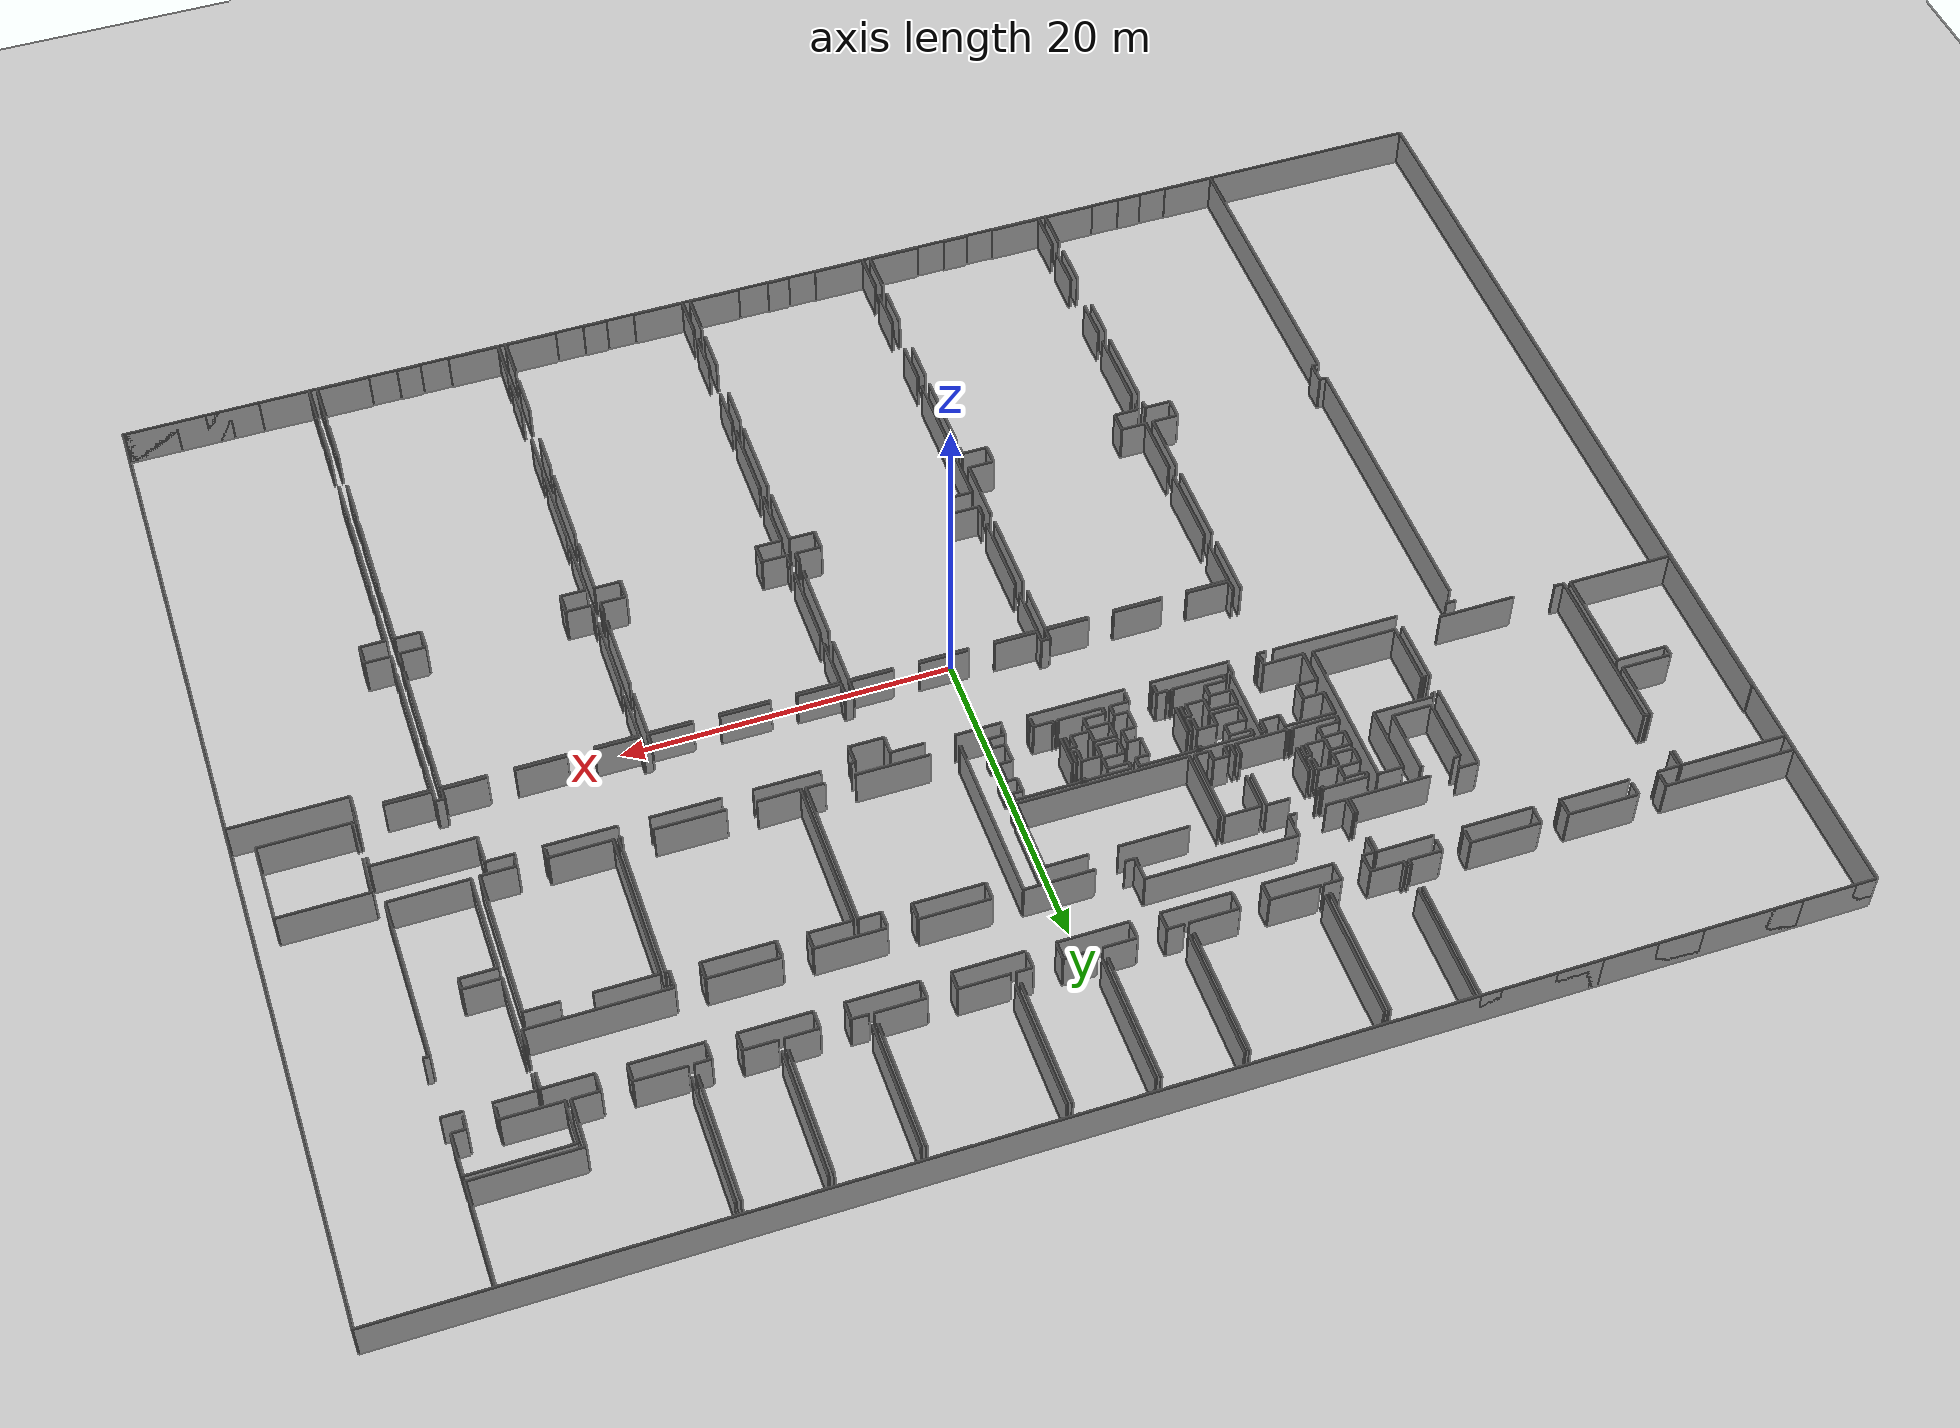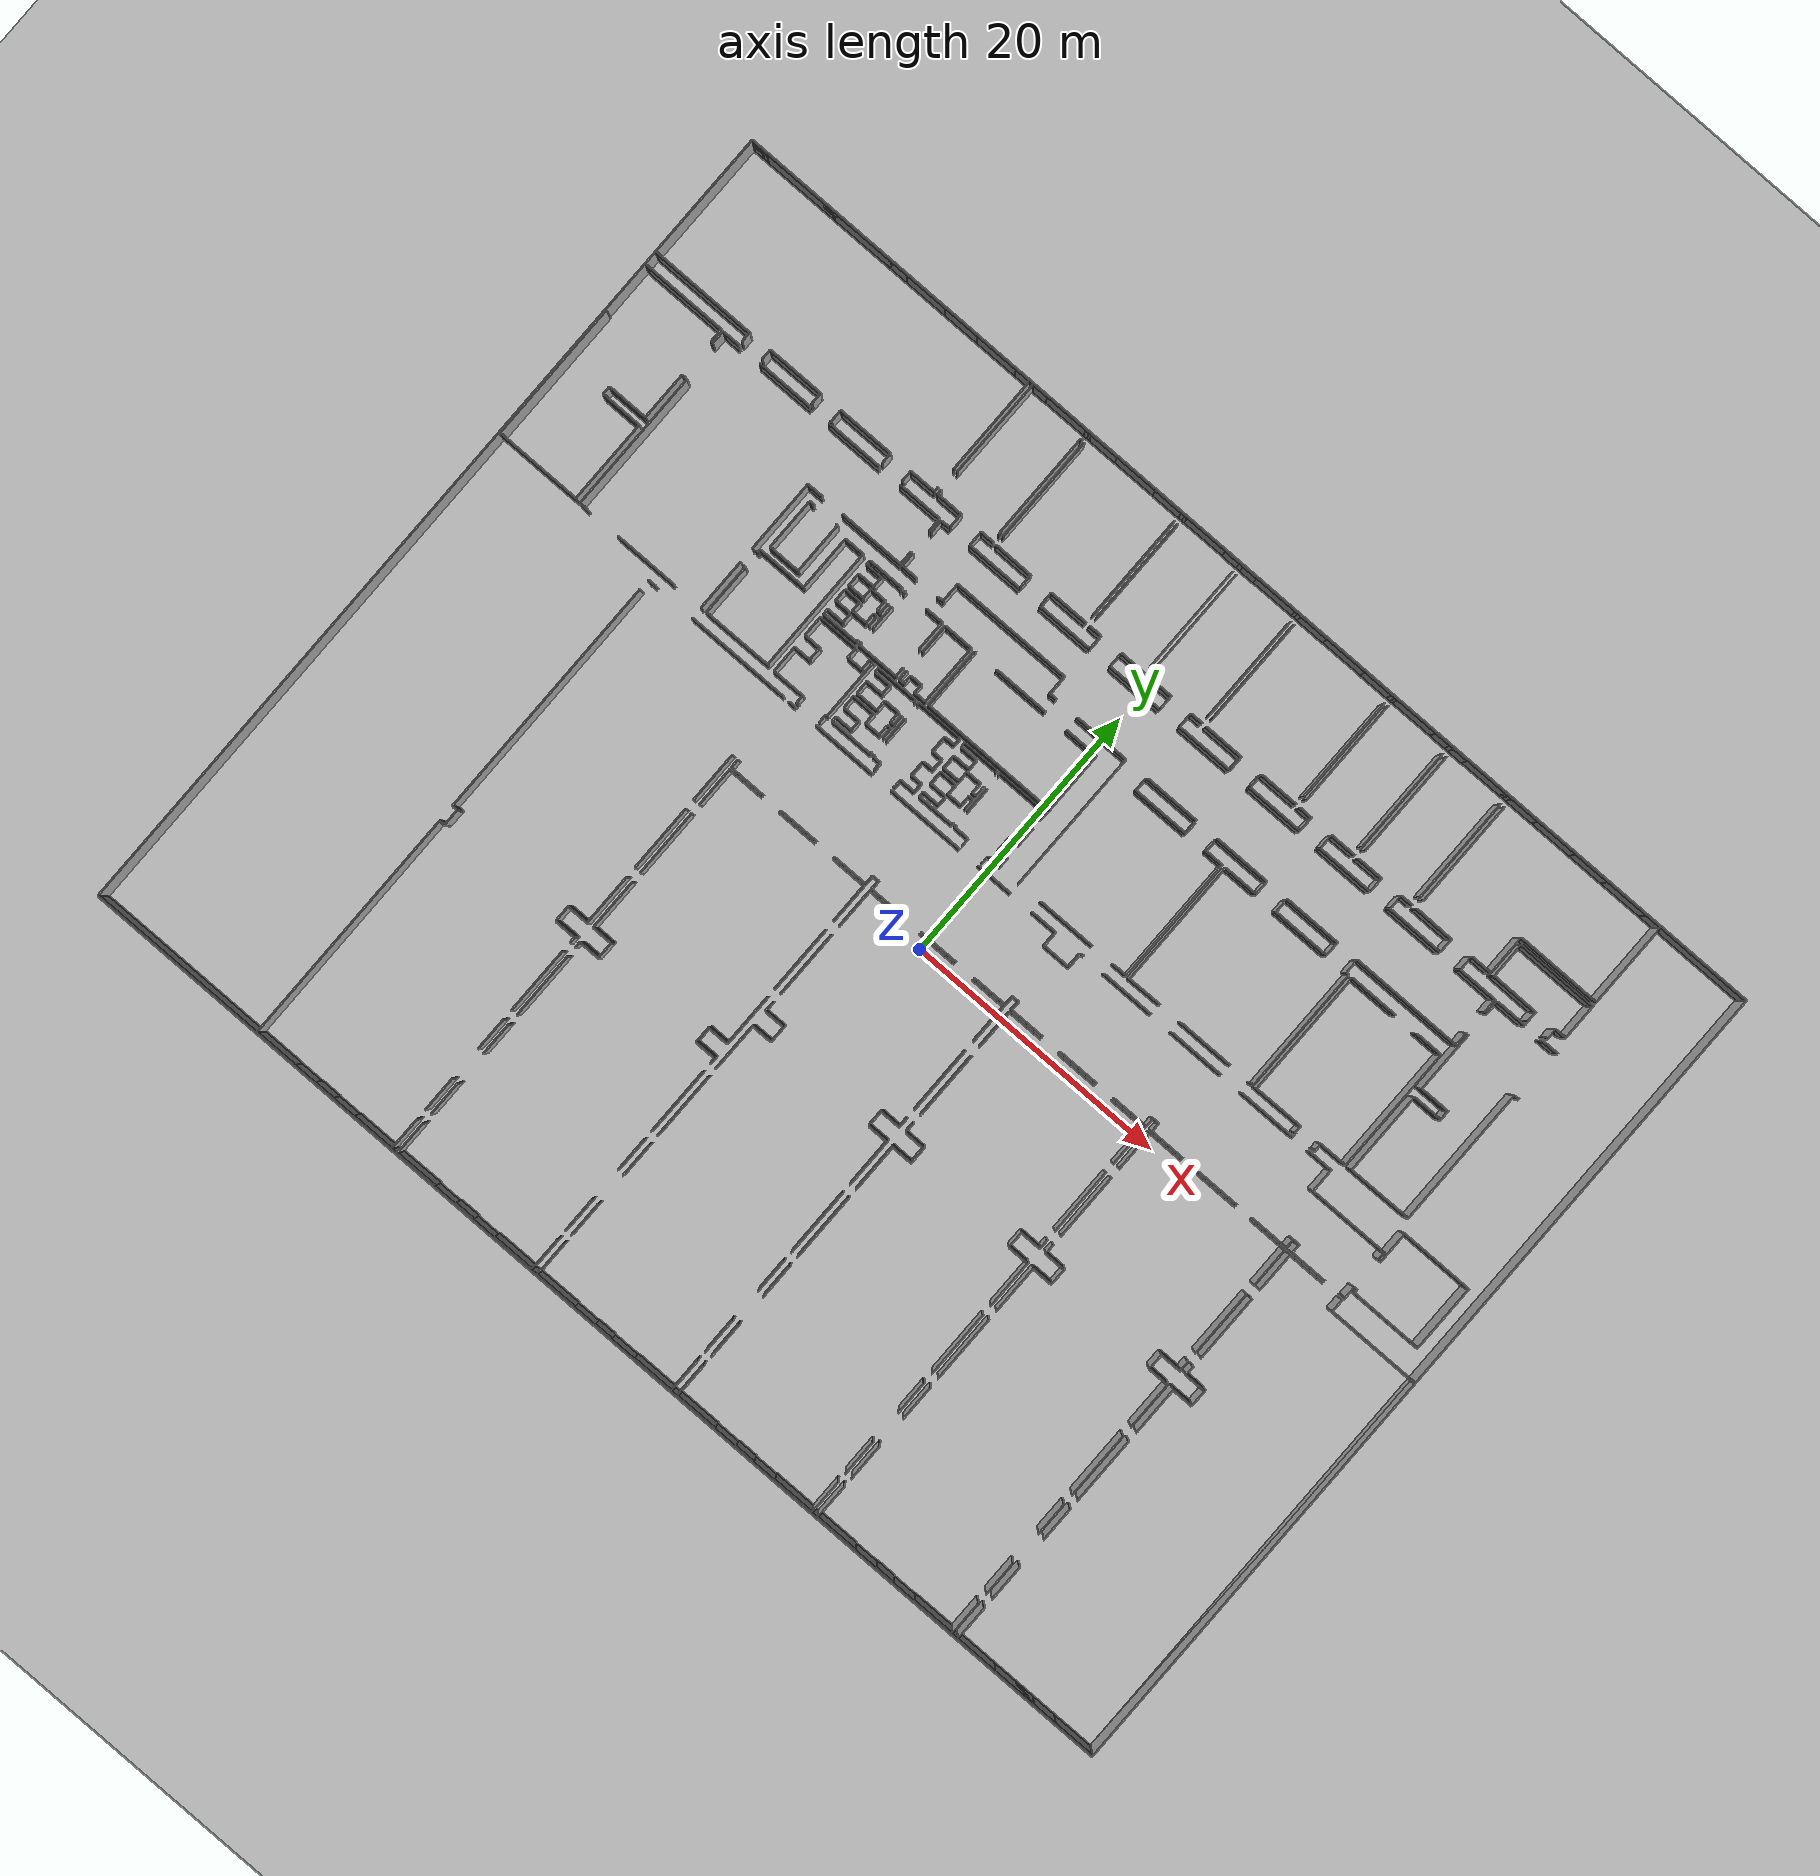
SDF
<sdf version="1.6">
  <world name="default">
    <light name="sun" type="directional">
      <cast_shadows>1</cast_shadows>
      <pose frame="">0 0 10 0 -0 0</pose>
      <diffuse>0.8 0.8 0.8 1</diffuse>
      <specular>0.1 0.1 0.1 1</specular>
      <attenuation>
        <range>1000</range>
        <constant>0.9</constant>
        <linear>0.01</linear>
        <quadratic>0.001</quadratic>
      </attenuation>
      <direction>-0.5 0.5 -1</direction>
    </light>
    <model name="ground_plane">
      <static>1</static>
      <link name="link">
        <collision name="collision">
          <geometry>
            <plane>
              <normal>0 0 1</normal>
              <size>100 100</size>
            </plane>
          </geometry>
          <surface>
            <friction>
              <ode>
                <mu>100</mu>
                <mu2>50</mu2>
              </ode>
              <torsional>
                <ode />
              </torsional>
            </friction>
            <contact>
              <ode />
            </contact>
            <bounce />
          </surface>
          <max_contacts>10</max_contacts>
        </collision>
        <visual name="visual">
          <cast_shadows>0</cast_shadows>
          <geometry>
            <plane>
              <normal>0 0 1</normal>
              <size>100 100</size>
            </plane>
          </geometry>
          <material>
            <script>
              <uri>file://media/materials/scripts/gazebo.material</uri>
              <name>Gazebo/Grey</name>
            </script>
          </material>
        </visual>
        <self_collide>0</self_collide>
        <kinematic>0</kinematic>
        <gravity>1</gravity>
      </link>
    </model>
    <gravity>0 0 -9.8</gravity>
    <magnetic_field>6e-06 2.3e-05 -4.2e-05</magnetic_field>
    <atmosphere type="adiabatic" />
    <physics default="0" name="default_physics" type="ode">
      <max_step_size>0.001</max_step_size>
      <real_time_factor>1</real_time_factor>
      <real_time_update_rate>1000</real_time_update_rate>
    </physics>
    <scene>
      <ambient>0.4 0.4 0.4 1</ambient>
      <background>0.7 0.7 0.7 1</background>
      <shadows>1</shadows>
    </scene>
    <spherical_coordinates>
      <surface_model>EARTH_WGS84</surface_model>
      <latitude_deg>0</latitude_deg>
      <longitude_deg>0</longitude_deg>
      <elevation>0</elevation>
      <heading_deg>0</heading_deg>
    </spherical_coordinates>
  <model name="50052750">
		<static>1</static>
		<link name="Wall_0">
			<collision name="Wall_0_Collision">
				<geometry>
					<box>
						<size>8.04141937434 0.1 2.5</size>
					</box>
				</geometry>
				<pose frame="">4.02070968717 0 1.25 0 0 0</pose>
			</collision>
			<visual name="Wall_0_Visual">
				<pose frame="">4.02070968717 0 1.25 0 0 0</pose>
				<geometry>
					<box>
						<size>8.04141937434 0.1 2.5</size>
					</box>
				</geometry>
				<material>
					<script>
						<uri>file://media/materials/scripts/gazebo.material</uri>
						<name>Gazebo/Grey</name>
					</script>
					<ambient>1 1 1 1</ambient>
				</material>
			</visual>
			<pose frame="">0.0 -9.54365278443 0 0 0 0.0</pose>
		</link>
		<link name="Wall_1">
			<collision name="Wall_1_Collision">
				<geometry>
					<box>
						<size>0.776772027063 0.1 2.5</size>
					</box>
				</geometry>
				<pose frame="">0.388386013531 0 1.25 0 0 0</pose>
			</collision>
			<visual name="Wall_1_Visual">
				<pose frame="">0.388386013531 0 1.25 0 0 0</pose>
				<geometry>
					<box>
						<size>0.776772027063 0.1 2.5</size>
					</box>
				</geometry>
				<material>
					<script>
						<uri>file://media/materials/scripts/gazebo.material</uri>
						<name>Gazebo/Grey</name>
					</script>
					<ambient>1 1 1 1</ambient>
				</material>
			</visual>
			<pose frame="">8.04141937434 -9.54365278443 0 0 0 -1.57079632679</pose>
		</link>
		<link name="Wall_2">
			<collision name="Wall_2_Collision">
				<geometry>
					<box>
						<size>0.820589284966 0.1 2.5</size>
					</box>
				</geometry>
				<pose frame="">0.410294642483 0 1.25 0 0 0</pose>
			</collision>
			<visual name="Wall_2_Visual">
				<pose frame="">0.410294642483 0 1.25 0 0 0</pose>
				<geometry>
					<box>
						<size>0.820589284966 0.1 2.5</size>
					</box>
				</geometry>
				<material>
					<script>
						<uri>file://media/materials/scripts/gazebo.material</uri>
						<name>Gazebo/Grey</name>
					</script>
					<ambient>1 1 1 1</ambient>
				</material>
			</visual>
			<pose frame="">9.7756937415 -10.3204248115 0 0 0 1.57079632679</pose>
		</link>
		<link name="Wall_3">
			<collision name="Wall_3_Collision">
				<geometry>
					<box>
						<size>4.30615689626 0.1 2.5</size>
					</box>
				</geometry>
				<pose frame="">2.15307844813 0 1.25 0 0 0</pose>
			</collision>
			<visual name="Wall_3_Visual">
				<pose frame="">2.15307844813 0 1.25 0 0 0</pose>
				<geometry>
					<box>
						<size>4.30615689626 0.1 2.5</size>
					</box>
				</geometry>
				<material>
					<script>
						<uri>file://media/materials/scripts/gazebo.material</uri>
						<name>Gazebo/Grey</name>
					</script>
					<ambient>1 1 1 1</ambient>
				</material>
			</visual>
			<pose frame="">9.7756937415 -9.49983552652 0 0 0 0.0</pose>
		</link>
		<link name="Wall_4">
			<collision name="Wall_4_Collision">
				<geometry>
					<box>
						<size>0.900476401549 0.1 2.5</size>
					</box>
				</geometry>
				<pose frame="">0.450238200774 0 1.25 0 0 0</pose>
			</collision>
			<visual name="Wall_4_Visual">
				<pose frame="">0.450238200774 0 1.25 0 0 0</pose>
				<geometry>
					<box>
						<size>0.900476401549 0.1 2.5</size>
					</box>
				</geometry>
				<material>
					<script>
						<uri>file://media/materials/scripts/gazebo.material</uri>
						<name>Gazebo/Grey</name>
					</script>
					<ambient>1 1 1 1</ambient>
				</material>
			</visual>
			<pose frame="">14.0818506378 -9.49983552652 0 0 0 -1.57079632679</pose>
		</link>
		<link name="Wall_5">
			<collision name="Wall_5_Collision">
				<geometry>
					<box>
						<size>0.054358801109 0.1 2.5</size>
					</box>
				</geometry>
				<pose frame="">0.0271794005545 0 1.25 0 0 0</pose>
			</collision>
			<visual name="Wall_5_Visual">
				<pose frame="">0.0271794005545 0 1.25 0 0 0</pose>
				<geometry>
					<box>
						<size>0.054358801109 0.1 2.5</size>
					</box>
				</geometry>
				<material>
					<script>
						<uri>file://media/materials/scripts/gazebo.material</uri>
						<name>Gazebo/Grey</name>
					</script>
					<ambient>1 1 1 1</ambient>
				</material>
			</visual>
			<pose frame="">14.0818506378 -10.4003119281 0 0 0 0.0</pose>
		</link>
		<link name="Wall_6">
			<collision name="Wall_6_Collision">
				<geometry>
					<box>
						<size>0.0820462278421 0.1 2.5</size>
					</box>
				</geometry>
				<pose frame="">0.0410231139211 0 1.25 0 0 0</pose>
			</collision>
			<visual name="Wall_6_Visual">
				<pose frame="">0.0410231139211 0 1.25 0 0 0</pose>
				<geometry>
					<box>
						<size>0.0820462278421 0.1 2.5</size>
					</box>
				</geometry>
				<material>
					<script>
						<uri>file://media/materials/scripts/gazebo.material</uri>
						<name>Gazebo/Grey</name>
					</script>
					<ambient>1 1 1 1</ambient>
				</material>
			</visual>
			<pose frame="">15.7047402653 -10.4003119281 0 0 0 0.0</pose>
		</link>
		<link name="Wall_7">
			<collision name="Wall_7_Collision">
				<geometry>
					<box>
						<size>0.920670442148 0.1 2.5</size>
					</box>
				</geometry>
				<pose frame="">0.460335221074 0 1.25 0 0 0</pose>
			</collision>
			<visual name="Wall_7_Visual">
				<pose frame="">0.460335221074 0 1.25 0 0 0</pose>
				<geometry>
					<box>
						<size>0.920670442148 0.1 2.5</size>
					</box>
				</geometry>
				<material>
					<script>
						<uri>file://media/materials/scripts/gazebo.material</uri>
						<name>Gazebo/Grey</name>
					</script>
					<ambient>1 1 1 1</ambient>
				</material>
			</visual>
			<pose frame="">15.7867864931 -10.4003119281 0 0 0 1.57079632679</pose>
		</link>
		<link name="Wall_8">
			<collision name="Wall_8_Collision">
				<geometry>
					<box>
						<size>4.26907098523 0.1 2.5</size>
					</box>
				</geometry>
				<pose frame="">2.13453549261 0 1.25 0 0 0</pose>
			</collision>
			<visual name="Wall_8_Visual">
				<pose frame="">2.13453549261 0 1.25 0 0 0</pose>
				<geometry>
					<box>
						<size>4.26907098523 0.1 2.5</size>
					</box>
				</geometry>
				<material>
					<script>
						<uri>file://media/materials/scripts/gazebo.material</uri>
						<name>Gazebo/Grey</name>
					</script>
					<ambient>1 1 1 1</ambient>
				</material>
			</visual>
			<pose frame="">15.7867864931 -9.47964148593 0 0 0 0.0</pose>
		</link>
		<link name="Wall_9">
			<collision name="Wall_9_Collision">
				<geometry>
					<box>
						<size>0.820335271877 0.1 2.5</size>
					</box>
				</geometry>
				<pose frame="">0.410167635938 0 1.25 0 0 0</pose>
			</collision>
			<visual name="Wall_9_Visual">
				<pose frame="">0.410167635938 0 1.25 0 0 0</pose>
				<geometry>
					<box>
						<size>0.820335271877 0.1 2.5</size>
					</box>
				</geometry>
				<material>
					<script>
						<uri>file://media/materials/scripts/gazebo.material</uri>
						<name>Gazebo/Grey</name>
					</script>
					<ambient>1 1 1 1</ambient>
				</material>
			</visual>
			<pose frame="">20.0558574783 -9.47964148593 0 0 0 -1.57079632679</pose>
		</link>
		<link name="Wall_10">
			<collision name="Wall_10_Collision">
				<geometry>
					<box>
						<size>0.812333859564 0.1 2.5</size>
					</box>
				</geometry>
				<pose frame="">0.406166929782 0 1.25 0 0 0</pose>
			</collision>
			<visual name="Wall_10_Visual">
				<pose frame="">0.406166929782 0 1.25 0 0 0</pose>
				<geometry>
					<box>
						<size>0.812333859564 0.1 2.5</size>
					</box>
				</geometry>
				<material>
					<script>
						<uri>file://media/materials/scripts/gazebo.material</uri>
						<name>Gazebo/Grey</name>
					</script>
					<ambient>1 1 1 1</ambient>
				</material>
			</visual>
			<pose frame="">21.7924179633 -10.2999767578 0 0 0 1.57079632679</pose>
		</link>
		<link name="Wall_11">
			<collision name="Wall_11_Collision">
				<geometry>
					<box>
						<size>2.00556034652 0.1 2.5</size>
					</box>
				</geometry>
				<pose frame="">1.00278017326 0 1.25 0 0 0</pose>
			</collision>
			<visual name="Wall_11_Visual">
				<pose frame="">1.00278017326 0 1.25 0 0 0</pose>
				<geometry>
					<box>
						<size>2.00556034652 0.1 2.5</size>
					</box>
				</geometry>
				<material>
					<script>
						<uri>file://media/materials/scripts/gazebo.material</uri>
						<name>Gazebo/Grey</name>
					</script>
					<ambient>1 1 1 1</ambient>
				</material>
			</visual>
			<pose frame="">21.7924179633 -9.48764289824 0 0 0 0.0</pose>
		</link>
		<link name="Wall_12">
			<collision name="Wall_12_Collision">
				<geometry>
					<box>
						<size>0.361587632611 0.1 2.5</size>
					</box>
				</geometry>
				<pose frame="">0.180793816305 0 1.25 0 0 0</pose>
			</collision>
			<visual name="Wall_12_Visual">
				<pose frame="">0.180793816305 0 1.25 0 0 0</pose>
				<geometry>
					<box>
						<size>0.361587632611 0.1 2.5</size>
					</box>
				</geometry>
				<material>
					<script>
						<uri>file://media/materials/scripts/gazebo.material</uri>
						<name>Gazebo/Grey</name>
					</script>
					<ambient>1 1 1 1</ambient>
				</material>
			</visual>
			<pose frame="">23.7979783098 -9.48764289824 0 0 0 1.57079632679</pose>
		</link>
		<link name="Wall_13">
			<collision name="Wall_13_Collision">
				<geometry>
					<box>
						<size>7.55206315781 0.1 2.5</size>
					</box>
				</geometry>
				<pose frame="">3.77603157891 0 1.25 0 0 0</pose>
			</collision>
			<visual name="Wall_13_Visual">
				<pose frame="">3.77603157891 0 1.25 0 0 0</pose>
				<geometry>
					<box>
						<size>7.55206315781 0.1 2.5</size>
					</box>
				</geometry>
				<material>
					<script>
						<uri>file://media/materials/scripts/gazebo.material</uri>
						<name>Gazebo/Grey</name>
					</script>
					<ambient>1 1 1 1</ambient>
				</material>
			</visual>
			<pose frame="">23.7979783098 -7.55206315781 0 0 0 1.57079632679</pose>
		</link>
		<link name="Wall_14">
			<collision name="Wall_14_Collision">
				<geometry>
					<box>
						<size>1.20580013488 0.1 2.5</size>
					</box>
				</geometry>
				<pose frame="">0.60290006744 0 1.25 0 0 0</pose>
			</collision>
			<visual name="Wall_14_Visual">
				<pose frame="">0.60290006744 0 1.25 0 0 0</pose>
				<geometry>
					<box>
						<size>1.20580013488 0.1 2.5</size>
					</box>
				</geometry>
				<material>
					<script>
						<uri>file://media/materials/scripts/gazebo.material</uri>
						<name>Gazebo/Grey</name>
					</script>
					<ambient>1 1 1 1</ambient>
				</material>
			</visual>
			<pose frame="">23.7979783098 -0.0 0 0 0 3.14159265359</pose>
		</link>
		<link name="Wall_15">
			<collision name="Wall_15_Collision">
				<geometry>
					<box>
						<size>2.73127574264 0.1 2.5</size>
					</box>
				</geometry>
				<pose frame="">1.36563787132 0 1.25 0 0 0</pose>
			</collision>
			<visual name="Wall_15_Visual">
				<pose frame="">1.36563787132 0 1.25 0 0 0</pose>
				<geometry>
					<box>
						<size>2.73127574264 0.1 2.5</size>
					</box>
				</geometry>
				<material>
					<script>
						<uri>file://media/materials/scripts/gazebo.material</uri>
						<name>Gazebo/Grey</name>
					</script>
					<ambient>1 1 1 1</ambient>
				</material>
			</visual>
			<pose frame="">19.2992794919 -0.0 0 0 0 3.14159265359</pose>
		</link>
		<link name="Wall_16">
			<collision name="Wall_16_Collision">
				<geometry>
					<box>
						<size>2.74588149527 0.1 2.5</size>
					</box>
				</geometry>
				<pose frame="">1.37294074764 0 1.25 0 0 0</pose>
			</collision>
			<visual name="Wall_16_Visual">
				<pose frame="">1.37294074764 0 1.25 0 0 0</pose>
				<geometry>
					<box>
						<size>2.74588149527 0.1 2.5</size>
					</box>
				</geometry>
				<material>
					<script>
						<uri>file://media/materials/scripts/gazebo.material</uri>
						<name>Gazebo/Grey</name>
					</script>
					<ambient>1 1 1 1</ambient>
				</material>
			</visual>
			<pose frame="">13.2817094065 -0.0 0 0 0 3.14159265359</pose>
		</link>
		<link name="Wall_17">
			<collision name="Wall_17_Collision">
				<geometry>
					<box>
						<size>2.74791359999 0.1 2.5</size>
					</box>
				</geometry>
				<pose frame="">1.37395679999 0 1.25 0 0 0</pose>
			</collision>
			<visual name="Wall_17_Visual">
				<pose frame="">1.37395679999 0 1.25 0 0 0</pose>
				<geometry>
					<box>
						<size>2.74791359999 0.1 2.5</size>
					</box>
				</geometry>
				<material>
					<script>
						<uri>file://media/materials/scripts/gazebo.material</uri>
						<name>Gazebo/Grey</name>
					</script>
					<ambient>1 1 1 1</ambient>
				</material>
			</visual>
			<pose frame="">7.27874507373 -0.0 0 0 0 3.14159265359</pose>
		</link>
		<link name="Wall_18">
			<collision name="Wall_18_Collision">
				<geometry>
					<box>
						<size>1.27565373444 0.1 2.5</size>
					</box>
				</geometry>
				<pose frame="">0.637826867218 0 1.25 0 0 0</pose>
			</collision>
			<visual name="Wall_18_Visual">
				<pose frame="">0.637826867218 0 1.25 0 0 0</pose>
				<geometry>
					<box>
						<size>1.27565373444 0.1 2.5</size>
					</box>
				</geometry>
				<material>
					<script>
						<uri>file://media/materials/scripts/gazebo.material</uri>
						<name>Gazebo/Grey</name>
					</script>
					<ambient>1 1 1 1</ambient>
				</material>
			</visual>
			<pose frame="">1.29495872922 -0.0 0 0 0 3.14159265359</pose>
		</link>
		<link name="Wall_19">
			<collision name="Wall_19_Collision">
				<geometry>
					<box>
						<size>9.54367230957 0.1 2.5</size>
					</box>
				</geometry>
				<pose frame="">4.77183615479 0 1.25 0 0 0</pose>
			</collision>
			<visual name="Wall_19_Visual">
				<pose frame="">4.77183615479 0 1.25 0 0 0</pose>
				<geometry>
					<box>
						<size>9.54367230957 0.1 2.5</size>
					</box>
				</geometry>
				<material>
					<script>
						<uri>file://media/materials/scripts/gazebo.material</uri>
						<name>Gazebo/Grey</name>
					</script>
					<ambient>1 1 1 1</ambient>
				</material>
			</visual>
			<pose frame="">0.0193049947864 -0.0 0 0 0 -1.57281913388</pose>
		</link>
		<link name="Wall_20">
			<collision name="Wall_20_Collision">
				<geometry>
					<box>
						<size>10.5104266023 0.1 2.5</size>
					</box>
				</geometry>
				<pose frame="">5.25521330114 0 1.25 0 0 0</pose>
			</collision>
			<visual name="Wall_20_Visual">
				<pose frame="">5.25521330114 0 1.25 0 0 0</pose>
				<geometry>
					<box>
						<size>10.5104266023 0.1 2.5</size>
					</box>
				</geometry>
				<material>
					<script>
						<uri>file://media/materials/scripts/gazebo.material</uri>
						<name>Gazebo/Grey</name>
					</script>
					<ambient>1 1 1 1</ambient>
				</material>
			</visual>
			<pose frame="">0.0762039267883 -25.0130499225 0 0 0 1.57079632679</pose>
		</link>
		<link name="Wall_21">
			<collision name="Wall_21_Collision">
				<geometry>
					<box>
						<size>6.44736023247 0.1 2.5</size>
					</box>
				</geometry>
				<pose frame="">3.22368011624 0 1.25 0 0 0</pose>
			</collision>
			<visual name="Wall_21_Visual">
				<pose frame="">3.22368011624 0 1.25 0 0 0</pose>
				<geometry>
					<box>
						<size>6.44736023247 0.1 2.5</size>
					</box>
				</geometry>
				<material>
					<script>
						<uri>file://media/materials/scripts/gazebo.material</uri>
						<name>Gazebo/Grey</name>
					</script>
					<ambient>1 1 1 1</ambient>
				</material>
			</visual>
			<pose frame="">0.0762039267883 -10.5851064505 0 0 0 0.0</pose>
		</link>
		<link name="Wall_22">
			<collision name="Wall_22_Collision">
				<geometry>
					<box>
						<size>1.0499631046 0.1 2.5</size>
					</box>
				</geometry>
				<pose frame="">0.524981552299 0 1.25 0 0 0</pose>
			</collision>
			<visual name="Wall_22_Visual">
				<pose frame="">0.524981552299 0 1.25 0 0 0</pose>
				<geometry>
					<box>
						<size>1.0499631046 0.1 2.5</size>
					</box>
				</geometry>
				<material>
					<script>
						<uri>file://media/materials/scripts/gazebo.material</uri>
						<name>Gazebo/Grey</name>
					</script>
					<ambient>1 1 1 1</ambient>
				</material>
			</visual>
			<pose frame="">6.52356415926 -10.5851064505 0 0 0 -1.57079632679</pose>
		</link>
		<link name="Wall_23">
			<collision name="Wall_23_Collision">
				<geometry>
					<box>
						<size>3.68572992566 0.1 2.5</size>
					</box>
				</geometry>
				<pose frame="">1.84286496283 0 1.25 0 0 0</pose>
			</collision>
			<visual name="Wall_23_Visual">
				<pose frame="">1.84286496283 0 1.25 0 0 0</pose>
				<geometry>
					<box>
						<size>3.68572992566 0.1 2.5</size>
					</box>
				</geometry>
				<material>
					<script>
						<uri>file://media/materials/scripts/gazebo.material</uri>
						<name>Gazebo/Grey</name>
					</script>
					<ambient>1 1 1 1</ambient>
				</material>
			</visual>
			<pose frame="">6.52356415926 -14.4245142952 0 0 0 -1.57079632679</pose>
		</link>
		<link name="Wall_24">
			<collision name="Wall_24_Collision">
				<geometry>
					<box>
						<size>3.05349134641 0.1 2.5</size>
					</box>
				</geometry>
				<pose frame="">1.5267456732 0 1.25 0 0 0</pose>
			</collision>
			<visual name="Wall_24_Visual">
				<pose frame="">1.5267456732 0 1.25 0 0 0</pose>
				<geometry>
					<box>
						<size>3.05349134641 0.1 2.5</size>
					</box>
				</geometry>
				<material>
					<script>
						<uri>file://media/materials/scripts/gazebo.material</uri>
						<name>Gazebo/Grey</name>
					</script>
					<ambient>1 1 1 1</ambient>
				</material>
			</visual>
			<pose frame="">6.52356415926 -18.1102442209 0 0 0 3.14159265359</pose>
		</link>
		<link name="Wall_25">
			<collision name="Wall_25_Collision">
				<geometry>
					<box>
						<size>0.633889664334 0.1 2.5</size>
					</box>
				</geometry>
				<pose frame="">0.316944832167 0 1.25 0 0 0</pose>
			</collision>
			<visual name="Wall_25_Visual">
				<pose frame="">0.316944832167 0 1.25 0 0 0</pose>
				<geometry>
					<box>
						<size>0.633889664334 0.1 2.5</size>
					</box>
				</geometry>
				<material>
					<script>
						<uri>file://media/materials/scripts/gazebo.material</uri>
						<name>Gazebo/Grey</name>
					</script>
					<ambient>1 1 1 1</ambient>
				</material>
			</visual>
			<pose frame="">3.47007281285 -18.1102442209 0 0 0 -1.57079632679</pose>
		</link>
		<link name="Wall_26">
			<collision name="Wall_26_Collision">
				<geometry>
					<box>
						<size>3.08282985822 0.1 2.5</size>
					</box>
				</geometry>
				<pose frame="">1.54141492911 0 1.25 0 0 0</pose>
			</collision>
			<visual name="Wall_26_Visual">
				<pose frame="">1.54141492911 0 1.25 0 0 0</pose>
				<geometry>
					<box>
						<size>3.08282985822 0.1 2.5</size>
					</box>
				</geometry>
				<material>
					<script>
						<uri>file://media/materials/scripts/gazebo.material</uri>
						<name>Gazebo/Grey</name>
					</script>
					<ambient>1 1 1 1</ambient>
				</material>
			</visual>
			<pose frame="">3.47007281285 -18.7441338852 0 0 0 0.0</pose>
		</link>
		<link name="Wall_27">
			<collision name="Wall_27_Collision">
				<geometry>
					<box>
						<size>6.2710751485 0.1 2.5</size>
					</box>
				</geometry>
				<pose frame="">3.13553757425 0 1.25 0 0 0</pose>
			</collision>
			<visual name="Wall_27_Visual">
				<pose frame="">3.13553757425 0 1.25 0 0 0</pose>
				<geometry>
					<box>
						<size>6.2710751485 0.1 2.5</size>
					</box>
				</geometry>
				<material>
					<script>
						<uri>file://media/materials/scripts/gazebo.material</uri>
						<name>Gazebo/Grey</name>
					</script>
					<ambient>1 1 1 1</ambient>
				</material>
			</visual>
			<pose frame="">6.55290267107 -18.7441338852 0 0 0 -1.57079632679</pose>
		</link>
		<link name="Wall_28">
			<collision name="Wall_28_Collision">
				<geometry>
					<box>
						<size>6.47669910417 0.1 2.5</size>
					</box>
				</geometry>
				<pose frame="">3.23834955209 0 1.25 0 0 0</pose>
			</collision>
			<visual name="Wall_28_Visual">
				<pose frame="">3.23834955209 0 1.25 0 0 0</pose>
				<geometry>
					<box>
						<size>6.47669910417 0.1 2.5</size>
					</box>
				</geometry>
				<material>
					<script>
						<uri>file://media/materials/scripts/gazebo.material</uri>
						<name>Gazebo/Grey</name>
					</script>
					<ambient>1 1 1 1</ambient>
				</material>
			</visual>
			<pose frame="">6.55290267107 -25.0152090337 0 0 0 3.14125928759</pose>
		</link>
		<link name="Wall_29">
			<collision name="Wall_29_Collision">
				<geometry>
					<box>
						<size>10.5544978733 0.1 2.5</size>
					</box>
				</geometry>
				<pose frame="">5.27724893664 0 1.25 0 0 0</pose>
			</collision>
			<visual name="Wall_29_Visual">
				<pose frame="">5.27724893664 0 1.25 0 0 0</pose>
				<geometry>
					<box>
						<size>10.5544978733 0.1 2.5</size>
					</box>
				</geometry>
				<material>
					<script>
						<uri>file://media/materials/scripts/gazebo.material</uri>
						<name>Gazebo/Grey</name>
					</script>
					<ambient>1 1 1 1</ambient>
				</material>
			</visual>
			<pose frame="">6.95233825399 -25.0538190233 0 0 0 1.57079632679</pose>
		</link>
		<link name="Wall_30">
			<collision name="Wall_30_Collision">
				<geometry>
					<box>
						<size>0.265062658679 0.1 2.5</size>
					</box>
				</geometry>
				<pose frame="">0.132531329339 0 1.25 0 0 0</pose>
			</collision>
			<visual name="Wall_30_Visual">
				<pose frame="">0.132531329339 0 1.25 0 0 0</pose>
				<geometry>
					<box>
						<size>0.265062658679 0.1 2.5</size>
					</box>
				</geometry>
				<material>
					<script>
						<uri>file://media/materials/scripts/gazebo.material</uri>
						<name>Gazebo/Grey</name>
					</script>
					<ambient>1 1 1 1</ambient>
				</material>
			</visual>
			<pose frame="">6.95233825399 -14.49932115 0 0 0 3.14159265359</pose>
		</link>
		<link name="Wall_31">
			<collision name="Wall_31_Collision">
				<geometry>
					<box>
						<size>0.0863644503601 0.1 2.5</size>
					</box>
				</geometry>
				<pose frame="">0.0431822251801 0 1.25 0 0 0</pose>
			</collision>
			<visual name="Wall_31_Visual">
				<pose frame="">0.0431822251801 0 1.25 0 0 0</pose>
				<geometry>
					<box>
						<size>0.0863644503601 0.1 2.5</size>
					</box>
				</geometry>
				<material>
					<script>
						<uri>file://media/materials/scripts/gazebo.material</uri>
						<name>Gazebo/Grey</name>
					</script>
					<ambient>1 1 1 1</ambient>
				</material>
			</visual>
			<pose frame="">6.68727559531 -14.49932115 0 0 0 1.57079632679</pose>
		</link>
		<link name="Wall_32">
			<collision name="Wall_32_Collision">
				<geometry>
					<box>
						<size>1.05428132712 0.1 2.5</size>
					</box>
				</geometry>
				<pose frame="">0.527140663558 0 1.25 0 0 0</pose>
			</collision>
			<visual name="Wall_32_Visual">
				<pose frame="">0.527140663558 0 1.25 0 0 0</pose>
				<geometry>
					<box>
						<size>1.05428132712 0.1 2.5</size>
					</box>
				</geometry>
				<material>
					<script>
						<uri>file://media/materials/scripts/gazebo.material</uri>
						<name>Gazebo/Grey</name>
					</script>
					<ambient>1 1 1 1</ambient>
				</material>
			</visual>
			<pose frame="">6.68727559531 -11.6515804059 0 0 0 1.57079632679</pose>
		</link>
		<link name="Wall_33">
			<collision name="Wall_33_Collision">
				<geometry>
					<box>
						<size>1.3321716468 0.1 2.5</size>
					</box>
				</geometry>
				<pose frame="">0.666085823402 0 1.25 0 0 0</pose>
			</collision>
			<visual name="Wall_33_Visual">
				<pose frame="">0.666085823402 0 1.25 0 0 0</pose>
				<geometry>
					<box>
						<size>1.3321716468 0.1 2.5</size>
					</box>
				</geometry>
				<material>
					<script>
						<uri>file://media/materials/scripts/gazebo.material</uri>
						<name>Gazebo/Grey</name>
					</script>
					<ambient>1 1 1 1</ambient>
				</material>
			</visual>
			<pose frame="">6.68727559531 -10.5972990788 0 0 0 0.0</pose>
		</link>
		<link name="Wall_34">
			<collision name="Wall_34_Collision">
				<geometry>
					<box>
						<size>4.30221969338 0.1 2.5</size>
					</box>
				</geometry>
				<pose frame="">2.15110984669 0 1.25 0 0 0</pose>
			</collision>
			<visual name="Wall_34_Visual">
				<pose frame="">2.15110984669 0 1.25 0 0 0</pose>
				<geometry>
					<box>
						<size>4.30221969338 0.1 2.5</size>
					</box>
				</geometry>
				<material>
					<script>
						<uri>file://media/materials/scripts/gazebo.material</uri>
						<name>Gazebo/Grey</name>
					</script>
					<ambient>1 1 1 1</ambient>
				</material>
			</visual>
			<pose frame="">9.82040004521 -10.5972990788 0 0 0 0.0</pose>
		</link>
		<link name="Wall_35">
			<collision name="Wall_35_Collision">
				<geometry>
					<box>
						<size>4.32127067508 0.1 2.5</size>
					</box>
				</geometry>
				<pose frame="">2.16063533754 0 1.25 0 0 0</pose>
			</collision>
			<visual name="Wall_35_Visual">
				<pose frame="">2.16063533754 0 1.25 0 0 0</pose>
				<geometry>
					<box>
						<size>4.32127067508 0.1 2.5</size>
					</box>
				</geometry>
				<material>
					<script>
						<uri>file://media/materials/scripts/gazebo.material</uri>
						<name>Gazebo/Grey</name>
					</script>
					<ambient>1 1 1 1</ambient>
				</material>
			</visual>
			<pose frame="">15.7231562142 -10.5972990788 0 0 0 0.0</pose>
		</link>
		<link name="Wall_36">
			<collision name="Wall_36_Collision">
				<geometry>
					<box>
						<size>3.39551997114 0.1 2.5</size>
					</box>
				</geometry>
				<pose frame="">1.69775998557 0 1.25 0 0 0</pose>
			</collision>
			<visual name="Wall_36_Visual">
				<pose frame="">1.69775998557 0 1.25 0 0 0</pose>
				<geometry>
					<box>
						<size>3.39551997114 0.1 2.5</size>
					</box>
				</geometry>
				<material>
					<script>
						<uri>file://media/materials/scripts/gazebo.material</uri>
						<name>Gazebo/Grey</name>
					</script>
					<ambient>1 1 1 1</ambient>
				</material>
			</visual>
			<pose frame="">21.8179462788 -10.5972990788 0 0 0 0.0</pose>
		</link>
		<link name="Wall_37">
			<collision name="Wall_37_Collision">
				<geometry>
					<box>
						<size>1.02735593965 0.1 2.5</size>
					</box>
				</geometry>
				<pose frame="">0.513677969826 0 1.25 0 0 0</pose>
			</collision>
			<visual name="Wall_37_Visual">
				<pose frame="">0.513677969826 0 1.25 0 0 0</pose>
				<geometry>
					<box>
						<size>1.02735593965 0.1 2.5</size>
					</box>
				</geometry>
				<material>
					<script>
						<uri>file://media/materials/scripts/gazebo.material</uri>
						<name>Gazebo/Grey</name>
					</script>
					<ambient>1 1 1 1</ambient>
				</material>
			</visual>
			<pose frame="">25.2134662499 -10.5972990788 0 0 0 -1.57079632679</pose>
		</link>
		<link name="Wall_38">
			<collision name="Wall_38_Collision">
				<geometry>
					<box>
						<size>1.07231625646 0.1 2.5</size>
					</box>
				</geometry>
				<pose frame="">0.536158128228 0 1.25 0 0 0</pose>
			</collision>
			<visual name="Wall_38_Visual">
				<pose frame="">0.536158128228 0 1.25 0 0 0</pose>
				<geometry>
					<box>
						<size>1.07231625646 0.1 2.5</size>
					</box>
				</geometry>
				<material>
					<script>
						<uri>file://media/materials/scripts/gazebo.material</uri>
						<name>Gazebo/Grey</name>
					</script>
					<ambient>1 1 1 1</ambient>
				</material>
			</visual>
			<pose frame="">25.2134662499 -13.4125261475 0 0 0 -1.57079632679</pose>
		</link>
		<link name="Wall_39">
			<collision name="Wall_39_Collision">
				<geometry>
					<box>
						<size>4.94398376348 0.1 2.5</size>
					</box>
				</geometry>
				<pose frame="">2.47199188174 0 1.25 0 0 0</pose>
			</collision>
			<visual name="Wall_39_Visual">
				<pose frame="">2.47199188174 0 1.25 0 0 0</pose>
				<geometry>
					<box>
						<size>4.94398376348 0.1 2.5</size>
					</box>
				</geometry>
				<material>
					<script>
						<uri>file://media/materials/scripts/gazebo.material</uri>
						<name>Gazebo/Grey</name>
					</script>
					<ambient>1 1 1 1</ambient>
				</material>
			</visual>
			<pose frame="">25.2134662499 -14.4848424039 0 0 0 3.14159265359</pose>
		</link>
		<link name="Wall_40">
			<collision name="Wall_40_Collision">
				<geometry>
					<box>
						<size>1.20795924614 0.1 2.5</size>
					</box>
				</geometry>
				<pose frame="">0.60397962307 0 1.25 0 0 0</pose>
			</collision>
			<visual name="Wall_40_Visual">
				<pose frame="">0.60397962307 0 1.25 0 0 0</pose>
				<geometry>
					<box>
						<size>1.20795924614 0.1 2.5</size>
					</box>
				</geometry>
				<material>
					<script>
						<uri>file://media/materials/scripts/gazebo.material</uri>
						<name>Gazebo/Grey</name>
					</script>
					<ambient>1 1 1 1</ambient>
				</material>
			</visual>
			<pose frame="">18.5179352292 -14.4848424039 0 0 0 3.14159265359</pose>
		</link>
		<link name="Wall_41">
			<collision name="Wall_41_Collision">
				<geometry>
					<box>
						<size>5.47690322482 0.1 2.5</size>
					</box>
				</geometry>
				<pose frame="">2.73845161241 0 1.25 0 0 0</pose>
			</collision>
			<visual name="Wall_41_Visual">
				<pose frame="">2.73845161241 0 1.25 0 0 0</pose>
				<geometry>
					<box>
						<size>5.47690322482 0.1 2.5</size>
					</box>
				</geometry>
				<material>
					<script>
						<uri>file://media/materials/scripts/gazebo.material</uri>
						<name>Gazebo/Grey</name>
					</script>
					<ambient>1 1 1 1</ambient>
				</material>
			</visual>
			<pose frame="">17.3099759831 -14.4848424039 0 0 0 -1.57079632679</pose>
		</link>
		<link name="Wall_42">
			<collision name="Wall_42_Collision">
				<geometry>
					<box>
						<size>3.94520429638 0.1 2.5</size>
					</box>
				</geometry>
				<pose frame="">1.97260214819 0 1.25 0 0 0</pose>
			</collision>
			<visual name="Wall_42_Visual">
				<pose frame="">1.97260214819 0 1.25 0 0 0</pose>
				<geometry>
					<box>
						<size>3.94520429638 0.1 2.5</size>
					</box>
				</geometry>
				<material>
					<script>
						<uri>file://media/materials/scripts/gazebo.material</uri>
						<name>Gazebo/Grey</name>
					</script>
					<ambient>1 1 1 1</ambient>
				</material>
			</visual>
			<pose frame="">17.3099759831 -21.1312218919 0 0 0 -1.57079632679</pose>
		</link>
		<link name="Wall_43">
			<collision name="Wall_43_Collision">
				<geometry>
					<box>
						<size>4.69606698833 0.1 2.5</size>
					</box>
				</geometry>
				<pose frame="">2.34803349417 0 1.25 0 0 0</pose>
			</collision>
			<visual name="Wall_43_Visual">
				<pose frame="">2.34803349417 0 1.25 0 0 0</pose>
				<geometry>
					<box>
						<size>4.69606698833 0.1 2.5</size>
					</box>
				</geometry>
				<material>
					<script>
						<uri>file://media/materials/scripts/gazebo.material</uri>
						<name>Gazebo/Grey</name>
					</script>
					<ambient>1 1 1 1</ambient>
				</material>
			</visual>
			<pose frame="">14.9079012041 -25.0764261882 0 0 0 3.14159265359</pose>
		</link>
		<link name="Wall_44">
			<collision name="Wall_44_Collision">
				<geometry>
					<box>
						<size>0.590124576314 0.1 2.5</size>
					</box>
				</geometry>
				<pose frame="">0.295062288157 0 1.25 0 0 0</pose>
			</collision>
			<visual name="Wall_44_Visual">
				<pose frame="">0.295062288157 0 1.25 0 0 0</pose>
				<geometry>
					<box>
						<size>0.590124576314 0.1 2.5</size>
					</box>
				</geometry>
				<material>
					<script>
						<uri>file://media/materials/scripts/gazebo.material</uri>
						<name>Gazebo/Grey</name>
					</script>
					<ambient>1 1 1 1</ambient>
				</material>
			</visual>
			<pose frame="">7.54202964079 -25.0764261882 0 0 0 3.10327413715</pose>
		</link>
		<link name="Wall_45">
			<collision name="Wall_45_Collision">
				<geometry>
					<box>
						<size>3.8260721575 0.1 2.5</size>
					</box>
				</geometry>
				<pose frame="">1.91303607875 0 1.25 0 0 0</pose>
			</collision>
			<visual name="Wall_45_Visual">
				<pose frame="">1.91303607875 0 1.25 0 0 0</pose>
				<geometry>
					<box>
						<size>3.8260721575 0.1 2.5</size>
					</box>
				</geometry>
				<material>
					<script>
						<uri>file://media/materials/scripts/gazebo.material</uri>
						<name>Gazebo/Grey</name>
					</script>
					<ambient>1 1 1 1</ambient>
				</material>
			</visual>
			<pose frame="">17.7722798056 -25.0535650102 0 0 0 1.57079632679</pose>
		</link>
		<link name="Wall_46">
			<collision name="Wall_46_Collision">
				<geometry>
					<box>
						<size>0.175777057792 0.1 2.5</size>
					</box>
				</geometry>
				<pose frame="">0.0878885288959 0 1.25 0 0 0</pose>
			</collision>
			<visual name="Wall_46_Visual">
				<pose frame="">0.0878885288959 0 1.25 0 0 0</pose>
				<geometry>
					<box>
						<size>0.175777057792 0.1 2.5</size>
					</box>
				</geometry>
				<material>
					<script>
						<uri>file://media/materials/scripts/gazebo.material</uri>
						<name>Gazebo/Grey</name>
					</script>
					<ambient>1 1 1 1</ambient>
				</material>
			</visual>
			<pose frame="">17.7722798056 -21.2274928527 0 0 0 3.14159265359</pose>
		</link>
		<link name="Wall_47">
			<collision name="Wall_47_Collision">
				<geometry>
					<box>
						<size>0.0798871165831 0.1 2.5</size>
					</box>
				</geometry>
				<pose frame="">0.0399435582916 0 1.25 0 0 0</pose>
			</collision>
			<visual name="Wall_47_Visual">
				<pose frame="">0.0399435582916 0 1.25 0 0 0</pose>
				<geometry>
					<box>
						<size>0.0798871165831 0.1 2.5</size>
					</box>
				</geometry>
				<material>
					<script>
						<uri>file://media/materials/scripts/gazebo.material</uri>
						<name>Gazebo/Grey</name>
					</script>
					<ambient>1 1 1 1</ambient>
				</material>
			</visual>
			<pose frame="">17.5965027478 -21.2274928527 0 0 0 1.57079632679</pose>
		</link>
		<link name="Wall_48">
			<collision name="Wall_48_Collision">
				<geometry>
					<box>
						<size>0.0638842919576 0.1 2.5</size>
					</box>
				</geometry>
				<pose frame="">0.0319421459788 0 1.25 0 0 0</pose>
			</collision>
			<visual name="Wall_48_Visual">
				<pose frame="">0.0319421459788 0 1.25 0 0 0</pose>
				<geometry>
					<box>
						<size>0.0638842919576 0.1 2.5</size>
					</box>
				</geometry>
				<material>
					<script>
						<uri>file://media/materials/scripts/gazebo.material</uri>
						<name>Gazebo/Grey</name>
					</script>
					<ambient>1 1 1 1</ambient>
				</material>
			</visual>
			<pose frame="">17.5965027478 -19.9679689494 0 0 0 1.57079632679</pose>
		</link>
		<link name="Wall_49">
			<collision name="Wall_49_Collision">
				<geometry>
					<box>
						<size>0.154820977925 0.1 2.5</size>
					</box>
				</geometry>
				<pose frame="">0.0774104889625 0 1.25 0 0 0</pose>
			</collision>
			<visual name="Wall_49_Visual">
				<pose frame="">0.0774104889625 0 1.25 0 0 0</pose>
				<geometry>
					<box>
						<size>0.154820977925 0.1 2.5</size>
					</box>
				</geometry>
				<material>
					<script>
						<uri>file://media/materials/scripts/gazebo.material</uri>
						<name>Gazebo/Grey</name>
					</script>
					<ambient>1 1 1 1</ambient>
				</material>
			</visual>
			<pose frame="">17.5965027478 -19.9040846575 0 0 0 0.0</pose>
		</link>
		<link name="Wall_50">
			<collision name="Wall_50_Collision">
				<geometry>
					<box>
						<size>0.200543333998 0.1 2.5</size>
					</box>
				</geometry>
				<pose frame="">0.100271666999 0 1.25 0 0 0</pose>
			</collision>
			<visual name="Wall_50_Visual">
				<pose frame="">0.100271666999 0 1.25 0 0 0</pose>
				<geometry>
					<box>
						<size>0.200543333998 0.1 2.5</size>
					</box>
				</geometry>
				<material>
					<script>
						<uri>file://media/materials/scripts/gazebo.material</uri>
						<name>Gazebo/Grey</name>
					</script>
					<ambient>1 1 1 1</ambient>
				</material>
			</visual>
			<pose frame="">17.7513237257 -19.9040846575 0 0 0 1.57079632679</pose>
		</link>
		<link name="Wall_51">
			<collision name="Wall_51_Collision">
				<geometry>
					<box>
						<size>3.70833709061 0.1 2.5</size>
					</box>
				</geometry>
				<pose frame="">1.85416854531 0 1.25 0 0 0</pose>
			</collision>
			<visual name="Wall_51_Visual">
				<pose frame="">1.85416854531 0 1.25 0 0 0</pose>
				<geometry>
					<box>
						<size>3.70833709061 0.1 2.5</size>
					</box>
				</geometry>
				<material>
					<script>
						<uri>file://media/materials/scripts/gazebo.material</uri>
						<name>Gazebo/Grey</name>
					</script>
					<ambient>1 1 1 1</ambient>
				</material>
			</visual>
			<pose frame="">17.7513237257 -19.7035413235 0 0 0 0.0</pose>
		</link>
		<link name="Wall_52">
			<collision name="Wall_52_Collision">
				<geometry>
					<box>
						<size>4.13660315916 0.1 2.5</size>
					</box>
				</geometry>
				<pose frame="">2.06830157958 0 1.25 0 0 0</pose>
			</collision>
			<visual name="Wall_52_Visual">
				<pose frame="">2.06830157958 0 1.25 0 0 0</pose>
				<geometry>
					<box>
						<size>4.13660315916 0.1 2.5</size>
					</box>
				</geometry>
				<material>
					<script>
						<uri>file://media/materials/scripts/gazebo.material</uri>
						<name>Gazebo/Grey</name>
					</script>
					<ambient>1 1 1 1</ambient>
				</material>
			</visual>
			<pose frame="">21.4596608163 -19.7035413235 0 0 0 1.57079632679</pose>
		</link>
		<link name="Wall_53">
			<collision name="Wall_53_Collision">
				<geometry>
					<box>
						<size>1.51518807764 0.1 2.5</size>
					</box>
				</geometry>
				<pose frame="">0.757594038821 0 1.25 0 0 0</pose>
			</collision>
			<visual name="Wall_53_Visual">
				<pose frame="">0.757594038821 0 1.25 0 0 0</pose>
				<geometry>
					<box>
						<size>1.51518807764 0.1 2.5</size>
					</box>
				</geometry>
				<material>
					<script>
						<uri>file://media/materials/scripts/gazebo.material</uri>
						<name>Gazebo/Grey</name>
					</script>
					<ambient>1 1 1 1</ambient>
				</material>
			</visual>
			<pose frame="">21.4596608163 -15.5669381643 0 0 0 0.0</pose>
		</link>
		<link name="Wall_54">
			<collision name="Wall_54_Collision">
				<geometry>
					<box>
						<size>9.4588124126 0.1 2.5</size>
					</box>
				</geometry>
				<pose frame="">4.7294062063 0 1.25 0 0 0</pose>
			</collision>
			<visual name="Wall_54_Visual">
				<pose frame="">4.7294062063 0 1.25 0 0 0</pose>
				<geometry>
					<box>
						<size>9.4588124126 0.1 2.5</size>
					</box>
				</geometry>
				<material>
					<script>
						<uri>file://media/materials/scripts/gazebo.material</uri>
						<name>Gazebo/Grey</name>
					</script>
					<ambient>1 1 1 1</ambient>
				</material>
			</visual>
			<pose frame="">22.974848894 -15.5669381643 0 0 0 -1.57079632679</pose>
		</link>
		<link name="Wall_55">
			<collision name="Wall_55_Collision">
				<geometry>
					<box>
						<size>5.20264343984 0.1 2.5</size>
					</box>
				</geometry>
				<pose frame="">2.60132171992 0 1.25 0 0 0</pose>
			</collision>
			<visual name="Wall_55_Visual">
				<pose frame="">2.60132171992 0 1.25 0 0 0</pose>
				<geometry>
					<box>
						<size>5.20264343984 0.1 2.5</size>
					</box>
				</geometry>
				<material>
					<script>
						<uri>file://media/materials/scripts/gazebo.material</uri>
						<name>Gazebo/Grey</name>
					</script>
					<ambient>1 1 1 1</ambient>
				</material>
			</visual>
			<pose frame="">22.974848894 -25.0257505769 0 0 0 -3.13624641641</pose>
		</link>
		<link name="Wall_56">
			<collision name="Wall_56_Collision">
				<geometry>
					<box>
						<size>3.21948890026 0.1 2.5</size>
					</box>
				</geometry>
				<pose frame="">1.60974445013 0 1.25 0 0 0</pose>
			</collision>
			<visual name="Wall_56_Visual">
				<pose frame="">1.60974445013 0 1.25 0 0 0</pose>
				<geometry>
					<box>
						<size>3.21948890026 0.1 2.5</size>
					</box>
				</geometry>
				<material>
					<script>
						<uri>file://media/materials/scripts/gazebo.material</uri>
						<name>Gazebo/Grey</name>
					</script>
					<ambient>1 1 1 1</ambient>
				</material>
			</visual>
			<pose frame="">13.5592187065 -64.6295663616 0 0 0 0.0</pose>
		</link>
		<link name="Wall_57">
			<collision name="Wall_57_Collision">
				<geometry>
					<box>
						<size>1.52407853577 0.1 2.5</size>
					</box>
				</geometry>
				<pose frame="">0.762039267883 0 1.25 0 0 0</pose>
			</collision>
			<visual name="Wall_57_Visual">
				<pose frame="">0.762039267883 0 1.25 0 0 0</pose>
				<geometry>
					<box>
						<size>1.52407853577 0.1 2.5</size>
					</box>
				</geometry>
				<material>
					<script>
						<uri>file://media/materials/scripts/gazebo.material</uri>
						<name>Gazebo/Grey</name>
					</script>
					<ambient>1 1 1 1</ambient>
				</material>
			</visual>
			<pose frame="">18.5236505237 -64.6295663616 0 0 0 0.0</pose>
		</link>
		<link name="Wall_58">
			<collision name="Wall_58_Collision">
				<geometry>
					<box>
						<size>3.23587274452 0.1 2.5</size>
					</box>
				</geometry>
				<pose frame="">1.61793637226 0 1.25 0 0 0</pose>
			</collision>
			<visual name="Wall_58_Visual">
				<pose frame="">1.61793637226 0 1.25 0 0 0</pose>
				<geometry>
					<box>
						<size>3.23587274452 0.1 2.5</size>
					</box>
				</geometry>
				<material>
					<script>
						<uri>file://media/materials/scripts/gazebo.material</uri>
						<name>Gazebo/Grey</name>
					</script>
					<ambient>1 1 1 1</ambient>
				</material>
			</visual>
			<pose frame="">21.8479198233 -64.6295663616 0 0 0 0.0</pose>
		</link>
		<link name="Wall_59">
			<collision name="Wall_59_Collision">
				<geometry>
					<box>
						<size>2.55105345578 0.1 2.5</size>
					</box>
				</geometry>
				<pose frame="">1.27552672789 0 1.25 0 0 0</pose>
			</collision>
			<visual name="Wall_59_Visual">
				<pose frame="">1.27552672789 0 1.25 0 0 0</pose>
				<geometry>
					<box>
						<size>2.55105345578 0.1 2.5</size>
					</box>
				</geometry>
				<material>
					<script>
						<uri>file://media/materials/scripts/gazebo.material</uri>
						<name>Gazebo/Grey</name>
					</script>
					<ambient>1 1 1 1</ambient>
				</material>
			</visual>
			<pose frame="">25.0837925678 -64.6295663616 0 0 0 1.57079632679</pose>
		</link>
		<link name="Wall_60">
			<collision name="Wall_60_Collision">
				<geometry>
					<box>
						<size>2.67259871901 0.1 2.5</size>
					</box>
				</geometry>
				<pose frame="">1.33629935951 0 1.25 0 0 0</pose>
			</collision>
			<visual name="Wall_60_Visual">
				<pose frame="">1.33629935951 0 1.25 0 0 0</pose>
				<geometry>
					<box>
						<size>2.67259871901 0.1 2.5</size>
					</box>
				</geometry>
				<material>
					<script>
						<uri>file://media/materials/scripts/gazebo.material</uri>
						<name>Gazebo/Grey</name>
					</script>
					<ambient>1 1 1 1</ambient>
				</material>
			</visual>
			<pose frame="">25.0837925678 -61.2833249297 0 0 0 1.57079632679</pose>
		</link>
		<link name="Wall_61">
			<collision name="Wall_61_Collision">
				<geometry>
					<box>
						<size>2.53847980786 0.1 2.5</size>
					</box>
				</geometry>
				<pose frame="">1.26923990393 0 1.25 0 0 0</pose>
			</collision>
			<visual name="Wall_61_Visual">
				<pose frame="">1.26923990393 0 1.25 0 0 0</pose>
				<geometry>
					<box>
						<size>2.53847980786 0.1 2.5</size>
					</box>
				</geometry>
				<material>
					<script>
						<uri>file://media/materials/scripts/gazebo.material</uri>
						<name>Gazebo/Grey</name>
					</script>
					<ambient>1 1 1 1</ambient>
				</material>
			</visual>
			<pose frame="">25.0837925678 -56.0603077877 0 0 0 1.57079632679</pose>
		</link>
		<link name="Wall_62">
			<collision name="Wall_62_Collision">
				<geometry>
					<box>
						<size>5.03314235783 0.1 2.5</size>
					</box>
				</geometry>
				<pose frame="">2.51657117891 0 1.25 0 0 0</pose>
			</collision>
			<visual name="Wall_62_Visual">
				<pose frame="">2.51657117891 0 1.25 0 0 0</pose>
				<geometry>
					<box>
						<size>5.03314235783 0.1 2.5</size>
					</box>
				</geometry>
				<material>
					<script>
						<uri>file://media/materials/scripts/gazebo.material</uri>
						<name>Gazebo/Grey</name>
					</script>
					<ambient>1 1 1 1</ambient>
				</material>
			</visual>
			<pose frame="">25.0837925678 -52.7702032486 0 0 0 1.57079632679</pose>
		</link>
		<link name="Wall_63">
			<collision name="Wall_63_Collision">
				<geometry>
					<box>
						<size>0.480084738767 0.1 2.5</size>
					</box>
				</geometry>
				<pose frame="">0.240042369383 0 1.25 0 0 0</pose>
			</collision>
			<visual name="Wall_63_Visual">
				<pose frame="">0.240042369383 0 1.25 0 0 0</pose>
				<geometry>
					<box>
						<size>0.480084738767 0.1 2.5</size>
					</box>
				</geometry>
				<material>
					<script>
						<uri>file://media/materials/scripts/gazebo.material</uri>
						<name>Gazebo/Grey</name>
					</script>
					<ambient>1 1 1 1</ambient>
				</material>
			</visual>
			<pose frame="">25.0837925678 -46.9879762904 0 0 0 1.57079632679</pose>
		</link>
		<link name="Wall_64">
			<collision name="Wall_64_Collision">
				<geometry>
					<box>
						<size>1.61628528718 0.1 2.5</size>
					</box>
				</geometry>
				<pose frame="">0.80814264359 0 1.25 0 0 0</pose>
			</collision>
			<visual name="Wall_64_Visual">
				<pose frame="">0.80814264359 0 1.25 0 0 0</pose>
				<geometry>
					<box>
						<size>1.61628528718 0.1 2.5</size>
					</box>
				</geometry>
				<material>
					<script>
						<uri>file://media/materials/scripts/gazebo.material</uri>
						<name>Gazebo/Grey</name>
					</script>
					<ambient>1 1 1 1</ambient>
				</material>
			</visual>
			<pose frame="">25.0837925678 -46.5078915517 0 0 0 3.14159265359</pose>
		</link>
		<link name="Wall_65">
			<collision name="Wall_65_Collision">
				<geometry>
					<box>
						<size>1.24517216372 0.1 2.5</size>
					</box>
				</geometry>
				<pose frame="">0.622586081861 0 1.25 0 0 0</pose>
			</collision>
			<visual name="Wall_65_Visual">
				<pose frame="">0.622586081861 0 1.25 0 0 0</pose>
				<geometry>
					<box>
						<size>1.24517216372 0.1 2.5</size>
					</box>
				</geometry>
				<material>
					<script>
						<uri>file://media/materials/scripts/gazebo.material</uri>
						<name>Gazebo/Grey</name>
					</script>
					<ambient>1 1 1 1</ambient>
				</material>
			</visual>
			<pose frame="">23.4675072807 -46.5078915517 0 0 0 1.57079632679</pose>
		</link>
		<link name="Wall_66">
			<collision name="Wall_66_Collision">
				<geometry>
					<box>
						<size>1.61171305157 0.1 2.5</size>
					</box>
				</geometry>
				<pose frame="">0.805856525787 0 1.25 0 0 0</pose>
			</collision>
			<visual name="Wall_66_Visual">
				<pose frame="">0.805856525787 0 1.25 0 0 0</pose>
				<geometry>
					<box>
						<size>1.61171305157 0.1 2.5</size>
					</box>
				</geometry>
				<material>
					<script>
						<uri>file://media/materials/scripts/gazebo.material</uri>
						<name>Gazebo/Grey</name>
					</script>
					<ambient>1 1 1 1</ambient>
				</material>
			</visual>
			<pose frame="">23.4675072807 -45.2627193879 0 0 0 0.0</pose>
		</link>
		<link name="Wall_67">
			<collision name="Wall_67_Collision">
				<geometry>
					<box>
						<size>3.93593281862 0.1 2.5</size>
					</box>
				</geometry>
				<pose frame="">1.96796640931 0 1.25 0 0 0</pose>
			</collision>
			<visual name="Wall_67_Visual">
				<pose frame="">1.96796640931 0 1.25 0 0 0</pose>
				<geometry>
					<box>
						<size>3.93593281862 0.1 2.5</size>
					</box>
				</geometry>
				<material>
					<script>
						<uri>file://media/materials/scripts/gazebo.material</uri>
						<name>Gazebo/Grey</name>
					</script>
					<ambient>1 1 1 1</ambient>
				</material>
			</visual>
			<pose frame="">25.0792203322 -45.2627193879 0 0 0 1.57079632679</pose>
		</link>
		<link name="Wall_68">
			<collision name="Wall_68_Collision">
				<geometry>
					<box>
						<size>5.05371741806 0.1 2.5</size>
					</box>
				</geometry>
				<pose frame="">2.52685870903 0 1.25 0 0 0</pose>
			</collision>
			<visual name="Wall_68_Visual">
				<pose frame="">2.52685870903 0 1.25 0 0 0</pose>
				<geometry>
					<box>
						<size>5.05371741806 0.1 2.5</size>
					</box>
				</geometry>
				<material>
					<script>
						<uri>file://media/materials/scripts/gazebo.material</uri>
						<name>Gazebo/Grey</name>
					</script>
					<ambient>1 1 1 1</ambient>
				</material>
			</visual>
			<pose frame="">25.0792203322 -40.5868464402 0 0 0 1.57079632679</pose>
		</link>
		<link name="Wall_69">
			<collision name="Wall_69_Collision">
				<geometry>
					<box>
						<size>3.86290405545 0.1 2.5</size>
					</box>
				</geometry>
				<pose frame="">1.93145202772 0 1.25 0 0 0</pose>
			</collision>
			<visual name="Wall_69_Visual">
				<pose frame="">1.93145202772 0 1.25 0 0 0</pose>
				<geometry>
					<box>
						<size>3.86290405545 0.1 2.5</size>
					</box>
				</geometry>
				<material>
					<script>
						<uri>file://media/materials/scripts/gazebo.material</uri>
						<name>Gazebo/Grey</name>
					</script>
					<ambient>1 1 1 1</ambient>
				</material>
			</visual>
			<pose frame="">25.0792203322 -34.781758304 0 0 0 1.57079632679</pose>
		</link>
		<link name="Wall_70">
			<collision name="Wall_70_Collision">
				<geometry>
					<box>
						<size>7.77064142115 0.1 2.5</size>
					</box>
				</geometry>
				<pose frame="">3.88532071058 0 1.25 0 0 0</pose>
			</collision>
			<visual name="Wall_70_Visual">
				<pose frame="">3.88532071058 0 1.25 0 0 0</pose>
				<geometry>
					<box>
						<size>7.77064142115 0.1 2.5</size>
					</box>
				</geometry>
				<material>
					<script>
						<uri>file://media/materials/scripts/gazebo.material</uri>
						<name>Gazebo/Grey</name>
					</script>
					<ambient>1 1 1 1</ambient>
				</material>
			</visual>
			<pose frame="">25.0792203322 -25.9220357625 0 0 0 3.14159265359</pose>
		</link>
		<link name="Wall_71">
			<collision name="Wall_71_Collision">
				<geometry>
					<box>
						<size>0.578895830502 0.1 2.5</size>
					</box>
				</geometry>
				<pose frame="">0.289447915251 0 1.25 0 0 0</pose>
			</collision>
			<visual name="Wall_71_Visual">
				<pose frame="">0.289447915251 0 1.25 0 0 0</pose>
				<geometry>
					<box>
						<size>0.578895830502 0.1 2.5</size>
					</box>
				</geometry>
				<material>
					<script>
						<uri>file://media/materials/scripts/gazebo.material</uri>
						<name>Gazebo/Grey</name>
					</script>
					<ambient>1 1 1 1</ambient>
				</material>
			</visual>
			<pose frame="">14.1231277648 -25.9220357625 0 0 0 3.14159265359</pose>
		</link>
		<link name="Wall_72">
			<collision name="Wall_72_Collision">
				<geometry>
					<box>
						<size>18.528857792 0.1 2.5</size>
					</box>
				</geometry>
				<pose frame="">9.26442889602 0 1.25 0 0 0</pose>
			</collision>
			<visual name="Wall_72_Visual">
				<pose frame="">9.26442889602 0 1.25 0 0 0</pose>
				<geometry>
					<box>
						<size>18.528857792 0.1 2.5</size>
					</box>
				</geometry>
				<material>
					<script>
						<uri>file://media/materials/scripts/gazebo.material</uri>
						<name>Gazebo/Grey</name>
					</script>
					<ambient>1 1 1 1</ambient>
				</material>
			</visual>
			<pose frame="">13.5442319343 -26.7172237385 0 0 0 -1.57079632679</pose>
		</link>
		<link name="Wall_73">
			<collision name="Wall_73_Collision">
				<geometry>
					<box>
						<size>0.411628211202 0.1 2.5</size>
					</box>
				</geometry>
				<pose frame="">0.205814105601 0 1.25 0 0 0</pose>
			</collision>
			<visual name="Wall_73_Visual">
				<pose frame="">0.205814105601 0 1.25 0 0 0</pose>
				<geometry>
					<box>
						<size>0.411628211202 0.1 2.5</size>
					</box>
				</geometry>
				<material>
					<script>
						<uri>file://media/materials/scripts/gazebo.material</uri>
						<name>Gazebo/Grey</name>
					</script>
					<ambient>1 1 1 1</ambient>
				</material>
			</visual>
			<pose frame="">13.5442319343 -45.2460815306 0 0 0 0.0</pose>
		</link>
		<link name="Wall_74">
			<collision name="Wall_74_Collision">
				<geometry>
					<box>
						<size>1.25253854331 0.1 2.5</size>
					</box>
				</geometry>
				<pose frame="">0.626269271656 0 1.25 0 0 0</pose>
			</collision>
			<visual name="Wall_74_Visual">
				<pose frame="">0.626269271656 0 1.25 0 0 0</pose>
				<geometry>
					<box>
						<size>1.25253854331 0.1 2.5</size>
					</box>
				</geometry>
				<material>
					<script>
						<uri>file://media/materials/scripts/gazebo.material</uri>
						<name>Gazebo/Grey</name>
					</script>
					<ambient>1 1 1 1</ambient>
				</material>
			</visual>
			<pose frame="">13.9558601455 -45.2460815306 0 0 0 -1.57079632679</pose>
		</link>
		<link name="Wall_75">
			<collision name="Wall_75_Collision">
				<geometry>
					<box>
						<size>0.409088080309 0.1 2.5</size>
					</box>
				</geometry>
				<pose frame="">0.204544040154 0 1.25 0 0 0</pose>
			</collision>
			<visual name="Wall_75_Visual">
				<pose frame="">0.204544040154 0 1.25 0 0 0</pose>
				<geometry>
					<box>
						<size>0.409088080309 0.1 2.5</size>
					</box>
				</geometry>
				<material>
					<script>
						<uri>file://media/materials/scripts/gazebo.material</uri>
						<name>Gazebo/Grey</name>
					</script>
					<ambient>1 1 1 1</ambient>
				</material>
			</visual>
			<pose frame="">13.9558601455 -46.4986200739 0 0 0 3.14159265359</pose>
		</link>
		<link name="Wall_76">
			<collision name="Wall_76_Collision">
				<geometry>
					<box>
						<size>18.1309505599 0.1 2.5</size>
					</box>
				</geometry>
				<pose frame="">9.06547527994 0 1.25 0 0 0</pose>
			</collision>
			<visual name="Wall_76_Visual">
				<pose frame="">9.06547527994 0 1.25 0 0 0</pose>
				<geometry>
					<box>
						<size>18.1309505599 0.1 2.5</size>
					</box>
				</geometry>
				<material>
					<script>
						<uri>file://media/materials/scripts/gazebo.material</uri>
						<name>Gazebo/Grey</name>
					</script>
					<ambient>1 1 1 1</ambient>
				</material>
			</visual>
			<pose frame="">13.5467720652 -46.4986200739 0 0 0 -1.57010984087</pose>
		</link>
		<link name="Wall_77">
			<collision name="Wall_77_Collision">
				<geometry>
					<box>
						<size>2.39127922262 0.1 2.5</size>
					</box>
				</geometry>
				<pose frame="">1.19563961131 0 1.25 0 0 0</pose>
			</collision>
			<visual name="Wall_77_Visual">
				<pose frame="">1.19563961131 0 1.25 0 0 0</pose>
				<geometry>
					<box>
						<size>2.39127922262 0.1 2.5</size>
					</box>
				</geometry>
				<material>
					<script>
						<uri>file://media/materials/scripts/gazebo.material</uri>
						<name>Gazebo/Grey</name>
					</script>
					<ambient>1 1 1 1</ambient>
				</material>
			</visual>
			<pose frame="">18.1154514892 -19.1570321619 0 0 0 0.0</pose>
		</link>
		<link name="Wall_78">
			<collision name="Wall_78_Collision">
				<geometry>
					<box>
						<size>3.90735634607 0.1 2.5</size>
					</box>
				</geometry>
				<pose frame="">1.95367817304 0 1.25 0 0 0</pose>
			</collision>
			<visual name="Wall_78_Visual">
				<pose frame="">1.95367817304 0 1.25 0 0 0</pose>
				<geometry>
					<box>
						<size>3.90735634607 0.1 2.5</size>
					</box>
				</geometry>
				<material>
					<script>
						<uri>file://media/materials/scripts/gazebo.material</uri>
						<name>Gazebo/Grey</name>
					</script>
					<ambient>1 1 1 1</ambient>
				</material>
			</visual>
			<pose frame="">20.5067307118 -19.1570321619 0 0 0 1.57079632679</pose>
		</link>
		<link name="Wall_79">
			<collision name="Wall_79_Collision">
				<geometry>
					<box>
						<size>0.129038649362 0.1 2.5</size>
					</box>
				</geometry>
				<pose frame="">0.0645193246808 0 1.25 0 0 0</pose>
			</collision>
			<visual name="Wall_79_Visual">
				<pose frame="">0.0645193246808 0 1.25 0 0 0</pose>
				<geometry>
					<box>
						<size>0.129038649362 0.1 2.5</size>
					</box>
				</geometry>
				<material>
					<script>
						<uri>file://media/materials/scripts/gazebo.material</uri>
						<name>Gazebo/Grey</name>
					</script>
					<ambient>1 1 1 1</ambient>
				</material>
			</visual>
			<pose frame="">20.5067307118 -15.2496758158 0 0 0 3.14159265359</pose>
		</link>
		<link name="Wall_80">
			<collision name="Wall_80_Collision">
				<geometry>
					<box>
						<size>0.341266585467 0.1 2.5</size>
					</box>
				</geometry>
				<pose frame="">0.170633292734 0 1.25 0 0 0</pose>
			</collision>
			<visual name="Wall_80_Visual">
				<pose frame="">0.170633292734 0 1.25 0 0 0</pose>
				<geometry>
					<box>
						<size>0.341266585467 0.1 2.5</size>
					</box>
				</geometry>
				<material>
					<script>
						<uri>file://media/materials/scripts/gazebo.material</uri>
						<name>Gazebo/Grey</name>
					</script>
					<ambient>1 1 1 1</ambient>
				</material>
			</visual>
			<pose frame="">18.4606552776 -15.2496758158 0 0 0 3.14159265359</pose>
		</link>
		<link name="Wall_81">
			<collision name="Wall_81_Collision">
				<geometry>
					<box>
						<size>3.90735832971 0.1 2.5</size>
					</box>
				</geometry>
				<pose frame="">1.95367916486 0 1.25 0 0 0</pose>
			</collision>
			<visual name="Wall_81_Visual">
				<pose frame="">1.95367916486 0 1.25 0 0 0</pose>
				<geometry>
					<box>
						<size>3.90735832971 0.1 2.5</size>
					</box>
				</geometry>
				<material>
					<script>
						<uri>file://media/materials/scripts/gazebo.material</uri>
						<name>Gazebo/Grey</name>
					</script>
					<ambient>1 1 1 1</ambient>
				</material>
			</visual>
			<pose frame="">18.1193886921 -15.2496758158 0 0 0 -1.571803965</pose>
		</link>
		<link name="Wall_82">
			<collision name="Wall_82_Collision">
				<geometry>
					<box>
						<size>1.0690140863 0.1 2.5</size>
					</box>
				</geometry>
				<pose frame="">0.534507043148 0 1.25 0 0 0</pose>
			</collision>
			<visual name="Wall_82_Visual">
				<pose frame="">0.534507043148 0 1.25 0 0 0</pose>
				<geometry>
					<box>
						<size>1.0690140863 0.1 2.5</size>
					</box>
				</geometry>
				<material>
					<script>
						<uri>file://media/materials/scripts/gazebo.material</uri>
						<name>Gazebo/Grey</name>
					</script>
					<ambient>1 1 1 1</ambient>
				</material>
			</visual>
			<pose frame="">25.3809878823 -14.4886526003 0 0 0 1.57079632679</pose>
		</link>
		<link name="Wall_83">
			<collision name="Wall_83_Collision">
				<geometry>
					<box>
						<size>1.02481580876 0.1 2.5</size>
					</box>
				</geometry>
				<pose frame="">0.512407904379 0 1.25 0 0 0</pose>
			</collision>
			<visual name="Wall_83_Visual">
				<pose frame="">0.512407904379 0 1.25 0 0 0</pose>
				<geometry>
					<box>
						<size>1.02481580876 0.1 2.5</size>
					</box>
				</geometry>
				<material>
					<script>
						<uri>file://media/materials/scripts/gazebo.material</uri>
						<name>Gazebo/Grey</name>
					</script>
					<ambient>1 1 1 1</ambient>
				</material>
			</visual>
			<pose frame="">25.3809878823 -11.634815542 0 0 0 1.57079632679</pose>
		</link>
		<link name="Wall_84">
			<collision name="Wall_84_Collision">
				<geometry>
					<box>
						<size>0.698408989015 0.1 2.5</size>
					</box>
				</geometry>
				<pose frame="">0.349204494508 0 1.25 0 0 0</pose>
			</collision>
			<visual name="Wall_84_Visual">
				<pose frame="">0.349204494508 0 1.25 0 0 0</pose>
				<geometry>
					<box>
						<size>0.698408989015 0.1 2.5</size>
					</box>
				</geometry>
				<material>
					<script>
						<uri>file://media/materials/scripts/gazebo.material</uri>
						<name>Gazebo/Grey</name>
					</script>
					<ambient>1 1 1 1</ambient>
				</material>
			</visual>
			<pose frame="">25.3809878823 -10.6099997333 0 0 0 0.0</pose>
		</link>
		<link name="Wall_85">
			<collision name="Wall_85_Collision">
				<geometry>
					<box>
						<size>4.26297467108 0.1 2.5</size>
					</box>
				</geometry>
				<pose frame="">2.13148733554 0 1.25 0 0 0</pose>
			</collision>
			<visual name="Wall_85_Visual">
				<pose frame="">2.13148733554 0 1.25 0 0 0</pose>
				<geometry>
					<box>
						<size>4.26297467108 0.1 2.5</size>
					</box>
				</geometry>
				<material>
					<script>
						<uri>file://media/materials/scripts/gazebo.material</uri>
						<name>Gazebo/Grey</name>
					</script>
					<ambient>1 1 1 1</ambient>
				</material>
			</visual>
			<pose frame="">27.8116391338 -10.6099997333 0 0 0 0.0</pose>
		</link>
		<link name="Wall_86">
			<collision name="Wall_86_Collision">
				<geometry>
					<box>
						<size>4.24201859122 0.1 2.5</size>
					</box>
				</geometry>
				<pose frame="">2.12100929561 0 1.25 0 0 0</pose>
			</collision>
			<visual name="Wall_86_Visual">
				<pose frame="">2.12100929561 0 1.25 0 0 0</pose>
				<geometry>
					<box>
						<size>4.24201859122 0.1 2.5</size>
					</box>
				</geometry>
				<material>
					<script>
						<uri>file://media/materials/scripts/gazebo.material</uri>
						<name>Gazebo/Grey</name>
					</script>
					<ambient>1 1 1 1</ambient>
				</material>
			</visual>
			<pose frame="">33.8218428396 -10.6099997333 0 0 0 0.0</pose>
		</link>
		<link name="Wall_87">
			<collision name="Wall_87_Collision">
				<geometry>
					<box>
						<size>4.24862293154 0.1 2.5</size>
					</box>
				</geometry>
				<pose frame="">2.12431146577 0 1.25 0 0 0</pose>
			</collision>
			<visual name="Wall_87_Visual">
				<pose frame="">2.12431146577 0 1.25 0 0 0</pose>
				<geometry>
					<box>
						<size>4.24862293154 0.1 2.5</size>
					</box>
				</geometry>
				<material>
					<script>
						<uri>file://media/materials/scripts/gazebo.material</uri>
						<name>Gazebo/Grey</name>
					</script>
					<ambient>1 1 1 1</ambient>
				</material>
			</visual>
			<pose frame="">39.8165517469 -10.6099997333 0 0 0 0.0</pose>
		</link>
		<link name="Wall_88">
			<collision name="Wall_88_Collision">
				<geometry>
					<box>
						<size>4.27059506376 0.1 2.5</size>
					</box>
				</geometry>
				<pose frame="">2.13529753188 0 1.25 0 0 0</pose>
			</collision>
			<visual name="Wall_88_Visual">
				<pose frame="">2.13529753188 0 1.25 0 0 0</pose>
				<geometry>
					<box>
						<size>4.27059506376 0.1 2.5</size>
					</box>
				</geometry>
				<material>
					<script>
						<uri>file://media/materials/scripts/gazebo.material</uri>
						<name>Gazebo/Grey</name>
					</script>
					<ambient>1 1 1 1</ambient>
				</material>
			</visual>
			<pose frame="">45.8145628244 -10.6099997333 0 0 0 0.0</pose>
		</link>
		<link name="Wall_89">
			<collision name="Wall_89_Collision">
				<geometry>
					<box>
						<size>4.28164463315 0.1 2.5</size>
					</box>
				</geometry>
				<pose frame="">2.14082231657 0 1.25 0 0 0</pose>
			</collision>
			<visual name="Wall_89_Visual">
				<pose frame="">2.14082231657 0 1.25 0 0 0</pose>
				<geometry>
					<box>
						<size>4.28164463315 0.1 2.5</size>
					</box>
				</geometry>
				<material>
					<script>
						<uri>file://media/materials/scripts/gazebo.material</uri>
						<name>Gazebo/Grey</name>
					</script>
					<ambient>1 1 1 1</ambient>
				</material>
			</visual>
			<pose frame="">51.8104147907 -10.6099997333 0 0 0 0.0</pose>
		</link>
		<link name="Wall_90">
			<collision name="Wall_90_Collision">
				<geometry>
					<box>
						<size>4.26856295905 0.1 2.5</size>
					</box>
				</geometry>
				<pose frame="">2.13428147952 0 1.25 0 0 0</pose>
			</collision>
			<visual name="Wall_90_Visual">
				<pose frame="">2.13428147952 0 1.25 0 0 0</pose>
				<geometry>
					<box>
						<size>4.26856295905 0.1 2.5</size>
					</box>
				</geometry>
				<material>
					<script>
						<uri>file://media/materials/scripts/gazebo.material</uri>
						<name>Gazebo/Grey</name>
					</script>
					<ambient>1 1 1 1</ambient>
				</material>
			</visual>
			<pose frame="">57.8159192543 -10.6099997333 0 0 0 0.0</pose>
		</link>
		<link name="Wall_91">
			<collision name="Wall_91_Collision">
				<geometry>
					<box>
						<size>4.29167815018 0.1 2.5</size>
					</box>
				</geometry>
				<pose frame="">2.14583907509 0 1.25 0 0 0</pose>
			</collision>
			<visual name="Wall_91_Visual">
				<pose frame="">2.14583907509 0 1.25 0 0 0</pose>
				<geometry>
					<box>
						<size>4.29167815018 0.1 2.5</size>
					</box>
				</geometry>
				<material>
					<script>
						<uri>file://media/materials/scripts/gazebo.material</uri>
						<name>Gazebo/Grey</name>
					</script>
					<ambient>1 1 1 1</ambient>
				</material>
			</visual>
			<pose frame="">63.7844648135 -10.6099997333 0 0 0 0.0</pose>
		</link>
		<link name="Wall_92">
			<collision name="Wall_92_Collision">
				<geometry>
					<box>
						<size>2.96280867353 0.1 2.5</size>
					</box>
				</geometry>
				<pose frame="">1.48140433677 0 1.25 0 0 0</pose>
			</collision>
			<visual name="Wall_92_Visual">
				<pose frame="">1.48140433677 0 1.25 0 0 0</pose>
				<geometry>
					<box>
						<size>2.96280867353 0.1 2.5</size>
					</box>
				</geometry>
				<material>
					<script>
						<uri>file://media/materials/scripts/gazebo.material</uri>
						<name>Gazebo/Grey</name>
					</script>
					<ambient>1 1 1 1</ambient>
				</material>
			</visual>
			<pose frame="">69.8222289395 -10.6099997333 0 0 0 0.0</pose>
		</link>
		<link name="Wall_93">
			<collision name="Wall_93_Collision">
				<geometry>
					<box>
						<size>1.0320551818 0.1 2.5</size>
					</box>
				</geometry>
				<pose frame="">0.516027590902 0 1.25 0 0 0</pose>
			</collision>
			<visual name="Wall_93_Visual">
				<pose frame="">0.516027590902 0 1.25 0 0 0</pose>
				<geometry>
					<box>
						<size>1.0320551818 0.1 2.5</size>
					</box>
				</geometry>
				<material>
					<script>
						<uri>file://media/materials/scripts/gazebo.material</uri>
						<name>Gazebo/Grey</name>
					</script>
					<ambient>1 1 1 1</ambient>
				</material>
			</visual>
			<pose frame="">72.785037613 -10.6099997333 0 0 0 -1.57079632679</pose>
		</link>
		<link name="Wall_94">
			<collision name="Wall_94_Collision">
				<geometry>
					<box>
						<size>1.06406083105 0.1 2.5</size>
					</box>
				</geometry>
				<pose frame="">0.532030415527 0 1.25 0 0 0</pose>
			</collision>
			<visual name="Wall_94_Visual">
				<pose frame="">0.532030415527 0 1.25 0 0 0</pose>
				<geometry>
					<box>
						<size>1.06406083105 0.1 2.5</size>
					</box>
				</geometry>
				<material>
					<script>
						<uri>file://media/materials/scripts/gazebo.material</uri>
						<name>Gazebo/Grey</name>
					</script>
					<ambient>1 1 1 1</ambient>
				</material>
			</visual>
			<pose frame="">72.785037613 -13.4262428543 0 0 0 -1.57079632679</pose>
		</link>
		<link name="Wall_95">
			<collision name="Wall_95_Collision">
				<geometry>
					<box>
						<size>8.42828130934 0.1 2.5</size>
					</box>
				</geometry>
				<pose frame="">4.21414065467 0 1.25 0 0 0</pose>
			</collision>
			<visual name="Wall_95_Visual">
				<pose frame="">4.21414065467 0 1.25 0 0 0</pose>
				<geometry>
					<box>
						<size>8.42828130934 0.1 2.5</size>
					</box>
				</geometry>
				<material>
					<script>
						<uri>file://media/materials/scripts/gazebo.material</uri>
						<name>Gazebo/Grey</name>
					</script>
					<ambient>1 1 1 1</ambient>
				</material>
			</visual>
			<pose frame="">72.785037613 -14.4903036853 0 0 0 3.14159265359</pose>
		</link>
		<link name="Wall_96">
			<collision name="Wall_96_Collision">
				<geometry>
					<box>
						<size>4.29383726143 0.1 2.5</size>
					</box>
				</geometry>
				<pose frame="">2.14691863072 0 1.25 0 0 0</pose>
			</collision>
			<visual name="Wall_96_Visual">
				<pose frame="">2.14691863072 0 1.25 0 0 0</pose>
				<geometry>
					<box>
						<size>4.29383726143 0.1 2.5</size>
					</box>
				</geometry>
				<material>
					<script>
						<uri>file://media/materials/scripts/gazebo.material</uri>
						<name>Gazebo/Grey</name>
					</script>
					<ambient>1 1 1 1</ambient>
				</material>
			</visual>
			<pose frame="">62.6464861734 -14.4903036853 0 0 0 3.14159265359</pose>
		</link>
		<link name="Wall_97">
			<collision name="Wall_97_Collision">
				<geometry>
					<box>
						<size>4.23706533598 0.1 2.5</size>
					</box>
				</geometry>
				<pose frame="">2.11853266799 0 1.25 0 0 0</pose>
			</collision>
			<visual name="Wall_97_Visual">
				<pose frame="">2.11853266799 0 1.25 0 0 0</pose>
				<geometry>
					<box>
						<size>4.23706533598 0.1 2.5</size>
					</box>
				</geometry>
				<material>
					<script>
						<uri>file://media/materials/scripts/gazebo.material</uri>
						<name>Gazebo/Grey</name>
					</script>
					<ambient>1 1 1 1</ambient>
				</material>
			</visual>
			<pose frame="">56.6162154336 -14.4903036853 0 0 0 3.14159265359</pose>
		</link>
		<link name="Wall_98">
			<collision name="Wall_98_Collision">
				<geometry>
					<box>
						<size>4.2496389839 0.1 2.5</size>
					</box>
				</geometry>
				<pose frame="">2.12481949195 0 1.25 0 0 0</pose>
			</collision>
			<visual name="Wall_98_Visual">
				<pose frame="">2.12481949195 0 1.25 0 0 0</pose>
				<geometry>
					<box>
						<size>4.2496389839 0.1 2.5</size>
					</box>
				</geometry>
				<material>
					<script>
						<uri>file://media/materials/scripts/gazebo.material</uri>
						<name>Gazebo/Grey</name>
					</script>
					<ambient>1 1 1 1</ambient>
				</material>
			</visual>
			<pose frame="">50.6110919896 -14.4903036853 0 0 0 3.14159265359</pose>
		</link>
		<link name="Wall_99">
			<collision name="Wall_99_Collision">
				<geometry>
					<box>
						<size>4.19528018279 0.1 2.5</size>
					</box>
				</geometry>
				<pose frame="">2.09764009139 0 1.25 0 0 0</pose>
			</collision>
			<visual name="Wall_99_Visual">
				<pose frame="">2.09764009139 0 1.25 0 0 0</pose>
				<geometry>
					<box>
						<size>4.19528018279 0.1 2.5</size>
					</box>
				</geometry>
				<material>
					<script>
						<uri>file://media/materials/scripts/gazebo.material</uri>
						<name>Gazebo/Grey</name>
					</script>
					<ambient>1 1 1 1</ambient>
				</material>
			</visual>
			<pose frame="">44.5612622418 -14.4903036853 0 0 0 3.14159265359</pose>
		</link>
		<link name="Wall_100">
			<collision name="Wall_100_Collision">
				<geometry>
					<box>
						<size>0.604932172155 0.1 2.5</size>
					</box>
				</geometry>
				<pose frame="">0.302466086077 0 1.25 0 0 0</pose>
			</collision>
			<visual name="Wall_100_Visual">
				<pose frame="">0.302466086077 0 1.25 0 0 0</pose>
				<geometry>
					<box>
						<size>0.604932172155 0.1 2.5</size>
					</box>
				</geometry>
				<material>
					<script>
						<uri>file://media/materials/scripts/gazebo.material</uri>
						<name>Gazebo/Grey</name>
					</script>
					<ambient>1 1 1 1</ambient>
				</material>
			</visual>
			<pose frame="">38.60935454 -14.4903036853 0 0 0 3.14159265359</pose>
		</link>
		<link name="Wall_101">
			<collision name="Wall_101_Collision">
				<geometry>
					<box>
						<size>1.46032125035 0.1 2.5</size>
					</box>
				</geometry>
				<pose frame="">0.730160625177 0 1.25 0 0 0</pose>
			</collision>
			<visual name="Wall_101_Visual">
				<pose frame="">0.730160625177 0 1.25 0 0 0</pose>
				<geometry>
					<box>
						<size>1.46032125035 0.1 2.5</size>
					</box>
				</geometry>
				<material>
					<script>
						<uri>file://media/materials/scripts/gazebo.material</uri>
						<name>Gazebo/Grey</name>
					</script>
					<ambient>1 1 1 1</ambient>
				</material>
			</visual>
			<pose frame="">38.0044223679 -14.4903036853 0 0 0 1.57079632679</pose>
		</link>
		<link name="Wall_102">
			<collision name="Wall_102_Collision">
				<geometry>
					<box>
						<size>9.13304062558 0.1 2.5</size>
					</box>
				</geometry>
				<pose frame="">4.56652031279 0 1.25 0 0 0</pose>
			</collision>
			<visual name="Wall_102_Visual">
				<pose frame="">4.56652031279 0 1.25 0 0 0</pose>
				<geometry>
					<box>
						<size>9.13304062558 0.1 2.5</size>
					</box>
				</geometry>
				<material>
					<script>
						<uri>file://media/materials/scripts/gazebo.material</uri>
						<name>Gazebo/Grey</name>
					</script>
					<ambient>1 1 1 1</ambient>
				</material>
			</visual>
			<pose frame="">38.0044223679 -13.029982435 0 0 0 3.14159265359</pose>
		</link>
		<link name="Wall_103">
			<collision name="Wall_103_Collision">
				<geometry>
					<box>
						<size>1.45968621763 0.1 2.5</size>
					</box>
				</geometry>
				<pose frame="">0.729843108815 0 1.25 0 0 0</pose>
			</collision>
			<visual name="Wall_103_Visual">
				<pose frame="">0.729843108815 0 1.25 0 0 0</pose>
				<geometry>
					<box>
						<size>1.45968621763 0.1 2.5</size>
					</box>
				</geometry>
				<material>
					<script>
						<uri>file://media/materials/scripts/gazebo.material</uri>
						<name>Gazebo/Grey</name>
					</script>
					<ambient>1 1 1 1</ambient>
				</material>
			</visual>
			<pose frame="">28.8713817423 -13.029982435 0 0 0 -1.57079632679</pose>
		</link>
		<link name="Wall_104">
			<collision name="Wall_104_Collision">
				<geometry>
					<box>
						<size>0.485165000552 0.1 2.5</size>
					</box>
				</geometry>
				<pose frame="">0.242582500276 0 1.25 0 0 0</pose>
			</collision>
			<visual name="Wall_104_Visual">
				<pose frame="">0.242582500276 0 1.25 0 0 0</pose>
				<geometry>
					<box>
						<size>0.485165000552 0.1 2.5</size>
					</box>
				</geometry>
				<material>
					<script>
						<uri>file://media/materials/scripts/gazebo.material</uri>
						<name>Gazebo/Grey</name>
					</script>
					<ambient>1 1 1 1</ambient>
				</material>
			</visual>
			<pose frame="">28.8713817423 -14.4896686526 0 0 0 3.14159265359</pose>
		</link>
		<link name="Wall_105">
			<collision name="Wall_105_Collision">
				<geometry>
					<box>
						<size>1.22751867452 0.1 2.5</size>
					</box>
				</geometry>
				<pose frame="">0.613759337262 0 1.25 0 0 0</pose>
			</collision>
			<visual name="Wall_105_Visual">
				<pose frame="">0.613759337262 0 1.25 0 0 0</pose>
				<geometry>
					<box>
						<size>1.22751867452 0.1 2.5</size>
					</box>
				</geometry>
				<material>
					<script>
						<uri>file://media/materials/scripts/gazebo.material</uri>
						<name>Gazebo/Grey</name>
					</script>
					<ambient>1 1 1 1</ambient>
				</material>
			</visual>
			<pose frame="">26.6085061363 -14.4896686526 0 0 0 3.14076492486</pose>
		</link>
		<link name="Wall_106">
			<collision name="Wall_106_Collision">
				<geometry>
					<box>
						<size>1.18370099611 0.1 2.5</size>
					</box>
				</geometry>
				<pose frame="">0.591850498056 0 1.25 0 0 0</pose>
			</collision>
			<visual name="Wall_106_Visual">
				<pose frame="">0.591850498056 0 1.25 0 0 0</pose>
				<geometry>
					<box>
						<size>1.18370099611 0.1 2.5</size>
					</box>
				</geometry>
				<material>
					<script>
						<uri>file://media/materials/scripts/gazebo.material</uri>
						<name>Gazebo/Grey</name>
					</script>
					<ambient>1 1 1 1</ambient>
				</material>
			</visual>
			<pose frame="">24.1101603966 -0.0234962107597 0 0 0 0.0</pose>
		</link>
		<link name="Wall_107">
			<collision name="Wall_107_Collision">
				<geometry>
					<box>
						<size>0.290463967608 0.1 2.5</size>
					</box>
				</geometry>
				<pose frame="">0.145231983804 0 1.25 0 0 0</pose>
			</collision>
			<visual name="Wall_107_Visual">
				<pose frame="">0.145231983804 0 1.25 0 0 0</pose>
				<geometry>
					<box>
						<size>0.290463967608 0.1 2.5</size>
					</box>
				</geometry>
				<material>
					<script>
						<uri>file://media/materials/scripts/gazebo.material</uri>
						<name>Gazebo/Grey</name>
					</script>
					<ambient>1 1 1 1</ambient>
				</material>
			</visual>
			<pose frame="">28.576091526 -0.0234962107597 0 0 0 0.0</pose>
		</link>
		<link name="Wall_108">
			<collision name="Wall_108_Collision">
				<geometry>
					<box>
						<size>0.123450361397 0.1 2.5</size>
					</box>
				</geometry>
				<pose frame="">0.0617251806986 0 1.25 0 0 0</pose>
			</collision>
			<visual name="Wall_108_Visual">
				<pose frame="">0.0617251806986 0 1.25 0 0 0</pose>
				<geometry>
					<box>
						<size>0.123450361397 0.1 2.5</size>
					</box>
				</geometry>
				<material>
					<script>
						<uri>file://media/materials/scripts/gazebo.material</uri>
						<name>Gazebo/Grey</name>
					</script>
					<ambient>1 1 1 1</ambient>
				</material>
			</visual>
			<pose frame="">28.8665554936 -0.713268754739 0 0 0 3.14159265359</pose>
		</link>
		<link name="Wall_109">
			<collision name="Wall_109_Collision">
				<geometry>
					<box>
						<size>8.07063087961 0.1 2.5</size>
					</box>
				</geometry>
				<pose frame="">4.0353154398 0 1.25 0 0 0</pose>
			</collision>
			<visual name="Wall_109_Visual">
				<pose frame="">4.0353154398 0 1.25 0 0 0</pose>
				<geometry>
					<box>
						<size>8.07063087961 0.1 2.5</size>
					</box>
				</geometry>
				<material>
					<script>
						<uri>file://media/materials/scripts/gazebo.material</uri>
						<name>Gazebo/Grey</name>
					</script>
					<ambient>1 1 1 1</ambient>
				</material>
			</visual>
			<pose frame="">28.7431051322 -0.713268754739 0 0 0 -1.57079632679</pose>
		</link>
		<link name="Wall_110">
			<collision name="Wall_110_Collision">
				<geometry>
					<box>
						<size>0.123704374486 0.1 2.5</size>
					</box>
				</geometry>
				<pose frame="">0.0618521872432 0 1.25 0 0 0</pose>
			</collision>
			<visual name="Wall_110_Visual">
				<pose frame="">0.0618521872432 0 1.25 0 0 0</pose>
				<geometry>
					<box>
						<size>0.123704374486 0.1 2.5</size>
					</box>
				</geometry>
				<material>
					<script>
						<uri>file://media/materials/scripts/gazebo.material</uri>
						<name>Gazebo/Grey</name>
					</script>
					<ambient>1 1 1 1</ambient>
				</material>
			</visual>
			<pose frame="">28.7431051322 -8.78389963435 0 0 0 0.0</pose>
		</link>
		<link name="Wall_111">
			<collision name="Wall_111_Collision">
				<geometry>
					<box>
						<size>1.05834553655 0.1 2.5</size>
					</box>
				</geometry>
				<pose frame="">0.529172768273 0 1.25 0 0 0</pose>
			</collision>
			<visual name="Wall_111_Visual">
				<pose frame="">0.529172768273 0 1.25 0 0 0</pose>
				<geometry>
					<box>
						<size>1.05834553655 0.1 2.5</size>
					</box>
				</geometry>
				<material>
					<script>
						<uri>file://media/materials/scripts/gazebo.material</uri>
						<name>Gazebo/Grey</name>
					</script>
					<ambient>1 1 1 1</ambient>
				</material>
			</visual>
			<pose frame="">28.8668095067 -9.47722836158 0 0 0 3.14159265359</pose>
		</link>
		<link name="Wall_112">
			<collision name="Wall_112_Collision">
				<geometry>
					<box>
						<size>1.04323175773 0.1 2.5</size>
					</box>
				</geometry>
				<pose frame="">0.521615878866 0 1.25 0 0 0</pose>
			</collision>
			<visual name="Wall_112_Visual">
				<pose frame="">0.521615878866 0 1.25 0 0 0</pose>
				<geometry>
					<box>
						<size>1.04323175773 0.1 2.5</size>
					</box>
				</geometry>
				<material>
					<script>
						<uri>file://media/materials/scripts/gazebo.material</uri>
						<name>Gazebo/Grey</name>
					</script>
					<ambient>1 1 1 1</ambient>
				</material>
			</visual>
			<pose frame="">27.8084639701 -9.47722836158 0 0 0 -1.57079632679</pose>
		</link>
		<link name="Wall_113">
			<collision name="Wall_113_Collision">
				<geometry>
					<box>
						<size>1.04653392789 0.1 2.5</size>
					</box>
				</geometry>
				<pose frame="">0.523266963947 0 1.25 0 0 0</pose>
			</collision>
			<visual name="Wall_113_Visual">
				<pose frame="">0.523266963947 0 1.25 0 0 0</pose>
				<geometry>
					<box>
						<size>1.04653392789 0.1 2.5</size>
					</box>
				</geometry>
				<material>
					<script>
						<uri>file://media/materials/scripts/gazebo.material</uri>
						<name>Gazebo/Grey</name>
					</script>
					<ambient>1 1 1 1</ambient>
				</material>
			</visual>
			<pose frame="">26.0830800611 -10.5204601193 0 0 0 1.57079632679</pose>
		</link>
		<link name="Wall_114">
			<collision name="Wall_114_Collision">
				<geometry>
					<box>
						<size>1.99908301275 0.1 2.5</size>
					</box>
				</geometry>
				<pose frame="">0.999541506374 0 1.25 0 0 0</pose>
			</collision>
			<visual name="Wall_114_Visual">
				<pose frame="">0.999541506374 0 1.25 0 0 0</pose>
				<geometry>
					<box>
						<size>1.99908301275 0.1 2.5</size>
					</box>
				</geometry>
				<material>
					<script>
						<uri>file://media/materials/scripts/gazebo.material</uri>
						<name>Gazebo/Grey</name>
					</script>
					<ambient>1 1 1 1</ambient>
				</material>
			</visual>
			<pose frame="">26.0830800611 -9.47392619142 0 0 0 3.14159265359</pose>
		</link>
		<link name="Wall_115">
			<collision name="Wall_115_Collision">
				<geometry>
					<box>
						<size>0.359047501718 0.1 2.5</size>
					</box>
				</geometry>
				<pose frame="">0.179523750859 0 1.25 0 0 0</pose>
			</collision>
			<visual name="Wall_115_Visual">
				<pose frame="">0.179523750859 0 1.25 0 0 0</pose>
				<geometry>
					<box>
						<size>0.359047501718 0.1 2.5</size>
					</box>
				</geometry>
				<material>
					<script>
						<uri>file://media/materials/scripts/gazebo.material</uri>
						<name>Gazebo/Grey</name>
					</script>
					<ambient>1 1 1 1</ambient>
				</material>
			</visual>
			<pose frame="">24.0839970484 -9.47392619142 0 0 0 1.57079632679</pose>
		</link>
		<link name="Wall_116">
			<collision name="Wall_116_Collision">
				<geometry>
					<box>
						<size>7.51959499832 0.1 2.5</size>
					</box>
				</geometry>
				<pose frame="">3.75979749916 0 1.25 0 0 0</pose>
			</collision>
			<visual name="Wall_116_Visual">
				<pose frame="">3.75979749916 0 1.25 0 0 0</pose>
				<geometry>
					<box>
						<size>7.51959499832 0.1 2.5</size>
					</box>
				</geometry>
				<material>
					<script>
						<uri>file://media/materials/scripts/gazebo.material</uri>
						<name>Gazebo/Grey</name>
					</script>
					<ambient>1 1 1 1</ambient>
				</material>
			</visual>
			<pose frame="">24.0839970484 -7.54304569314 0 0 0 1.56731696375</pose>
		</link>
		<link name="Wall_117">
			<collision name="Wall_117_Collision">
				<geometry>
					<box>
						<size>8.02516253663 0.1 2.5</size>
					</box>
				</geometry>
				<pose frame="">4.01258126831 0 1.25 0 0 0</pose>
			</collision>
			<visual name="Wall_117_Visual">
				<pose frame="">4.01258126831 0 1.25 0 0 0</pose>
				<geometry>
					<box>
						<size>8.02516253663 0.1 2.5</size>
					</box>
				</geometry>
				<material>
					<script>
						<uri>file://media/materials/scripts/gazebo.material</uri>
						<name>Gazebo/Grey</name>
					</script>
					<ambient>1 1 1 1</ambient>
				</material>
			</visual>
			<pose frame="">29.0827206326 -8.76103845631 0 0 0 1.57079632679</pose>
		</link>
		<link name="Wall_118">
			<collision name="Wall_118_Collision">
				<geometry>
					<box>
						<size>2.20140443837 0.1 2.5</size>
					</box>
				</geometry>
				<pose frame="">1.10070221919 0 1.25 0 0 0</pose>
			</collision>
			<visual name="Wall_118_Visual">
				<pose frame="">1.10070221919 0 1.25 0 0 0</pose>
				<geometry>
					<box>
						<size>2.20140443837 0.1 2.5</size>
					</box>
				</geometry>
				<material>
					<script>
						<uri>file://media/materials/scripts/gazebo.material</uri>
						<name>Gazebo/Grey</name>
					</script>
					<ambient>1 1 1 1</ambient>
				</material>
			</visual>
			<pose frame="">29.0827206326 -0.017653909706 0 0 0 0.0</pose>
		</link>
		<link name="Wall_119">
			<collision name="Wall_119_Collision">
				<geometry>
					<box>
						<size>2.23887136904 0.1 2.5</size>
					</box>
				</geometry>
				<pose frame="">1.11943568452 0 1.25 0 0 0</pose>
			</collision>
			<visual name="Wall_119_Visual">
				<pose frame="">1.11943568452 0 1.25 0 0 0</pose>
				<geometry>
					<box>
						<size>2.23887136904 0.1 2.5</size>
					</box>
				</geometry>
				<material>
					<script>
						<uri>file://media/materials/scripts/gazebo.material</uri>
						<name>Gazebo/Grey</name>
					</script>
					<ambient>1 1 1 1</ambient>
				</material>
			</visual>
			<pose frame="">34.5580997789 -0.017653909706 0 0 0 0.0</pose>
		</link>
		<link name="Wall_120">
			<collision name="Wall_120_Collision">
				<geometry>
					<box>
						<size>8.00585754184 0.1 2.5</size>
					</box>
				</geometry>
				<pose frame="">4.00292877092 0 1.25 0 0 0</pose>
			</collision>
			<visual name="Wall_120_Visual">
				<pose frame="">4.00292877092 0 1.25 0 0 0</pose>
				<geometry>
					<box>
						<size>8.00585754184 0.1 2.5</size>
					</box>
				</geometry>
				<material>
					<script>
						<uri>file://media/materials/scripts/gazebo.material</uri>
						<name>Gazebo/Grey</name>
					</script>
					<ambient>1 1 1 1</ambient>
				</material>
			</visual>
			<pose frame="">36.7969711479 -0.746798482526 0 0 0 -1.57079632679</pose>
		</link>
		<link name="Wall_121">
			<collision name="Wall_121_Collision">
				<geometry>
					<box>
						<size>2.9766523869 0.1 2.5</size>
					</box>
				</geometry>
				<pose frame="">1.48832619345 0 1.25 0 0 0</pose>
			</collision>
			<visual name="Wall_121_Visual">
				<pose frame="">1.48832619345 0 1.25 0 0 0</pose>
				<geometry>
					<box>
						<size>2.9766523869 0.1 2.5</size>
					</box>
				</geometry>
				<material>
					<script>
						<uri>file://media/materials/scripts/gazebo.material</uri>
						<name>Gazebo/Grey</name>
					</script>
					<ambient>1 1 1 1</ambient>
				</material>
			</visual>
			<pose frame="">36.7969711479 -9.48815092442 0 0 0 3.14159265359</pose>
		</link>
		<link name="Wall_122">
			<collision name="Wall_122_Collision">
				<geometry>
					<box>
						<size>1.00716189905 0.1 2.5</size>
					</box>
				</geometry>
				<pose frame="">0.503580949526 0 1.25 0 0 0</pose>
			</collision>
			<visual name="Wall_122_Visual">
				<pose frame="">0.503580949526 0 1.25 0 0 0</pose>
				<geometry>
					<box>
						<size>1.00716189905 0.1 2.5</size>
					</box>
				</geometry>
				<material>
					<script>
						<uri>file://media/materials/scripts/gazebo.material</uri>
						<name>Gazebo/Grey</name>
					</script>
					<ambient>1 1 1 1</ambient>
				</material>
			</visual>
			<pose frame="">33.820318761 -9.48815092442 0 0 0 -1.57079632679</pose>
		</link>
		<link name="Wall_123">
			<collision name="Wall_123_Collision">
				<geometry>
					<box>
						<size>0.996112329668 0.1 2.5</size>
					</box>
				</geometry>
				<pose frame="">0.498056164834 0 1.25 0 0 0</pose>
			</collision>
			<visual name="Wall_123_Visual">
				<pose frame="">0.498056164834 0 1.25 0 0 0</pose>
				<geometry>
					<box>
						<size>0.996112329668 0.1 2.5</size>
					</box>
				</geometry>
				<material>
					<script>
						<uri>file://media/materials/scripts/gazebo.material</uri>
						<name>Gazebo/Grey</name>
					</script>
					<ambient>1 1 1 1</ambient>
				</material>
			</visual>
			<pose frame="">32.0690255169 -10.4953128235 0 0 0 1.57079632679</pose>
		</link>
		<link name="Wall_124">
			<collision name="Wall_124_Collision">
				<geometry>
					<box>
						<size>2.986332983 0.1 2.5</size>
					</box>
				</geometry>
				<pose frame="">1.4931664915 0 1.25 0 0 0</pose>
			</collision>
			<visual name="Wall_124_Visual">
				<pose frame="">1.4931664915 0 1.25 0 0 0</pose>
				<geometry>
					<box>
						<size>2.986332983 0.1 2.5</size>
					</box>
				</geometry>
				<material>
					<script>
						<uri>file://media/materials/scripts/gazebo.material</uri>
						<name>Gazebo/Grey</name>
					</script>
					<ambient>1 1 1 1</ambient>
				</material>
			</visual>
			<pose frame="">32.0690255169 -9.4992004938 0 0 0 3.13725465503</pose>
		</link>
		<link name="Wall_125">
			<collision name="Wall_125_Collision">
				<geometry>
					<box>
						<size>7.98604452087 0.1 2.5</size>
					</box>
				</geometry>
				<pose frame="">3.99302226044 0 1.25 0 0 0</pose>
			</collision>
			<visual name="Wall_125_Visual">
				<pose frame="">3.99302226044 0 1.25 0 0 0</pose>
				<geometry>
					<box>
						<size>7.98604452087 0.1 2.5</size>
					</box>
				</geometry>
				<material>
					<script>
						<uri>file://media/materials/scripts/gazebo.material</uri>
						<name>Gazebo/Grey</name>
					</script>
					<ambient>1 1 1 1</ambient>
				</material>
			</visual>
			<pose frame="">37.0868000828 -8.73017586596 0 0 0 1.57079632679</pose>
		</link>
		<link name="Wall_126">
			<collision name="Wall_126_Collision">
				<geometry>
					<box>
						<size>0.200797347087 0.1 2.5</size>
					</box>
				</geometry>
				<pose frame="">0.100398673544 0 1.25 0 0 0</pose>
			</collision>
			<visual name="Wall_126_Visual">
				<pose frame="">0.100398673544 0 1.25 0 0 0</pose>
				<geometry>
					<box>
						<size>0.200797347087 0.1 2.5</size>
					</box>
				</geometry>
				<material>
					<script>
						<uri>file://media/materials/scripts/gazebo.material</uri>
						<name>Gazebo/Grey</name>
					</script>
					<ambient>1 1 1 1</ambient>
				</material>
			</visual>
			<pose frame="">37.0868000828 -0.0260363416527 0 0 0 0.0</pose>
		</link>
		<link name="Wall_127">
			<collision name="Wall_127_Collision">
				<geometry>
					<box>
						<size>1.22497812312 0.1 2.5</size>
					</box>
				</geometry>
				<pose frame="">0.612489061561 0 1.25 0 0 0</pose>
			</collision>
			<visual name="Wall_127_Visual">
				<pose frame="">0.612489061561 0 1.25 0 0 0</pose>
				<geometry>
					<box>
						<size>1.22497812312 0.1 2.5</size>
					</box>
				</geometry>
				<material>
					<script>
						<uri>file://media/materials/scripts/gazebo.material</uri>
						<name>Gazebo/Grey</name>
					</script>
					<ambient>1 1 1 1</ambient>
				</material>
			</visual>
			<pose frame="">40.5710976287 -0.0260363416527 0 0 0 0.0</pose>
		</link>
		<link name="Wall_128">
			<collision name="Wall_128_Collision">
				<geometry>
					<box>
						<size>8.01868520285 0.1 2.5</size>
					</box>
				</geometry>
				<pose frame="">4.00934260142 0 1.25 0 0 0</pose>
			</collision>
			<visual name="Wall_128_Visual">
				<pose frame="">4.00934260142 0 1.25 0 0 0</pose>
				<geometry>
					<box>
						<size>8.01868520285 0.1 2.5</size>
					</box>
				</geometry>
				<material>
					<script>
						<uri>file://media/materials/scripts/gazebo.material</uri>
						<name>Gazebo/Grey</name>
					</script>
					<ambient>1 1 1 1</ambient>
				</material>
			</visual>
			<pose frame="">41.7960757518 -0.741337201106 0 0 0 -1.57079632679</pose>
		</link>
		<link name="Wall_129">
			<collision name="Wall_129_Collision">
				<geometry>
					<box>
						<size>1.9858743321 0.1 2.5</size>
					</box>
				</geometry>
				<pose frame="">0.992937166052 0 1.25 0 0 0</pose>
			</collision>
			<visual name="Wall_129_Visual">
				<pose frame="">0.992937166052 0 1.25 0 0 0</pose>
				<geometry>
					<box>
						<size>1.9858743321 0.1 2.5</size>
					</box>
				</geometry>
				<material>
					<script>
						<uri>file://media/materials/scripts/gazebo.material</uri>
						<name>Gazebo/Grey</name>
					</script>
					<ambient>1 1 1 1</ambient>
				</material>
			</visual>
			<pose frame="">41.7960757518 -9.47151306707 0 0 0 3.14159265359</pose>
		</link>
		<link name="Wall_130">
			<collision name="Wall_130_Collision">
				<geometry>
					<box>
						<size>1.02697492002 0.1 2.5</size>
					</box>
				</geometry>
				<pose frame="">0.513487460009 0 1.25 0 0 0</pose>
			</collision>
			<visual name="Wall_130_Visual">
				<pose frame="">0.513487460009 0 1.25 0 0 0</pose>
				<geometry>
					<box>
						<size>1.02697492002 0.1 2.5</size>
					</box>
				</geometry>
				<material>
					<script>
						<uri>file://media/materials/scripts/gazebo.material</uri>
						<name>Gazebo/Grey</name>
					</script>
					<ambient>1 1 1 1</ambient>
				</material>
			</visual>
			<pose frame="">39.8102014197 -9.47151306707 0 0 0 -1.57079632679</pose>
		</link>
		<link name="Wall_131">
			<collision name="Wall_131_Collision">
				<geometry>
					<box>
						<size>1.01262318047 0.1 2.5</size>
					</box>
				</geometry>
				<pose frame="">0.506311590236 0 1.25 0 0 0</pose>
			</collision>
			<visual name="Wall_131_Visual">
				<pose frame="">0.506311590236 0 1.25 0 0 0</pose>
				<geometry>
					<box>
						<size>1.01262318047 0.1 2.5</size>
					</box>
				</geometry>
				<material>
					<script>
						<uri>file://media/materials/scripts/gazebo.material</uri>
						<name>Gazebo/Grey</name>
					</script>
					<ambient>1 1 1 1</ambient>
				</material>
			</visual>
			<pose frame="">38.0770701114 -10.4984879871 0 0 0 1.57079632679</pose>
		</link>
		<link name="Wall_132">
			<collision name="Wall_132_Collision">
				<geometry>
					<box>
						<size>0.990270158928 0.1 2.5</size>
					</box>
				</geometry>
				<pose frame="">0.495135079464 0 1.25 0 0 0</pose>
			</collision>
			<visual name="Wall_132_Visual">
				<pose frame="">0.495135079464 0 1.25 0 0 0</pose>
				<geometry>
					<box>
						<size>0.990270158928 0.1 2.5</size>
					</box>
				</geometry>
				<material>
					<script>
						<uri>file://media/materials/scripts/gazebo.material</uri>
						<name>Gazebo/Grey</name>
					</script>
					<ambient>1 1 1 1</ambient>
				</material>
			</visual>
			<pose frame="">38.0770701114 -9.48586480661 0 0 0 3.14107963581</pose>
		</link>
		<link name="Wall_133">
			<collision name="Wall_133_Collision">
				<geometry>
					<box>
						<size>8.00649257456 0.1 2.5</size>
					</box>
				</geometry>
				<pose frame="">4.00324628728 0 1.25 0 0 0</pose>
			</collision>
			<visual name="Wall_133_Visual">
				<pose frame="">4.00324628728 0 1.25 0 0 0</pose>
				<geometry>
					<box>
						<size>8.00649257456 0.1 2.5</size>
					</box>
				</geometry>
				<material>
					<script>
						<uri>file://media/materials/scripts/gazebo.material</uri>
						<name>Gazebo/Grey</name>
					</script>
					<ambient>1 1 1 1</ambient>
				</material>
			</visual>
			<pose frame="">42.1045746487 -8.75354507018 0 0 0 1.57079632679</pose>
		</link>
		<link name="Wall_134">
			<collision name="Wall_134_Collision">
				<geometry>
					<box>
						<size>1.1816688914 0.1 2.5</size>
					</box>
				</geometry>
				<pose frame="">0.590834445699 0 1.25 0 0 0</pose>
			</collision>
			<visual name="Wall_134_Visual">
				<pose frame="">0.590834445699 0 1.25 0 0 0</pose>
				<geometry>
					<box>
						<size>1.1816688914 0.1 2.5</size>
					</box>
				</geometry>
				<material>
					<script>
						<uri>file://media/materials/scripts/gazebo.material</uri>
						<name>Gazebo/Grey</name>
					</script>
					<ambient>1 1 1 1</ambient>
				</material>
			</visual>
			<pose frame="">42.1045746487 -0.0267983809206 0 0 0 0.0</pose>
		</link>
		<link name="Wall_135">
			<collision name="Wall_135_Collision">
				<geometry>
					<box>
						<size>0.200543333998 0.1 2.5</size>
					</box>
				</geometry>
				<pose frame="">0.100271666999 0 1.25 0 0 0</pose>
			</collision>
			<visual name="Wall_135_Visual">
				<pose frame="">0.100271666999 0 1.25 0 0 0</pose>
				<geometry>
					<box>
						<size>0.200543333998 0.1 2.5</size>
					</box>
				</geometry>
				<material>
					<script>
						<uri>file://media/materials/scripts/gazebo.material</uri>
						<name>Gazebo/Grey</name>
					</script>
					<ambient>1 1 1 1</ambient>
				</material>
			</visual>
			<pose frame="">46.56161532 -0.0267983809206 0 0 0 0.0</pose>
		</link>
		<link name="Wall_136">
			<collision name="Wall_136_Collision">
				<geometry>
					<box>
						<size>8.01449398688 0.1 2.5</size>
					</box>
				</geometry>
				<pose frame="">4.00724699344 0 1.25 0 0 0</pose>
			</collision>
			<visual name="Wall_136_Visual">
				<pose frame="">4.00724699344 0 1.25 0 0 0</pose>
				<geometry>
					<box>
						<size>8.01449398688 0.1 2.5</size>
					</box>
				</geometry>
				<material>
					<script>
						<uri>file://media/materials/scripts/gazebo.material</uri>
						<name>Gazebo/Grey</name>
					</script>
					<ambient>1 1 1 1</ambient>
				</material>
			</visual>
			<pose frame="">46.762158654 -0.74336930582 0 0 0 -1.57079632679</pose>
		</link>
		<link name="Wall_137">
			<collision name="Wall_137_Collision">
				<geometry>
					<box>
						<size>0.959788457899 0.1 2.5</size>
					</box>
				</geometry>
				<pose frame="">0.47989422895 0 1.25 0 0 0</pose>
			</collision>
			<visual name="Wall_137_Visual">
				<pose frame="">0.47989422895 0 1.25 0 0 0</pose>
				<geometry>
					<box>
						<size>0.959788457899 0.1 2.5</size>
					</box>
				</geometry>
				<material>
					<script>
						<uri>file://media/materials/scripts/gazebo.material</uri>
						<name>Gazebo/Grey</name>
					</script>
					<ambient>1 1 1 1</ambient>
				</material>
			</visual>
			<pose frame="">46.762158654 -9.48103855792 0 0 0 3.14159265359</pose>
		</link>
		<link name="Wall_138">
			<collision name="Wall_138_Collision">
				<geometry>
					<box>
						<size>1.02367274986 0.1 2.5</size>
					</box>
				</geometry>
				<pose frame="">0.511836374928 0 1.25 0 0 0</pose>
			</collision>
			<visual name="Wall_138_Visual">
				<pose frame="">0.511836374928 0 1.25 0 0 0</pose>
				<geometry>
					<box>
						<size>1.02367274986 0.1 2.5</size>
					</box>
				</geometry>
				<material>
					<script>
						<uri>file://media/materials/scripts/gazebo.material</uri>
						<name>Gazebo/Grey</name>
					</script>
					<ambient>1 1 1 1</ambient>
				</material>
			</visual>
			<pose frame="">45.8023701961 -9.48103855792 0 0 0 -1.57079632679</pose>
		</link>
		<link name="Wall_139">
			<collision name="Wall_139_Collision">
				<geometry>
					<box>
						<size>1.02341873677 0.1 2.5</size>
					</box>
				</geometry>
				<pose frame="">0.511709368384 0 1.25 0 0 0</pose>
			</collision>
			<visual name="Wall_139_Visual">
				<pose frame="">0.511709368384 0 1.25 0 0 0</pose>
				<geometry>
					<box>
						<size>1.02341873677 0.1 2.5</size>
					</box>
				</geometry>
				<material>
					<script>
						<uri>file://media/materials/scripts/gazebo.material</uri>
						<name>Gazebo/Grey</name>
					</script>
					<ambient>1 1 1 1</ambient>
				</material>
			</visual>
			<pose frame="">44.0788913853 -10.5047113078 0 0 0 1.57079632679</pose>
		</link>
		<link name="Wall_140">
			<collision name="Wall_140_Collision">
				<geometry>
					<box>
						<size>1.97431928974 0.1 2.5</size>
					</box>
				</geometry>
				<pose frame="">0.987159644872 0 1.25 0 0 0</pose>
			</collision>
			<visual name="Wall_140_Visual">
				<pose frame="">0.987159644872 0 1.25 0 0 0</pose>
				<geometry>
					<box>
						<size>1.97431928974 0.1 2.5</size>
					</box>
				</geometry>
				<material>
					<script>
						<uri>file://media/materials/scripts/gazebo.material</uri>
						<name>Gazebo/Grey</name>
					</script>
					<ambient>1 1 1 1</ambient>
				</material>
			</visual>
			<pose frame="">44.0788913853 -9.48129257101 0 0 0 3.13998442082</pose>
		</link>
		<link name="Wall_141">
			<collision name="Wall_141_Collision">
				<geometry>
					<box>
						<size>7.97778909547 0.1 2.5</size>
					</box>
				</geometry>
				<pose frame="">3.98889454774 0 1.25 0 0 0</pose>
			</collision>
			<visual name="Wall_141_Visual">
				<pose frame="">3.98889454774 0 1.25 0 0 0</pose>
				<geometry>
					<box>
						<size>7.97778909547 0.1 2.5</size>
					</box>
				</geometry>
				<material>
					<script>
						<uri>file://media/materials/scripts/gazebo.material</uri>
						<name>Gazebo/Grey</name>
					</script>
					<ambient>1 1 1 1</ambient>
				</material>
			</visual>
			<pose frame="">47.0724356426 -8.73462109503 0 0 0 1.57079632679</pose>
		</link>
		<link name="Wall_142">
			<collision name="Wall_142_Collision">
				<geometry>
					<box>
						<size>2.22172548551 0.1 2.5</size>
					</box>
				</geometry>
				<pose frame="">1.11086274276 0 1.25 0 0 0</pose>
			</collision>
			<visual name="Wall_142_Visual">
				<pose frame="">1.11086274276 0 1.25 0 0 0</pose>
				<geometry>
					<box>
						<size>2.22172548551 0.1 2.5</size>
					</box>
				</geometry>
				<material>
					<script>
						<uri>file://media/materials/scripts/gazebo.material</uri>
						<name>Gazebo/Grey</name>
					</script>
					<ambient>1 1 1 1</ambient>
				</material>
			</visual>
			<pose frame="">47.0724356426 -0.0161298311702 0 0 0 0.0</pose>
		</link>
		<link name="Wall_143">
			<collision name="Wall_143_Collision">
				<geometry>
					<box>
						<size>2.26478070415 0.1 2.5</size>
					</box>
				</geometry>
				<pose frame="">1.13239035207 0 1.25 0 0 0</pose>
			</collision>
			<visual name="Wall_143_Visual">
				<pose frame="">1.13239035207 0 1.25 0 0 0</pose>
				<geometry>
					<box>
						<size>2.26478070415 0.1 2.5</size>
					</box>
				</geometry>
				<material>
					<script>
						<uri>file://media/materials/scripts/gazebo.material</uri>
						<name>Gazebo/Grey</name>
					</script>
					<ambient>1 1 1 1</ambient>
				</material>
			</visual>
			<pose frame="">52.5391783439 -0.0161298311702 0 0 0 0.0</pose>
		</link>
		<link name="Wall_144">
			<collision name="Wall_144_Collision">
				<geometry>
					<box>
						<size>8.00674658765 0.1 2.5</size>
					</box>
				</geometry>
				<pose frame="">4.00337329383 0 1.25 0 0 0</pose>
			</collision>
			<visual name="Wall_144_Visual">
				<pose frame="">4.00337329383 0 1.25 0 0 0</pose>
				<geometry>
					<box>
						<size>8.00674658765 0.1 2.5</size>
					</box>
				</geometry>
				<material>
					<script>
						<uri>file://media/materials/scripts/gazebo.material</uri>
						<name>Gazebo/Grey</name>
					</script>
					<ambient>1 1 1 1</ambient>
				</material>
			</visual>
			<pose frame="">54.803959048 -0.746798482526 0 0 0 -1.57079632679</pose>
		</link>
		<link name="Wall_145">
			<collision name="Wall_145_Collision">
				<geometry>
					<box>
						<size>2.9931632377 0.1 2.5</size>
					</box>
				</geometry>
				<pose frame="">1.49658161885 0 1.25 0 0 0</pose>
			</collision>
			<visual name="Wall_145_Visual">
				<pose frame="">1.49658161885 0 1.25 0 0 0</pose>
				<geometry>
					<box>
						<size>2.9931632377 0.1 2.5</size>
					</box>
				</geometry>
				<material>
					<script>
						<uri>file://media/materials/scripts/gazebo.material</uri>
						<name>Gazebo/Grey</name>
					</script>
					<ambient>1 1 1 1</ambient>
				</material>
			</visual>
			<pose frame="">54.803959048 -9.47341816524 0 0 0 3.14159265359</pose>
		</link>
		<link name="Wall_146">
			<collision name="Wall_146_Collision">
				<geometry>
					<box>
						<size>1.02938804437 0.1 2.5</size>
					</box>
				</geometry>
				<pose frame="">0.514694022183 0 1.25 0 0 0</pose>
			</collision>
			<visual name="Wall_146_Visual">
				<pose frame="">0.514694022183 0 1.25 0 0 0</pose>
				<geometry>
					<box>
						<size>1.02938804437 0.1 2.5</size>
					</box>
				</geometry>
				<material>
					<script>
						<uri>file://media/materials/scripts/gazebo.material</uri>
						<name>Gazebo/Grey</name>
					</script>
					<ambient>1 1 1 1</ambient>
				</material>
			</visual>
			<pose frame="">51.8107958103 -9.47341816524 0 0 0 -1.57079632679</pose>
		</link>
		<link name="Wall_147">
			<collision name="Wall_147_Collision">
				<geometry>
					<box>
						<size>1.02011656661 0.1 2.5</size>
					</box>
				</geometry>
				<pose frame="">0.510058283303 0 1.25 0 0 0</pose>
			</collision>
			<visual name="Wall_147_Visual">
				<pose frame="">0.510058283303 0 1.25 0 0 0</pose>
				<geometry>
					<box>
						<size>1.02011656661 0.1 2.5</size>
					</box>
				</geometry>
				<material>
					<script>
						<uri>file://media/materials/scripts/gazebo.material</uri>
						<name>Gazebo/Grey</name>
					</script>
					<ambient>1 1 1 1</ambient>
				</material>
			</visual>
			<pose frame="">50.09023815 -10.5028062096 0 0 0 1.57079632679</pose>
		</link>
		<link name="Wall_148">
			<collision name="Wall_148_Collision">
				<geometry>
					<box>
						<size>3.01781059192 0.1 2.5</size>
					</box>
				</geometry>
				<pose frame="">1.50890529596 0 1.25 0 0 0</pose>
			</collision>
			<visual name="Wall_148_Visual">
				<pose frame="">1.50890529596 0 1.25 0 0 0</pose>
				<geometry>
					<box>
						<size>3.01781059192 0.1 2.5</size>
					</box>
				</geometry>
				<material>
					<script>
						<uri>file://media/materials/scripts/gazebo.material</uri>
						<name>Gazebo/Grey</name>
					</script>
					<ambient>1 1 1 1</ambient>
				</material>
			</visual>
			<pose frame="">50.09023815 -9.482689643 0 0 0 3.13927794033</pose>
		</link>
		<link name="Wall_149">
			<collision name="Wall_149_Collision">
				<geometry>
					<box>
						<size>8.01601806541 0.1 2.5</size>
					</box>
				</geometry>
				<pose frame="">4.00800903271 0 1.25 0 0 0</pose>
			</collision>
			<visual name="Wall_149_Visual">
				<pose frame="">4.00800903271 0 1.25 0 0 0</pose>
				<geometry>
					<box>
						<size>8.01601806541 0.1 2.5</size>
					</box>
				</geometry>
				<material>
					<script>
						<uri>file://media/materials/scripts/gazebo.material</uri>
						<name>Gazebo/Grey</name>
					</script>
					<ambient>1 1 1 1</ambient>
				</material>
			</visual>
			<pose frame="">55.0956930811 -8.7518939851 0 0 0 1.57079632679</pose>
		</link>
		<link name="Wall_150">
			<collision name="Wall_150_Collision">
				<geometry>
					<box>
						<size>0.19813020965 0.1 2.5</size>
					</box>
				</geometry>
				<pose frame="">0.0990651048248 0 1.25 0 0 0</pose>
			</collision>
			<visual name="Wall_150_Visual">
				<pose frame="">0.0990651048248 0 1.25 0 0 0</pose>
				<geometry>
					<box>
						<size>0.19813020965 0.1 2.5</size>
					</box>
				</geometry>
				<material>
					<script>
						<uri>file://media/materials/scripts/gazebo.material</uri>
						<name>Gazebo/Grey</name>
					</script>
					<ambient>1 1 1 1</ambient>
				</material>
			</visual>
			<pose frame="">55.0956930811 -0.0161298311702 0 0 0 0.0</pose>
		</link>
		<link name="Wall_151">
			<collision name="Wall_151_Collision">
				<geometry>
					<box>
						<size>1.24555318336 0.1 2.5</size>
					</box>
				</geometry>
				<pose frame="">0.622776591678 0 1.25 0 0 0</pose>
			</collision>
			<visual name="Wall_151_Visual">
				<pose frame="">0.622776591678 0 1.25 0 0 0</pose>
				<geometry>
					<box>
						<size>1.24555318336 0.1 2.5</size>
					</box>
				</geometry>
				<material>
					<script>
						<uri>file://media/materials/scripts/gazebo.material</uri>
						<name>Gazebo/Grey</name>
					</script>
					<ambient>1 1 1 1</ambient>
				</material>
			</visual>
			<pose frame="">58.5571294489 -0.0161298311702 0 0 0 0.0</pose>
		</link>
		<link name="Wall_152">
			<collision name="Wall_152_Collision">
				<geometry>
					<box>
						<size>8.00458747639 0.1 2.5</size>
					</box>
				</geometry>
				<pose frame="">4.0022937382 0 1.25 0 0 0</pose>
			</collision>
			<visual name="Wall_152_Visual">
				<pose frame="">4.0022937382 0 1.25 0 0 0</pose>
				<geometry>
					<box>
						<size>8.00458747639 0.1 2.5</size>
					</box>
				</geometry>
				<material>
					<script>
						<uri>file://media/materials/scripts/gazebo.material</uri>
						<name>Gazebo/Grey</name>
					</script>
					<ambient>1 1 1 1</ambient>
				</material>
			</visual>
			<pose frame="">59.8026826322 -0.742607266552 0 0 0 -1.57079632679</pose>
		</link>
		<link name="Wall_153">
			<collision name="Wall_153_Collision">
				<geometry>
					<box>
						<size>1.99285969206 0.1 2.5</size>
					</box>
				</geometry>
				<pose frame="">0.99642984603 0 1.25 0 0 0</pose>
			</collision>
			<visual name="Wall_153_Visual">
				<pose frame="">0.99642984603 0 1.25 0 0 0</pose>
				<geometry>
					<box>
						<size>1.99285969206 0.1 2.5</size>
					</box>
				</geometry>
				<material>
					<script>
						<uri>file://media/materials/scripts/gazebo.material</uri>
						<name>Gazebo/Grey</name>
					</script>
					<ambient>1 1 1 1</ambient>
				</material>
			</visual>
			<pose frame="">59.8026826322 -9.482689643 0 0 0 3.14159265359</pose>
		</link>
		<link name="Wall_154">
			<collision name="Wall_154_Collision">
				<geometry>
					<box>
						<size>1.02519682839 0.1 2.5</size>
					</box>
				</geometry>
				<pose frame="">0.512598414196 0 1.25 0 0 0</pose>
			</collision>
			<visual name="Wall_154_Visual">
				<pose frame="">0.512598414196 0 1.25 0 0 0</pose>
				<geometry>
					<box>
						<size>1.02519682839 0.1 2.5</size>
					</box>
				</geometry>
				<material>
					<script>
						<uri>file://media/materials/scripts/gazebo.material</uri>
						<name>Gazebo/Grey</name>
					</script>
					<ambient>1 1 1 1</ambient>
				</material>
			</visual>
			<pose frame="">57.8098229402 -9.482689643 0 0 0 -1.57079632679</pose>
		</link>
		<link name="Wall_155">
			<collision name="Wall_155_Collision">
				<geometry>
					<box>
						<size>1.01732242262 0.1 2.5</size>
					</box>
				</geometry>
				<pose frame="">0.508661211312 0 1.25 0 0 0</pose>
			</collision>
			<visual name="Wall_155_Visual">
				<pose frame="">0.508661211312 0 1.25 0 0 0</pose>
				<geometry>
					<box>
						<size>1.01732242262 0.1 2.5</size>
					</box>
				</geometry>
				<material>
					<script>
						<uri>file://media/materials/scripts/gazebo.material</uri>
						<name>Gazebo/Grey</name>
					</script>
					<ambient>1 1 1 1</ambient>
				</material>
			</visual>
			<pose frame="">56.0822799199 -10.5078864714 0 0 0 1.57079632679</pose>
		</link>
		<link name="Wall_156">
			<collision name="Wall_156_Collision">
				<geometry>
					<box>
						<size>0.986783223254 0.1 2.5</size>
					</box>
				</geometry>
				<pose frame="">0.493391611627 0 1.25 0 0 0</pose>
			</collision>
			<visual name="Wall_156_Visual">
				<pose frame="">0.493391611627 0 1.25 0 0 0</pose>
				<geometry>
					<box>
						<size>0.986783223254 0.1 2.5</size>
					</box>
				</geometry>
				<material>
					<script>
						<uri>file://media/materials/scripts/gazebo.material</uri>
						<name>Gazebo/Grey</name>
					</script>
					<ambient>1 1 1 1</ambient>
				</material>
			</visual>
			<pose frame="">56.0822799199 -9.49056404877 0 0 0 3.1216416451</pose>
		</link>
		<link name="Wall_157">
			<collision name="Wall_157_Collision">
				<geometry>
					<box>
						<size>8.01665309813 0.1 2.5</size>
					</box>
				</geometry>
				<pose frame="">4.00832654907 0 1.25 0 0 0</pose>
			</collision>
			<visual name="Wall_157_Visual">
				<pose frame="">4.00832654907 0 1.25 0 0 0</pose>
				<geometry>
					<box>
						<size>8.01665309813 0.1 2.5</size>
					</box>
				</geometry>
				<material>
					<script>
						<uri>file://media/materials/scripts/gazebo.material</uri>
						<name>Gazebo/Grey</name>
					</script>
					<ambient>1 1 1 1</ambient>
				</material>
			</visual>
			<pose frame="">60.1195639611 -8.7553231618 0 0 0 1.57079632679</pose>
		</link>
		<link name="Wall_158">
			<collision name="Wall_158_Collision">
				<geometry>
					<box>
						<size>1.16604708641 0.1 2.5</size>
					</box>
				</geometry>
				<pose frame="">0.583023543203 0 1.25 0 0 0</pose>
			</collision>
			<visual name="Wall_158_Visual">
				<pose frame="">0.583023543203 0 1.25 0 0 0</pose>
				<geometry>
					<box>
						<size>1.16604708641 0.1 2.5</size>
					</box>
				</geometry>
				<material>
					<script>
						<uri>file://media/materials/scripts/gazebo.material</uri>
						<name>Gazebo/Grey</name>
					</script>
					<ambient>1 1 1 1</ambient>
				</material>
			</visual>
			<pose frame="">60.1195639611 -0.0271794005545 0 0 0 0.0</pose>
		</link>
		<link name="Wall_159">
			<collision name="Wall_159_Collision">
				<geometry>
					<box>
						<size>0.20689366123 0.1 2.5</size>
					</box>
				</geometry>
				<pose frame="">0.103446830615 0 1.25 0 0 0</pose>
			</collision>
			<visual name="Wall_159_Visual">
				<pose frame="">0.103446830615 0 1.25 0 0 0</pose>
				<geometry>
					<box>
						<size>0.20689366123 0.1 2.5</size>
					</box>
				</geometry>
				<material>
					<script>
						<uri>file://media/materials/scripts/gazebo.material</uri>
						<name>Gazebo/Grey</name>
					</script>
					<ambient>1 1 1 1</ambient>
				</material>
			</visual>
			<pose frame="">64.5494252319 -0.0271794005545 0 0 0 0.0</pose>
		</link>
		<link name="Wall_160">
			<collision name="Wall_160_Collision">
				<geometry>
					<box>
						<size>7.98947369758 0.1 2.5</size>
					</box>
				</geometry>
				<pose frame="">3.99473684879 0 1.25 0 0 0</pose>
			</collision>
			<visual name="Wall_160_Visual">
				<pose frame="">3.99473684879 0 1.25 0 0 0</pose>
				<geometry>
					<box>
						<size>7.98947369758 0.1 2.5</size>
					</box>
				</geometry>
				<material>
					<script>
						<uri>file://media/materials/scripts/gazebo.material</uri>
						<name>Gazebo/Grey</name>
					</script>
					<ambient>1 1 1 1</ambient>
				</material>
			</visual>
			<pose frame="">64.7563188931 -0.757721045365 0 0 0 -1.57079632679</pose>
		</link>
		<link name="Wall_161">
			<collision name="Wall_161_Collision">
				<geometry>
					<box>
						<size>0.960550497167 0.1 2.5</size>
					</box>
				</geometry>
				<pose frame="">0.480275248584 0 1.25 0 0 0</pose>
			</collision>
			<visual name="Wall_161_Visual">
				<pose frame="">0.480275248584 0 1.25 0 0 0</pose>
				<geometry>
					<box>
						<size>0.960550497167 0.1 2.5</size>
					</box>
				</geometry>
				<material>
					<script>
						<uri>file://media/materials/scripts/gazebo.material</uri>
						<name>Gazebo/Grey</name>
					</script>
					<ambient>1 1 1 1</ambient>
				</material>
			</visual>
			<pose frame="">64.7563188931 -9.48599181316 0 0 0 3.14159265359</pose>
		</link>
		<link name="Wall_162">
			<collision name="Wall_162_Collision">
				<geometry>
					<box>
						<size>1.02595886766 0.1 2.5</size>
					</box>
				</geometry>
				<pose frame="">0.51297943383 0 1.25 0 0 0</pose>
			</collision>
			<visual name="Wall_162_Visual">
				<pose frame="">0.51297943383 0 1.25 0 0 0</pose>
				<geometry>
					<box>
						<size>1.02595886766 0.1 2.5</size>
					</box>
				</geometry>
				<material>
					<script>
						<uri>file://media/materials/scripts/gazebo.material</uri>
						<name>Gazebo/Grey</name>
					</script>
					<ambient>1 1 1 1</ambient>
				</material>
			</visual>
			<pose frame="">63.7957683959 -9.48599181316 0 0 0 -1.57079632679</pose>
		</link>
		<link name="Wall_163">
			<collision name="Wall_163_Collision">
				<geometry>
					<box>
						<size>1.02926103782 0.1 2.5</size>
					</box>
				</geometry>
				<pose frame="">0.514630518911 0 1.25 0 0 0</pose>
			</collision>
			<visual name="Wall_163_Visual">
				<pose frame="">0.514630518911 0 1.25 0 0 0</pose>
				<geometry>
					<box>
						<size>1.02926103782 0.1 2.5</size>
					</box>
				</geometry>
				<material>
					<script>
						<uri>file://media/materials/scripts/gazebo.material</uri>
						<name>Gazebo/Grey</name>
					</script>
					<ambient>1 1 1 1</ambient>
				</material>
			</visual>
			<pose frame="">62.0877843835 -10.5119506808 0 0 0 1.57079632679</pose>
		</link>
		<link name="Wall_164">
			<collision name="Wall_164_Collision">
				<geometry>
					<box>
						<size>1.96822633958 0.1 2.5</size>
					</box>
				</geometry>
				<pose frame="">0.984113169791 0 1.25 0 0 0</pose>
			</collision>
			<visual name="Wall_164_Visual">
				<pose frame="">0.984113169791 0 1.25 0 0 0</pose>
				<geometry>
					<box>
						<size>1.96822633958 0.1 2.5</size>
					</box>
				</geometry>
				<material>
					<script>
						<uri>file://media/materials/scripts/gazebo.material</uri>
						<name>Gazebo/Grey</name>
					</script>
					<ambient>1 1 1 1</ambient>
				</material>
			</visual>
			<pose frame="">62.0877843835 -9.482689643 0 0 0 -3.139140571</pose>
		</link>
		<link name="Wall_165">
			<collision name="Wall_165_Collision">
				<geometry>
					<box>
						<size>7.97664603657 0.1 2.5</size>
					</box>
				</geometry>
				<pose frame="">3.98832301829 0 1.25 0 0 0</pose>
			</collision>
			<visual name="Wall_165_Visual">
				<pose frame="">3.98832301829 0 1.25 0 0 0</pose>
				<geometry>
					<box>
						<size>7.97664603657 0.1 2.5</size>
					</box>
				</geometry>
				<material>
					<script>
						<uri>file://media/materials/scripts/gazebo.material</uri>
						<name>Gazebo/Grey</name>
					</script>
					<ambient>1 1 1 1</ambient>
				</material>
			</visual>
			<pose frame="">65.0800585754 -8.73601816702 0 0 0 1.57079632679</pose>
		</link>
		<link name="Wall_166">
			<collision name="Wall_166_Collision">
				<geometry>
					<box>
						<size>2.23214002218 0.1 2.5</size>
					</box>
				</geometry>
				<pose frame="">1.11607001109 0 1.25 0 0 0</pose>
			</collision>
			<visual name="Wall_166_Visual">
				<pose frame="">1.11607001109 0 1.25 0 0 0</pose>
				<geometry>
					<box>
						<size>2.23214002218 0.1 2.5</size>
					</box>
				</geometry>
				<material>
					<script>
						<uri>file://media/materials/scripts/gazebo.material</uri>
						<name>Gazebo/Grey</name>
					</script>
					<ambient>1 1 1 1</ambient>
				</material>
			</visual>
			<pose frame="">65.0800585754 -0.00800141231278 0 0 0 0.0</pose>
		</link>
		<link name="Wall_167">
			<collision name="Wall_167_Collision">
				<geometry>
					<box>
						<size>2.71641597692 0.1 2.5</size>
					</box>
				</geometry>
				<pose frame="">1.35820798846 0 1.25 0 0 0</pose>
			</collision>
			<visual name="Wall_167_Visual">
				<pose frame="">1.35820798846 0 1.25 0 0 0</pose>
				<geometry>
					<box>
						<size>2.71641597692 0.1 2.5</size>
					</box>
				</geometry>
				<material>
					<script>
						<uri>file://media/materials/scripts/gazebo.material</uri>
						<name>Gazebo/Grey</name>
					</script>
					<ambient>1 1 1 1</ambient>
				</material>
			</visual>
			<pose frame="">70.5636931471 -0.00800141231278 0 0 0 0.0</pose>
		</link>
		<link name="Wall_168">
			<collision name="Wall_168_Collision">
				<geometry>
					<box>
						<size>1.26193702762 0.1 2.5</size>
					</box>
				</geometry>
				<pose frame="">0.630968513808 0 1.25 0 0 0</pose>
			</collision>
			<visual name="Wall_168_Visual">
				<pose frame="">0.630968513808 0 1.25 0 0 0</pose>
				<geometry>
					<box>
						<size>1.26193702762 0.1 2.5</size>
					</box>
				</geometry>
				<material>
					<script>
						<uri>file://media/materials/scripts/gazebo.material</uri>
						<name>Gazebo/Grey</name>
					</script>
					<ambient>1 1 1 1</ambient>
				</material>
			</visual>
			<pose frame="">76.5698326435 -0.00800141231278 0 0 0 0.0</pose>
		</link>
		<link name="Wall_169">
			<collision name="Wall_169_Collision">
				<geometry>
					<box>
						<size>6.44113691179 0.1 2.5</size>
					</box>
				</geometry>
				<pose frame="">3.22056845589 0 1.25 0 0 0</pose>
			</collision>
			<visual name="Wall_169_Visual">
				<pose frame="">3.22056845589 0 1.25 0 0 0</pose>
				<geometry>
					<box>
						<size>6.44113691179 0.1 2.5</size>
					</box>
				</geometry>
				<material>
					<script>
						<uri>file://media/materials/scripts/gazebo.material</uri>
						<name>Gazebo/Grey</name>
					</script>
					<ambient>1 1 1 1</ambient>
				</material>
			</visual>
			<pose frame="">77.8317696711 -0.00800141231278 0 0 0 -1.57079632679</pose>
		</link>
		<link name="Wall_170">
			<collision name="Wall_170_Collision">
				<geometry>
					<box>
						<size>6.39909774551 0.1 2.5</size>
					</box>
				</geometry>
				<pose frame="">3.19954887275 0 1.25 0 0 0</pose>
			</collision>
			<visual name="Wall_170_Visual">
				<pose frame="">3.19954887275 0 1.25 0 0 0</pose>
				<geometry>
					<box>
						<size>6.39909774551 0.1 2.5</size>
					</box>
				</geometry>
				<material>
					<script>
						<uri>file://media/materials/scripts/gazebo.material</uri>
						<name>Gazebo/Grey</name>
					</script>
					<ambient>1 1 1 1</ambient>
				</material>
			</visual>
			<pose frame="">77.8317696711 -6.4491383241 0 0 0 3.14159265359</pose>
		</link>
		<link name="Wall_171">
			<collision name="Wall_171_Collision">
				<geometry>
					<box>
						<size>3.02237474297 0.1 2.5</size>
					</box>
				</geometry>
				<pose frame="">1.51118737149 0 1.25 0 0 0</pose>
			</collision>
			<visual name="Wall_171_Visual">
				<pose frame="">1.51118737149 0 1.25 0 0 0</pose>
				<geometry>
					<box>
						<size>3.02237474297 0.1 2.5</size>
					</box>
				</geometry>
				<material>
					<script>
						<uri>file://media/materials/scripts/gazebo.material</uri>
						<name>Gazebo/Grey</name>
					</script>
					<ambient>1 1 1 1</ambient>
				</material>
			</visual>
			<pose frame="">71.4326719256 -6.4491383241 0 0 0 -1.57079632679</pose>
		</link>
		<link name="Wall_172">
			<collision name="Wall_172_Collision">
				<geometry>
					<box>
						<size>1.6194604508 0.1 2.5</size>
					</box>
				</geometry>
				<pose frame="">0.809730225399 0 1.25 0 0 0</pose>
			</collision>
			<visual name="Wall_172_Visual">
				<pose frame="">0.809730225399 0 1.25 0 0 0</pose>
				<geometry>
					<box>
						<size>1.6194604508 0.1 2.5</size>
					</box>
				</geometry>
				<material>
					<script>
						<uri>file://media/materials/scripts/gazebo.material</uri>
						<name>Gazebo/Grey</name>
					</script>
					<ambient>1 1 1 1</ambient>
				</material>
			</visual>
			<pose frame="">71.4326719256 -9.47151306707 0 0 0 3.14159265359</pose>
		</link>
		<link name="Wall_173">
			<collision name="Wall_173_Collision">
				<geometry>
					<box>
						<size>1.03065810981 0.1 2.5</size>
					</box>
				</geometry>
				<pose frame="">0.515329054906 0 1.25 0 0 0</pose>
			</collision>
			<visual name="Wall_173_Visual">
				<pose frame="">0.515329054906 0 1.25 0 0 0</pose>
				<geometry>
					<box>
						<size>1.03065810981 0.1 2.5</size>
					</box>
				</geometry>
				<material>
					<script>
						<uri>file://media/materials/scripts/gazebo.material</uri>
						<name>Gazebo/Grey</name>
					</script>
					<ambient>1 1 1 1</ambient>
				</material>
			</visual>
			<pose frame="">69.8132114748 -9.47151306707 0 0 0 -1.57079632679</pose>
		</link>
		<link name="Wall_174">
			<collision name="Wall_174_Collision">
				<geometry>
					<box>
						<size>0.99725538857 0.1 2.5</size>
					</box>
				</geometry>
				<pose frame="">0.498627694285 0 1.25 0 0 0</pose>
			</collision>
			<visual name="Wall_174_Visual">
				<pose frame="">0.498627694285 0 1.25 0 0 0</pose>
				<geometry>
					<box>
						<size>0.99725538857 0.1 2.5</size>
					</box>
				</geometry>
				<material>
					<script>
						<uri>file://media/materials/scripts/gazebo.material</uri>
						<name>Gazebo/Grey</name>
					</script>
					<ambient>1 1 1 1</ambient>
				</material>
			</visual>
			<pose frame="">68.0809692123 -10.5021711769 0 0 0 1.57079632679</pose>
		</link>
		<link name="Wall_175">
			<collision name="Wall_175_Collision">
				<geometry>
					<box>
						<size>3.0011036669 0.1 2.5</size>
					</box>
				</geometry>
				<pose frame="">1.50055183345 0 1.25 0 0 0</pose>
			</collision>
			<visual name="Wall_175_Visual">
				<pose frame="">1.50055183345 0 1.25 0 0 0</pose>
				<geometry>
					<box>
						<size>3.0011036669 0.1 2.5</size>
					</box>
				</geometry>
				<material>
					<script>
						<uri>file://media/materials/scripts/gazebo.material</uri>
						<name>Gazebo/Grey</name>
					</script>
					<ambient>1 1 1 1</ambient>
				</material>
			</visual>
			<pose frame="">68.0809692123 -9.50491578831 0 0 0 3.13025066493</pose>
		</link>
		<link name="Wall_176">
			<collision name="Wall_176_Collision">
				<geometry>
					<box>
						<size>2.70320729627 0.1 2.5</size>
					</box>
				</geometry>
				<pose frame="">1.35160364814 0 1.25 0 0 0</pose>
			</collision>
			<visual name="Wall_176_Visual">
				<pose frame="">1.35160364814 0 1.25 0 0 0</pose>
				<geometry>
					<box>
						<size>2.70320729627 0.1 2.5</size>
					</box>
				</geometry>
				<material>
					<script>
						<uri>file://media/materials/scripts/gazebo.material</uri>
						<name>Gazebo/Grey</name>
					</script>
					<ambient>1 1 1 1</ambient>
				</material>
			</visual>
			<pose frame="">71.7318993448 -9.4767203354 0 0 0 1.57079632679</pose>
		</link>
		<link name="Wall_177">
			<collision name="Wall_177_Collision">
				<geometry>
					<box>
						<size>6.1134600266 0.1 2.5</size>
					</box>
				</geometry>
				<pose frame="">3.0567300133 0 1.25 0 0 0</pose>
			</collision>
			<visual name="Wall_177_Visual">
				<pose frame="">3.0567300133 0 1.25 0 0 0</pose>
				<geometry>
					<box>
						<size>6.1134600266 0.1 2.5</size>
					</box>
				</geometry>
				<material>
					<script>
						<uri>file://media/materials/scripts/gazebo.material</uri>
						<name>Gazebo/Grey</name>
					</script>
					<ambient>1 1 1 1</ambient>
				</material>
			</visual>
			<pose frame="">71.7318993448 -6.77351303913 0 0 0 0.0</pose>
		</link>
		<link name="Wall_178">
			<collision name="Wall_178_Collision">
				<geometry>
					<box>
						<size>2.70917660387 0.1 2.5</size>
					</box>
				</geometry>
				<pose frame="">1.35458830194 0 1.25 0 0 0</pose>
			</collision>
			<visual name="Wall_178_Visual">
				<pose frame="">1.35458830194 0 1.25 0 0 0</pose>
				<geometry>
					<box>
						<size>2.70917660387 0.1 2.5</size>
					</box>
				</geometry>
				<material>
					<script>
						<uri>file://media/materials/scripts/gazebo.material</uri>
						<name>Gazebo/Grey</name>
					</script>
					<ambient>1 1 1 1</ambient>
				</material>
			</visual>
			<pose frame="">77.8453593714 -6.77351303913 0 0 0 -1.57079632679</pose>
		</link>
		<link name="Wall_179">
			<collision name="Wall_179_Collision">
				<geometry>
					<box>
						<size>0.833416945975 0.1 2.5</size>
					</box>
				</geometry>
				<pose frame="">0.416708472988 0 1.25 0 0 0</pose>
			</collision>
			<visual name="Wall_179_Visual">
				<pose frame="">0.416708472988 0 1.25 0 0 0</pose>
				<geometry>
					<box>
						<size>0.833416945975 0.1 2.5</size>
					</box>
				</geometry>
				<material>
					<script>
						<uri>file://media/materials/scripts/gazebo.material</uri>
						<name>Gazebo/Grey</name>
					</script>
					<ambient>1 1 1 1</ambient>
				</material>
			</visual>
			<pose frame="">77.8453593714 -9.482689643 0 0 0 3.14159265359</pose>
		</link>
		<link name="Wall_180">
			<collision name="Wall_180_Collision">
				<geometry>
					<box>
						<size>0.779693177589 0.1 2.5</size>
					</box>
				</geometry>
				<pose frame="">0.389846588795 0 1.25 0 0 0</pose>
			</collision>
			<visual name="Wall_180_Visual">
				<pose frame="">0.389846588795 0 1.25 0 0 0</pose>
				<geometry>
					<box>
						<size>0.779693177589 0.1 2.5</size>
					</box>
				</geometry>
				<material>
					<script>
						<uri>file://media/materials/scripts/gazebo.material</uri>
						<name>Gazebo/Grey</name>
					</script>
					<ambient>1 1 1 1</ambient>
				</material>
			</visual>
			<pose frame="">77.0119424254 -9.482689643 0 0 0 -1.57079632679</pose>
		</link>
		<link name="Wall_181">
			<collision name="Wall_181_Collision">
				<geometry>
					<box>
						<size>0.0933498103157 0.1 2.5</size>
					</box>
				</geometry>
				<pose frame="">0.0466749051579 0 1.25 0 0 0</pose>
			</collision>
			<visual name="Wall_181_Visual">
				<pose frame="">0.0466749051579 0 1.25 0 0 0</pose>
				<geometry>
					<box>
						<size>0.0933498103157 0.1 2.5</size>
					</box>
				</geometry>
				<material>
					<script>
						<uri>file://media/materials/scripts/gazebo.material</uri>
						<name>Gazebo/Grey</name>
					</script>
					<ambient>1 1 1 1</ambient>
				</material>
			</visual>
			<pose frame="">77.0119424254 -10.2623828206 0 0 0 3.14159265359</pose>
		</link>
		<link name="Wall_182">
			<collision name="Wall_182_Collision">
				<geometry>
					<box>
						<size>0.0657893901273 0.1 2.5</size>
					</box>
				</geometry>
				<pose frame="">0.0328946950636 0 1.25 0 0 0</pose>
			</collision>
			<visual name="Wall_182_Visual">
				<pose frame="">0.0328946950636 0 1.25 0 0 0</pose>
				<geometry>
					<box>
						<size>0.0657893901273 0.1 2.5</size>
					</box>
				</geometry>
				<material>
					<script>
						<uri>file://media/materials/scripts/gazebo.material</uri>
						<name>Gazebo/Grey</name>
					</script>
					<ambient>1 1 1 1</ambient>
				</material>
			</visual>
			<pose frame="">75.3536179719 -10.2623828206 0 0 0 3.14159265359</pose>
		</link>
		<link name="Wall_183">
			<collision name="Wall_183_Collision">
				<geometry>
					<box>
						<size>0.763182326785 0.1 2.5</size>
					</box>
				</geometry>
				<pose frame="">0.381591163393 0 1.25 0 0 0</pose>
			</collision>
			<visual name="Wall_183_Visual">
				<pose frame="">0.381591163393 0 1.25 0 0 0</pose>
				<geometry>
					<box>
						<size>0.763182326785 0.1 2.5</size>
					</box>
				</geometry>
				<material>
					<script>
						<uri>file://media/materials/scripts/gazebo.material</uri>
						<name>Gazebo/Grey</name>
					</script>
					<ambient>1 1 1 1</ambient>
				</material>
			</visual>
			<pose frame="">75.2878285818 -10.2623828206 0 0 0 1.57079632679</pose>
		</link>
		<link name="Wall_184">
			<collision name="Wall_184_Collision">
				<geometry>
					<box>
						<size>3.55600029476 0.1 2.5</size>
					</box>
				</geometry>
				<pose frame="">1.77800014738 0 1.25 0 0 0</pose>
			</collision>
			<visual name="Wall_184_Visual">
				<pose frame="">1.77800014738 0 1.25 0 0 0</pose>
				<geometry>
					<box>
						<size>3.55600029476 0.1 2.5</size>
					</box>
				</geometry>
				<material>
					<script>
						<uri>file://media/materials/scripts/gazebo.material</uri>
						<name>Gazebo/Grey</name>
					</script>
					<ambient>1 1 1 1</ambient>
				</material>
			</visual>
			<pose frame="">75.2878285818 -9.4992004938 0 0 0 3.13527085767</pose>
		</link>
		<link name="Wall_185">
			<collision name="Wall_185_Collision">
				<geometry>
					<box>
						<size>6.22713088405 0.1 2.5</size>
					</box>
				</geometry>
				<pose frame="">3.11356544203 0 1.25 0 0 0</pose>
			</collision>
			<visual name="Wall_185_Visual">
				<pose frame="">3.11356544203 0 1.25 0 0 0</pose>
				<geometry>
					<box>
						<size>6.22713088405 0.1 2.5</size>
					</box>
				</geometry>
				<material>
					<script>
						<uri>file://media/materials/scripts/gazebo.material</uri>
						<name>Gazebo/Grey</name>
					</script>
					<ambient>1 1 1 1</ambient>
				</material>
			</visual>
			<pose frame="">72.9707211813 -25.0147010075 0 0 0 1.57079632679</pose>
		</link>
		<link name="Wall_186">
			<collision name="Wall_186_Collision">
				<geometry>
					<box>
						<size>2.22515466222 0.1 2.5</size>
					</box>
				</geometry>
				<pose frame="">1.11257733111 0 1.25 0 0 0</pose>
			</collision>
			<visual name="Wall_186_Visual">
				<pose frame="">1.11257733111 0 1.25 0 0 0</pose>
				<geometry>
					<box>
						<size>2.22515466222 0.1 2.5</size>
					</box>
				</geometry>
				<material>
					<script>
						<uri>file://media/materials/scripts/gazebo.material</uri>
						<name>Gazebo/Grey</name>
					</script>
					<ambient>1 1 1 1</ambient>
				</material>
			</visual>
			<pose frame="">72.9707211813 -18.7875701235 0 0 0 0.0</pose>
		</link>
		<link name="Wall_187">
			<collision name="Wall_187_Collision">
				<geometry>
					<box>
						<size>0.718984049248 0.1 2.5</size>
					</box>
				</geometry>
				<pose frame="">0.359492024624 0 1.25 0 0 0</pose>
			</collision>
			<visual name="Wall_187_Visual">
				<pose frame="">0.359492024624 0 1.25 0 0 0</pose>
				<geometry>
					<box>
						<size>0.718984049248 0.1 2.5</size>
					</box>
				</geometry>
				<material>
					<script>
						<uri>file://media/materials/scripts/gazebo.material</uri>
						<name>Gazebo/Grey</name>
					</script>
					<ambient>1 1 1 1</ambient>
				</material>
			</visual>
			<pose frame="">75.1958758435 -18.7875701235 0 0 0 1.57079632679</pose>
		</link>
		<link name="Wall_188">
			<collision name="Wall_188_Collision">
				<geometry>
					<box>
						<size>2.22934587819 0.1 2.5</size>
					</box>
				</geometry>
				<pose frame="">1.1146729391 0 1.25 0 0 0</pose>
			</collision>
			<visual name="Wall_188_Visual">
				<pose frame="">1.1146729391 0 1.25 0 0 0</pose>
				<geometry>
					<box>
						<size>2.22934587819 0.1 2.5</size>
					</box>
				</geometry>
				<material>
					<script>
						<uri>file://media/materials/scripts/gazebo.material</uri>
						<name>Gazebo/Grey</name>
					</script>
					<ambient>1 1 1 1</ambient>
				</material>
			</visual>
			<pose frame="">75.1958758435 -18.0685860742 0 0 0 3.14159265359</pose>
		</link>
		<link name="Wall_189">
			<collision name="Wall_189_Collision">
				<geometry>
					<box>
						<size>4.64742348173 0.1 2.5</size>
					</box>
				</geometry>
				<pose frame="">2.32371174087 0 1.25 0 0 0</pose>
			</collision>
			<visual name="Wall_189_Visual">
				<pose frame="">2.32371174087 0 1.25 0 0 0</pose>
				<geometry>
					<box>
						<size>4.64742348173 0.1 2.5</size>
					</box>
				</geometry>
				<material>
					<script>
						<uri>file://media/materials/scripts/gazebo.material</uri>
						<name>Gazebo/Grey</name>
					</script>
					<ambient>1 1 1 1</ambient>
				</material>
			</visual>
			<pose frame="">72.9665299653 -18.0685860742 0 0 0 1.57079632679</pose>
		</link>
		<link name="Wall_190">
			<collision name="Wall_190_Collision">
				<geometry>
					<box>
						<size>1.04361277737 0.1 2.5</size>
					</box>
				</geometry>
				<pose frame="">0.521806388683 0 1.25 0 0 0</pose>
			</collision>
			<visual name="Wall_190_Visual">
				<pose frame="">0.521806388683 0 1.25 0 0 0</pose>
				<geometry>
					<box>
						<size>1.04361277737 0.1 2.5</size>
					</box>
				</geometry>
				<material>
					<script>
						<uri>file://media/materials/scripts/gazebo.material</uri>
						<name>Gazebo/Grey</name>
					</script>
					<ambient>1 1 1 1</ambient>
				</material>
			</visual>
			<pose frame="">72.9665299653 -11.64040383 0 0 0 1.57079632679</pose>
		</link>
		<link name="Wall_191">
			<collision name="Wall_191_Collision">
				<geometry>
					<box>
						<size>2.38619896083 0.1 2.5</size>
					</box>
				</geometry>
				<pose frame="">1.19309948042 0 1.25 0 0 0</pose>
			</collision>
			<visual name="Wall_191_Visual">
				<pose frame="">1.19309948042 0 1.25 0 0 0</pose>
				<geometry>
					<box>
						<size>2.38619896083 0.1 2.5</size>
					</box>
				</geometry>
				<material>
					<script>
						<uri>file://media/materials/scripts/gazebo.material</uri>
						<name>Gazebo/Grey</name>
					</script>
					<ambient>1 1 1 1</ambient>
				</material>
			</visual>
			<pose frame="">72.9665299653 -10.5967910526 0 0 0 0.0</pose>
		</link>
		<link name="Wall_192">
			<collision name="Wall_192_Collision">
				<geometry>
					<box>
						<size>1.24644222917 0.1 2.5</size>
					</box>
				</geometry>
				<pose frame="">0.623221114584 0 1.25 0 0 0</pose>
			</collision>
			<visual name="Wall_192_Visual">
				<pose frame="">0.623221114584 0 1.25 0 0 0</pose>
				<geometry>
					<box>
						<size>1.24644222917 0.1 2.5</size>
					</box>
				</geometry>
				<material>
					<script>
						<uri>file://media/materials/scripts/gazebo.material</uri>
						<name>Gazebo/Grey</name>
					</script>
					<ambient>1 1 1 1</ambient>
				</material>
			</visual>
			<pose frame="">76.9130043271 -10.5967910526 0 0 0 0.0</pose>
		</link>
		<link name="Wall_193">
			<collision name="Wall_193_Collision">
				<geometry>
					<box>
						<size>0.377336444147 0.1 2.5</size>
					</box>
				</geometry>
				<pose frame="">0.188668222073 0 1.25 0 0 0</pose>
			</collision>
			<visual name="Wall_193_Visual">
				<pose frame="">0.188668222073 0 1.25 0 0 0</pose>
				<geometry>
					<box>
						<size>0.377336444147 0.1 2.5</size>
					</box>
				</geometry>
				<material>
					<script>
						<uri>file://media/materials/scripts/gazebo.material</uri>
						<name>Gazebo/Grey</name>
					</script>
					<ambient>1 1 1 1</ambient>
				</material>
			</visual>
			<pose frame="">78.1594465563 -14.4704906644 0 0 0 3.14159265359</pose>
		</link>
		<link name="Wall_194">
			<collision name="Wall_194_Collision">
				<geometry>
					<box>
						<size>10.5158878837 0.1 2.5</size>
					</box>
				</geometry>
				<pose frame="">5.25794394185 0 1.25 0 0 0</pose>
			</collision>
			<visual name="Wall_194_Visual">
				<pose frame="">5.25794394185 0 1.25 0 0 0</pose>
				<geometry>
					<box>
						<size>10.5158878837 0.1 2.5</size>
					</box>
				</geometry>
				<material>
					<script>
						<uri>file://media/materials/scripts/gazebo.material</uri>
						<name>Gazebo/Grey</name>
					</script>
					<ambient>1 1 1 1</ambient>
				</material>
			</visual>
			<pose frame="">77.7821101121 -14.4704906644 0 0 0 -1.57079632679</pose>
		</link>
		<link name="Wall_195">
			<collision name="Wall_195_Collision">
				<geometry>
					<box>
						<size>4.81147229087 0.1 2.5</size>
					</box>
				</geometry>
				<pose frame="">2.40573614544 0 1.25 0 0 0</pose>
			</collision>
			<visual name="Wall_195_Visual">
				<pose frame="">2.40573614544 0 1.25 0 0 0</pose>
				<geometry>
					<box>
						<size>4.81147229087 0.1 2.5</size>
					</box>
				</geometry>
				<material>
					<script>
						<uri>file://media/materials/scripts/gazebo.material</uri>
						<name>Gazebo/Grey</name>
					</script>
					<ambient>1 1 1 1</ambient>
				</material>
			</visual>
			<pose frame="">77.7821101121 -24.9863785481 0 0 0 -3.13570617616</pose>
		</link>
		<link name="Wall_196">
			<collision name="Wall_196_Collision">
				<geometry>
					<box>
						<size>9.47926046629 0.1 2.5</size>
					</box>
				</geometry>
				<pose frame="">4.73963023315 0 1.25 0 0 0</pose>
			</collision>
			<visual name="Wall_196_Visual">
				<pose frame="">4.73963023315 0 1.25 0 0 0</pose>
				<geometry>
					<box>
						<size>9.47926046629 0.1 2.5</size>
					</box>
				</geometry>
				<material>
					<script>
						<uri>file://media/materials/scripts/gazebo.material</uri>
						<name>Gazebo/Grey</name>
					</script>
					<ambient>1 1 1 1</ambient>
				</material>
			</visual>
			<pose frame="">64.8749430058 -25.0638525403 0 0 0 1.57079632679</pose>
		</link>
		<link name="Wall_197">
			<collision name="Wall_197_Collision">
				<geometry>
					<box>
						<size>3.7358975108 0.1 2.5</size>
					</box>
				</geometry>
				<pose frame="">1.8679487554 0 1.25 0 0 0</pose>
			</collision>
			<visual name="Wall_197_Visual">
				<pose frame="">1.8679487554 0 1.25 0 0 0</pose>
				<geometry>
					<box>
						<size>3.7358975108 0.1 2.5</size>
					</box>
				</geometry>
				<material>
					<script>
						<uri>file://media/materials/scripts/gazebo.material</uri>
						<name>Gazebo/Grey</name>
					</script>
					<ambient>1 1 1 1</ambient>
				</material>
			</visual>
			<pose frame="">64.8749430058 -15.584592074 0 0 0 0.0</pose>
		</link>
		<link name="Wall_198">
			<collision name="Wall_198_Collision">
				<geometry>
					<box>
						<size>2.05521990548 0.1 2.5</size>
					</box>
				</geometry>
				<pose frame="">1.02760995274 0 1.25 0 0 0</pose>
			</collision>
			<visual name="Wall_198_Visual">
				<pose frame="">1.02760995274 0 1.25 0 0 0</pose>
				<geometry>
					<box>
						<size>2.05521990548 0.1 2.5</size>
					</box>
				</geometry>
				<material>
					<script>
						<uri>file://media/materials/scripts/gazebo.material</uri>
						<name>Gazebo/Grey</name>
					</script>
					<ambient>1 1 1 1</ambient>
				</material>
			</visual>
			<pose frame="">70.4162385488 -15.584592074 0 0 0 0.0</pose>
		</link>
		<link name="Wall_199">
			<collision name="Wall_199_Collision">
				<geometry>
					<box>
						<size>9.46897293618 0.1 2.5</size>
					</box>
				</geometry>
				<pose frame="">4.73448646809 0 1.25 0 0 0</pose>
			</collision>
			<visual name="Wall_199_Visual">
				<pose frame="">4.73448646809 0 1.25 0 0 0</pose>
				<geometry>
					<box>
						<size>9.46897293618 0.1 2.5</size>
					</box>
				</geometry>
				<material>
					<script>
						<uri>file://media/materials/scripts/gazebo.material</uri>
						<name>Gazebo/Grey</name>
					</script>
					<ambient>1 1 1 1</ambient>
				</material>
			</visual>
			<pose frame="">72.4714584543 -15.584592074 0 0 0 -1.57079632679</pose>
		</link>
		<link name="Wall_200">
			<collision name="Wall_200_Collision">
				<geometry>
					<box>
						<size>2.09357588197 0.1 2.5</size>
					</box>
				</geometry>
				<pose frame="">1.04678794098 0 1.25 0 0 0</pose>
			</collision>
			<visual name="Wall_200_Visual">
				<pose frame="">1.04678794098 0 1.25 0 0 0</pose>
				<geometry>
					<box>
						<size>2.09357588197 0.1 2.5</size>
					</box>
				</geometry>
				<material>
					<script>
						<uri>file://media/materials/scripts/gazebo.material</uri>
						<name>Gazebo/Grey</name>
					</script>
					<ambient>1 1 1 1</ambient>
				</material>
			</visual>
			<pose frame="">72.4714584543 -25.0535650102 0 0 0 3.14159265359</pose>
		</link>
		<link name="Wall_201">
			<collision name="Wall_201_Collision">
				<geometry>
					<box>
						<size>0.566703202216 0.1 2.5</size>
					</box>
				</geometry>
				<pose frame="">0.283351601108 0 1.25 0 0 0</pose>
			</collision>
			<visual name="Wall_201_Visual">
				<pose frame="">0.283351601108 0 1.25 0 0 0</pose>
				<geometry>
					<box>
						<size>0.566703202216 0.1 2.5</size>
					</box>
				</geometry>
				<material>
					<script>
						<uri>file://media/materials/scripts/gazebo.material</uri>
						<name>Gazebo/Grey</name>
					</script>
					<ambient>1 1 1 1</ambient>
				</material>
			</visual>
			<pose frame="">70.3778825723 -25.0535650102 0 0 0 -1.57079632679</pose>
		</link>
		<link name="Wall_202">
			<collision name="Wall_202_Collision">
				<geometry>
					<box>
						<size>0.096143954298 0.1 2.5</size>
					</box>
				</geometry>
				<pose frame="">0.048071977149 0 1.25 0 0 0</pose>
			</collision>
			<visual name="Wall_202_Visual">
				<pose frame="">0.048071977149 0 1.25 0 0 0</pose>
				<geometry>
					<box>
						<size>0.096143954298 0.1 2.5</size>
					</box>
				</geometry>
				<material>
					<script>
						<uri>file://media/materials/scripts/gazebo.material</uri>
						<name>Gazebo/Grey</name>
					</script>
					<ambient>1 1 1 1</ambient>
				</material>
			</visual>
			<pose frame="">70.3778825723 -25.6202682124 0 0 0 3.14159265359</pose>
		</link>
		<link name="Wall_203">
			<collision name="Wall_203_Collision">
				<geometry>
					<box>
						<size>0.105669445147 0.1 2.5</size>
					</box>
				</geometry>
				<pose frame="">0.0528347225733 0 1.25 0 0 0</pose>
			</collision>
			<visual name="Wall_203_Visual">
				<pose frame="">0.0528347225733 0 1.25 0 0 0</pose>
				<geometry>
					<box>
						<size>0.105669445147 0.1 2.5</size>
					</box>
				</geometry>
				<material>
					<script>
						<uri>file://media/materials/scripts/gazebo.material</uri>
						<name>Gazebo/Grey</name>
					</script>
					<ambient>1 1 1 1</ambient>
				</material>
			</visual>
			<pose frame="">68.7260354526 -25.6202682124 0 0 0 3.14159265359</pose>
		</link>
		<link name="Wall_204">
			<collision name="Wall_204_Collision">
				<geometry>
					<box>
						<size>0.585881190458 0.1 2.5</size>
					</box>
				</geometry>
				<pose frame="">0.292940595229 0 1.25 0 0 0</pose>
			</collision>
			<visual name="Wall_204_Visual">
				<pose frame="">0.292940595229 0 1.25 0 0 0</pose>
				<geometry>
					<box>
						<size>0.585881190458 0.1 2.5</size>
					</box>
				</geometry>
				<material>
					<script>
						<uri>file://media/materials/scripts/gazebo.material</uri>
						<name>Gazebo/Grey</name>
					</script>
					<ambient>1 1 1 1</ambient>
				</material>
			</visual>
			<pose frame="">68.6203660075 -25.6202682124 0 0 0 1.57079632679</pose>
		</link>
		<link name="Wall_205">
			<collision name="Wall_205_Collision">
				<geometry>
					<box>
						<size>3.74553890355 0.1 2.5</size>
					</box>
				</geometry>
				<pose frame="">1.87276945178 0 1.25 0 0 0</pose>
			</collision>
			<visual name="Wall_205_Visual">
				<pose frame="">1.87276945178 0 1.25 0 0 0</pose>
				<geometry>
					<box>
						<size>3.74553890355 0.1 2.5</size>
					</box>
				</geometry>
				<material>
					<script>
						<uri>file://media/materials/scripts/gazebo.material</uri>
						<name>Gazebo/Grey</name>
					</script>
					<ambient>1 1 1 1</ambient>
				</material>
			</visual>
			<pose frame="">68.6203660075 -25.034387022 0 0 0 -3.1337257423</pose>
		</link>
		<link name="Wall_206">
			<collision name="Wall_206_Collision">
				<geometry>
					<box>
						<size>9.51025006319 0.1 2.5</size>
					</box>
				</geometry>
				<pose frame="">4.75512503159 0 1.25 0 0 0</pose>
			</collision>
			<visual name="Wall_206_Visual">
				<pose frame="">4.75512503159 0 1.25 0 0 0</pose>
				<geometry>
					<box>
						<size>9.51025006319 0.1 2.5</size>
					</box>
				</geometry>
				<material>
					<script>
						<uri>file://media/materials/scripts/gazebo.material</uri>
						<name>Gazebo/Grey</name>
					</script>
					<ambient>1 1 1 1</ambient>
				</material>
			</visual>
			<pose frame="">54.0171535039 -25.0771882275 0 0 0 1.57079632679</pose>
		</link>
		<link name="Wall_207">
			<collision name="Wall_207_Collision">
				<geometry>
					<box>
						<size>2.59512472678 0.1 2.5</size>
					</box>
				</geometry>
				<pose frame="">1.29756236339 0 1.25 0 0 0</pose>
			</collision>
			<visual name="Wall_207_Visual">
				<pose frame="">1.29756236339 0 1.25 0 0 0</pose>
				<geometry>
					<box>
						<size>2.59512472678 0.1 2.5</size>
					</box>
				</geometry>
				<material>
					<script>
						<uri>file://media/materials/scripts/gazebo.material</uri>
						<name>Gazebo/Grey</name>
					</script>
					<ambient>1 1 1 1</ambient>
				</material>
			</visual>
			<pose frame="">54.0171535039 -15.5669381643 0 0 0 0.0</pose>
		</link>
		<link name="Wall_208">
			<collision name="Wall_208_Collision">
				<geometry>
					<box>
						<size>1.01046406921 0.1 2.5</size>
					</box>
				</geometry>
				<pose frame="">0.505232034607 0 1.25 0 0 0</pose>
			</collision>
			<visual name="Wall_208_Visual">
				<pose frame="">0.505232034607 0 1.25 0 0 0</pose>
				<geometry>
					<box>
						<size>1.01046406921 0.1 2.5</size>
					</box>
				</geometry>
				<material>
					<script>
						<uri>file://media/materials/scripts/gazebo.material</uri>
						<name>Gazebo/Grey</name>
					</script>
					<ambient>1 1 1 1</ambient>
				</material>
			</visual>
			<pose frame="">56.6122782307 -15.5669381643 0 0 0 1.57079632679</pose>
		</link>
		<link name="Wall_209">
			<collision name="Wall_209_Collision">
				<geometry>
					<box>
						<size>1.0320551818 0.1 2.5</size>
					</box>
				</geometry>
				<pose frame="">0.516027590902 0 1.25 0 0 0</pose>
			</collision>
			<visual name="Wall_209_Visual">
				<pose frame="">0.516027590902 0 1.25 0 0 0</pose>
				<geometry>
					<box>
						<size>1.0320551818 0.1 2.5</size>
					</box>
				</geometry>
				<material>
					<script>
						<uri>file://media/materials/scripts/gazebo.material</uri>
						<name>Gazebo/Grey</name>
					</script>
					<ambient>1 1 1 1</ambient>
				</material>
			</visual>
			<pose frame="">58.3488387157 -14.5564740951 0 0 0 -1.57079632679</pose>
		</link>
		<link name="Wall_210">
			<collision name="Wall_210_Collision">
				<geometry>
					<box>
						<size>4.29904452976 0.1 2.5</size>
					</box>
				</geometry>
				<pose frame="">2.14952226488 0 1.25 0 0 0</pose>
			</collision>
			<visual name="Wall_210_Visual">
				<pose frame="">2.14952226488 0 1.25 0 0 0</pose>
				<geometry>
					<box>
						<size>4.29904452976 0.1 2.5</size>
					</box>
				</geometry>
				<material>
					<script>
						<uri>file://media/materials/scripts/gazebo.material</uri>
						<name>Gazebo/Grey</name>
					</script>
					<ambient>1 1 1 1</ambient>
				</material>
			</visual>
			<pose frame="">58.3488387157 -15.5885292769 0 0 0 0.0</pose>
		</link>
		<link name="Wall_211">
			<collision name="Wall_211_Collision">
				<geometry>
					<box>
						<size>1.04323175773 0.1 2.5</size>
					</box>
				</geometry>
				<pose frame="">0.521615878866 0 1.25 0 0 0</pose>
			</collision>
			<visual name="Wall_211_Visual">
				<pose frame="">0.521615878866 0 1.25 0 0 0</pose>
				<geometry>
					<box>
						<size>1.04323175773 0.1 2.5</size>
					</box>
				</geometry>
				<material>
					<script>
						<uri>file://media/materials/scripts/gazebo.material</uri>
						<name>Gazebo/Grey</name>
					</script>
					<ambient>1 1 1 1</ambient>
				</material>
			</visual>
			<pose frame="">62.6478832454 -15.5885292769 0 0 0 1.57079632679</pose>
		</link>
		<link name="Wall_212">
			<collision name="Wall_212_Collision">
				<geometry>
					<box>
						<size>1.02341873677 0.1 2.5</size>
					</box>
				</geometry>
				<pose frame="">0.511709368384 0 1.25 0 0 0</pose>
			</collision>
			<visual name="Wall_212_Visual">
				<pose frame="">0.511709368384 0 1.25 0 0 0</pose>
				<geometry>
					<box>
						<size>1.02341873677 0.1 2.5</size>
					</box>
				</geometry>
				<material>
					<script>
						<uri>file://media/materials/scripts/gazebo.material</uri>
						<name>Gazebo/Grey</name>
					</script>
					<ambient>1 1 1 1</ambient>
				</material>
			</visual>
			<pose frame="">64.3572643298 -14.5452975192 0 0 0 -1.57079632679</pose>
		</link>
		<link name="Wall_213">
			<collision name="Wall_213_Collision">
				<geometry>
					<box>
						<size>0.21426004082 0.1 2.5</size>
					</box>
				</geometry>
				<pose frame="">0.10713002041 0 1.25 0 0 0</pose>
			</collision>
			<visual name="Wall_213_Visual">
				<pose frame="">0.10713002041 0 1.25 0 0 0</pose>
				<geometry>
					<box>
						<size>0.21426004082 0.1 2.5</size>
					</box>
				</geometry>
				<material>
					<script>
						<uri>file://media/materials/scripts/gazebo.material</uri>
						<name>Gazebo/Grey</name>
					</script>
					<ambient>1 1 1 1</ambient>
				</material>
			</visual>
			<pose frame="">64.3572643298 -15.5687162559 0 0 0 0.0</pose>
		</link>
		<link name="Wall_214">
			<collision name="Wall_214_Collision">
				<geometry>
					<box>
						<size>9.4696079689 0.1 2.5</size>
					</box>
				</geometry>
				<pose frame="">4.73480398445 0 1.25 0 0 0</pose>
			</collision>
			<visual name="Wall_214_Visual">
				<pose frame="">4.73480398445 0 1.25 0 0 0</pose>
				<geometry>
					<box>
						<size>9.4696079689 0.1 2.5</size>
					</box>
				</geometry>
				<material>
					<script>
						<uri>file://media/materials/scripts/gazebo.material</uri>
						<name>Gazebo/Grey</name>
					</script>
					<ambient>1 1 1 1</ambient>
				</material>
			</visual>
			<pose frame="">64.5715243707 -15.5687162559 0 0 0 -1.57079632679</pose>
		</link>
		<link name="Wall_215">
			<collision name="Wall_215_Collision">
				<geometry>
					<box>
						<size>0.194066000221 0.1 2.5</size>
					</box>
				</geometry>
				<pose frame="">0.0970330001105 0 1.25 0 0 0</pose>
			</collision>
			<visual name="Wall_215_Visual">
				<pose frame="">0.0970330001105 0 1.25 0 0 0</pose>
				<geometry>
					<box>
						<size>0.194066000221 0.1 2.5</size>
					</box>
				</geometry>
				<material>
					<script>
						<uri>file://media/materials/scripts/gazebo.material</uri>
						<name>Gazebo/Grey</name>
					</script>
					<ambient>1 1 1 1</ambient>
				</material>
			</visual>
			<pose frame="">64.5715243707 -25.0383242248 0 0 0 3.14159265359</pose>
		</link>
		<link name="Wall_216">
			<collision name="Wall_216_Collision">
				<geometry>
					<box>
						<size>4.21179103359 0.1 2.5</size>
					</box>
				</geometry>
				<pose frame="">2.1058955168 0 1.25 0 0 0</pose>
			</collision>
			<visual name="Wall_216_Visual">
				<pose frame="">2.1058955168 0 1.25 0 0 0</pose>
				<geometry>
					<box>
						<size>4.21179103359 0.1 2.5</size>
					</box>
				</geometry>
				<material>
					<script>
						<uri>file://media/materials/scripts/gazebo.material</uri>
						<name>Gazebo/Grey</name>
					</script>
					<ambient>1 1 1 1</ambient>
				</material>
			</visual>
			<pose frame="">62.5947945098 -25.0383242248 0 0 0 3.14159265359</pose>
		</link>
		<link name="Wall_217">
			<collision name="Wall_217_Collision">
				<geometry>
					<box>
						<size>2.59338384303 0.1 2.5</size>
					</box>
				</geometry>
				<pose frame="">1.29669192152 0 1.25 0 0 0</pose>
			</collision>
			<visual name="Wall_217_Visual">
				<pose frame="">1.29669192152 0 1.25 0 0 0</pose>
				<geometry>
					<box>
						<size>2.59338384303 0.1 2.5</size>
					</box>
				</geometry>
				<material>
					<script>
						<uri>file://media/materials/scripts/gazebo.material</uri>
						<name>Gazebo/Grey</name>
					</script>
					<ambient>1 1 1 1</ambient>
				</material>
			</visual>
			<pose frame="">56.610246126 -25.0383242248 0 0 0 -3.12660626522</pose>
		</link>
		<link name="Wall_218">
			<collision name="Wall_218_Collision">
				<geometry>
					<box>
						<size>10.5350658719 0.1 2.5</size>
					</box>
				</geometry>
				<pose frame="">5.26753293597 0 1.25 0 0 0</pose>
			</collision>
			<visual name="Wall_218_Visual">
				<pose frame="">5.26753293597 0 1.25 0 0 0</pose>
				<geometry>
					<box>
						<size>10.5350658719 0.1 2.5</size>
					</box>
				</geometry>
				<material>
					<script>
						<uri>file://media/materials/scripts/gazebo.material</uri>
						<name>Gazebo/Grey</name>
					</script>
					<ambient>1 1 1 1</ambient>
				</material>
			</visual>
			<pose frame="">44.5540228688 -25.072870005 0 0 0 1.57079632679</pose>
		</link>
		<link name="Wall_219">
			<collision name="Wall_219_Collision">
				<geometry>
					<box>
						<size>1.04005659412 0.1 2.5</size>
					</box>
				</geometry>
				<pose frame="">0.520028297058 0 1.25 0 0 0</pose>
			</collision>
			<visual name="Wall_219_Visual">
				<pose frame="">0.520028297058 0 1.25 0 0 0</pose>
				<geometry>
					<box>
						<size>1.04005659412 0.1 2.5</size>
					</box>
				</geometry>
				<material>
					<script>
						<uri>file://media/materials/scripts/gazebo.material</uri>
						<name>Gazebo/Grey</name>
					</script>
					<ambient>1 1 1 1</ambient>
				</material>
			</visual>
			<pose frame="">46.3599289271 -14.537804133 0 0 0 -1.57079632679</pose>
		</link>
		<link name="Wall_220">
			<collision name="Wall_220_Collision">
				<geometry>
					<box>
						<size>4.2638637169 0.1 2.5</size>
					</box>
				</geometry>
				<pose frame="">2.13193185845 0 1.25 0 0 0</pose>
			</collision>
			<visual name="Wall_220_Visual">
				<pose frame="">2.13193185845 0 1.25 0 0 0</pose>
				<geometry>
					<box>
						<size>4.2638637169 0.1 2.5</size>
					</box>
				</geometry>
				<material>
					<script>
						<uri>file://media/materials/scripts/gazebo.material</uri>
						<name>Gazebo/Grey</name>
					</script>
					<ambient>1 1 1 1</ambient>
				</material>
			</visual>
			<pose frame="">46.3599289271 -15.5778607272 0 0 0 0.0</pose>
		</link>
		<link name="Wall_221">
			<collision name="Wall_221_Collision">
				<geometry>
					<box>
						<size>0.920289422514 0.1 2.5</size>
					</box>
				</geometry>
				<pose frame="">0.460144711257 0 1.25 0 0 0</pose>
			</collision>
			<visual name="Wall_221_Visual">
				<pose frame="">0.460144711257 0 1.25 0 0 0</pose>
				<geometry>
					<box>
						<size>0.920289422514 0.1 2.5</size>
					</box>
				</geometry>
				<material>
					<script>
						<uri>file://media/materials/scripts/gazebo.material</uri>
						<name>Gazebo/Grey</name>
					</script>
					<ambient>1 1 1 1</ambient>
				</material>
			</visual>
			<pose frame="">50.623792644 -15.5778607272 0 0 0 1.57079632679</pose>
		</link>
		<link name="Wall_222">
			<collision name="Wall_222_Collision">
				<geometry>
					<box>
						<size>0.915590180362 0.1 2.5</size>
					</box>
				</geometry>
				<pose frame="">0.457795090181 0 1.25 0 0 0</pose>
			</collision>
			<visual name="Wall_222_Visual">
				<pose frame="">0.457795090181 0 1.25 0 0 0</pose>
				<geometry>
					<box>
						<size>0.915590180362 0.1 2.5</size>
					</box>
				</geometry>
				<material>
					<script>
						<uri>file://media/materials/scripts/gazebo.material</uri>
						<name>Gazebo/Grey</name>
					</script>
					<ambient>1 1 1 1</ambient>
				</material>
			</visual>
			<pose frame="">52.3791500976 -14.6575713046 0 0 0 -1.57079632679</pose>
		</link>
		<link name="Wall_223">
			<collision name="Wall_223_Collision">
				<geometry>
					<box>
						<size>1.34499930781 0.1 2.5</size>
					</box>
				</geometry>
				<pose frame="">0.672499653907 0 1.25 0 0 0</pose>
			</collision>
			<visual name="Wall_223_Visual">
				<pose frame="">0.672499653907 0 1.25 0 0 0</pose>
				<geometry>
					<box>
						<size>1.34499930781 0.1 2.5</size>
					</box>
				</geometry>
				<material>
					<script>
						<uri>file://media/materials/scripts/gazebo.material</uri>
						<name>Gazebo/Grey</name>
					</script>
					<ambient>1 1 1 1</ambient>
				</material>
			</visual>
			<pose frame="">52.3791500976 -15.573161485 0 0 0 0.0</pose>
		</link>
		<link name="Wall_224">
			<collision name="Wall_224_Collision">
				<geometry>
					<box>
						<size>9.47468823068 0.1 2.5</size>
					</box>
				</geometry>
				<pose frame="">4.73734411534 0 1.25 0 0 0</pose>
			</collision>
			<visual name="Wall_224_Visual">
				<pose frame="">4.73734411534 0 1.25 0 0 0</pose>
				<geometry>
					<box>
						<size>9.47468823068 0.1 2.5</size>
					</box>
				</geometry>
				<material>
					<script>
						<uri>file://media/materials/scripts/gazebo.material</uri>
						<name>Gazebo/Grey</name>
					</script>
					<ambient>1 1 1 1</ambient>
				</material>
			</visual>
			<pose frame="">53.7241494054 -15.573161485 0 0 0 -1.57079632679</pose>
		</link>
		<link name="Wall_225">
			<collision name="Wall_225_Collision">
				<geometry>
					<box>
						<size>1.12032473033 0.1 2.5</size>
					</box>
				</geometry>
				<pose frame="">0.560162365167 0 1.25 0 0 0</pose>
			</collision>
			<visual name="Wall_225_Visual">
				<pose frame="">0.560162365167 0 1.25 0 0 0</pose>
				<geometry>
					<box>
						<size>1.12032473033 0.1 2.5</size>
					</box>
				</geometry>
				<material>
					<script>
						<uri>file://media/materials/scripts/gazebo.material</uri>
						<name>Gazebo/Grey</name>
					</script>
					<ambient>1 1 1 1</ambient>
				</material>
			</visual>
			<pose frame="">53.7241494054 -25.0478497157 0 0 0 3.14159265359</pose>
		</link>
		<link name="Wall_226">
			<collision name="Wall_226_Collision">
				<geometry>
					<box>
						<size>4.43430649981 0.1 2.5</size>
					</box>
				</geometry>
				<pose frame="">2.21715324991 0 1.25 0 0 0</pose>
			</collision>
			<visual name="Wall_226_Visual">
				<pose frame="">2.21715324991 0 1.25 0 0 0</pose>
				<geometry>
					<box>
						<size>4.43430649981 0.1 2.5</size>
					</box>
				</geometry>
				<material>
					<script>
						<uri>file://media/materials/scripts/gazebo.material</uri>
						<name>Gazebo/Grey</name>
					</script>
					<ambient>1 1 1 1</ambient>
				</material>
			</visual>
			<pose frame="">50.8083331534 -25.0478497157 0 0 0 3.14159265359</pose>
		</link>
		<link name="Wall_227">
			<collision name="Wall_227_Collision">
				<geometry>
					<box>
						<size>0.0482681685033 0.1 2.5</size>
					</box>
				</geometry>
				<pose frame="">0.0241340842516 0 1.25 0 0 0</pose>
			</collision>
			<visual name="Wall_227_Visual">
				<pose frame="">0.0241340842516 0 1.25 0 0 0</pose>
				<geometry>
					<box>
						<size>0.0482681685033 0.1 2.5</size>
					</box>
				</geometry>
				<material>
					<script>
						<uri>file://media/materials/scripts/gazebo.material</uri>
						<name>Gazebo/Grey</name>
					</script>
					<ambient>1 1 1 1</ambient>
				</material>
			</visual>
			<pose frame="">44.5952999958 -25.0478497157 0 0 0 -2.59666054857</pose>
		</link>
		<link name="Wall_228">
			<collision name="Wall_228_Collision">
				<geometry>
					<box>
						<size>0.682533170934 0.1 2.5</size>
					</box>
				</geometry>
				<pose frame="">0.341266585467 0 1.25 0 0 0</pose>
			</collision>
			<visual name="Wall_228_Visual">
				<pose frame="">0.341266585467 0 1.25 0 0 0</pose>
				<geometry>
					<box>
						<size>0.682533170934 0.1 2.5</size>
					</box>
				</geometry>
				<material>
					<script>
						<uri>file://media/materials/scripts/gazebo.material</uri>
						<name>Gazebo/Grey</name>
					</script>
					<ambient>1 1 1 1</ambient>
				</material>
			</visual>
			<pose frame="">25.5552408616 -31.60430857 0 0 0 1.57079632679</pose>
		</link>
		<link name="Wall_229">
			<collision name="Wall_229_Collision">
				<geometry>
					<box>
						<size>0.540793867108 0.1 2.5</size>
					</box>
				</geometry>
				<pose frame="">0.270396933554 0 1.25 0 0 0</pose>
			</collision>
			<visual name="Wall_229_Visual">
				<pose frame="">0.270396933554 0 1.25 0 0 0</pose>
				<geometry>
					<box>
						<size>0.540793867108 0.1 2.5</size>
					</box>
				</geometry>
				<material>
					<script>
						<uri>file://media/materials/scripts/gazebo.material</uri>
						<name>Gazebo/Grey</name>
					</script>
					<ambient>1 1 1 1</ambient>
				</material>
			</visual>
			<pose frame="">25.5552408616 -25.9274970439 0 0 0 0.0</pose>
		</link>
		<link name="Wall_230">
			<collision name="Wall_230_Collision">
				<geometry>
					<box>
						<size>4.83755227907 0.1 2.5</size>
					</box>
				</geometry>
				<pose frame="">2.41877613953 0 1.25 0 0 0</pose>
			</collision>
			<visual name="Wall_230_Visual">
				<pose frame="">2.41877613953 0 1.25 0 0 0</pose>
				<geometry>
					<box>
						<size>4.83755227907 0.1 2.5</size>
					</box>
				</geometry>
				<material>
					<script>
						<uri>file://media/materials/scripts/gazebo.material</uri>
						<name>Gazebo/Grey</name>
					</script>
					<ambient>1 1 1 1</ambient>
				</material>
			</visual>
			<pose frame="">27.8687920789 -25.9274970439 0 0 0 0.0</pose>
		</link>
		<link name="Wall_231">
			<collision name="Wall_231_Collision">
				<geometry>
					<box>
						<size>5.90224814285 0.1 2.5</size>
					</box>
				</geometry>
				<pose frame="">2.95112407142 0 1.25 0 0 0</pose>
			</collision>
			<visual name="Wall_231_Visual">
				<pose frame="">2.95112407142 0 1.25 0 0 0</pose>
				<geometry>
					<box>
						<size>5.90224814285 0.1 2.5</size>
					</box>
				</geometry>
				<material>
					<script>
						<uri>file://media/materials/scripts/gazebo.material</uri>
						<name>Gazebo/Grey</name>
					</script>
					<ambient>1 1 1 1</ambient>
				</material>
			</visual>
			<pose frame="">34.3070078401 -25.9274970439 0 0 0 0.0</pose>
		</link>
		<link name="Wall_232">
			<collision name="Wall_232_Collision">
				<geometry>
					<box>
						<size>2.78499951102 0.1 2.5</size>
					</box>
				</geometry>
				<pose frame="">1.39249975551 0 1.25 0 0 0</pose>
			</collision>
			<visual name="Wall_232_Visual">
				<pose frame="">1.39249975551 0 1.25 0 0 0</pose>
				<geometry>
					<box>
						<size>2.78499951102 0.1 2.5</size>
					</box>
				</geometry>
				<material>
					<script>
						<uri>file://media/materials/scripts/gazebo.material</uri>
						<name>Gazebo/Grey</name>
					</script>
					<ambient>1 1 1 1</ambient>
				</material>
			</visual>
			<pose frame="">41.7977268369 -25.9274970439 0 0 0 0.0</pose>
		</link>
		<link name="Wall_233">
			<collision name="Wall_233_Collision">
				<geometry>
					<box>
						<size>2.04544040154 0.1 2.5</size>
					</box>
				</geometry>
				<pose frame="">1.02272020077 0 1.25 0 0 0</pose>
			</collision>
			<visual name="Wall_233_Visual">
				<pose frame="">1.02272020077 0 1.25 0 0 0</pose>
				<geometry>
					<box>
						<size>2.04544040154 0.1 2.5</size>
					</box>
				</geometry>
				<material>
					<script>
						<uri>file://media/materials/scripts/gazebo.material</uri>
						<name>Gazebo/Grey</name>
					</script>
					<ambient>1 1 1 1</ambient>
				</material>
			</visual>
			<pose frame="">46.397903884 -25.9274970439 0 0 0 0.0</pose>
		</link>
		<link name="Wall_234">
			<collision name="Wall_234_Collision">
				<geometry>
					<box>
						<size>1.14280488874 0.1 2.5</size>
					</box>
				</geometry>
				<pose frame="">0.571402444368 0 1.25 0 0 0</pose>
			</collision>
			<visual name="Wall_234_Visual">
				<pose frame="">0.571402444368 0 1.25 0 0 0</pose>
				<geometry>
					<box>
						<size>1.14280488874 0.1 2.5</size>
					</box>
				</geometry>
				<material>
					<script>
						<uri>file://media/materials/scripts/gazebo.material</uri>
						<name>Gazebo/Grey</name>
					</script>
					<ambient>1 1 1 1</ambient>
				</material>
			</visual>
			<pose frame="">48.4433442855 -25.9274970439 0 0 0 -1.57079632679</pose>
		</link>
		<link name="Wall_235">
			<collision name="Wall_235_Collision">
				<geometry>
					<box>
						<size>2.1224063676 0.1 2.5</size>
					</box>
				</geometry>
				<pose frame="">1.0612031838 0 1.25 0 0 0</pose>
			</collision>
			<visual name="Wall_235_Visual">
				<pose frame="">1.0612031838 0 1.25 0 0 0</pose>
				<geometry>
					<box>
						<size>2.1224063676 0.1 2.5</size>
					</box>
				</geometry>
				<material>
					<script>
						<uri>file://media/materials/scripts/gazebo.material</uri>
						<name>Gazebo/Grey</name>
					</script>
					<ambient>1 1 1 1</ambient>
				</material>
			</visual>
			<pose frame="">48.4433442855 -27.0703019327 0 0 0 0.0</pose>
		</link>
		<link name="Wall_236">
			<collision name="Wall_236_Collision">
				<geometry>
					<box>
						<size>1.17163537437 0.1 2.5</size>
					</box>
				</geometry>
				<pose frame="">0.585817687185 0 1.25 0 0 0</pose>
			</collision>
			<visual name="Wall_236_Visual">
				<pose frame="">0.585817687185 0 1.25 0 0 0</pose>
				<geometry>
					<box>
						<size>1.17163537437 0.1 2.5</size>
					</box>
				</geometry>
				<material>
					<script>
						<uri>file://media/materials/scripts/gazebo.material</uri>
						<name>Gazebo/Grey</name>
					</script>
					<ambient>1 1 1 1</ambient>
				</material>
			</visual>
			<pose frame="">50.5657506531 -27.0703019327 0 0 0 1.57079632679</pose>
		</link>
		<link name="Wall_237">
			<collision name="Wall_237_Collision">
				<geometry>
					<box>
						<size>0.240169375928 0.1 2.5</size>
					</box>
				</geometry>
				<pose frame="">0.120084687964 0 1.25 0 0 0</pose>
			</collision>
			<visual name="Wall_237_Visual">
				<pose frame="">0.120084687964 0 1.25 0 0 0</pose>
				<geometry>
					<box>
						<size>0.240169375928 0.1 2.5</size>
					</box>
				</geometry>
				<material>
					<script>
						<uri>file://media/materials/scripts/gazebo.material</uri>
						<name>Gazebo/Grey</name>
					</script>
					<ambient>1 1 1 1</ambient>
				</material>
			</visual>
			<pose frame="">50.5657506531 -25.8986665583 0 0 0 0.0</pose>
		</link>
		<link name="Wall_238">
			<collision name="Wall_238_Collision">
				<geometry>
					<box>
						<size>4.0087075687 0.1 2.5</size>
					</box>
				</geometry>
				<pose frame="">2.00435378435 0 1.25 0 0 0</pose>
			</collision>
			<visual name="Wall_238_Visual">
				<pose frame="">2.00435378435 0 1.25 0 0 0</pose>
				<geometry>
					<box>
						<size>4.0087075687 0.1 2.5</size>
					</box>
				</geometry>
				<material>
					<script>
						<uri>file://media/materials/scripts/gazebo.material</uri>
						<name>Gazebo/Grey</name>
					</script>
					<ambient>1 1 1 1</ambient>
				</material>
			</visual>
			<pose frame="">52.5758832353 -25.8986665583 0 0 0 0.0</pose>
		</link>
		<link name="Wall_239">
			<collision name="Wall_239_Collision">
				<geometry>
					<box>
						<size>4.1725460113 0.1 2.5</size>
					</box>
				</geometry>
				<pose frame="">2.08627300565 0 1.25 0 0 0</pose>
			</collision>
			<visual name="Wall_239_Visual">
				<pose frame="">2.08627300565 0 1.25 0 0 0</pose>
				<geometry>
					<box>
						<size>4.1725460113 0.1 2.5</size>
					</box>
				</geometry>
				<material>
					<script>
						<uri>file://media/materials/scripts/gazebo.material</uri>
						<name>Gazebo/Grey</name>
					</script>
					<ambient>1 1 1 1</ambient>
				</material>
			</visual>
			<pose frame="">58.4094208375 -25.8986665583 0 0 0 0.0</pose>
		</link>
		<link name="Wall_240">
			<collision name="Wall_240_Collision">
				<geometry>
					<box>
						<size>4.31720646565 0.1 2.5</size>
					</box>
				</geometry>
				<pose frame="">2.15860323282 0 1.25 0 0 0</pose>
			</collision>
			<visual name="Wall_240_Visual">
				<pose frame="">2.15860323282 0 1.25 0 0 0</pose>
				<geometry>
					<box>
						<size>4.31720646565 0.1 2.5</size>
					</box>
				</geometry>
				<material>
					<script>
						<uri>file://media/materials/scripts/gazebo.material</uri>
						<name>Gazebo/Grey</name>
					</script>
					<ambient>1 1 1 1</ambient>
				</material>
			</visual>
			<pose frame="">64.3939692212 -25.8986665583 0 0 0 0.0</pose>
		</link>
		<link name="Wall_241">
			<collision name="Wall_241_Collision">
				<geometry>
					<box>
						<size>1.71128618258 0.1 2.5</size>
					</box>
				</geometry>
				<pose frame="">0.855643091288 0 1.25 0 0 0</pose>
			</collision>
			<visual name="Wall_241_Visual">
				<pose frame="">0.855643091288 0 1.25 0 0 0</pose>
				<geometry>
					<box>
						<size>1.71128618258 0.1 2.5</size>
					</box>
				</geometry>
				<material>
					<script>
						<uri>file://media/materials/scripts/gazebo.material</uri>
						<name>Gazebo/Grey</name>
					</script>
					<ambient>1 1 1 1</ambient>
				</material>
			</visual>
			<pose frame="">70.2680219112 -25.8986665583 0 0 0 0.0</pose>
		</link>
		<link name="Wall_242">
			<collision name="Wall_242_Collision">
				<geometry>
					<box>
						<size>1.77771060543 0.1 2.5</size>
					</box>
				</geometry>
				<pose frame="">0.888855302714 0 1.25 0 0 0</pose>
			</collision>
			<visual name="Wall_242_Visual">
				<pose frame="">0.888855302714 0 1.25 0 0 0</pose>
				<geometry>
					<box>
						<size>1.77771060543 0.1 2.5</size>
					</box>
				</geometry>
				<material>
					<script>
						<uri>file://media/materials/scripts/gazebo.material</uri>
						<name>Gazebo/Grey</name>
					</script>
					<ambient>1 1 1 1</ambient>
				</material>
			</visual>
			<pose frame="">71.9793080937 -25.8986665583 0 0 0 -1.57079632679</pose>
		</link>
		<link name="Wall_243">
			<collision name="Wall_243_Collision">
				<geometry>
					<box>
						<size>6.09097986819 0.1 2.5</size>
					</box>
				</geometry>
				<pose frame="">3.0454899341 0 1.25 0 0 0</pose>
			</collision>
			<visual name="Wall_243_Visual">
				<pose frame="">3.0454899341 0 1.25 0 0 0</pose>
				<geometry>
					<box>
						<size>6.09097986819 0.1 2.5</size>
					</box>
				</geometry>
				<material>
					<script>
						<uri>file://media/materials/scripts/gazebo.material</uri>
						<name>Gazebo/Grey</name>
					</script>
					<ambient>1 1 1 1</ambient>
				</material>
			</visual>
			<pose frame="">71.9793080937 -27.6763771637 0 0 0 0.0</pose>
		</link>
		<link name="Wall_244">
			<collision name="Wall_244_Collision">
				<geometry>
					<box>
						<size>0.594390628949 0.1 2.5</size>
					</box>
				</geometry>
				<pose frame="">0.297195314475 0 1.25 0 0 0</pose>
			</collision>
			<visual name="Wall_244_Visual">
				<pose frame="">0.297195314475 0 1.25 0 0 0</pose>
				<geometry>
					<box>
						<size>0.594390628949 0.1 2.5</size>
					</box>
				</geometry>
				<material>
					<script>
						<uri>file://media/materials/scripts/gazebo.material</uri>
						<name>Gazebo/Grey</name>
					</script>
					<ambient>1 1 1 1</ambient>
				</material>
			</visual>
			<pose frame="">78.0702879619 -27.6763771637 0 0 0 -1.57079632679</pose>
		</link>
		<link name="Wall_245">
			<collision name="Wall_245_Collision">
				<geometry>
					<box>
						<size>0.965884772042 0.1 2.5</size>
					</box>
				</geometry>
				<pose frame="">0.482942386021 0 1.25 0 0 0</pose>
			</collision>
			<visual name="Wall_245_Visual">
				<pose frame="">0.482942386021 0 1.25 0 0 0</pose>
				<geometry>
					<box>
						<size>0.965884772042 0.1 2.5</size>
					</box>
				</geometry>
				<material>
					<script>
						<uri>file://media/materials/scripts/gazebo.material</uri>
						<name>Gazebo/Grey</name>
					</script>
					<ambient>1 1 1 1</ambient>
				</material>
			</visual>
			<pose frame="">78.0702879619 -30.6239450519 0 0 0 -1.57079632679</pose>
		</link>
		<link name="Wall_246">
			<collision name="Wall_246_Collision">
				<geometry>
					<box>
						<size>0.0985570786463 0.1 2.5</size>
					</box>
				</geometry>
				<pose frame="">0.0492785393231 0 1.25 0 0 0</pose>
			</collision>
			<visual name="Wall_246_Visual">
				<pose frame="">0.0492785393231 0 1.25 0 0 0</pose>
				<geometry>
					<box>
						<size>0.0985570786463 0.1 2.5</size>
					</box>
				</geometry>
				<material>
					<script>
						<uri>file://media/materials/scripts/gazebo.material</uri>
						<name>Gazebo/Grey</name>
					</script>
					<ambient>1 1 1 1</ambient>
				</material>
			</visual>
			<pose frame="">78.0702879619 -31.5898298239 0 0 0 3.14159265359</pose>
		</link>
		<link name="Wall_247">
			<collision name="Wall_247_Collision">
				<geometry>
					<box>
						<size>2.83097588019 0.1 2.5</size>
					</box>
				</geometry>
				<pose frame="">1.41548794009 0 1.25 0 0 0</pose>
			</collision>
			<visual name="Wall_247_Visual">
				<pose frame="">1.41548794009 0 1.25 0 0 0</pose>
				<geometry>
					<box>
						<size>2.83097588019 0.1 2.5</size>
					</box>
				</geometry>
				<material>
					<script>
						<uri>file://media/materials/scripts/gazebo.material</uri>
						<name>Gazebo/Grey</name>
					</script>
					<ambient>1 1 1 1</ambient>
				</material>
			</visual>
			<pose frame="">76.4038350896 -31.5898298239 0 0 0 3.14159265359</pose>
		</link>
		<link name="Wall_248">
			<collision name="Wall_248_Collision">
				<geometry>
					<box>
						<size>0.69142362906 0.1 2.5</size>
					</box>
				</geometry>
				<pose frame="">0.34571181453 0 1.25 0 0 0</pose>
			</collision>
			<visual name="Wall_248_Visual">
				<pose frame="">0.34571181453 0 1.25 0 0 0</pose>
				<geometry>
					<box>
						<size>0.69142362906 0.1 2.5</size>
					</box>
				</geometry>
				<material>
					<script>
						<uri>file://media/materials/scripts/gazebo.material</uri>
						<name>Gazebo/Grey</name>
					</script>
					<ambient>1 1 1 1</ambient>
				</material>
			</visual>
			<pose frame="">73.5728592094 -31.5898298239 0 0 0 1.57079632679</pose>
		</link>
		<link name="Wall_249">
			<collision name="Wall_249_Collision">
				<geometry>
					<box>
						<size>0.50751815241 0.1 2.5</size>
					</box>
				</geometry>
				<pose frame="">0.253759076205 0 1.25 0 0 0</pose>
			</collision>
			<visual name="Wall_249_Visual">
				<pose frame="">0.253759076205 0 1.25 0 0 0</pose>
				<geometry>
					<box>
						<size>0.50751815241 0.1 2.5</size>
					</box>
				</geometry>
				<material>
					<script>
						<uri>file://media/materials/scripts/gazebo.material</uri>
						<name>Gazebo/Grey</name>
					</script>
					<ambient>1 1 1 1</ambient>
				</material>
			</visual>
			<pose frame="">73.5728592094 -30.8984061949 0 0 0 3.14159265359</pose>
		</link>
		<link name="Wall_250">
			<collision name="Wall_250_Collision">
				<geometry>
					<box>
						<size>0.694598792676 0.1 2.5</size>
					</box>
				</geometry>
				<pose frame="">0.347299396338 0 1.25 0 0 0</pose>
			</collision>
			<visual name="Wall_250_Visual">
				<pose frame="">0.347299396338 0 1.25 0 0 0</pose>
				<geometry>
					<box>
						<size>0.694598792676 0.1 2.5</size>
					</box>
				</geometry>
				<material>
					<script>
						<uri>file://media/materials/scripts/gazebo.material</uri>
						<name>Gazebo/Grey</name>
					</script>
					<ambient>1 1 1 1</ambient>
				</material>
			</visual>
			<pose frame="">73.065341057 -30.8984061949 0 0 0 -1.57079632679</pose>
		</link>
		<link name="Wall_251">
			<collision name="Wall_251_Collision">
				<geometry>
					<box>
						<size>2.63945001086 0.1 2.5</size>
					</box>
				</geometry>
				<pose frame="">1.31972500543 0 1.25 0 0 0</pose>
			</collision>
			<visual name="Wall_251_Visual">
				<pose frame="">1.31972500543 0 1.25 0 0 0</pose>
				<geometry>
					<box>
						<size>2.63945001086 0.1 2.5</size>
					</box>
				</geometry>
				<material>
					<script>
						<uri>file://media/materials/scripts/gazebo.material</uri>
						<name>Gazebo/Grey</name>
					</script>
					<ambient>1 1 1 1</ambient>
				</material>
			</visual>
			<pose frame="">73.065341057 -31.5930049875 0 0 0 3.14159265359</pose>
		</link>
		<link name="Wall_252">
			<collision name="Wall_252_Collision">
				<geometry>
					<box>
						<size>3.03977463959 0.1 2.5</size>
					</box>
				</geometry>
				<pose frame="">1.51988731979 0 1.25 0 0 0</pose>
			</collision>
			<visual name="Wall_252_Visual">
				<pose frame="">1.51988731979 0 1.25 0 0 0</pose>
				<geometry>
					<box>
						<size>3.03977463959 0.1 2.5</size>
					</box>
				</geometry>
				<material>
					<script>
						<uri>file://media/materials/scripts/gazebo.material</uri>
						<name>Gazebo/Grey</name>
					</script>
					<ambient>1 1 1 1</ambient>
				</material>
			</visual>
			<pose frame="">68.8463106504 -31.5930049875 0 0 0 3.14159265359</pose>
		</link>
		<link name="Wall_253">
			<collision name="Wall_253_Collision">
				<geometry>
					<box>
						<size>2.66307322816 0.1 2.5</size>
					</box>
				</geometry>
				<pose frame="">1.33153661408 0 1.25 0 0 0</pose>
			</collision>
			<visual name="Wall_253_Visual">
				<pose frame="">1.33153661408 0 1.25 0 0 0</pose>
				<geometry>
					<box>
						<size>2.66307322816 0.1 2.5</size>
					</box>
				</geometry>
				<material>
					<script>
						<uri>file://media/materials/scripts/gazebo.material</uri>
						<name>Gazebo/Grey</name>
					</script>
					<ambient>1 1 1 1</ambient>
				</material>
			</visual>
			<pose frame="">64.2292417328 -31.5930049875 0 0 0 3.14159265359</pose>
		</link>
		<link name="Wall_254">
			<collision name="Wall_254_Collision">
				<geometry>
					<box>
						<size>0.685073301827 0.1 2.5</size>
					</box>
				</geometry>
				<pose frame="">0.342536650914 0 1.25 0 0 0</pose>
			</collision>
			<visual name="Wall_254_Visual">
				<pose frame="">0.342536650914 0 1.25 0 0 0</pose>
				<geometry>
					<box>
						<size>0.685073301827 0.1 2.5</size>
					</box>
				</geometry>
				<material>
					<script>
						<uri>file://media/materials/scripts/gazebo.material</uri>
						<name>Gazebo/Grey</name>
					</script>
					<ambient>1 1 1 1</ambient>
				</material>
			</visual>
			<pose frame="">61.5661685047 -31.5930049875 0 0 0 1.57079632679</pose>
		</link>
		<link name="Wall_255">
			<collision name="Wall_255_Collision">
				<geometry>
					<box>
						<size>0.488721183803 0.1 2.5</size>
					</box>
				</geometry>
				<pose frame="">0.244360591901 0 1.25 0 0 0</pose>
			</collision>
			<visual name="Wall_255_Visual">
				<pose frame="">0.244360591901 0 1.25 0 0 0</pose>
				<geometry>
					<box>
						<size>0.488721183803 0.1 2.5</size>
					</box>
				</geometry>
				<material>
					<script>
						<uri>file://media/materials/scripts/gazebo.material</uri>
						<name>Gazebo/Grey</name>
					</script>
					<ambient>1 1 1 1</ambient>
				</material>
			</visual>
			<pose frame="">61.5661685047 -30.9079316857 0 0 0 3.14159265359</pose>
		</link>
		<link name="Wall_256">
			<collision name="Wall_256_Collision">
				<geometry>
					<box>
						<size>0.680882085854 0.1 2.5</size>
					</box>
				</geometry>
				<pose frame="">0.340441042927 0 1.25 0 0 0</pose>
			</collision>
			<visual name="Wall_256_Visual">
				<pose frame="">0.340441042927 0 1.25 0 0 0</pose>
				<geometry>
					<box>
						<size>0.680882085854 0.1 2.5</size>
					</box>
				</geometry>
				<material>
					<script>
						<uri>file://media/materials/scripts/gazebo.material</uri>
						<name>Gazebo/Grey</name>
					</script>
					<ambient>1 1 1 1</ambient>
				</material>
			</visual>
			<pose frame="">61.0774473209 -30.9079316857 0 0 0 -1.57079632679</pose>
		</link>
		<link name="Wall_257">
			<collision name="Wall_257_Collision">
				<geometry>
					<box>
						<size>2.673995791 0.1 2.5</size>
					</box>
				</geometry>
				<pose frame="">1.3369978955 0 1.25 0 0 0</pose>
			</collision>
			<visual name="Wall_257_Visual">
				<pose frame="">1.3369978955 0 1.25 0 0 0</pose>
				<geometry>
					<box>
						<size>2.673995791 0.1 2.5</size>
					</box>
				</geometry>
				<material>
					<script>
						<uri>file://media/materials/scripts/gazebo.material</uri>
						<name>Gazebo/Grey</name>
					</script>
					<ambient>1 1 1 1</ambient>
				</material>
			</visual>
			<pose frame="">61.0774473209 -31.5888137716 0 0 0 3.14159265359</pose>
		</link>
		<link name="Wall_258">
			<collision name="Wall_258_Collision">
				<geometry>
					<box>
						<size>3.0312652011 0.1 2.5</size>
					</box>
				</geometry>
				<pose frame="">1.51563260055 0 1.25 0 0 0</pose>
			</collision>
			<visual name="Wall_258_Visual">
				<pose frame="">1.51563260055 0 1.25 0 0 0</pose>
				<geometry>
					<box>
						<size>3.0312652011 0.1 2.5</size>
					</box>
				</geometry>
				<material>
					<script>
						<uri>file://media/materials/scripts/gazebo.material</uri>
						<name>Gazebo/Grey</name>
					</script>
					<ambient>1 1 1 1</ambient>
				</material>
			</visual>
			<pose frame="">56.8209499836 -31.5888137716 0 0 0 3.14159265359</pose>
		</link>
		<link name="Wall_259">
			<collision name="Wall_259_Collision">
				<geometry>
					<box>
						<size>2.64999155406 0.1 2.5</size>
					</box>
				</geometry>
				<pose frame="">1.32499577703 0 1.25 0 0 0</pose>
			</collision>
			<visual name="Wall_259_Visual">
				<pose frame="">1.32499577703 0 1.25 0 0 0</pose>
				<geometry>
					<box>
						<size>2.64999155406 0.1 2.5</size>
					</box>
				</geometry>
				<material>
					<script>
						<uri>file://media/materials/scripts/gazebo.material</uri>
						<name>Gazebo/Grey</name>
					</script>
					<ambient>1 1 1 1</ambient>
				</material>
			</visual>
			<pose frame="">52.2165817205 -31.5888137716 0 0 0 3.14159265359</pose>
		</link>
		<link name="Wall_260">
			<collision name="Wall_260_Collision">
				<geometry>
					<box>
						<size>0.695487838488 0.1 2.5</size>
					</box>
				</geometry>
				<pose frame="">0.347743919244 0 1.25 0 0 0</pose>
			</collision>
			<visual name="Wall_260_Visual">
				<pose frame="">0.347743919244 0 1.25 0 0 0</pose>
				<geometry>
					<box>
						<size>0.695487838488 0.1 2.5</size>
					</box>
				</geometry>
				<material>
					<script>
						<uri>file://media/materials/scripts/gazebo.material</uri>
						<name>Gazebo/Grey</name>
					</script>
					<ambient>1 1 1 1</ambient>
				</material>
			</visual>
			<pose frame="">49.5665901664 -31.5888137716 0 0 0 1.57079632679</pose>
		</link>
		<link name="Wall_261">
			<collision name="Wall_261_Collision">
				<geometry>
					<box>
						<size>0.505486047696 0.1 2.5</size>
					</box>
				</geometry>
				<pose frame="">0.252743023848 0 1.25 0 0 0</pose>
			</collision>
			<visual name="Wall_261_Visual">
				<pose frame="">0.252743023848 0 1.25 0 0 0</pose>
				<geometry>
					<box>
						<size>0.505486047696 0.1 2.5</size>
					</box>
				</geometry>
				<material>
					<script>
						<uri>file://media/materials/scripts/gazebo.material</uri>
						<name>Gazebo/Grey</name>
					</script>
					<ambient>1 1 1 1</ambient>
				</material>
			</visual>
			<pose frame="">49.5665901664 -30.8933259331 0 0 0 3.14159265359</pose>
		</link>
		<link name="Wall_262">
			<collision name="Wall_262_Collision">
				<geometry>
					<box>
						<size>0.714792833275 0.1 2.5</size>
					</box>
				</geometry>
				<pose frame="">0.357396416637 0 1.25 0 0 0</pose>
			</collision>
			<visual name="Wall_262_Visual">
				<pose frame="">0.357396416637 0 1.25 0 0 0</pose>
				<geometry>
					<box>
						<size>0.714792833275 0.1 2.5</size>
					</box>
				</geometry>
				<material>
					<script>
						<uri>file://media/materials/scripts/gazebo.material</uri>
						<name>Gazebo/Grey</name>
					</script>
					<ambient>1 1 1 1</ambient>
				</material>
			</visual>
			<pose frame="">49.0611041187 -30.8933259331 0 0 0 -1.57079632679</pose>
		</link>
		<link name="Wall_263">
			<collision name="Wall_263_Collision">
				<geometry>
					<box>
						<size>2.66066010382 0.1 2.5</size>
					</box>
				</geometry>
				<pose frame="">1.33033005191 0 1.25 0 0 0</pose>
			</collision>
			<visual name="Wall_263_Visual">
				<pose frame="">1.33033005191 0 1.25 0 0 0</pose>
				<geometry>
					<box>
						<size>2.66066010382 0.1 2.5</size>
					</box>
				</geometry>
				<material>
					<script>
						<uri>file://media/materials/scripts/gazebo.material</uri>
						<name>Gazebo/Grey</name>
					</script>
					<ambient>1 1 1 1</ambient>
				</material>
			</visual>
			<pose frame="">49.0611041187 -31.6081187664 0 0 0 3.14159265359</pose>
		</link>
		<link name="Wall_264">
			<collision name="Wall_264_Collision">
				<geometry>
					<box>
						<size>3.05615848385 0.1 2.5</size>
					</box>
				</geometry>
				<pose frame="">1.52807924192 0 1.25 0 0 0</pose>
			</collision>
			<visual name="Wall_264_Visual">
				<pose frame="">1.52807924192 0 1.25 0 0 0</pose>
				<geometry>
					<box>
						<size>3.05615848385 0.1 2.5</size>
					</box>
				</geometry>
				<material>
					<script>
						<uri>file://media/materials/scripts/gazebo.material</uri>
						<name>Gazebo/Grey</name>
					</script>
					<ambient>1 1 1 1</ambient>
				</material>
			</visual>
			<pose frame="">44.8333102605 -31.6081187664 0 0 0 3.14159265359</pose>
		</link>
		<link name="Wall_265">
			<collision name="Wall_265_Collision">
				<geometry>
					<box>
						<size>2.65049958024 0.1 2.5</size>
					</box>
				</geometry>
				<pose frame="">1.32524979012 0 1.25 0 0 0</pose>
			</collision>
			<visual name="Wall_265_Visual">
				<pose frame="">1.32524979012 0 1.25 0 0 0</pose>
				<geometry>
					<box>
						<size>2.65049958024 0.1 2.5</size>
					</box>
				</geometry>
				<material>
					<script>
						<uri>file://media/materials/scripts/gazebo.material</uri>
						<name>Gazebo/Grey</name>
					</script>
					<ambient>1 1 1 1</ambient>
				</material>
			</visual>
			<pose frame="">40.209255983 -31.6081187664 0 0 0 3.14159265359</pose>
		</link>
		<link name="Wall_266">
			<collision name="Wall_266_Collision">
				<geometry>
					<box>
						<size>0.700949119908 0.1 2.5</size>
					</box>
				</geometry>
				<pose frame="">0.350474559954 0 1.25 0 0 0</pose>
			</collision>
			<visual name="Wall_266_Visual">
				<pose frame="">0.350474559954 0 1.25 0 0 0</pose>
				<geometry>
					<box>
						<size>0.700949119908 0.1 2.5</size>
					</box>
				</geometry>
				<material>
					<script>
						<uri>file://media/materials/scripts/gazebo.material</uri>
						<name>Gazebo/Grey</name>
					</script>
					<ambient>1 1 1 1</ambient>
				</material>
			</visual>
			<pose frame="">37.5587564027 -31.6081187664 0 0 0 1.57079632679</pose>
		</link>
		<link name="Wall_267">
			<collision name="Wall_267_Collision">
				<geometry>
					<box>
						<size>0.508280191678 0.1 2.5</size>
					</box>
				</geometry>
				<pose frame="">0.254140095839 0 1.25 0 0 0</pose>
			</collision>
			<visual name="Wall_267_Visual">
				<pose frame="">0.254140095839 0 1.25 0 0 0</pose>
				<geometry>
					<box>
						<size>0.508280191678 0.1 2.5</size>
					</box>
				</geometry>
				<material>
					<script>
						<uri>file://media/materials/scripts/gazebo.material</uri>
						<name>Gazebo/Grey</name>
					</script>
					<ambient>1 1 1 1</ambient>
				</material>
			</visual>
			<pose frame="">37.5587564027 -30.9071696465 0 0 0 3.14159265359</pose>
		</link>
		<link name="Wall_268">
			<collision name="Wall_268_Collision">
				<geometry>
					<box>
						<size>0.703616257346 0.1 2.5</size>
					</box>
				</geometry>
				<pose frame="">0.351808128673 0 1.25 0 0 0</pose>
			</collision>
			<visual name="Wall_268_Visual">
				<pose frame="">0.351808128673 0 1.25 0 0 0</pose>
				<geometry>
					<box>
						<size>0.703616257346 0.1 2.5</size>
					</box>
				</geometry>
				<material>
					<script>
						<uri>file://media/materials/scripts/gazebo.material</uri>
						<name>Gazebo/Grey</name>
					</script>
					<ambient>1 1 1 1</ambient>
				</material>
			</visual>
			<pose frame="">37.050476211 -30.9071696465 0 0 0 -1.57079632679</pose>
		</link>
		<link name="Wall_269">
			<collision name="Wall_269_Collision">
				<geometry>
					<box>
						<size>2.6694235554 0.1 2.5</size>
					</box>
				</geometry>
				<pose frame="">1.3347117777 0 1.25 0 0 0</pose>
			</collision>
			<visual name="Wall_269_Visual">
				<pose frame="">1.3347117777 0 1.25 0 0 0</pose>
				<geometry>
					<box>
						<size>2.6694235554 0.1 2.5</size>
					</box>
				</geometry>
				<material>
					<script>
						<uri>file://media/materials/scripts/gazebo.material</uri>
						<name>Gazebo/Grey</name>
					</script>
					<ambient>1 1 1 1</ambient>
				</material>
			</visual>
			<pose frame="">37.050476211 -31.6107859038 0 0 0 3.14159265359</pose>
		</link>
		<link name="Wall_270">
			<collision name="Wall_270_Collision">
				<geometry>
					<box>
						<size>3.01056313432 0.1 2.5</size>
					</box>
				</geometry>
				<pose frame="">1.50528156716 0 1.25 0 0 0</pose>
			</collision>
			<visual name="Wall_270_Visual">
				<pose frame="">1.50528156716 0 1.25 0 0 0</pose>
				<geometry>
					<box>
						<size>3.01056313432 0.1 2.5</size>
					</box>
				</geometry>
				<material>
					<script>
						<uri>file://media/materials/scripts/gazebo.material</uri>
						<name>Gazebo/Grey</name>
					</script>
					<ambient>1 1 1 1</ambient>
				</material>
			</visual>
			<pose frame="">32.8038853842 -31.6107859038 0 0 0 3.14159265359</pose>
		</link>
		<link name="Wall_271">
			<collision name="Wall_271_Collision">
				<geometry>
					<box>
						<size>2.64301413124 0.1 2.5</size>
					</box>
				</geometry>
				<pose frame="">1.32150706562 0 1.25 0 0 0</pose>
			</collision>
			<visual name="Wall_271_Visual">
				<pose frame="">1.32150706562 0 1.25 0 0 0</pose>
				<geometry>
					<box>
						<size>2.64301413124 0.1 2.5</size>
					</box>
				</geometry>
				<material>
					<script>
						<uri>file://media/materials/scripts/gazebo.material</uri>
						<name>Gazebo/Grey</name>
					</script>
					<ambient>1 1 1 1</ambient>
				</material>
			</visual>
			<pose frame="">28.1982470557 -31.6107859038 0 0 0 3.13914191366</pose>
		</link>
		<link name="Wall_272">
			<collision name="Wall_272_Collision">
				<geometry>
					<box>
						<size>10.3759266715 0.1 2.5</size>
					</box>
				</geometry>
				<pose frame="">5.18796333575 0 1.25 0 0 0</pose>
			</collision>
			<visual name="Wall_272_Visual">
				<pose frame="">5.18796333575 0 1.25 0 0 0</pose>
				<geometry>
					<box>
						<size>10.3759266715 0.1 2.5</size>
					</box>
				</geometry>
				<material>
					<script>
						<uri>file://media/materials/scripts/gazebo.material</uri>
						<name>Gazebo/Grey</name>
					</script>
					<ambient>1 1 1 1</ambient>
				</material>
			</visual>
			<pose frame="">32.5826399834 -20.1884523109 0 0 0 0.0</pose>
		</link>
		<link name="Wall_273">
			<collision name="Wall_273_Collision">
				<geometry>
					<box>
						<size>4.62151414662 0.1 2.5</size>
					</box>
				</geometry>
				<pose frame="">2.31075707331 0 1.25 0 0 0</pose>
			</collision>
			<visual name="Wall_273_Visual">
				<pose frame="">2.31075707331 0 1.25 0 0 0</pose>
				<geometry>
					<box>
						<size>4.62151414662 0.1 2.5</size>
					</box>
				</geometry>
				<material>
					<script>
						<uri>file://media/materials/scripts/gazebo.material</uri>
						<name>Gazebo/Grey</name>
					</script>
					<ambient>1 1 1 1</ambient>
				</material>
			</visual>
			<pose frame="">42.9585666549 -20.1884523109 0 0 0 1.57079632679</pose>
		</link>
		<link name="Wall_274">
			<collision name="Wall_274_Collision">
				<geometry>
					<box>
						<size>2.58229706577 0.1 2.5</size>
					</box>
				</geometry>
				<pose frame="">1.29114853288 0 1.25 0 0 0</pose>
			</collision>
			<visual name="Wall_274_Visual">
				<pose frame="">1.29114853288 0 1.25 0 0 0</pose>
				<geometry>
					<box>
						<size>2.58229706577 0.1 2.5</size>
					</box>
				</geometry>
				<material>
					<script>
						<uri>file://media/materials/scripts/gazebo.material</uri>
						<name>Gazebo/Grey</name>
					</script>
					<ambient>1 1 1 1</ambient>
				</material>
			</visual>
			<pose frame="">42.9585666549 -15.5669381643 0 0 0 3.14159265359</pose>
		</link>
		<link name="Wall_275">
			<collision name="Wall_275_Collision">
				<geometry>
					<box>
						<size>4.21598224957 0.1 2.5</size>
					</box>
				</geometry>
				<pose frame="">2.10799112478 0 1.25 0 0 0</pose>
			</collision>
			<visual name="Wall_275_Visual">
				<pose frame="">2.10799112478 0 1.25 0 0 0</pose>
				<geometry>
					<box>
						<size>4.21598224957 0.1 2.5</size>
					</box>
				</geometry>
				<material>
					<script>
						<uri>file://media/materials/scripts/gazebo.material</uri>
						<name>Gazebo/Grey</name>
					</script>
					<ambient>1 1 1 1</ambient>
				</material>
			</visual>
			<pose frame="">38.5998290492 -15.5669381643 0 0 0 3.14159265359</pose>
		</link>
		<link name="Wall_276">
			<collision name="Wall_276_Collision">
				<geometry>
					<box>
						<size>0.0647733377701 0.1 2.5</size>
					</box>
				</geometry>
				<pose frame="">0.032386668885 0 1.25 0 0 0</pose>
			</collision>
			<visual name="Wall_276_Visual">
				<pose frame="">0.032386668885 0 1.25 0 0 0</pose>
				<geometry>
					<box>
						<size>0.0647733377701 0.1 2.5</size>
					</box>
				</geometry>
				<material>
					<script>
						<uri>file://media/materials/scripts/gazebo.material</uri>
						<name>Gazebo/Grey</name>
					</script>
					<ambient>1 1 1 1</ambient>
				</material>
			</visual>
			<pose frame="">32.6264572413 -15.5669381643 0 0 0 3.14159265359</pose>
		</link>
		<link name="Wall_277">
			<collision name="Wall_277_Collision">
				<geometry>
					<box>
						<size>4.62156165865 0.1 2.5</size>
					</box>
				</geometry>
				<pose frame="">2.31078082933 0 1.25 0 0 0</pose>
			</collision>
			<visual name="Wall_277_Visual">
				<pose frame="">2.31078082933 0 1.25 0 0 0</pose>
				<geometry>
					<box>
						<size>4.62156165865 0.1 2.5</size>
					</box>
				</geometry>
				<material>
					<script>
						<uri>file://media/materials/scripts/gazebo.material</uri>
						<name>Gazebo/Grey</name>
					</script>
					<ambient>1 1 1 1</ambient>
				</material>
			</visual>
			<pose frame="">32.5616839036 -15.5669381643 0 0 0 -1.56626189596</pose>
		</link>
		<link name="Wall_278">
			<collision name="Wall_278_Collision">
				<geometry>
					<box>
						<size>0.210576851025 0.1 2.5</size>
					</box>
				</geometry>
				<pose frame="">0.105288425513 0 1.25 0 0 0</pose>
			</collision>
			<visual name="Wall_278_Visual">
				<pose frame="">0.105288425513 0 1.25 0 0 0</pose>
				<geometry>
					<box>
						<size>0.210576851025 0.1 2.5</size>
					</box>
				</geometry>
				<material>
					<script>
						<uri>file://media/materials/scripts/gazebo.material</uri>
						<name>Gazebo/Grey</name>
					</script>
					<ambient>1 1 1 1</ambient>
				</material>
			</visual>
			<pose frame="">26.6010127502 -20.1817209641 0 0 0 1.57079632679</pose>
		</link>
		<link name="Wall_279">
			<collision name="Wall_279_Collision">
				<geometry>
					<box>
						<size>1.84451604791 0.1 2.5</size>
					</box>
				</geometry>
				<pose frame="">0.922258023956 0 1.25 0 0 0</pose>
			</collision>
			<visual name="Wall_279_Visual">
				<pose frame="">0.922258023956 0 1.25 0 0 0</pose>
				<geometry>
					<box>
						<size>1.84451604791 0.1 2.5</size>
					</box>
				</geometry>
				<material>
					<script>
						<uri>file://media/materials/scripts/gazebo.material</uri>
						<name>Gazebo/Grey</name>
					</script>
					<ambient>1 1 1 1</ambient>
				</material>
			</visual>
			<pose frame="">26.6010127502 -18.7803307504 0 0 0 1.57079632679</pose>
		</link>
		<link name="Wall_280">
			<collision name="Wall_280_Collision">
				<geometry>
					<box>
						<size>0.201178366721 0.1 2.5</size>
					</box>
				</geometry>
				<pose frame="">0.100589183361 0 1.25 0 0 0</pose>
			</collision>
			<visual name="Wall_280_Visual">
				<pose frame="">0.100589183361 0 1.25 0 0 0</pose>
				<geometry>
					<box>
						<size>0.201178366721 0.1 2.5</size>
					</box>
				</geometry>
				<material>
					<script>
						<uri>file://media/materials/scripts/gazebo.material</uri>
						<name>Gazebo/Grey</name>
					</script>
					<ambient>1 1 1 1</ambient>
				</material>
			</visual>
			<pose frame="">26.6010127502 -15.7598611056 0 0 0 1.57079632679</pose>
		</link>
		<link name="Wall_281">
			<collision name="Wall_281_Collision">
				<geometry>
					<box>
						<size>1.36951157093 0.1 2.5</size>
					</box>
				</geometry>
				<pose frame="">0.684755785466 0 1.25 0 0 0</pose>
			</collision>
			<visual name="Wall_281_Visual">
				<pose frame="">0.684755785466 0 1.25 0 0 0</pose>
				<geometry>
					<box>
						<size>1.36951157093 0.1 2.5</size>
					</box>
				</geometry>
				<material>
					<script>
						<uri>file://media/materials/scripts/gazebo.material</uri>
						<name>Gazebo/Grey</name>
					</script>
					<ambient>1 1 1 1</ambient>
				</material>
			</visual>
			<pose frame="">28.3695788844 -15.5586827389 0 0 0 0.0</pose>
		</link>
		<link name="Wall_282">
			<collision name="Wall_282_Collision">
				<geometry>
					<box>
						<size>2.2848477382 0.1 2.5</size>
					</box>
				</geometry>
				<pose frame="">1.1424238691 0 1.25 0 0 0</pose>
			</collision>
			<visual name="Wall_282_Visual">
				<pose frame="">1.1424238691 0 1.25 0 0 0</pose>
				<geometry>
					<box>
						<size>2.2848477382 0.1 2.5</size>
					</box>
				</geometry>
				<material>
					<script>
						<uri>file://media/materials/scripts/gazebo.material</uri>
						<name>Gazebo/Grey</name>
					</script>
					<ambient>1 1 1 1</ambient>
				</material>
			</visual>
			<pose frame="">29.7390904553 -15.5586827389 0 0 0 -1.57079632679</pose>
		</link>
		<link name="Wall_283">
			<collision name="Wall_283_Collision">
				<geometry>
					<box>
						<size>0.75784805191 0.1 2.5</size>
					</box>
				</geometry>
				<pose frame="">0.378924025955 0 1.25 0 0 0</pose>
			</collision>
			<visual name="Wall_283_Visual">
				<pose frame="">0.378924025955 0 1.25 0 0 0</pose>
				<geometry>
					<box>
						<size>0.75784805191 0.1 2.5</size>
					</box>
				</geometry>
				<material>
					<script>
						<uri>file://media/materials/scripts/gazebo.material</uri>
						<name>Gazebo/Grey</name>
					</script>
					<ambient>1 1 1 1</ambient>
				</material>
			</visual>
			<pose frame="">29.7390904553 -19.399106636 0 0 0 -1.57079632679</pose>
		</link>
		<link name="Wall_284">
			<collision name="Wall_284_Collision">
				<geometry>
					<box>
						<size>3.13817543359 0.1 2.5</size>
					</box>
				</geometry>
				<pose frame="">1.56908771679 0 1.25 0 0 0</pose>
			</collision>
			<visual name="Wall_284_Visual">
				<pose frame="">1.56908771679 0 1.25 0 0 0</pose>
				<geometry>
					<box>
						<size>3.13817543359 0.1 2.5</size>
					</box>
				</geometry>
				<material>
					<script>
						<uri>file://media/materials/scripts/gazebo.material</uri>
						<name>Gazebo/Grey</name>
					</script>
					<ambient>1 1 1 1</ambient>
				</material>
			</visual>
			<pose frame="">29.7390904553 -20.1569546879 0 0 0 -3.13370063677</pose>
		</link>
		<link name="Wall_285">
			<collision name="Wall_285_Collision">
				<geometry>
					<box>
						<size>0.749084600329 0.1 2.5</size>
					</box>
				</geometry>
				<pose frame="">0.374542300165 0 1.25 0 0 0</pose>
			</collision>
			<visual name="Wall_285_Visual">
				<pose frame="">0.374542300165 0 1.25 0 0 0</pose>
				<geometry>
					<box>
						<size>0.749084600329 0.1 2.5</size>
					</box>
				</geometry>
				<material>
					<script>
						<uri>file://media/materials/scripts/gazebo.material</uri>
						<name>Gazebo/Grey</name>
					</script>
					<ambient>1 1 1 1</ambient>
				</material>
			</visual>
			<pose frame="">30.0526696141 -20.1654641264 0 0 0 1.57079632679</pose>
		</link>
		<link name="Wall_286">
			<collision name="Wall_286_Collision">
				<geometry>
					<box>
						<size>2.24153850648 0.1 2.5</size>
					</box>
				</geometry>
				<pose frame="">1.12076925324 0 1.25 0 0 0</pose>
			</collision>
			<visual name="Wall_286_Visual">
				<pose frame="">1.12076925324 0 1.25 0 0 0</pose>
				<geometry>
					<box>
						<size>2.24153850648 0.1 2.5</size>
					</box>
				</geometry>
				<material>
					<script>
						<uri>file://media/materials/scripts/gazebo.material</uri>
						<name>Gazebo/Grey</name>
					</script>
					<ambient>1 1 1 1</ambient>
				</material>
			</visual>
			<pose frame="">30.0526696141 -17.8399742939 0 0 0 1.57079632679</pose>
		</link>
		<link name="Wall_287">
			<collision name="Wall_287_Collision">
				<geometry>
					<box>
						<size>2.20229348418 0.1 2.5</size>
					</box>
				</geometry>
				<pose frame="">1.10114674209 0 1.25 0 0 0</pose>
			</collision>
			<visual name="Wall_287_Visual">
				<pose frame="">1.10114674209 0 1.25 0 0 0</pose>
				<geometry>
					<box>
						<size>2.20229348418 0.1 2.5</size>
					</box>
				</geometry>
				<material>
					<script>
						<uri>file://media/materials/scripts/gazebo.material</uri>
						<name>Gazebo/Grey</name>
					</script>
					<ambient>1 1 1 1</ambient>
				</material>
			</visual>
			<pose frame="">30.0526696141 -15.5984357874 0 0 0 0.0</pose>
		</link>
		<link name="Wall_288">
			<collision name="Wall_288_Collision">
				<geometry>
					<box>
						<size>4.56702833897 0.1 2.5</size>
					</box>
				</geometry>
				<pose frame="">2.28351416949 0 1.25 0 0 0</pose>
			</collision>
			<visual name="Wall_288_Visual">
				<pose frame="">2.28351416949 0 1.25 0 0 0</pose>
				<geometry>
					<box>
						<size>4.56702833897 0.1 2.5</size>
					</box>
				</geometry>
				<material>
					<script>
						<uri>file://media/materials/scripts/gazebo.material</uri>
						<name>Gazebo/Grey</name>
					</script>
					<ambient>1 1 1 1</ambient>
				</material>
			</visual>
			<pose frame="">32.2549630982 -15.5984357874 0 0 0 -1.57079632679</pose>
		</link>
		<link name="Wall_289">
			<collision name="Wall_289_Collision">
				<geometry>
					<box>
						<size>0.905810676424 0.1 2.5</size>
					</box>
				</geometry>
				<pose frame="">0.452905338212 0 1.25 0 0 0</pose>
			</collision>
			<visual name="Wall_289_Visual">
				<pose frame="">0.452905338212 0 1.25 0 0 0</pose>
				<geometry>
					<box>
						<size>0.905810676424 0.1 2.5</size>
					</box>
				</geometry>
				<material>
					<script>
						<uri>file://media/materials/scripts/gazebo.material</uri>
						<name>Gazebo/Grey</name>
					</script>
					<ambient>1 1 1 1</ambient>
				</material>
			</visual>
			<pose frame="">32.2549630982 -20.1654641264 0 0 0 3.14159265359</pose>
		</link>
		<link name="Wall_290">
			<collision name="Wall_290_Collision">
				<geometry>
					<box>
						<size>0.662720149969 0.1 2.5</size>
					</box>
				</geometry>
				<pose frame="">0.331360074985 0 1.25 0 0 0</pose>
			</collision>
			<visual name="Wall_290_Visual">
				<pose frame="">0.331360074985 0 1.25 0 0 0</pose>
				<geometry>
					<box>
						<size>0.662720149969 0.1 2.5</size>
					</box>
				</geometry>
				<material>
					<script>
						<uri>file://media/materials/scripts/gazebo.material</uri>
						<name>Gazebo/Grey</name>
					</script>
					<ambient>1 1 1 1</ambient>
				</material>
			</visual>
			<pose frame="">31.3491524218 -20.1654641264 0 0 0 1.57079632679</pose>
		</link>
		<link name="Wall_291">
			<collision name="Wall_291_Collision">
				<geometry>
					<box>
						<size>0.902762519353 0.1 2.5</size>
					</box>
				</geometry>
				<pose frame="">0.451381259676 0 1.25 0 0 0</pose>
			</collision>
			<visual name="Wall_291_Visual">
				<pose frame="">0.451381259676 0 1.25 0 0 0</pose>
				<geometry>
					<box>
						<size>0.902762519353 0.1 2.5</size>
					</box>
				</geometry>
				<material>
					<script>
						<uri>file://media/materials/scripts/gazebo.material</uri>
						<name>Gazebo/Grey</name>
					</script>
					<ambient>1 1 1 1</ambient>
				</material>
			</visual>
			<pose frame="">31.3491524218 -19.5027439764 0 0 0 3.14159265359</pose>
		</link>
		<link name="Wall_292">
			<collision name="Wall_292_Collision">
				<geometry>
					<box>
						<size>0.672245640818 0.1 2.5</size>
					</box>
				</geometry>
				<pose frame="">0.336122820409 0 1.25 0 0 0</pose>
			</collision>
			<visual name="Wall_292_Visual">
				<pose frame="">0.336122820409 0 1.25 0 0 0</pose>
				<geometry>
					<box>
						<size>0.672245640818 0.1 2.5</size>
					</box>
				</geometry>
				<material>
					<script>
						<uri>file://media/materials/scripts/gazebo.material</uri>
						<name>Gazebo/Grey</name>
					</script>
					<ambient>1 1 1 1</ambient>
				</material>
			</visual>
			<pose frame="">30.4463899025 -19.5027439764 0 0 0 -1.57079632679</pose>
		</link>
		<link name="Wall_293">
			<collision name="Wall_293_Collision">
				<geometry>
					<box>
						<size>0.393835499262 0.1 2.5</size>
					</box>
				</geometry>
				<pose frame="">0.196917749631 0 1.25 0 0 0</pose>
			</collision>
			<visual name="Wall_293_Visual">
				<pose frame="">0.196917749631 0 1.25 0 0 0</pose>
				<geometry>
					<box>
						<size>0.393835499262 0.1 2.5</size>
					</box>
				</geometry>
				<material>
					<script>
						<uri>file://media/materials/scripts/gazebo.material</uri>
						<name>Gazebo/Grey</name>
					</script>
					<ambient>1 1 1 1</ambient>
				</material>
			</visual>
			<pose frame="">30.4463899025 -20.1749896172 0 0 0 3.11740382393</pose>
		</link>
		<link name="Wall_294">
			<collision name="Wall_294_Collision">
				<geometry>
					<box>
						<size>0.982903649025 0.1 2.5</size>
					</box>
				</geometry>
				<pose frame="">0.491451824513 0 1.25 0 0 0</pose>
			</collision>
			<visual name="Wall_294_Visual">
				<pose frame="">0.491451824513 0 1.25 0 0 0</pose>
				<geometry>
					<box>
						<size>0.982903649025 0.1 2.5</size>
					</box>
				</geometry>
				<material>
					<script>
						<uri>file://media/materials/scripts/gazebo.material</uri>
						<name>Gazebo/Grey</name>
					</script>
					<ambient>1 1 1 1</ambient>
				</material>
			</visual>
			<pose frame="">23.5860043868 -17.7025532126 0 0 0 1.57079632679</pose>
		</link>
		<link name="Wall_295">
			<collision name="Wall_295_Collision">
				<geometry>
					<box>
						<size>1.27387564281 0.1 2.5</size>
					</box>
				</geometry>
				<pose frame="">0.636937821406 0 1.25 0 0 0</pose>
			</collision>
			<visual name="Wall_295_Visual">
				<pose frame="">0.636937821406 0 1.25 0 0 0</pose>
				<geometry>
					<box>
						<size>1.27387564281 0.1 2.5</size>
					</box>
				</geometry>
				<material>
					<script>
						<uri>file://media/materials/scripts/gazebo.material</uri>
						<name>Gazebo/Grey</name>
					</script>
					<ambient>1 1 1 1</ambient>
				</material>
			</visual>
			<pose frame="">23.5860043868 -16.7196495635 0 0 0 0.0</pose>
		</link>
		<link name="Wall_296">
			<collision name="Wall_296_Collision">
				<geometry>
					<box>
						<size>0.807126591233 0.1 2.5</size>
					</box>
				</geometry>
				<pose frame="">0.403563295617 0 1.25 0 0 0</pose>
			</collision>
			<visual name="Wall_296_Visual">
				<pose frame="">0.403563295617 0 1.25 0 0 0</pose>
				<geometry>
					<box>
						<size>0.807126591233 0.1 2.5</size>
					</box>
				</geometry>
				<material>
					<script>
						<uri>file://media/materials/scripts/gazebo.material</uri>
						<name>Gazebo/Grey</name>
					</script>
					<ambient>1 1 1 1</ambient>
				</material>
			</visual>
			<pose frame="">24.8598800296 -16.7196495635 0 0 0 1.57079632679</pose>
		</link>
		<link name="Wall_297">
			<collision name="Wall_297_Collision">
				<geometry>
					<box>
						<size>1.2849252122 0.1 2.5</size>
					</box>
				</geometry>
				<pose frame="">0.642462606098 0 1.25 0 0 0</pose>
			</collision>
			<visual name="Wall_297_Visual">
				<pose frame="">0.642462606098 0 1.25 0 0 0</pose>
				<geometry>
					<box>
						<size>1.2849252122 0.1 2.5</size>
					</box>
				</geometry>
				<material>
					<script>
						<uri>file://media/materials/scripts/gazebo.material</uri>
						<name>Gazebo/Grey</name>
					</script>
					<ambient>1 1 1 1</ambient>
				</material>
			</visual>
			<pose frame="">24.8598800296 -15.9125229723 0 0 0 3.14159265359</pose>
		</link>
		<link name="Wall_298">
			<collision name="Wall_298_Collision">
				<geometry>
					<box>
						<size>0.329454976815 0.1 2.5</size>
					</box>
				</geometry>
				<pose frame="">0.164727488407 0 1.25 0 0 0</pose>
			</collision>
			<visual name="Wall_298_Visual">
				<pose frame="">0.164727488407 0 1.25 0 0 0</pose>
				<geometry>
					<box>
						<size>0.329454976815 0.1 2.5</size>
					</box>
				</geometry>
				<material>
					<script>
						<uri>file://media/materials/scripts/gazebo.material</uri>
						<name>Gazebo/Grey</name>
					</script>
					<ambient>1 1 1 1</ambient>
				</material>
			</visual>
			<pose frame="">23.5749548174 -15.9125229723 0 0 0 1.57079632679</pose>
		</link>
		<link name="Wall_299">
			<collision name="Wall_299_Collision">
				<geometry>
					<box>
						<size>2.73749906333 0.1 2.5</size>
					</box>
				</geometry>
				<pose frame="">1.36874953166 0 1.25 0 0 0</pose>
			</collision>
			<visual name="Wall_299_Visual">
				<pose frame="">1.36874953166 0 1.25 0 0 0</pose>
				<geometry>
					<box>
						<size>2.73749906333 0.1 2.5</size>
					</box>
				</geometry>
				<material>
					<script>
						<uri>file://media/materials/scripts/gazebo.material</uri>
						<name>Gazebo/Grey</name>
					</script>
					<ambient>1 1 1 1</ambient>
				</material>
			</visual>
			<pose frame="">23.5749548174 -15.5830679955 0 0 0 0.0</pose>
		</link>
		<link name="Wall_300">
			<collision name="Wall_300_Collision">
				<geometry>
					<box>
						<size>0.186572614087 0.1 2.5</size>
					</box>
				</geometry>
				<pose frame="">0.0932863070434 0 1.25 0 0 0</pose>
			</collision>
			<visual name="Wall_300_Visual">
				<pose frame="">0.0932863070434 0 1.25 0 0 0</pose>
				<geometry>
					<box>
						<size>0.186572614087 0.1 2.5</size>
					</box>
				</geometry>
				<material>
					<script>
						<uri>file://media/materials/scripts/gazebo.material</uri>
						<name>Gazebo/Grey</name>
					</script>
					<ambient>1 1 1 1</ambient>
				</material>
			</visual>
			<pose frame="">26.3124538807 -15.5830679955 0 0 0 -1.57079632679</pose>
		</link>
		<link name="Wall_301">
			<collision name="Wall_301_Collision">
				<geometry>
					<box>
						<size>0.79747409384 0.1 2.5</size>
					</box>
				</geometry>
				<pose frame="">0.39873704692 0 1.25 0 0 0</pose>
			</collision>
			<visual name="Wall_301_Visual">
				<pose frame="">0.39873704692 0 1.25 0 0 0</pose>
				<geometry>
					<box>
						<size>0.79747409384 0.1 2.5</size>
					</box>
				</geometry>
				<material>
					<script>
						<uri>file://media/materials/scripts/gazebo.material</uri>
						<name>Gazebo/Grey</name>
					</script>
					<ambient>1 1 1 1</ambient>
				</material>
			</visual>
			<pose frame="">26.3124538807 -16.9105404001 0 0 0 -1.57079632679</pose>
		</link>
		<link name="Wall_302">
			<collision name="Wall_302_Collision">
				<geometry>
					<box>
						<size>0.277509300054 0.1 2.5</size>
					</box>
				</geometry>
				<pose frame="">0.138754650027 0 1.25 0 0 0</pose>
			</collision>
			<visual name="Wall_302_Visual">
				<pose frame="">0.138754650027 0 1.25 0 0 0</pose>
				<geometry>
					<box>
						<size>0.277509300054 0.1 2.5</size>
					</box>
				</geometry>
				<material>
					<script>
						<uri>file://media/materials/scripts/gazebo.material</uri>
						<name>Gazebo/Grey</name>
					</script>
					<ambient>1 1 1 1</ambient>
				</material>
			</visual>
			<pose frame="">26.3124538807 -17.708014494 0 0 0 3.14159265359</pose>
		</link>
		<link name="Wall_303">
			<collision name="Wall_303_Collision">
				<geometry>
					<box>
						<size>0.796204028394 0.1 2.5</size>
					</box>
				</geometry>
				<pose frame="">0.398102014197 0 1.25 0 0 0</pose>
			</collision>
			<visual name="Wall_303_Visual">
				<pose frame="">0.398102014197 0 1.25 0 0 0</pose>
				<geometry>
					<box>
						<size>0.796204028394 0.1 2.5</size>
					</box>
				</geometry>
				<material>
					<script>
						<uri>file://media/materials/scripts/gazebo.material</uri>
						<name>Gazebo/Grey</name>
					</script>
					<ambient>1 1 1 1</ambient>
				</material>
			</visual>
			<pose frame="">26.0349445807 -17.708014494 0 0 0 1.57079632679</pose>
		</link>
		<link name="Wall_304">
			<collision name="Wall_304_Collision">
				<geometry>
					<box>
						<size>1.1970366833 0.1 2.5</size>
					</box>
				</geometry>
				<pose frame="">0.59851834165 0 1.25 0 0 0</pose>
			</collision>
			<visual name="Wall_304_Visual">
				<pose frame="">0.59851834165 0 1.25 0 0 0</pose>
				<geometry>
					<box>
						<size>1.1970366833 0.1 2.5</size>
					</box>
				</geometry>
				<material>
					<script>
						<uri>file://media/materials/scripts/gazebo.material</uri>
						<name>Gazebo/Grey</name>
					</script>
					<ambient>1 1 1 1</ambient>
				</material>
			</visual>
			<pose frame="">26.0349445807 -16.9118104656 0 0 0 3.14159265359</pose>
		</link>
		<link name="Wall_305">
			<collision name="Wall_305_Collision">
				<geometry>
					<box>
						<size>0.801665309813 0.1 2.5</size>
					</box>
				</geometry>
				<pose frame="">0.400832654907 0 1.25 0 0 0</pose>
			</collision>
			<visual name="Wall_305_Visual">
				<pose frame="">0.400832654907 0 1.25 0 0 0</pose>
				<geometry>
					<box>
						<size>0.801665309813 0.1 2.5</size>
					</box>
				</geometry>
				<material>
					<script>
						<uri>file://media/materials/scripts/gazebo.material</uri>
						<name>Gazebo/Grey</name>
					</script>
					<ambient>1 1 1 1</ambient>
				</material>
			</visual>
			<pose frame="">24.8379078974 -16.9118104656 0 0 0 -1.57079632679</pose>
		</link>
		<link name="Wall_306">
			<collision name="Wall_306_Collision">
				<geometry>
					<box>
						<size>1.25195115807 0.1 2.5</size>
					</box>
				</geometry>
				<pose frame="">0.625975579037 0 1.25 0 0 0</pose>
			</collision>
			<visual name="Wall_306_Visual">
				<pose frame="">0.625975579037 0 1.25 0 0 0</pose>
				<geometry>
					<box>
						<size>1.25195115807 0.1 2.5</size>
					</box>
				</geometry>
				<material>
					<script>
						<uri>file://media/materials/scripts/gazebo.material</uri>
						<name>Gazebo/Grey</name>
					</script>
					<ambient>1 1 1 1</ambient>
				</material>
			</visual>
			<pose frame="">24.8379078974 -17.7134757754 0 0 0 3.13286811083</pose>
		</link>
		<link name="Wall_307">
			<collision name="Wall_307_Collision">
				<geometry>
					<box>
						<size>0.417343505711 0.1 2.5</size>
					</box>
				</geometry>
				<pose frame="">0.208671752855 0 1.25 0 0 0</pose>
			</collision>
			<visual name="Wall_307_Visual">
				<pose frame="">0.208671752855 0 1.25 0 0 0</pose>
				<geometry>
					<box>
						<size>0.417343505711 0.1 2.5</size>
					</box>
				</geometry>
				<material>
					<script>
						<uri>file://media/materials/scripts/gazebo.material</uri>
						<name>Gazebo/Grey</name>
					</script>
					<ambient>1 1 1 1</ambient>
				</material>
			</visual>
			<pose frame="">23.5749548174 -20.1789268201 0 0 0 1.57079632679</pose>
		</link>
		<link name="Wall_308">
			<collision name="Wall_308_Collision">
				<geometry>
					<box>
						<size>1.301436063 0.1 2.5</size>
					</box>
				</geometry>
				<pose frame="">0.6507180315 0 1.25 0 0 0</pose>
			</collision>
			<visual name="Wall_308_Visual">
				<pose frame="">0.6507180315 0 1.25 0 0 0</pose>
				<geometry>
					<box>
						<size>1.301436063 0.1 2.5</size>
					</box>
				</geometry>
				<material>
					<script>
						<uri>file://media/materials/scripts/gazebo.material</uri>
						<name>Gazebo/Grey</name>
					</script>
					<ambient>1 1 1 1</ambient>
				</material>
			</visual>
			<pose frame="">23.5749548174 -19.7615833144 0 0 0 0.0</pose>
		</link>
		<link name="Wall_309">
			<collision name="Wall_309_Collision">
				<geometry>
					<box>
						<size>0.76877061475 0.1 2.5</size>
					</box>
				</geometry>
				<pose frame="">0.384385307375 0 1.25 0 0 0</pose>
			</collision>
			<visual name="Wall_309_Visual">
				<pose frame="">0.384385307375 0 1.25 0 0 0</pose>
				<geometry>
					<box>
						<size>0.76877061475 0.1 2.5</size>
					</box>
				</geometry>
				<material>
					<script>
						<uri>file://media/materials/scripts/gazebo.material</uri>
						<name>Gazebo/Grey</name>
					</script>
					<ambient>1 1 1 1</ambient>
				</material>
			</visual>
			<pose frame="">24.8763908804 -19.7615833144 0 0 0 1.57079632679</pose>
		</link>
		<link name="Wall_310">
			<collision name="Wall_310_Collision">
				<geometry>
					<box>
						<size>1.29584777504 0.1 2.5</size>
					</box>
				</geometry>
				<pose frame="">0.647923887518 0 1.25 0 0 0</pose>
			</collision>
			<visual name="Wall_310_Visual">
				<pose frame="">0.647923887518 0 1.25 0 0 0</pose>
				<geometry>
					<box>
						<size>1.29584777504 0.1 2.5</size>
					</box>
				</geometry>
				<material>
					<script>
						<uri>file://media/materials/scripts/gazebo.material</uri>
						<name>Gazebo/Grey</name>
					</script>
					<ambient>1 1 1 1</ambient>
				</material>
			</visual>
			<pose frame="">24.8763908804 -18.9928126996 0 0 0 3.14159265359</pose>
		</link>
		<link name="Wall_311">
			<collision name="Wall_311_Collision">
				<geometry>
					<box>
						<size>0.961820562614 0.1 2.5</size>
					</box>
				</geometry>
				<pose frame="">0.480910281307 0 1.25 0 0 0</pose>
			</collision>
			<visual name="Wall_311_Visual">
				<pose frame="">0.480910281307 0 1.25 0 0 0</pose>
				<geometry>
					<box>
						<size>0.961820562614 0.1 2.5</size>
					</box>
				</geometry>
				<material>
					<script>
						<uri>file://media/materials/scripts/gazebo.material</uri>
						<name>Gazebo/Grey</name>
					</script>
					<ambient>1 1 1 1</ambient>
				</material>
			</visual>
			<pose frame="">23.5805431054 -18.9928126996 0 0 0 1.57079632679</pose>
		</link>
		<link name="Wall_312">
			<collision name="Wall_312_Collision">
				<geometry>
					<box>
						<size>1.26765232212 0.1 2.5</size>
					</box>
				</geometry>
				<pose frame="">0.633826161062 0 1.25 0 0 0</pose>
			</collision>
			<visual name="Wall_312_Visual">
				<pose frame="">0.633826161062 0 1.25 0 0 0</pose>
				<geometry>
					<box>
						<size>1.26765232212 0.1 2.5</size>
					</box>
				</geometry>
				<material>
					<script>
						<uri>file://media/materials/scripts/gazebo.material</uri>
						<name>Gazebo/Grey</name>
					</script>
					<ambient>1 1 1 1</ambient>
				</material>
			</visual>
			<pose frame="">23.5805431054 -18.030992137 0 0 0 0.0</pose>
		</link>
		<link name="Wall_313">
			<collision name="Wall_313_Collision">
				<geometry>
					<box>
						<size>0.784646432831 0.1 2.5</size>
					</box>
				</geometry>
				<pose frame="">0.392323216415 0 1.25 0 0 0</pose>
			</collision>
			<visual name="Wall_313_Visual">
				<pose frame="">0.392323216415 0 1.25 0 0 0</pose>
				<geometry>
					<box>
						<size>0.784646432831 0.1 2.5</size>
					</box>
				</geometry>
				<material>
					<script>
						<uri>file://media/materials/scripts/gazebo.material</uri>
						<name>Gazebo/Grey</name>
					</script>
					<ambient>1 1 1 1</ambient>
				</material>
			</visual>
			<pose frame="">24.8481954275 -18.030992137 0 0 0 -1.57079632679</pose>
		</link>
		<link name="Wall_314">
			<collision name="Wall_314_Collision">
				<geometry>
					<box>
						<size>1.17493754453 0.1 2.5</size>
					</box>
				</geometry>
				<pose frame="">0.587468772266 0 1.25 0 0 0</pose>
			</collision>
			<visual name="Wall_314_Visual">
				<pose frame="">0.587468772266 0 1.25 0 0 0</pose>
				<geometry>
					<box>
						<size>1.17493754453 0.1 2.5</size>
					</box>
				</geometry>
				<material>
					<script>
						<uri>file://media/materials/scripts/gazebo.material</uri>
						<name>Gazebo/Grey</name>
					</script>
					<ambient>1 1 1 1</ambient>
				</material>
			</visual>
			<pose frame="">24.8481954275 -18.8156385699 0 0 0 0.0</pose>
		</link>
		<link name="Wall_315">
			<collision name="Wall_315_Collision">
				<geometry>
					<box>
						<size>0.793028864777 0.1 2.5</size>
					</box>
				</geometry>
				<pose frame="">0.396514432389 0 1.25 0 0 0</pose>
			</collision>
			<visual name="Wall_315_Visual">
				<pose frame="">0.396514432389 0 1.25 0 0 0</pose>
				<geometry>
					<box>
						<size>0.793028864777 0.1 2.5</size>
					</box>
				</geometry>
				<material>
					<script>
						<uri>file://media/materials/scripts/gazebo.material</uri>
						<name>Gazebo/Grey</name>
					</script>
					<ambient>1 1 1 1</ambient>
				</material>
			</visual>
			<pose frame="">26.023132972 -18.8156385699 0 0 0 1.57079632679</pose>
		</link>
		<link name="Wall_316">
			<collision name="Wall_316_Collision">
				<geometry>
					<box>
						<size>0.278144332777 0.1 2.5</size>
					</box>
				</geometry>
				<pose frame="">0.139072166389 0 1.25 0 0 0</pose>
			</collision>
			<visual name="Wall_316_Visual">
				<pose frame="">0.139072166389 0 1.25 0 0 0</pose>
				<geometry>
					<box>
						<size>0.278144332777 0.1 2.5</size>
					</box>
				</geometry>
				<material>
					<script>
						<uri>file://media/materials/scripts/gazebo.material</uri>
						<name>Gazebo/Grey</name>
					</script>
					<ambient>1 1 1 1</ambient>
				</material>
			</visual>
			<pose frame="">26.023132972 -18.0226097051 0 0 0 0.0</pose>
		</link>
		<link name="Wall_317">
			<collision name="Wall_317_Collision">
				<geometry>
					<box>
						<size>0.772326798 0.1 2.5</size>
					</box>
				</geometry>
				<pose frame="">0.386163399 0 1.25 0 0 0</pose>
			</collision>
			<visual name="Wall_317_Visual">
				<pose frame="">0.386163399 0 1.25 0 0 0</pose>
				<geometry>
					<box>
						<size>0.772326798 0.1 2.5</size>
					</box>
				</geometry>
				<material>
					<script>
						<uri>file://media/materials/scripts/gazebo.material</uri>
						<name>Gazebo/Grey</name>
					</script>
					<ambient>1 1 1 1</ambient>
				</material>
			</visual>
			<pose frame="">26.3012773048 -18.0226097051 0 0 0 -1.57079632679</pose>
		</link>
		<link name="Wall_318">
			<collision name="Wall_318_Collision">
				<geometry>
					<box>
						<size>0.187842679533 0.1 2.5</size>
					</box>
				</geometry>
				<pose frame="">0.0939213397666 0 1.25 0 0 0</pose>
			</collision>
			<visual name="Wall_318_Visual">
				<pose frame="">0.0939213397666 0 1.25 0 0 0</pose>
				<geometry>
					<box>
						<size>0.187842679533 0.1 2.5</size>
					</box>
				</geometry>
				<material>
					<script>
						<uri>file://media/materials/scripts/gazebo.material</uri>
						<name>Gazebo/Grey</name>
					</script>
					<ambient>1 1 1 1</ambient>
				</material>
			</visual>
			<pose frame="">26.3012773048 -19.9647937858 0 0 0 -1.57079632679</pose>
		</link>
		<link name="Wall_319">
			<collision name="Wall_319_Collision">
				<geometry>
					<box>
						<size>2.72644924546 0.1 2.5</size>
					</box>
				</geometry>
				<pose frame="">1.36322462273 0 1.25 0 0 0</pose>
			</collision>
			<visual name="Wall_319_Visual">
				<pose frame="">1.36322462273 0 1.25 0 0 0</pose>
				<geometry>
					<box>
						<size>2.72644924546 0.1 2.5</size>
					</box>
				</geometry>
				<material>
					<script>
						<uri>file://media/materials/scripts/gazebo.material</uri>
						<name>Gazebo/Grey</name>
					</script>
					<ambient>1 1 1 1</ambient>
				</material>
			</visual>
			<pose frame="">26.3012773048 -20.1526364654 0 0 0 -3.13194979586</pose>
		</link>
		<link name="Wall_320">
			<collision name="Wall_320_Collision">
				<geometry>
					<box>
						<size>0.175396038158 0.1 2.5</size>
					</box>
				</geometry>
				<pose frame="">0.0876980190789 0 1.25 0 0 0</pose>
			</collision>
			<visual name="Wall_320_Visual">
				<pose frame="">0.0876980190789 0 1.25 0 0 0</pose>
				<geometry>
					<box>
						<size>0.175396038158 0.1 2.5</size>
					</box>
				</geometry>
				<material>
					<script>
						<uri>file://media/materials/scripts/gazebo.material</uri>
						<name>Gazebo/Grey</name>
					</script>
					<ambient>1 1 1 1</ambient>
				</material>
			</visual>
			<pose frame="">38.9918982525 -25.0453095848 0 0 0 1.57079632679</pose>
		</link>
		<link name="Wall_321">
			<collision name="Wall_321_Collision">
				<geometry>
					<box>
						<size>1.89747777703 0.1 2.5</size>
					</box>
				</geometry>
				<pose frame="">0.948738888515 0 1.25 0 0 0</pose>
			</collision>
			<visual name="Wall_321_Visual">
				<pose frame="">0.948738888515 0 1.25 0 0 0</pose>
				<geometry>
					<box>
						<size>1.89747777703 0.1 2.5</size>
					</box>
				</geometry>
				<material>
					<script>
						<uri>file://media/materials/scripts/gazebo.material</uri>
						<name>Gazebo/Grey</name>
					</script>
					<ambient>1 1 1 1</ambient>
				</material>
			</visual>
			<pose frame="">38.9918982525 -23.727362671 0 0 0 1.57079632679</pose>
		</link>
		<link name="Wall_322">
			<collision name="Wall_322_Collision">
				<geometry>
					<box>
						<size>0.208671752855 0.1 2.5</size>
					</box>
				</geometry>
				<pose frame="">0.104335876428 0 1.25 0 0 0</pose>
			</collision>
			<visual name="Wall_322_Visual">
				<pose frame="">0.104335876428 0 1.25 0 0 0</pose>
				<geometry>
					<box>
						<size>0.208671752855 0.1 2.5</size>
					</box>
				</geometry>
				<material>
					<script>
						<uri>file://media/materials/scripts/gazebo.material</uri>
						<name>Gazebo/Grey</name>
					</script>
					<ambient>1 1 1 1</ambient>
				</material>
			</visual>
			<pose frame="">38.9918982525 -20.6511371531 0 0 0 1.57079632679</pose>
		</link>
		<link name="Wall_323">
			<collision name="Wall_323_Collision">
				<geometry>
					<box>
						<size>3.94774442727 0.1 2.5</size>
					</box>
				</geometry>
				<pose frame="">1.97387221364 0 1.25 0 0 0</pose>
			</collision>
			<visual name="Wall_323_Visual">
				<pose frame="">1.97387221364 0 1.25 0 0 0</pose>
				<geometry>
					<box>
						<size>3.94774442727 0.1 2.5</size>
					</box>
				</geometry>
				<material>
					<script>
						<uri>file://media/materials/scripts/gazebo.material</uri>
						<name>Gazebo/Grey</name>
					</script>
					<ambient>1 1 1 1</ambient>
				</material>
			</visual>
			<pose frame="">38.9918982525 -20.4424654002 0 0 0 0.0</pose>
		</link>
		<link name="Wall_324">
			<collision name="Wall_324_Collision">
				<geometry>
					<box>
						<size>0.487197105267 0.1 2.5</size>
					</box>
				</geometry>
				<pose frame="">0.243598552633 0 1.25 0 0 0</pose>
			</collision>
			<visual name="Wall_324_Visual">
				<pose frame="">0.243598552633 0 1.25 0 0 0</pose>
				<geometry>
					<box>
						<size>0.487197105267 0.1 2.5</size>
					</box>
				</geometry>
				<material>
					<script>
						<uri>file://media/materials/scripts/gazebo.material</uri>
						<name>Gazebo/Grey</name>
					</script>
					<ambient>1 1 1 1</ambient>
				</material>
			</visual>
			<pose frame="">42.9396426798 -20.4424654002 0 0 0 -1.57079632679</pose>
		</link>
		<link name="Wall_325">
			<collision name="Wall_325_Collision">
				<geometry>
					<box>
						<size>0.64633630571 0.1 2.5</size>
					</box>
				</geometry>
				<pose frame="">0.323168152855 0 1.25 0 0 0</pose>
			</collision>
			<visual name="Wall_325_Visual">
				<pose frame="">0.323168152855 0 1.25 0 0 0</pose>
				<geometry>
					<box>
						<size>0.64633630571 0.1 2.5</size>
					</box>
				</geometry>
				<material>
					<script>
						<uri>file://media/materials/scripts/gazebo.material</uri>
						<name>Gazebo/Grey</name>
					</script>
					<ambient>1 1 1 1</ambient>
				</material>
			</visual>
			<pose frame="">42.9396426798 -20.9296625055 0 0 0 3.14159265359</pose>
		</link>
		<link name="Wall_326">
			<collision name="Wall_326_Collision">
				<geometry>
					<box>
						<size>0.915082154183 0.1 2.5</size>
					</box>
				</geometry>
				<pose frame="">0.457541077092 0 1.25 0 0 0</pose>
			</collision>
			<visual name="Wall_326_Visual">
				<pose frame="">0.457541077092 0 1.25 0 0 0</pose>
				<geometry>
					<box>
						<size>0.915082154183 0.1 2.5</size>
					</box>
				</geometry>
				<material>
					<script>
						<uri>file://media/materials/scripts/gazebo.material</uri>
						<name>Gazebo/Grey</name>
					</script>
					<ambient>1 1 1 1</ambient>
				</material>
			</visual>
			<pose frame="">42.2933063741 -20.9296625055 0 0 0 -1.57079632679</pose>
		</link>
		<link name="Wall_327">
			<collision name="Wall_327_Collision">
				<geometry>
					<box>
						<size>0.639096932665 0.1 2.5</size>
					</box>
				</geometry>
				<pose frame="">0.319548466332 0 1.25 0 0 0</pose>
			</collision>
			<visual name="Wall_327_Visual">
				<pose frame="">0.319548466332 0 1.25 0 0 0</pose>
				<geometry>
					<box>
						<size>0.639096932665 0.1 2.5</size>
					</box>
				</geometry>
				<material>
					<script>
						<uri>file://media/materials/scripts/gazebo.material</uri>
						<name>Gazebo/Grey</name>
					</script>
					<ambient>1 1 1 1</ambient>
				</material>
			</visual>
			<pose frame="">42.2933063741 -21.8447446597 0 0 0 0.0</pose>
		</link>
		<link name="Wall_328">
			<collision name="Wall_328_Collision">
				<geometry>
					<box>
						<size>1.2931806376 0.1 2.5</size>
					</box>
				</geometry>
				<pose frame="">0.646590318799 0 1.25 0 0 0</pose>
			</collision>
			<visual name="Wall_328_Visual">
				<pose frame="">0.646590318799 0 1.25 0 0 0</pose>
				<geometry>
					<box>
						<size>1.2931806376 0.1 2.5</size>
					</box>
				</geometry>
				<material>
					<script>
						<uri>file://media/materials/scripts/gazebo.material</uri>
						<name>Gazebo/Grey</name>
					</script>
					<ambient>1 1 1 1</ambient>
				</material>
			</visual>
			<pose frame="">42.9324033067 -21.8447446597 0 0 0 -1.57079632679</pose>
		</link>
		<link name="Wall_329">
			<collision name="Wall_329_Collision">
				<geometry>
					<box>
						<size>0.814238957733 0.1 2.5</size>
					</box>
				</geometry>
				<pose frame="">0.407119478867 0 1.25 0 0 0</pose>
			</collision>
			<visual name="Wall_329_Visual">
				<pose frame="">0.407119478867 0 1.25 0 0 0</pose>
				<geometry>
					<box>
						<size>0.814238957733 0.1 2.5</size>
					</box>
				</geometry>
				<material>
					<script>
						<uri>file://media/materials/scripts/gazebo.material</uri>
						<name>Gazebo/Grey</name>
					</script>
					<ambient>1 1 1 1</ambient>
				</material>
			</visual>
			<pose frame="">42.9324033067 -23.1379252973 0 0 0 3.14159265359</pose>
		</link>
		<link name="Wall_330">
			<collision name="Wall_330_Collision">
				<geometry>
					<box>
						<size>1.21227746866 0.1 2.5</size>
					</box>
				</geometry>
				<pose frame="">0.606138734329 0 1.25 0 0 0</pose>
			</collision>
			<visual name="Wall_330_Visual">
				<pose frame="">0.606138734329 0 1.25 0 0 0</pose>
				<geometry>
					<box>
						<size>1.21227746866 0.1 2.5</size>
					</box>
				</geometry>
				<material>
					<script>
						<uri>file://media/materials/scripts/gazebo.material</uri>
						<name>Gazebo/Grey</name>
					</script>
					<ambient>1 1 1 1</ambient>
				</material>
			</visual>
			<pose frame="">42.118164349 -23.1379252973 0 0 0 -1.57079632679</pose>
		</link>
		<link name="Wall_331">
			<collision name="Wall_331_Collision">
				<geometry>
					<box>
						<size>0.814492970823 0.1 2.5</size>
					</box>
				</geometry>
				<pose frame="">0.407246485411 0 1.25 0 0 0</pose>
			</collision>
			<visual name="Wall_331_Visual">
				<pose frame="">0.407246485411 0 1.25 0 0 0</pose>
				<geometry>
					<box>
						<size>0.814492970823 0.1 2.5</size>
					</box>
				</geometry>
				<material>
					<script>
						<uri>file://media/materials/scripts/gazebo.material</uri>
						<name>Gazebo/Grey</name>
					</script>
					<ambient>1 1 1 1</ambient>
				</material>
			</visual>
			<pose frame="">42.118164349 -24.3502027659 0 0 0 0.0</pose>
		</link>
		<link name="Wall_332">
			<collision name="Wall_332_Collision">
				<geometry>
					<box>
						<size>0.688375471988 0.1 2.5</size>
					</box>
				</geometry>
				<pose frame="">0.344187735994 0 1.25 0 0 0</pose>
			</collision>
			<visual name="Wall_332_Visual">
				<pose frame="">0.344187735994 0 1.25 0 0 0</pose>
				<geometry>
					<box>
						<size>0.688375471988 0.1 2.5</size>
					</box>
				</geometry>
				<material>
					<script>
						<uri>file://media/materials/scripts/gazebo.material</uri>
						<name>Gazebo/Grey</name>
					</script>
					<ambient>1 1 1 1</ambient>
				</material>
			</visual>
			<pose frame="">42.9326573198 -24.3502027659 0 0 0 -1.57079632679</pose>
		</link>
		<link name="Wall_333">
			<collision name="Wall_333_Collision">
				<geometry>
					<box>
						<size>1.03548435851 0.1 2.5</size>
					</box>
				</geometry>
				<pose frame="">0.517742179255 0 1.25 0 0 0</pose>
			</collision>
			<visual name="Wall_333_Visual">
				<pose frame="">0.517742179255 0 1.25 0 0 0</pose>
				<geometry>
					<box>
						<size>1.03548435851 0.1 2.5</size>
					</box>
				</geometry>
				<material>
					<script>
						<uri>file://media/materials/scripts/gazebo.material</uri>
						<name>Gazebo/Grey</name>
					</script>
					<ambient>1 1 1 1</ambient>
				</material>
			</visual>
			<pose frame="">42.9326573198 -25.0385782379 0 0 0 3.14159265359</pose>
		</link>
		<link name="Wall_334">
			<collision name="Wall_334_Collision">
				<geometry>
					<box>
						<size>0.580927935217 0.1 2.5</size>
					</box>
				</geometry>
				<pose frame="">0.290463967608 0 1.25 0 0 0</pose>
			</collision>
			<visual name="Wall_334_Visual">
				<pose frame="">0.290463967608 0 1.25 0 0 0</pose>
				<geometry>
					<box>
						<size>0.580927935217 0.1 2.5</size>
					</box>
				</geometry>
				<material>
					<script>
						<uri>file://media/materials/scripts/gazebo.material</uri>
						<name>Gazebo/Grey</name>
					</script>
					<ambient>1 1 1 1</ambient>
				</material>
			</visual>
			<pose frame="">41.8971729613 -25.0385782379 0 0 0 -1.57079632679</pose>
		</link>
		<link name="Wall_335">
			<collision name="Wall_335_Collision">
				<geometry>
					<box>
						<size>0.0758229071544 0.1 2.5</size>
					</box>
				</geometry>
				<pose frame="">0.0379114535772 0 1.25 0 0 0</pose>
			</collision>
			<visual name="Wall_335_Visual">
				<pose frame="">0.0379114535772 0 1.25 0 0 0</pose>
				<geometry>
					<box>
						<size>0.0758229071544 0.1 2.5</size>
					</box>
				</geometry>
				<material>
					<script>
						<uri>file://media/materials/scripts/gazebo.material</uri>
						<name>Gazebo/Grey</name>
					</script>
					<ambient>1 1 1 1</ambient>
				</material>
			</visual>
			<pose frame="">41.8971729613 -25.6195061732 0 0 0 3.14159265359</pose>
		</link>
		<link name="Wall_336">
			<collision name="Wall_336_Collision">
				<geometry>
					<box>
						<size>0.0751878744312 0.1 2.5</size>
					</box>
				</geometry>
				<pose frame="">0.0375939372156 0 1.25 0 0 0</pose>
			</collision>
			<visual name="Wall_336_Visual">
				<pose frame="">0.0375939372156 0 1.25 0 0 0</pose>
				<geometry>
					<box>
						<size>0.0751878744312 0.1 2.5</size>
					</box>
				</geometry>
				<material>
					<script>
						<uri>file://media/materials/scripts/gazebo.material</uri>
						<name>Gazebo/Grey</name>
					</script>
					<ambient>1 1 1 1</ambient>
				</material>
			</visual>
			<pose frame="">40.2361813704 -25.6195061732 0 0 0 3.14159265359</pose>
		</link>
		<link name="Wall_337">
			<collision name="Wall_337_Collision">
				<geometry>
					<box>
						<size>0.565941162948 0.1 2.5</size>
					</box>
				</geometry>
				<pose frame="">0.282970581474 0 1.25 0 0 0</pose>
			</collision>
			<visual name="Wall_337_Visual">
				<pose frame="">0.282970581474 0 1.25 0 0 0</pose>
				<geometry>
					<box>
						<size>0.565941162948 0.1 2.5</size>
					</box>
				</geometry>
				<material>
					<script>
						<uri>file://media/materials/scripts/gazebo.material</uri>
						<name>Gazebo/Grey</name>
					</script>
					<ambient>1 1 1 1</ambient>
				</material>
			</visual>
			<pose frame="">40.160993496 -25.6195061732 0 0 0 1.57079632679</pose>
		</link>
		<link name="Wall_338">
			<collision name="Wall_338_Collision">
				<geometry>
					<box>
						<size>1.16912439046 0.1 2.5</size>
					</box>
				</geometry>
				<pose frame="">0.584562195231 0 1.25 0 0 0</pose>
			</collision>
			<visual name="Wall_338_Visual">
				<pose frame="">0.584562195231 0 1.25 0 0 0</pose>
				<geometry>
					<box>
						<size>1.16912439046 0.1 2.5</size>
					</box>
				</geometry>
				<material>
					<script>
						<uri>file://media/materials/scripts/gazebo.material</uri>
						<name>Gazebo/Grey</name>
					</script>
					<ambient>1 1 1 1</ambient>
				</material>
			</visual>
			<pose frame="">40.160993496 -25.0535650102 0 0 0 3.13453139127</pose>
		</link>
		<link name="Wall_339">
			<collision name="Wall_339_Collision">
				<geometry>
					<box>
						<size>0.176920116694 0.1 2.5</size>
					</box>
				</geometry>
				<pose frame="">0.0884600583468 0 1.25 0 0 0</pose>
			</collision>
			<visual name="Wall_339_Visual">
				<pose frame="">0.0884600583468 0 1.25 0 0 0</pose>
				<geometry>
					<box>
						<size>0.176920116694 0.1 2.5</size>
					</box>
				</geometry>
				<material>
					<script>
						<uri>file://media/materials/scripts/gazebo.material</uri>
						<name>Gazebo/Grey</name>
					</script>
					<ambient>1 1 1 1</ambient>
				</material>
			</visual>
			<pose frame="">32.0086974082 -25.0638525403 0 0 0 1.57079632679</pose>
		</link>
		<link name="Wall_340">
			<collision name="Wall_340_Collision">
				<geometry>
					<box>
						<size>1.88338005057 0.1 2.5</size>
					</box>
				</geometry>
				<pose frame="">0.941690025287 0 1.25 0 0 0</pose>
			</collision>
			<visual name="Wall_340_Visual">
				<pose frame="">0.941690025287 0 1.25 0 0 0</pose>
				<geometry>
					<box>
						<size>1.88338005057 0.1 2.5</size>
					</box>
				</geometry>
				<material>
					<script>
						<uri>file://media/materials/scripts/gazebo.material</uri>
						<name>Gazebo/Grey</name>
					</script>
					<ambient>1 1 1 1</ambient>
				</material>
			</visual>
			<pose frame="">32.0086974082 -23.725965599 0 0 0 1.57079632679</pose>
		</link>
		<link name="Wall_341">
			<collision name="Wall_341_Collision">
				<geometry>
					<box>
						<size>0.195717085301 0.1 2.5</size>
					</box>
				</geometry>
				<pose frame="">0.0978585426507 0 1.25 0 0 0</pose>
			</collision>
			<visual name="Wall_341_Visual">
				<pose frame="">0.0978585426507 0 1.25 0 0 0</pose>
				<geometry>
					<box>
						<size>0.195717085301 0.1 2.5</size>
					</box>
				</geometry>
				<material>
					<script>
						<uri>file://media/materials/scripts/gazebo.material</uri>
						<name>Gazebo/Grey</name>
					</script>
					<ambient>1 1 1 1</ambient>
				</material>
			</visual>
			<pose frame="">32.0086974082 -20.6372934397 0 0 0 1.57079632679</pose>
		</link>
		<link name="Wall_342">
			<collision name="Wall_342_Collision">
				<geometry>
					<box>
						<size>3.4855676113 0.1 2.5</size>
					</box>
				</geometry>
				<pose frame="">1.74278380565 0 1.25 0 0 0</pose>
			</collision>
			<visual name="Wall_342_Visual">
				<pose frame="">1.74278380565 0 1.25 0 0 0</pose>
				<geometry>
					<box>
						<size>3.4855676113 0.1 2.5</size>
					</box>
				</geometry>
				<material>
					<script>
						<uri>file://media/materials/scripts/gazebo.material</uri>
						<name>Gazebo/Grey</name>
					</script>
					<ambient>1 1 1 1</ambient>
				</material>
			</visual>
			<pose frame="">32.0086974082 -20.4415763544 0 0 0 0.0</pose>
		</link>
		<link name="Wall_343">
			<collision name="Wall_343_Collision">
				<geometry>
					<box>
						<size>0.606202237601 0.1 2.5</size>
					</box>
				</geometry>
				<pose frame="">0.303101118801 0 1.25 0 0 0</pose>
			</collision>
			<visual name="Wall_343_Visual">
				<pose frame="">0.303101118801 0 1.25 0 0 0</pose>
				<geometry>
					<box>
						<size>0.606202237601 0.1 2.5</size>
					</box>
				</geometry>
				<material>
					<script>
						<uri>file://media/materials/scripts/gazebo.material</uri>
						<name>Gazebo/Grey</name>
					</script>
					<ambient>1 1 1 1</ambient>
				</material>
			</visual>
			<pose frame="">35.4942650195 -20.4415763544 0 0 0 -1.57079632679</pose>
		</link>
		<link name="Wall_344">
			<collision name="Wall_344_Collision">
				<geometry>
					<box>
						<size>0.801919322903 0.1 2.5</size>
					</box>
				</geometry>
				<pose frame="">0.400959661451 0 1.25 0 0 0</pose>
			</collision>
			<visual name="Wall_344_Visual">
				<pose frame="">0.400959661451 0 1.25 0 0 0</pose>
				<geometry>
					<box>
						<size>0.801919322903 0.1 2.5</size>
					</box>
				</geometry>
				<material>
					<script>
						<uri>file://media/materials/scripts/gazebo.material</uri>
						<name>Gazebo/Grey</name>
					</script>
					<ambient>1 1 1 1</ambient>
				</material>
			</visual>
			<pose frame="">35.4942650195 -21.047778592 0 0 0 3.14159265359</pose>
		</link>
		<link name="Wall_345">
			<collision name="Wall_345_Collision">
				<geometry>
					<box>
						<size>1.22497812312 0.1 2.5</size>
					</box>
				</geometry>
				<pose frame="">0.612489061561 0 1.25 0 0 0</pose>
			</collision>
			<visual name="Wall_345_Visual">
				<pose frame="">0.612489061561 0 1.25 0 0 0</pose>
				<geometry>
					<box>
						<size>1.22497812312 0.1 2.5</size>
					</box>
				</geometry>
				<material>
					<script>
						<uri>file://media/materials/scripts/gazebo.material</uri>
						<name>Gazebo/Grey</name>
					</script>
					<ambient>1 1 1 1</ambient>
				</material>
			</visual>
			<pose frame="">34.6923456966 -21.047778592 0 0 0 -1.57079632679</pose>
		</link>
		<link name="Wall_346">
			<collision name="Wall_346_Collision">
				<geometry>
					<box>
						<size>0.814492970823 0.1 2.5</size>
					</box>
				</geometry>
				<pose frame="">0.407246485411 0 1.25 0 0 0</pose>
			</collision>
			<visual name="Wall_346_Visual">
				<pose frame="">0.407246485411 0 1.25 0 0 0</pose>
				<geometry>
					<box>
						<size>0.814492970823 0.1 2.5</size>
					</box>
				</geometry>
				<material>
					<script>
						<uri>file://media/materials/scripts/gazebo.material</uri>
						<name>Gazebo/Grey</name>
					</script>
					<ambient>1 1 1 1</ambient>
				</material>
			</visual>
			<pose frame="">34.6923456966 -22.2727567152 0 0 0 0.0</pose>
		</link>
		<link name="Wall_347">
			<collision name="Wall_347_Collision">
				<geometry>
					<box>
						<size>0.884092557289 0.1 2.5</size>
					</box>
				</geometry>
				<pose frame="">0.442046278645 0 1.25 0 0 0</pose>
			</collision>
			<visual name="Wall_347_Visual">
				<pose frame="">0.442046278645 0 1.25 0 0 0</pose>
				<geometry>
					<box>
						<size>0.884092557289 0.1 2.5</size>
					</box>
				</geometry>
				<material>
					<script>
						<uri>file://media/materials/scripts/gazebo.material</uri>
						<name>Gazebo/Grey</name>
					</script>
					<ambient>1 1 1 1</ambient>
				</material>
			</visual>
			<pose frame="">35.5068386674 -22.2727567152 0 0 0 -1.57079632679</pose>
		</link>
		<link name="Wall_348">
			<collision name="Wall_348_Collision">
				<geometry>
					<box>
						<size>0.827193625288 0.1 2.5</size>
					</box>
				</geometry>
				<pose frame="">0.413596812644 0 1.25 0 0 0</pose>
			</collision>
			<visual name="Wall_348_Visual">
				<pose frame="">0.413596812644 0 1.25 0 0 0</pose>
				<geometry>
					<box>
						<size>0.827193625288 0.1 2.5</size>
					</box>
				</geometry>
				<material>
					<script>
						<uri>file://media/materials/scripts/gazebo.material</uri>
						<name>Gazebo/Grey</name>
					</script>
					<ambient>1 1 1 1</ambient>
				</material>
			</visual>
			<pose frame="">35.5068386674 -23.1568492724 0 0 0 3.14159265359</pose>
		</link>
		<link name="Wall_349">
			<collision name="Wall_349_Collision">
				<geometry>
					<box>
						<size>1.18077984559 0.1 2.5</size>
					</box>
				</geometry>
				<pose frame="">0.590389922793 0 1.25 0 0 0</pose>
			</collision>
			<visual name="Wall_349_Visual">
				<pose frame="">0.590389922793 0 1.25 0 0 0</pose>
				<geometry>
					<box>
						<size>1.18077984559 0.1 2.5</size>
					</box>
				</geometry>
				<material>
					<script>
						<uri>file://media/materials/scripts/gazebo.material</uri>
						<name>Gazebo/Grey</name>
					</script>
					<ambient>1 1 1 1</ambient>
				</material>
			</visual>
			<pose frame="">34.6796450421 -23.1568492724 0 0 0 -1.57079632679</pose>
		</link>
		<link name="Wall_350">
			<collision name="Wall_350_Collision">
				<geometry>
					<box>
						<size>0.846244606985 0.1 2.5</size>
					</box>
				</geometry>
				<pose frame="">0.423122303492 0 1.25 0 0 0</pose>
			</collision>
			<visual name="Wall_350_Visual">
				<pose frame="">0.423122303492 0 1.25 0 0 0</pose>
				<geometry>
					<box>
						<size>0.846244606985 0.1 2.5</size>
					</box>
				</geometry>
				<material>
					<script>
						<uri>file://media/materials/scripts/gazebo.material</uri>
						<name>Gazebo/Grey</name>
					</script>
					<ambient>1 1 1 1</ambient>
				</material>
			</visual>
			<pose frame="">34.6796450421 -24.337629118 0 0 0 0.0</pose>
		</link>
		<link name="Wall_351">
			<collision name="Wall_351_Collision">
				<geometry>
					<box>
						<size>0.699171028283 0.1 2.5</size>
					</box>
				</geometry>
				<pose frame="">0.349585514142 0 1.25 0 0 0</pose>
			</collision>
			<visual name="Wall_351_Visual">
				<pose frame="">0.349585514142 0 1.25 0 0 0</pose>
				<geometry>
					<box>
						<size>0.699171028283 0.1 2.5</size>
					</box>
				</geometry>
				<material>
					<script>
						<uri>file://media/materials/scripts/gazebo.material</uri>
						<name>Gazebo/Grey</name>
					</script>
					<ambient>1 1 1 1</ambient>
				</material>
			</visual>
			<pose frame="">35.5258896491 -24.337629118 0 0 0 -1.57079632679</pose>
		</link>
		<link name="Wall_352">
			<collision name="Wall_352_Collision">
				<geometry>
					<box>
						<size>1.14915521597 0.1 2.5</size>
					</box>
				</geometry>
				<pose frame="">0.574577607984 0 1.25 0 0 0</pose>
			</collision>
			<visual name="Wall_352_Visual">
				<pose frame="">0.574577607984 0 1.25 0 0 0</pose>
				<geometry>
					<box>
						<size>1.14915521597 0.1 2.5</size>
					</box>
				</geometry>
				<material>
					<script>
						<uri>file://media/materials/scripts/gazebo.material</uri>
						<name>Gazebo/Grey</name>
					</script>
					<ambient>1 1 1 1</ambient>
				</material>
			</visual>
			<pose frame="">35.5258896491 -25.0368001463 0 0 0 3.14159265359</pose>
		</link>
		<link name="Wall_353">
			<collision name="Wall_353_Collision">
				<geometry>
					<box>
						<size>0.596803753297 0.1 2.5</size>
					</box>
				</geometry>
				<pose frame="">0.298401876649 0 1.25 0 0 0</pose>
			</collision>
			<visual name="Wall_353_Visual">
				<pose frame="">0.298401876649 0 1.25 0 0 0</pose>
				<geometry>
					<box>
						<size>0.596803753297 0.1 2.5</size>
					</box>
				</geometry>
				<material>
					<script>
						<uri>file://media/materials/scripts/gazebo.material</uri>
						<name>Gazebo/Grey</name>
					</script>
					<ambient>1 1 1 1</ambient>
				</material>
			</visual>
			<pose frame="">34.3767344331 -25.0368001463 0 0 0 -1.57079632679</pose>
		</link>
		<link name="Wall_354">
			<collision name="Wall_354_Collision">
				<geometry>
					<box>
						<size>0.105034412423 0.1 2.5</size>
					</box>
				</geometry>
				<pose frame="">0.0525172062116 0 1.25 0 0 0</pose>
			</collision>
			<visual name="Wall_354_Visual">
				<pose frame="">0.0525172062116 0 1.25 0 0 0</pose>
				<geometry>
					<box>
						<size>0.105034412423 0.1 2.5</size>
					</box>
				</geometry>
				<material>
					<script>
						<uri>file://media/materials/scripts/gazebo.material</uri>
						<name>Gazebo/Grey</name>
					</script>
					<ambient>1 1 1 1</ambient>
				</material>
			</visual>
			<pose frame="">34.3767344331 -25.6336038996 0 0 0 3.14159265359</pose>
		</link>
		<link name="Wall_355">
			<collision name="Wall_355_Collision">
				<geometry>
					<box>
						<size>0.0820462278421 0.1 2.5</size>
					</box>
				</geometry>
				<pose frame="">0.0410231139211 0 1.25 0 0 0</pose>
			</collision>
			<visual name="Wall_355_Visual">
				<pose frame="">0.0410231139211 0 1.25 0 0 0</pose>
				<geometry>
					<box>
						<size>0.0820462278421 0.1 2.5</size>
					</box>
				</geometry>
				<material>
					<script>
						<uri>file://media/materials/scripts/gazebo.material</uri>
						<name>Gazebo/Grey</name>
					</script>
					<ambient>1 1 1 1</ambient>
				</material>
			</visual>
			<pose frame="">32.7158698488 -25.6336038996 0 0 0 3.14159265359</pose>
		</link>
		<link name="Wall_356">
			<collision name="Wall_356_Collision">
				<geometry>
					<box>
						<size>0.588802340985 0.1 2.5</size>
					</box>
				</geometry>
				<pose frame="">0.294401170492 0 1.25 0 0 0</pose>
			</collision>
			<visual name="Wall_356_Visual">
				<pose frame="">0.294401170492 0 1.25 0 0 0</pose>
				<geometry>
					<box>
						<size>0.588802340985 0.1 2.5</size>
					</box>
				</geometry>
				<material>
					<script>
						<uri>file://media/materials/scripts/gazebo.material</uri>
						<name>Gazebo/Grey</name>
					</script>
					<ambient>1 1 1 1</ambient>
				</material>
			</visual>
			<pose frame="">32.6338236209 -25.6336038996 0 0 0 1.57079632679</pose>
		</link>
		<link name="Wall_357">
			<collision name="Wall_357_Collision">
				<geometry>
					<box>
						<size>0.625416438683 0.1 2.5</size>
					</box>
				</geometry>
				<pose frame="">0.312708219342 0 1.25 0 0 0</pose>
			</collision>
			<visual name="Wall_357_Visual">
				<pose frame="">0.312708219342 0 1.25 0 0 0</pose>
				<geometry>
					<box>
						<size>0.625416438683 0.1 2.5</size>
					</box>
				</geometry>
				<material>
					<script>
						<uri>file://media/materials/scripts/gazebo.material</uri>
						<name>Gazebo/Grey</name>
					</script>
					<ambient>1 1 1 1</ambient>
				</material>
			</visual>
			<pose frame="">32.6338236209 -25.0448015586 0 0 0 -3.11112666653</pose>
		</link>
		<link name="Wall_358">
			<collision name="Wall_358_Collision">
				<geometry>
					<box>
						<size>2.06195125235 0.1 2.5</size>
					</box>
				</geometry>
				<pose frame="">1.03097562617 0 1.25 0 0 0</pose>
			</collision>
			<visual name="Wall_358_Visual">
				<pose frame="">1.03097562617 0 1.25 0 0 0</pose>
				<geometry>
					<box>
						<size>2.06195125235 0.1 2.5</size>
					</box>
				</geometry>
				<material>
					<script>
						<uri>file://media/materials/scripts/gazebo.material</uri>
						<name>Gazebo/Grey</name>
					</script>
					<ambient>1 1 1 1</ambient>
				</material>
			</visual>
			<pose frame="">23.5597140321 -25.0699488545 0 0 0 1.57079632679</pose>
		</link>
		<link name="Wall_359">
			<collision name="Wall_359_Collision">
				<geometry>
					<box>
						<size>1.26866837448 0.1 2.5</size>
					</box>
				</geometry>
				<pose frame="">0.634334187241 0 1.25 0 0 0</pose>
			</collision>
			<visual name="Wall_359_Visual">
				<pose frame="">0.634334187241 0 1.25 0 0 0</pose>
				<geometry>
					<box>
						<size>1.26866837448 0.1 2.5</size>
					</box>
				</geometry>
				<material>
					<script>
						<uri>file://media/materials/scripts/gazebo.material</uri>
						<name>Gazebo/Grey</name>
					</script>
					<ambient>1 1 1 1</ambient>
				</material>
			</visual>
			<pose frame="">23.5597140321 -23.0079976021 0 0 0 0.0</pose>
		</link>
		<link name="Wall_360">
			<collision name="Wall_360_Collision">
				<geometry>
					<box>
						<size>1.00830495795 0.1 2.5</size>
					</box>
				</geometry>
				<pose frame="">0.504152478977 0 1.25 0 0 0</pose>
			</collision>
			<visual name="Wall_360_Visual">
				<pose frame="">0.504152478977 0 1.25 0 0 0</pose>
				<geometry>
					<box>
						<size>1.00830495795 0.1 2.5</size>
					</box>
				</geometry>
				<material>
					<script>
						<uri>file://media/materials/scripts/gazebo.material</uri>
						<name>Gazebo/Grey</name>
					</script>
					<ambient>1 1 1 1</ambient>
				</material>
			</visual>
			<pose frame="">24.8283824065 -23.0079976021 0 0 0 1.57079632679</pose>
		</link>
		<link name="Wall_361">
			<collision name="Wall_361_Collision">
				<geometry>
					<box>
						<size>1.27730481952 0.1 2.5</size>
					</box>
				</geometry>
				<pose frame="">0.638652409759 0 1.25 0 0 0</pose>
			</collision>
			<visual name="Wall_361_Visual">
				<pose frame="">0.638652409759 0 1.25 0 0 0</pose>
				<geometry>
					<box>
						<size>1.27730481952 0.1 2.5</size>
					</box>
				</geometry>
				<material>
					<script>
						<uri>file://media/materials/scripts/gazebo.material</uri>
						<name>Gazebo/Grey</name>
					</script>
					<ambient>1 1 1 1</ambient>
				</material>
			</visual>
			<pose frame="">24.8283824065 -21.9996926442 0 0 0 3.14159265359</pose>
		</link>
		<link name="Wall_362">
			<collision name="Wall_362_Collision">
				<geometry>
					<box>
						<size>1.56408559733 0.1 2.5</size>
					</box>
				</geometry>
				<pose frame="">0.782042798665 0 1.25 0 0 0</pose>
			</collision>
			<visual name="Wall_362_Visual">
				<pose frame="">0.782042798665 0 1.25 0 0 0</pose>
				<geometry>
					<box>
						<size>1.56408559733 0.1 2.5</size>
					</box>
				</geometry>
				<material>
					<script>
						<uri>file://media/materials/scripts/gazebo.material</uri>
						<name>Gazebo/Grey</name>
					</script>
					<ambient>1 1 1 1</ambient>
				</material>
			</visual>
			<pose frame="">23.551077587 -21.9996926442 0 0 0 1.57079632679</pose>
		</link>
		<link name="Wall_363">
			<collision name="Wall_363_Collision">
				<geometry>
					<box>
						<size>3.04803006499 0.1 2.5</size>
					</box>
				</geometry>
				<pose frame="">1.52401503249 0 1.25 0 0 0</pose>
			</collision>
			<visual name="Wall_363_Visual">
				<pose frame="">1.52401503249 0 1.25 0 0 0</pose>
				<geometry>
					<box>
						<size>3.04803006499 0.1 2.5</size>
					</box>
				</geometry>
				<material>
					<script>
						<uri>file://media/materials/scripts/gazebo.material</uri>
						<name>Gazebo/Grey</name>
					</script>
					<ambient>1 1 1 1</ambient>
				</material>
			</visual>
			<pose frame="">23.551077587 -20.4356070468 0 0 0 0.0</pose>
		</link>
		<link name="Wall_364">
			<collision name="Wall_364_Collision">
				<geometry>
					<box>
						<size>0.833162932886 0.1 2.5</size>
					</box>
				</geometry>
				<pose frame="">0.416581466443 0 1.25 0 0 0</pose>
			</collision>
			<visual name="Wall_364_Visual">
				<pose frame="">0.416581466443 0 1.25 0 0 0</pose>
				<geometry>
					<box>
						<size>0.833162932886 0.1 2.5</size>
					</box>
				</geometry>
				<material>
					<script>
						<uri>file://media/materials/scripts/gazebo.material</uri>
						<name>Gazebo/Grey</name>
					</script>
					<ambient>1 1 1 1</ambient>
				</material>
			</visual>
			<pose frame="">26.599107652 -20.4356070468 0 0 0 -1.57079632679</pose>
		</link>
		<link name="Wall_365">
			<collision name="Wall_365_Collision">
				<geometry>
					<box>
						<size>1.18713017282 0.1 2.5</size>
					</box>
				</geometry>
				<pose frame="">0.593565086409 0 1.25 0 0 0</pose>
			</collision>
			<visual name="Wall_365_Visual">
				<pose frame="">0.593565086409 0 1.25 0 0 0</pose>
				<geometry>
					<box>
						<size>1.18713017282 0.1 2.5</size>
					</box>
				</geometry>
				<material>
					<script>
						<uri>file://media/materials/scripts/gazebo.material</uri>
						<name>Gazebo/Grey</name>
					</script>
					<ambient>1 1 1 1</ambient>
				</material>
			</visual>
			<pose frame="">26.599107652 -21.2687699797 0 0 0 0.0</pose>
		</link>
		<link name="Wall_366">
			<collision name="Wall_366_Collision">
				<geometry>
					<box>
						<size>0.824907507484 0.1 2.5</size>
					</box>
				</geometry>
				<pose frame="">0.412453753742 0 1.25 0 0 0</pose>
			</collision>
			<visual name="Wall_366_Visual">
				<pose frame="">0.412453753742 0 1.25 0 0 0</pose>
				<geometry>
					<box>
						<size>0.824907507484 0.1 2.5</size>
					</box>
				</geometry>
				<material>
					<script>
						<uri>file://media/materials/scripts/gazebo.material</uri>
						<name>Gazebo/Grey</name>
					</script>
					<ambient>1 1 1 1</ambient>
				</material>
			</visual>
			<pose frame="">27.7862378248 -21.2687699797 0 0 0 1.57079632679</pose>
		</link>
		<link name="Wall_367">
			<collision name="Wall_367_Collision">
				<geometry>
					<box>
						<size>0.278525352411 0.1 2.5</size>
					</box>
				</geometry>
				<pose frame="">0.139262676206 0 1.25 0 0 0</pose>
			</collision>
			<visual name="Wall_367_Visual">
				<pose frame="">0.139262676206 0 1.25 0 0 0</pose>
				<geometry>
					<box>
						<size>0.278525352411 0.1 2.5</size>
					</box>
				</geometry>
				<material>
					<script>
						<uri>file://media/materials/scripts/gazebo.material</uri>
						<name>Gazebo/Grey</name>
					</script>
					<ambient>1 1 1 1</ambient>
				</material>
			</visual>
			<pose frame="">27.7862378248 -20.4438624722 0 0 0 0.0</pose>
		</link>
		<link name="Wall_368">
			<collision name="Wall_368_Collision">
				<geometry>
					<box>
						<size>4.58861945156 0.1 2.5</size>
					</box>
				</geometry>
				<pose frame="">2.29430972578 0 1.25 0 0 0</pose>
			</collision>
			<visual name="Wall_368_Visual">
				<pose frame="">2.29430972578 0 1.25 0 0 0</pose>
				<geometry>
					<box>
						<size>4.58861945156 0.1 2.5</size>
					</box>
				</geometry>
				<material>
					<script>
						<uri>file://media/materials/scripts/gazebo.material</uri>
						<name>Gazebo/Grey</name>
					</script>
					<ambient>1 1 1 1</ambient>
				</material>
			</visual>
			<pose frame="">28.0647631772 -20.4438624722 0 0 0 -1.57079632679</pose>
		</link>
		<link name="Wall_369">
			<collision name="Wall_369_Collision">
				<geometry>
					<box>
						<size>0.113162831281 0.1 2.5</size>
					</box>
				</geometry>
				<pose frame="">0.0565814156403 0 1.25 0 0 0</pose>
			</collision>
			<visual name="Wall_369_Visual">
				<pose frame="">0.0565814156403 0 1.25 0 0 0</pose>
				<geometry>
					<box>
						<size>0.113162831281 0.1 2.5</size>
					</box>
				</geometry>
				<material>
					<script>
						<uri>file://media/materials/scripts/gazebo.material</uri>
						<name>Gazebo/Grey</name>
					</script>
					<ambient>1 1 1 1</ambient>
				</material>
			</visual>
			<pose frame="">28.0647631772 -25.0324819238 0 0 0 3.14159265359</pose>
		</link>
		<link name="Wall_370">
			<collision name="Wall_370_Collision">
				<geometry>
					<box>
						<size>0.639096932665 0.1 2.5</size>
					</box>
				</geometry>
				<pose frame="">0.319548466332 0 1.25 0 0 0</pose>
			</collision>
			<visual name="Wall_370_Visual">
				<pose frame="">0.319548466332 0 1.25 0 0 0</pose>
				<geometry>
					<box>
						<size>0.639096932665 0.1 2.5</size>
					</box>
				</geometry>
				<material>
					<script>
						<uri>file://media/materials/scripts/gazebo.material</uri>
						<name>Gazebo/Grey</name>
					</script>
					<ambient>1 1 1 1</ambient>
				</material>
			</visual>
			<pose frame="">27.951600346 -25.0324819238 0 0 0 -1.57079632679</pose>
		</link>
		<link name="Wall_371">
			<collision name="Wall_371_Collision">
				<geometry>
					<box>
						<size>0.101732242262 0.1 2.5</size>
					</box>
				</geometry>
				<pose frame="">0.0508661211312 0 1.25 0 0 0</pose>
			</collision>
			<visual name="Wall_371_Visual">
				<pose frame="">0.0508661211312 0 1.25 0 0 0</pose>
				<geometry>
					<box>
						<size>0.101732242262 0.1 2.5</size>
					</box>
				</geometry>
				<material>
					<script>
						<uri>file://media/materials/scripts/gazebo.material</uri>
						<name>Gazebo/Grey</name>
					</script>
					<ambient>1 1 1 1</ambient>
				</material>
			</visual>
			<pose frame="">26.1144506776 -25.6715788565 0 0 0 3.14159265359</pose>
		</link>
		<link name="Wall_372">
			<collision name="Wall_372_Collision">
				<geometry>
					<box>
						<size>0.617251806986 0.1 2.5</size>
					</box>
				</geometry>
				<pose frame="">0.308625903493 0 1.25 0 0 0</pose>
			</collision>
			<visual name="Wall_372_Visual">
				<pose frame="">0.308625903493 0 1.25 0 0 0</pose>
				<geometry>
					<box>
						<size>0.617251806986 0.1 2.5</size>
					</box>
				</geometry>
				<material>
					<script>
						<uri>file://media/materials/scripts/gazebo.material</uri>
						<name>Gazebo/Grey</name>
					</script>
					<ambient>1 1 1 1</ambient>
				</material>
			</visual>
			<pose frame="">26.0127184354 -25.6715788565 0 0 0 1.57079632679</pose>
		</link>
		<link name="Wall_373">
			<collision name="Wall_373_Collision">
				<geometry>
					<box>
						<size>2.45305414606 0.1 2.5</size>
					</box>
				</geometry>
				<pose frame="">1.22652707303 0 1.25 0 0 0</pose>
			</collision>
			<visual name="Wall_373_Visual">
				<pose frame="">1.22652707303 0 1.25 0 0 0</pose>
				<geometry>
					<box>
						<size>2.45305414606 0.1 2.5</size>
					</box>
				</geometry>
				<material>
					<script>
						<uri>file://media/materials/scripts/gazebo.material</uri>
						<name>Gazebo/Grey</name>
					</script>
					<ambient>1 1 1 1</ambient>
				</material>
			</visual>
			<pose frame="">26.0127184354 -25.0543270495 0 0 0 -3.13522430228</pose>
		</link>
		<link name="Wall_374">
			<collision name="Wall_374_Collision">
				<geometry>
					<box>
						<size>1.02760995274 0.1 2.5</size>
					</box>
				</geometry>
				<pose frame="">0.51380497637 0 1.25 0 0 0</pose>
			</collision>
			<visual name="Wall_374_Visual">
				<pose frame="">0.51380497637 0 1.25 0 0 0</pose>
				<geometry>
					<box>
						<size>1.02760995274 0.1 2.5</size>
					</box>
				</geometry>
				<material>
					<script>
						<uri>file://media/materials/scripts/gazebo.material</uri>
						<name>Gazebo/Grey</name>
					</script>
					<ambient>1 1 1 1</ambient>
				</material>
			</visual>
			<pose frame="">35.9492024624 -22.6239298111 0 0 0 1.57079632679</pose>
		</link>
		<link name="Wall_375">
			<collision name="Wall_375_Collision">
				<geometry>
					<box>
						<size>1.30613530515 0.1 2.5</size>
					</box>
				</geometry>
				<pose frame="">0.653067652576 0 1.25 0 0 0</pose>
			</collision>
			<visual name="Wall_375_Visual">
				<pose frame="">0.653067652576 0 1.25 0 0 0</pose>
				<geometry>
					<box>
						<size>1.30613530515 0.1 2.5</size>
					</box>
				</geometry>
				<material>
					<script>
						<uri>file://media/materials/scripts/gazebo.material</uri>
						<name>Gazebo/Grey</name>
					</script>
					<ambient>1 1 1 1</ambient>
				</material>
			</visual>
			<pose frame="">35.9492024624 -21.5963198584 0 0 0 0.0</pose>
		</link>
		<link name="Wall_376">
			<collision name="Wall_376_Collision">
				<geometry>
					<box>
						<size>0.749084600329 0.1 2.5</size>
					</box>
				</geometry>
				<pose frame="">0.374542300165 0 1.25 0 0 0</pose>
			</collision>
			<visual name="Wall_376_Visual">
				<pose frame="">0.374542300165 0 1.25 0 0 0</pose>
				<geometry>
					<box>
						<size>0.749084600329 0.1 2.5</size>
					</box>
				</geometry>
				<material>
					<script>
						<uri>file://media/materials/scripts/gazebo.material</uri>
						<name>Gazebo/Grey</name>
					</script>
					<ambient>1 1 1 1</ambient>
				</material>
			</visual>
			<pose frame="">37.2553377676 -21.5963198584 0 0 0 1.57079632679</pose>
		</link>
		<link name="Wall_377">
			<collision name="Wall_377_Collision">
				<geometry>
					<box>
						<size>1.30613530515 0.1 2.5</size>
					</box>
				</geometry>
				<pose frame="">0.653067652576 0 1.25 0 0 0</pose>
			</collision>
			<visual name="Wall_377_Visual">
				<pose frame="">0.653067652576 0 1.25 0 0 0</pose>
				<geometry>
					<box>
						<size>1.30613530515 0.1 2.5</size>
					</box>
				</geometry>
				<material>
					<script>
						<uri>file://media/materials/scripts/gazebo.material</uri>
						<name>Gazebo/Grey</name>
					</script>
					<ambient>1 1 1 1</ambient>
				</material>
			</visual>
			<pose frame="">37.2553377676 -20.847235258 0 0 0 3.14159265359</pose>
		</link>
		<link name="Wall_378">
			<collision name="Wall_378_Collision">
				<geometry>
					<box>
						<size>0.393720288406 0.1 2.5</size>
					</box>
				</geometry>
				<pose frame="">0.196860144203 0 1.25 0 0 0</pose>
			</collision>
			<visual name="Wall_378_Visual">
				<pose frame="">0.196860144203 0 1.25 0 0 0</pose>
				<geometry>
					<box>
						<size>0.393720288406 0.1 2.5</size>
					</box>
				</geometry>
				<material>
					<script>
						<uri>file://media/materials/scripts/gazebo.material</uri>
						<name>Gazebo/Grey</name>
					</script>
					<ambient>1 1 1 1</ambient>
				</material>
			</visual>
			<pose frame="">35.9492024624 -20.847235258 0 0 0 1.57079632679</pose>
		</link>
		<link name="Wall_379">
			<collision name="Wall_379_Collision">
				<geometry>
					<box>
						<size>2.7963030935 0.1 2.5</size>
					</box>
				</geometry>
				<pose frame="">1.39815154675 0 1.25 0 0 0</pose>
			</collision>
			<visual name="Wall_379_Visual">
				<pose frame="">1.39815154675 0 1.25 0 0 0</pose>
				<geometry>
					<box>
						<size>2.7963030935 0.1 2.5</size>
					</box>
				</geometry>
				<material>
					<script>
						<uri>file://media/materials/scripts/gazebo.material</uri>
						<name>Gazebo/Grey</name>
					</script>
					<ambient>1 1 1 1</ambient>
				</material>
			</visual>
			<pose frame="">35.9492024624 -20.4535149696 0 0 0 0.0</pose>
		</link>
		<link name="Wall_380">
			<collision name="Wall_380_Collision">
				<geometry>
					<box>
						<size>0.200162314364 0.1 2.5</size>
					</box>
				</geometry>
				<pose frame="">0.100081157182 0 1.25 0 0 0</pose>
			</collision>
			<visual name="Wall_380_Visual">
				<pose frame="">0.100081157182 0 1.25 0 0 0</pose>
				<geometry>
					<box>
						<size>0.200162314364 0.1 2.5</size>
					</box>
				</geometry>
				<material>
					<script>
						<uri>file://media/materials/scripts/gazebo.material</uri>
						<name>Gazebo/Grey</name>
					</script>
					<ambient>1 1 1 1</ambient>
				</material>
			</visual>
			<pose frame="">38.7455055559 -20.4535149696 0 0 0 -1.57079632679</pose>
		</link>
		<link name="Wall_381">
			<collision name="Wall_381_Collision">
				<geometry>
					<box>
						<size>0.793028864777 0.1 2.5</size>
					</box>
				</geometry>
				<pose frame="">0.396514432389 0 1.25 0 0 0</pose>
			</collision>
			<visual name="Wall_381_Visual">
				<pose frame="">0.396514432389 0 1.25 0 0 0</pose>
				<geometry>
					<box>
						<size>0.793028864777 0.1 2.5</size>
					</box>
				</geometry>
				<material>
					<script>
						<uri>file://media/materials/scripts/gazebo.material</uri>
						<name>Gazebo/Grey</name>
					</script>
					<ambient>1 1 1 1</ambient>
				</material>
			</visual>
			<pose frame="">38.7455055559 -21.8216294686 0 0 0 -1.57079632679</pose>
		</link>
		<link name="Wall_382">
			<collision name="Wall_382_Collision">
				<geometry>
					<box>
						<size>0.329073957181 0.1 2.5</size>
					</box>
				</geometry>
				<pose frame="">0.164536978591 0 1.25 0 0 0</pose>
			</collision>
			<visual name="Wall_382_Visual">
				<pose frame="">0.164536978591 0 1.25 0 0 0</pose>
				<geometry>
					<box>
						<size>0.329073957181 0.1 2.5</size>
					</box>
				</geometry>
				<material>
					<script>
						<uri>file://media/materials/scripts/gazebo.material</uri>
						<name>Gazebo/Grey</name>
					</script>
					<ambient>1 1 1 1</ambient>
				</material>
			</visual>
			<pose frame="">38.7455055559 -22.6146583333 0 0 0 3.14159265359</pose>
		</link>
		<link name="Wall_383">
			<collision name="Wall_383_Collision">
				<geometry>
					<box>
						<size>0.788837648804 0.1 2.5</size>
					</box>
				</geometry>
				<pose frame="">0.394418824402 0 1.25 0 0 0</pose>
			</collision>
			<visual name="Wall_383_Visual">
				<pose frame="">0.394418824402 0 1.25 0 0 0</pose>
				<geometry>
					<box>
						<size>0.788837648804 0.1 2.5</size>
					</box>
				</geometry>
				<material>
					<script>
						<uri>file://media/materials/scripts/gazebo.material</uri>
						<name>Gazebo/Grey</name>
					</script>
					<ambient>1 1 1 1</ambient>
				</material>
			</visual>
			<pose frame="">38.4164315987 -22.6146583333 0 0 0 1.57079632679</pose>
		</link>
		<link name="Wall_384">
			<collision name="Wall_384_Collision">
				<geometry>
					<box>
						<size>1.14178883638 0.1 2.5</size>
					</box>
				</geometry>
				<pose frame="">0.570894418189 0 1.25 0 0 0</pose>
			</collision>
			<visual name="Wall_384_Visual">
				<pose frame="">0.570894418189 0 1.25 0 0 0</pose>
				<geometry>
					<box>
						<size>1.14178883638 0.1 2.5</size>
					</box>
				</geometry>
				<material>
					<script>
						<uri>file://media/materials/scripts/gazebo.material</uri>
						<name>Gazebo/Grey</name>
					</script>
					<ambient>1 1 1 1</ambient>
				</material>
			</visual>
			<pose frame="">38.4164315987 -21.8258206845 0 0 0 3.14159265359</pose>
		</link>
		<link name="Wall_385">
			<collision name="Wall_385_Collision">
				<geometry>
					<box>
						<size>0.788837648804 0.1 2.5</size>
					</box>
				</geometry>
				<pose frame="">0.394418824402 0 1.25 0 0 0</pose>
			</collision>
			<visual name="Wall_385_Visual">
				<pose frame="">0.394418824402 0 1.25 0 0 0</pose>
				<geometry>
					<box>
						<size>0.788837648804 0.1 2.5</size>
					</box>
				</geometry>
				<material>
					<script>
						<uri>file://media/materials/scripts/gazebo.material</uri>
						<name>Gazebo/Grey</name>
					</script>
					<ambient>1 1 1 1</ambient>
				</material>
			</visual>
			<pose frame="">37.2746427623 -21.8258206845 0 0 0 -1.57079632679</pose>
		</link>
		<link name="Wall_386">
			<collision name="Wall_386_Collision">
				<geometry>
					<box>
						<size>1.32547272662 0.1 2.5</size>
					</box>
				</geometry>
				<pose frame="">0.662736363308 0 1.25 0 0 0</pose>
			</collision>
			<visual name="Wall_386_Visual">
				<pose frame="">0.662736363308 0 1.25 0 0 0</pose>
				<geometry>
					<box>
						<size>1.32547272662 0.1 2.5</size>
					</box>
				</geometry>
				<material>
					<script>
						<uri>file://media/materials/scripts/gazebo.material</uri>
						<name>Gazebo/Grey</name>
					</script>
					<ambient>1 1 1 1</ambient>
				</material>
			</visual>
			<pose frame="">37.2746427623 -22.6146583333 0 0 0 -3.13459775043</pose>
		</link>
		<link name="Wall_387">
			<collision name="Wall_387_Collision">
				<geometry>
					<box>
						<size>0.395371373487 0.1 2.5</size>
					</box>
				</geometry>
				<pose frame="">0.197685686743 0 1.25 0 0 0</pose>
			</collision>
			<visual name="Wall_387_Visual">
				<pose frame="">0.197685686743 0 1.25 0 0 0</pose>
				<geometry>
					<box>
						<size>0.395371373487 0.1 2.5</size>
					</box>
				</geometry>
				<material>
					<script>
						<uri>file://media/materials/scripts/gazebo.material</uri>
						<name>Gazebo/Grey</name>
					</script>
					<ambient>1 1 1 1</ambient>
				</material>
			</visual>
			<pose frame="">35.9842562687 -25.0547080691 0 0 0 1.57079632679</pose>
		</link>
		<link name="Wall_388">
			<collision name="Wall_388_Collision">
				<geometry>
					<box>
						<size>1.29584777504 0.1 2.5</size>
					</box>
				</geometry>
				<pose frame="">0.647923887518 0 1.25 0 0 0</pose>
			</collision>
			<visual name="Wall_388_Visual">
				<pose frame="">0.647923887518 0 1.25 0 0 0</pose>
				<geometry>
					<box>
						<size>1.29584777504 0.1 2.5</size>
					</box>
				</geometry>
				<material>
					<script>
						<uri>file://media/materials/scripts/gazebo.material</uri>
						<name>Gazebo/Grey</name>
					</script>
					<ambient>1 1 1 1</ambient>
				</material>
			</visual>
			<pose frame="">35.9842562687 -24.6593366956 0 0 0 0.0</pose>
		</link>
		<link name="Wall_389">
			<collision name="Wall_389_Collision">
				<geometry>
					<box>
						<size>0.730160625177 0.1 2.5</size>
					</box>
				</geometry>
				<pose frame="">0.365080312589 0 1.25 0 0 0</pose>
			</collision>
			<visual name="Wall_389_Visual">
				<pose frame="">0.365080312589 0 1.25 0 0 0</pose>
				<geometry>
					<box>
						<size>0.730160625177 0.1 2.5</size>
					</box>
				</geometry>
				<material>
					<script>
						<uri>file://media/materials/scripts/gazebo.material</uri>
						<name>Gazebo/Grey</name>
					</script>
					<ambient>1 1 1 1</ambient>
				</material>
			</visual>
			<pose frame="">37.2801040438 -24.6593366956 0 0 0 1.57079632679</pose>
		</link>
		<link name="Wall_390">
			<collision name="Wall_390_Collision">
				<geometry>
					<box>
						<size>1.30130905646 0.1 2.5</size>
					</box>
				</geometry>
				<pose frame="">0.650654528228 0 1.25 0 0 0</pose>
			</collision>
			<visual name="Wall_390_Visual">
				<pose frame="">0.650654528228 0 1.25 0 0 0</pose>
				<geometry>
					<box>
						<size>1.30130905646 0.1 2.5</size>
					</box>
				</geometry>
				<material>
					<script>
						<uri>file://media/materials/scripts/gazebo.material</uri>
						<name>Gazebo/Grey</name>
					</script>
					<ambient>1 1 1 1</ambient>
				</material>
			</visual>
			<pose frame="">37.2801040438 -23.9291760704 0 0 0 3.14159265359</pose>
		</link>
		<link name="Wall_391">
			<collision name="Wall_391_Collision">
				<geometry>
					<box>
						<size>1.01592535063 0.1 2.5</size>
					</box>
				</geometry>
				<pose frame="">0.507962675317 0 1.25 0 0 0</pose>
			</collision>
			<visual name="Wall_391_Visual">
				<pose frame="">0.507962675317 0 1.25 0 0 0</pose>
				<geometry>
					<box>
						<size>1.01592535063 0.1 2.5</size>
					</box>
				</geometry>
				<material>
					<script>
						<uri>file://media/materials/scripts/gazebo.material</uri>
						<name>Gazebo/Grey</name>
					</script>
					<ambient>1 1 1 1</ambient>
				</material>
			</visual>
			<pose frame="">35.9787949873 -23.9291760704 0 0 0 1.57079632679</pose>
		</link>
		<link name="Wall_392">
			<collision name="Wall_392_Collision">
				<geometry>
					<box>
						<size>1.30130905646 0.1 2.5</size>
					</box>
				</geometry>
				<pose frame="">0.650654528228 0 1.25 0 0 0</pose>
			</collision>
			<visual name="Wall_392_Visual">
				<pose frame="">0.650654528228 0 1.25 0 0 0</pose>
				<geometry>
					<box>
						<size>1.30130905646 0.1 2.5</size>
					</box>
				</geometry>
				<material>
					<script>
						<uri>file://media/materials/scripts/gazebo.material</uri>
						<name>Gazebo/Grey</name>
					</script>
					<ambient>1 1 1 1</ambient>
				</material>
			</visual>
			<pose frame="">35.9787949873 -22.9132507198 0 0 0 0.0</pose>
		</link>
		<link name="Wall_393">
			<collision name="Wall_393_Collision">
				<geometry>
					<box>
						<size>0.807253597778 0.1 2.5</size>
					</box>
				</geometry>
				<pose frame="">0.403626798889 0 1.25 0 0 0</pose>
			</collision>
			<visual name="Wall_393_Visual">
				<pose frame="">0.403626798889 0 1.25 0 0 0</pose>
				<geometry>
					<box>
						<size>0.807253597778 0.1 2.5</size>
					</box>
				</geometry>
				<material>
					<script>
						<uri>file://media/materials/scripts/gazebo.material</uri>
						<name>Gazebo/Grey</name>
					</script>
					<ambient>1 1 1 1</ambient>
				</material>
			</visual>
			<pose frame="">37.2801040438 -22.9132507198 0 0 0 -1.57079632679</pose>
		</link>
		<link name="Wall_394">
			<collision name="Wall_394_Collision">
				<geometry>
					<box>
						<size>1.12565900521 0.1 2.5</size>
					</box>
				</geometry>
				<pose frame="">0.562829502604 0 1.25 0 0 0</pose>
			</collision>
			<visual name="Wall_394_Visual">
				<pose frame="">0.562829502604 0 1.25 0 0 0</pose>
				<geometry>
					<box>
						<size>1.12565900521 0.1 2.5</size>
					</box>
				</geometry>
				<material>
					<script>
						<uri>file://media/materials/scripts/gazebo.material</uri>
						<name>Gazebo/Grey</name>
					</script>
					<ambient>1 1 1 1</ambient>
				</material>
			</visual>
			<pose frame="">37.2801040438 -23.7205043176 0 0 0 0.0</pose>
		</link>
		<link name="Wall_395">
			<collision name="Wall_395_Collision">
				<geometry>
					<box>
						<size>0.807253597778 0.1 2.5</size>
					</box>
				</geometry>
				<pose frame="">0.403626798889 0 1.25 0 0 0</pose>
			</collision>
			<visual name="Wall_395_Visual">
				<pose frame="">0.403626798889 0 1.25 0 0 0</pose>
				<geometry>
					<box>
						<size>0.807253597778 0.1 2.5</size>
					</box>
				</geometry>
				<material>
					<script>
						<uri>file://media/materials/scripts/gazebo.material</uri>
						<name>Gazebo/Grey</name>
					</script>
					<ambient>1 1 1 1</ambient>
				</material>
			</visual>
			<pose frame="">38.405763049 -23.7205043176 0 0 0 1.57079632679</pose>
		</link>
		<link name="Wall_396">
			<collision name="Wall_396_Collision">
				<geometry>
					<box>
						<size>0.351427109039 0.1 2.5</size>
					</box>
				</geometry>
				<pose frame="">0.175713554519 0 1.25 0 0 0</pose>
			</collision>
			<visual name="Wall_396_Visual">
				<pose frame="">0.175713554519 0 1.25 0 0 0</pose>
				<geometry>
					<box>
						<size>0.351427109039 0.1 2.5</size>
					</box>
				</geometry>
				<material>
					<script>
						<uri>file://media/materials/scripts/gazebo.material</uri>
						<name>Gazebo/Grey</name>
					</script>
					<ambient>1 1 1 1</ambient>
				</material>
			</visual>
			<pose frame="">38.405763049 -22.9132507198 0 0 0 0.0</pose>
		</link>
		<link name="Wall_397">
			<collision name="Wall_397_Collision">
				<geometry>
					<box>
						<size>0.785281465554 0.1 2.5</size>
					</box>
				</geometry>
				<pose frame="">0.392640732777 0 1.25 0 0 0</pose>
			</collision>
			<visual name="Wall_397_Visual">
				<pose frame="">0.392640732777 0 1.25 0 0 0</pose>
				<geometry>
					<box>
						<size>0.785281465554 0.1 2.5</size>
					</box>
				</geometry>
				<material>
					<script>
						<uri>file://media/materials/scripts/gazebo.material</uri>
						<name>Gazebo/Grey</name>
					</script>
					<ambient>1 1 1 1</ambient>
				</material>
			</visual>
			<pose frame="">38.757190158 -22.9132507198 0 0 0 -1.57079632679</pose>
		</link>
		<link name="Wall_398">
			<collision name="Wall_398_Collision">
				<geometry>
					<box>
						<size>0.191017843149 0.1 2.5</size>
					</box>
				</geometry>
				<pose frame="">0.0955089215747 0 1.25 0 0 0</pose>
			</collision>
			<visual name="Wall_398_Visual">
				<pose frame="">0.0955089215747 0 1.25 0 0 0</pose>
				<geometry>
					<box>
						<size>0.191017843149 0.1 2.5</size>
					</box>
				</geometry>
				<material>
					<script>
						<uri>file://media/materials/scripts/gazebo.material</uri>
						<name>Gazebo/Grey</name>
					</script>
					<ambient>1 1 1 1</ambient>
				</material>
			</visual>
			<pose frame="">38.757190158 -24.8601340427 0 0 0 -1.57079632679</pose>
		</link>
		<link name="Wall_399">
			<collision name="Wall_399_Collision">
				<geometry>
					<box>
						<size>2.77293616962 0.1 2.5</size>
					</box>
				</geometry>
				<pose frame="">1.38646808481 0 1.25 0 0 0</pose>
			</collision>
			<visual name="Wall_399_Visual">
				<pose frame="">1.38646808481 0 1.25 0 0 0</pose>
				<geometry>
					<box>
						<size>2.77293616962 0.1 2.5</size>
					</box>
				</geometry>
				<material>
					<script>
						<uri>file://media/materials/scripts/gazebo.material</uri>
						<name>Gazebo/Grey</name>
					</script>
					<ambient>1 1 1 1</ambient>
				</material>
			</visual>
			<pose frame="">38.757190158 -25.0511518859 0 0 0 -3.14031019197</pose>
		</link>
		<link name="Wall_400">
			<collision name="Wall_400_Collision">
				<geometry>
					<box>
						<size>1.01021005612 0.1 2.5</size>
					</box>
				</geometry>
				<pose frame="">0.505105028062 0 1.25 0 0 0</pose>
			</collision>
			<visual name="Wall_400_Visual">
				<pose frame="">0.505105028062 0 1.25 0 0 0</pose>
				<geometry>
					<box>
						<size>1.01021005612 0.1 2.5</size>
					</box>
				</geometry>
				<material>
					<script>
						<uri>file://media/materials/scripts/gazebo.material</uri>
						<name>Gazebo/Grey</name>
					</script>
					<ambient>1 1 1 1</ambient>
				</material>
			</visual>
			<pose frame="">28.5442128833 -22.6277400074 0 0 0 1.57079632679</pose>
		</link>
		<link name="Wall_401">
			<collision name="Wall_401_Collision">
				<geometry>
					<box>
						<size>1.29584777504 0.1 2.5</size>
					</box>
				</geometry>
				<pose frame="">0.647923887518 0 1.25 0 0 0</pose>
			</collision>
			<visual name="Wall_401_Visual">
				<pose frame="">0.647923887518 0 1.25 0 0 0</pose>
				<geometry>
					<box>
						<size>1.29584777504 0.1 2.5</size>
					</box>
				</geometry>
				<material>
					<script>
						<uri>file://media/materials/scripts/gazebo.material</uri>
						<name>Gazebo/Grey</name>
					</script>
					<ambient>1 1 1 1</ambient>
				</material>
			</visual>
			<pose frame="">28.5442128833 -21.6175299513 0 0 0 0.0</pose>
		</link>
		<link name="Wall_402">
			<collision name="Wall_402_Collision">
				<geometry>
					<box>
						<size>0.779820184134 0.1 2.5</size>
					</box>
				</geometry>
				<pose frame="">0.389910092067 0 1.25 0 0 0</pose>
			</collision>
			<visual name="Wall_402_Visual">
				<pose frame="">0.389910092067 0 1.25 0 0 0</pose>
				<geometry>
					<box>
						<size>0.779820184134 0.1 2.5</size>
					</box>
				</geometry>
				<material>
					<script>
						<uri>file://media/materials/scripts/gazebo.material</uri>
						<name>Gazebo/Grey</name>
					</script>
					<ambient>1 1 1 1</ambient>
				</material>
			</visual>
			<pose frame="">29.8400606583 -21.6175299513 0 0 0 1.57079632679</pose>
		</link>
		<link name="Wall_403">
			<collision name="Wall_403_Collision">
				<geometry>
					<box>
						<size>1.30130905646 0.1 2.5</size>
					</box>
				</geometry>
				<pose frame="">0.650654528228 0 1.25 0 0 0</pose>
			</collision>
			<visual name="Wall_403_Visual">
				<pose frame="">0.650654528228 0 1.25 0 0 0</pose>
				<geometry>
					<box>
						<size>1.30130905646 0.1 2.5</size>
					</box>
				</geometry>
				<material>
					<script>
						<uri>file://media/materials/scripts/gazebo.material</uri>
						<name>Gazebo/Grey</name>
					</script>
					<ambient>1 1 1 1</ambient>
				</material>
			</visual>
			<pose frame="">29.8400606583 -20.8377097672 0 0 0 3.14159265359</pose>
		</link>
		<link name="Wall_404">
			<collision name="Wall_404_Collision">
				<geometry>
					<box>
						<size>0.373272234718 0.1 2.5</size>
					</box>
				</geometry>
				<pose frame="">0.186636117359 0 1.25 0 0 0</pose>
			</collision>
			<visual name="Wall_404_Visual">
				<pose frame="">0.186636117359 0 1.25 0 0 0</pose>
				<geometry>
					<box>
						<size>0.373272234718 0.1 2.5</size>
					</box>
				</geometry>
				<material>
					<script>
						<uri>file://media/materials/scripts/gazebo.material</uri>
						<name>Gazebo/Grey</name>
					</script>
					<ambient>1 1 1 1</ambient>
				</material>
			</visual>
			<pose frame="">28.5387516019 -20.8377097672 0 0 0 1.57079632679</pose>
		</link>
		<link name="Wall_405">
			<collision name="Wall_405_Collision">
				<geometry>
					<box>
						<size>3.19561166987 0.1 2.5</size>
					</box>
				</geometry>
				<pose frame="">1.59780583493 0 1.25 0 0 0</pose>
			</collision>
			<visual name="Wall_405_Visual">
				<pose frame="">1.59780583493 0 1.25 0 0 0</pose>
				<geometry>
					<box>
						<size>3.19561166987 0.1 2.5</size>
					</box>
				</geometry>
				<material>
					<script>
						<uri>file://media/materials/scripts/gazebo.material</uri>
						<name>Gazebo/Grey</name>
					</script>
					<ambient>1 1 1 1</ambient>
				</material>
			</visual>
			<pose frame="">28.5387516019 -20.4644375325 0 0 0 0.0</pose>
		</link>
		<link name="Wall_406">
			<collision name="Wall_406_Collision">
				<geometry>
					<box>
						<size>0.203083464891 0.1 2.5</size>
					</box>
				</geometry>
				<pose frame="">0.101541732445 0 1.25 0 0 0</pose>
			</collision>
			<visual name="Wall_406_Visual">
				<pose frame="">0.101541732445 0 1.25 0 0 0</pose>
				<geometry>
					<box>
						<size>0.203083464891 0.1 2.5</size>
					</box>
				</geometry>
				<material>
					<script>
						<uri>file://media/materials/scripts/gazebo.material</uri>
						<name>Gazebo/Grey</name>
					</script>
					<ambient>1 1 1 1</ambient>
				</material>
			</visual>
			<pose frame="">31.7343632717 -20.4644375325 0 0 0 -1.57079632679</pose>
		</link>
		<link name="Wall_407">
			<collision name="Wall_407_Collision">
				<geometry>
					<box>
						<size>0.788837648804 0.1 2.5</size>
					</box>
				</geometry>
				<pose frame="">0.394418824402 0 1.25 0 0 0</pose>
			</collision>
			<visual name="Wall_407_Visual">
				<pose frame="">0.394418824402 0 1.25 0 0 0</pose>
				<geometry>
					<box>
						<size>0.788837648804 0.1 2.5</size>
					</box>
				</geometry>
				<material>
					<script>
						<uri>file://media/materials/scripts/gazebo.material</uri>
						<name>Gazebo/Grey</name>
					</script>
					<ambient>1 1 1 1</ambient>
				</material>
			</visual>
			<pose frame="">31.7343632717 -21.8258206845 0 0 0 -1.57079632679</pose>
		</link>
		<link name="Wall_408">
			<collision name="Wall_408_Collision">
				<geometry>
					<box>
						<size>0.313833171823 0.1 2.5</size>
					</box>
				</geometry>
				<pose frame="">0.156916585912 0 1.25 0 0 0</pose>
			</collision>
			<visual name="Wall_408_Visual">
				<pose frame="">0.156916585912 0 1.25 0 0 0</pose>
				<geometry>
					<box>
						<size>0.313833171823 0.1 2.5</size>
					</box>
				</geometry>
				<material>
					<script>
						<uri>file://media/materials/scripts/gazebo.material</uri>
						<name>Gazebo/Grey</name>
					</script>
					<ambient>1 1 1 1</ambient>
				</material>
			</visual>
			<pose frame="">31.7343632717 -22.6146583333 0 0 0 3.14159265359</pose>
		</link>
		<link name="Wall_409">
			<collision name="Wall_409_Collision">
				<geometry>
					<box>
						<size>0.797220080751 0.1 2.5</size>
					</box>
				</geometry>
				<pose frame="">0.398610040375 0 1.25 0 0 0</pose>
			</collision>
			<visual name="Wall_409_Visual">
				<pose frame="">0.398610040375 0 1.25 0 0 0</pose>
				<geometry>
					<box>
						<size>0.797220080751 0.1 2.5</size>
					</box>
				</geometry>
				<material>
					<script>
						<uri>file://media/materials/scripts/gazebo.material</uri>
						<name>Gazebo/Grey</name>
					</script>
					<ambient>1 1 1 1</ambient>
				</material>
			</visual>
			<pose frame="">31.4205300999 -22.6146583333 0 0 0 1.57079632679</pose>
		</link>
		<link name="Wall_410">
			<collision name="Wall_410_Collision">
				<geometry>
					<box>
						<size>1.16668211913 0.1 2.5</size>
					</box>
				</geometry>
				<pose frame="">0.583341059565 0 1.25 0 0 0</pose>
			</collision>
			<visual name="Wall_410_Visual">
				<pose frame="">0.583341059565 0 1.25 0 0 0</pose>
				<geometry>
					<box>
						<size>1.16668211913 0.1 2.5</size>
					</box>
				</geometry>
				<material>
					<script>
						<uri>file://media/materials/scripts/gazebo.material</uri>
						<name>Gazebo/Grey</name>
					</script>
					<ambient>1 1 1 1</ambient>
				</material>
			</visual>
			<pose frame="">31.4205300999 -21.8174382526 0 0 0 3.14159265359</pose>
		</link>
		<link name="Wall_411">
			<collision name="Wall_411_Collision">
				<geometry>
					<box>
						<size>0.809666722126 0.1 2.5</size>
					</box>
				</geometry>
				<pose frame="">0.404833361063 0 1.25 0 0 0</pose>
			</collision>
			<visual name="Wall_411_Visual">
				<pose frame="">0.404833361063 0 1.25 0 0 0</pose>
				<geometry>
					<box>
						<size>0.809666722126 0.1 2.5</size>
					</box>
				</geometry>
				<material>
					<script>
						<uri>file://media/materials/scripts/gazebo.material</uri>
						<name>Gazebo/Grey</name>
					</script>
					<ambient>1 1 1 1</ambient>
				</material>
			</visual>
			<pose frame="">30.2538479808 -21.8174382526 0 0 0 -1.57079632679</pose>
		</link>
		<link name="Wall_412">
			<collision name="Wall_412_Collision">
				<geometry>
					<box>
						<size>1.70963521544 0.1 2.5</size>
					</box>
				</geometry>
				<pose frame="">0.854817607718 0 1.25 0 0 0</pose>
			</collision>
			<visual name="Wall_412_Visual">
				<pose frame="">0.854817607718 0 1.25 0 0 0</pose>
				<geometry>
					<box>
						<size>1.70963521544 0.1 2.5</size>
					</box>
				</geometry>
				<material>
					<script>
						<uri>file://media/materials/scripts/gazebo.material</uri>
						<name>Gazebo/Grey</name>
					</script>
					<ambient>1 1 1 1</ambient>
				</material>
			</visual>
			<pose frame="">30.2538479808 -22.6271049747 0 0 0 -3.14122121018</pose>
		</link>
		<link name="Wall_413">
			<collision name="Wall_413_Collision">
				<geometry>
					<box>
						<size>0.382035686299 0.1 2.5</size>
					</box>
				</geometry>
				<pose frame="">0.191017843149 0 1.25 0 0 0</pose>
			</collision>
			<visual name="Wall_413_Visual">
				<pose frame="">0.191017843149 0 1.25 0 0 0</pose>
				<geometry>
					<box>
						<size>0.382035686299 0.1 2.5</size>
					</box>
				</geometry>
				<material>
					<script>
						<uri>file://media/materials/scripts/gazebo.material</uri>
						<name>Gazebo/Grey</name>
					</script>
					<ambient>1 1 1 1</ambient>
				</material>
			</visual>
			<pose frame="">28.5350684121 -25.0559781346 0 0 0 1.57079632679</pose>
		</link>
		<link name="Wall_414">
			<collision name="Wall_414_Collision">
				<geometry>
					<box>
						<size>1.30359517426 0.1 2.5</size>
					</box>
				</geometry>
				<pose frame="">0.65179758713 0 1.25 0 0 0</pose>
			</collision>
			<visual name="Wall_414_Visual">
				<pose frame="">0.65179758713 0 1.25 0 0 0</pose>
				<geometry>
					<box>
						<size>1.30359517426 0.1 2.5</size>
					</box>
				</geometry>
				<material>
					<script>
						<uri>file://media/materials/scripts/gazebo.material</uri>
						<name>Gazebo/Grey</name>
					</script>
					<ambient>1 1 1 1</ambient>
				</material>
			</visual>
			<pose frame="">28.5350684121 -24.6739424483 0 0 0 0.0</pose>
		</link>
		<link name="Wall_415">
			<collision name="Wall_415_Collision">
				<geometry>
					<box>
						<size>0.768135582027 0.1 2.5</size>
					</box>
				</geometry>
				<pose frame="">0.384067791013 0 1.25 0 0 0</pose>
			</collision>
			<visual name="Wall_415_Visual">
				<pose frame="">0.384067791013 0 1.25 0 0 0</pose>
				<geometry>
					<box>
						<size>0.768135582027 0.1 2.5</size>
					</box>
				</geometry>
				<material>
					<script>
						<uri>file://media/materials/scripts/gazebo.material</uri>
						<name>Gazebo/Grey</name>
					</script>
					<ambient>1 1 1 1</ambient>
				</material>
			</visual>
			<pose frame="">29.8386635863 -24.6739424483 0 0 0 1.57079632679</pose>
		</link>
		<link name="Wall_416">
			<collision name="Wall_416_Collision">
				<geometry>
					<box>
						<size>1.30778639023 0.1 2.5</size>
					</box>
				</geometry>
				<pose frame="">0.653893195116 0 1.25 0 0 0</pose>
			</collision>
			<visual name="Wall_416_Visual">
				<pose frame="">0.653893195116 0 1.25 0 0 0</pose>
				<geometry>
					<box>
						<size>1.30778639023 0.1 2.5</size>
					</box>
				</geometry>
				<material>
					<script>
						<uri>file://media/materials/scripts/gazebo.material</uri>
						<name>Gazebo/Grey</name>
					</script>
					<ambient>1 1 1 1</ambient>
				</material>
			</visual>
			<pose frame="">29.8386635863 -23.9058068662 0 0 0 3.14159265359</pose>
		</link>
		<link name="Wall_417">
			<collision name="Wall_417_Collision">
				<geometry>
					<box>
						<size>0.992175126784 0.1 2.5</size>
					</box>
				</geometry>
				<pose frame="">0.496087563392 0 1.25 0 0 0</pose>
			</collision>
			<visual name="Wall_417_Visual">
				<pose frame="">0.496087563392 0 1.25 0 0 0</pose>
				<geometry>
					<box>
						<size>0.992175126784 0.1 2.5</size>
					</box>
				</geometry>
				<material>
					<script>
						<uri>file://media/materials/scripts/gazebo.material</uri>
						<name>Gazebo/Grey</name>
					</script>
					<ambient>1 1 1 1</ambient>
				</material>
			</visual>
			<pose frame="">28.5308771961 -23.9058068662 0 0 0 1.57079632679</pose>
		</link>
		<link name="Wall_418">
			<collision name="Wall_418_Collision">
				<geometry>
					<box>
						<size>1.71890657526 0.1 2.5</size>
					</box>
				</geometry>
				<pose frame="">0.859453287628 0 1.25 0 0 0</pose>
			</collision>
			<visual name="Wall_418_Visual">
				<pose frame="">0.859453287628 0 1.25 0 0 0</pose>
				<geometry>
					<box>
						<size>1.71890657526 0.1 2.5</size>
					</box>
				</geometry>
				<material>
					<script>
						<uri>file://media/materials/scripts/gazebo.material</uri>
						<name>Gazebo/Grey</name>
					</script>
					<ambient>1 1 1 1</ambient>
				</material>
			</visual>
			<pose frame="">28.5308771961 -22.9136317394 0 0 0 0.0</pose>
		</link>
		<link name="Wall_419">
			<collision name="Wall_419_Collision">
				<geometry>
					<box>
						<size>0.821986356957 0.1 2.5</size>
					</box>
				</geometry>
				<pose frame="">0.410993178478 0 1.25 0 0 0</pose>
			</collision>
			<visual name="Wall_419_Visual">
				<pose frame="">0.410993178478 0 1.25 0 0 0</pose>
				<geometry>
					<box>
						<size>0.821986356957 0.1 2.5</size>
					</box>
				</geometry>
				<material>
					<script>
						<uri>file://media/materials/scripts/gazebo.material</uri>
						<name>Gazebo/Grey</name>
					</script>
					<ambient>1 1 1 1</ambient>
				</material>
			</visual>
			<pose frame="">30.2497837714 -22.9136317394 0 0 0 -1.57079632679</pose>
		</link>
		<link name="Wall_420">
			<collision name="Wall_420_Collision">
				<geometry>
					<box>
						<size>1.16668211913 0.1 2.5</size>
					</box>
				</geometry>
				<pose frame="">0.583341059565 0 1.25 0 0 0</pose>
			</collision>
			<visual name="Wall_420_Visual">
				<pose frame="">0.583341059565 0 1.25 0 0 0</pose>
				<geometry>
					<box>
						<size>1.16668211913 0.1 2.5</size>
					</box>
				</geometry>
				<material>
					<script>
						<uri>file://media/materials/scripts/gazebo.material</uri>
						<name>Gazebo/Grey</name>
					</script>
					<ambient>1 1 1 1</ambient>
				</material>
			</visual>
			<pose frame="">30.2497837714 -23.7356180964 0 0 0 0.0</pose>
		</link>
		<link name="Wall_421">
			<collision name="Wall_421_Collision">
				<geometry>
					<box>
						<size>0.830368788904 0.1 2.5</size>
					</box>
				</geometry>
				<pose frame="">0.415184394452 0 1.25 0 0 0</pose>
			</collision>
			<visual name="Wall_421_Visual">
				<pose frame="">0.415184394452 0 1.25 0 0 0</pose>
				<geometry>
					<box>
						<size>0.830368788904 0.1 2.5</size>
					</box>
				</geometry>
				<material>
					<script>
						<uri>file://media/materials/scripts/gazebo.material</uri>
						<name>Gazebo/Grey</name>
					</script>
					<ambient>1 1 1 1</ambient>
				</material>
			</visual>
			<pose frame="">31.4164658905 -23.7356180964 0 0 0 1.57079632679</pose>
		</link>
		<link name="Wall_422">
			<collision name="Wall_422_Collision">
				<geometry>
					<box>
						<size>0.315484256904 0.1 2.5</size>
					</box>
				</geometry>
				<pose frame="">0.157742128452 0 1.25 0 0 0</pose>
			</collision>
			<visual name="Wall_422_Visual">
				<pose frame="">0.157742128452 0 1.25 0 0 0</pose>
				<geometry>
					<box>
						<size>0.315484256904 0.1 2.5</size>
					</box>
				</geometry>
				<material>
					<script>
						<uri>file://media/materials/scripts/gazebo.material</uri>
						<name>Gazebo/Grey</name>
					</script>
					<ambient>1 1 1 1</ambient>
				</material>
			</visual>
			<pose frame="">31.4164658905 -22.9052493075 0 0 0 0.0</pose>
		</link>
		<link name="Wall_423">
			<collision name="Wall_423_Collision">
				<geometry>
					<box>
						<size>0.801284290179 0.1 2.5</size>
					</box>
				</geometry>
				<pose frame="">0.40064214509 0 1.25 0 0 0</pose>
			</collision>
			<visual name="Wall_423_Visual">
				<pose frame="">0.40064214509 0 1.25 0 0 0</pose>
				<geometry>
					<box>
						<size>0.801284290179 0.1 2.5</size>
					</box>
				</geometry>
				<material>
					<script>
						<uri>file://media/materials/scripts/gazebo.material</uri>
						<name>Gazebo/Grey</name>
					</script>
					<ambient>1 1 1 1</ambient>
				</material>
			</visual>
			<pose frame="">31.7319501474 -22.9052493075 0 0 0 -1.57079632679</pose>
		</link>
		<link name="Wall_424">
			<collision name="Wall_424_Collision">
				<geometry>
					<box>
						<size>0.181238339212 0.1 2.5</size>
					</box>
				</geometry>
				<pose frame="">0.0906191696058 0 1.25 0 0 0</pose>
			</collision>
			<visual name="Wall_424_Visual">
				<pose frame="">0.0906191696058 0 1.25 0 0 0</pose>
				<geometry>
					<box>
						<size>0.181238339212 0.1 2.5</size>
					</box>
				</geometry>
				<material>
					<script>
						<uri>file://media/materials/scripts/gazebo.material</uri>
						<name>Gazebo/Grey</name>
					</script>
					<ambient>1 1 1 1</ambient>
				</material>
			</visual>
			<pose frame="">31.7319501474 -24.8680084485 0 0 0 -1.57079632679</pose>
		</link>
		<link name="Wall_425">
			<collision name="Wall_425_Collision">
				<geometry>
					<box>
						<size>3.19688882206 0.1 2.5</size>
					</box>
				</geometry>
				<pose frame="">1.59844441103 0 1.25 0 0 0</pose>
			</collision>
			<visual name="Wall_425_Visual">
				<pose frame="">1.59844441103 0 1.25 0 0 0</pose>
				<geometry>
					<box>
						<size>3.19688882206 0.1 2.5</size>
					</box>
				</geometry>
				<material>
					<script>
						<uri>file://media/materials/scripts/gazebo.material</uri>
						<name>Gazebo/Grey</name>
					</script>
					<ambient>1 1 1 1</ambient>
				</material>
			</visual>
			<pose frame="">31.7319501474 -25.0492467877 0 0 0 -3.13948705899</pose>
		</link>
		<link name="Wall_426">
			<collision name="Wall_426_Collision">
				<geometry>
					<box>
						<size>2.56413512988 0.1 2.5</size>
					</box>
				</geometry>
				<pose frame="">1.28206756494 0 1.25 0 0 0</pose>
			</collision>
			<visual name="Wall_426_Visual">
				<pose frame="">1.28206756494 0 1.25 0 0 0</pose>
				<geometry>
					<box>
						<size>2.56413512988 0.1 2.5</size>
					</box>
				</geometry>
				<material>
					<script>
						<uri>file://media/materials/scripts/gazebo.material</uri>
						<name>Gazebo/Grey</name>
					</script>
					<ambient>1 1 1 1</ambient>
				</material>
			</visual>
			<pose frame="">25.5486365212 -64.6105153799 0 0 0 1.57079632679</pose>
		</link>
		<link name="Wall_427">
			<collision name="Wall_427_Collision">
				<geometry>
					<box>
						<size>2.66980457503 0.1 2.5</size>
					</box>
				</geometry>
				<pose frame="">1.33490228751 0 1.25 0 0 0</pose>
			</collision>
			<visual name="Wall_427_Visual">
				<pose frame="">1.33490228751 0 1.25 0 0 0</pose>
				<geometry>
					<box>
						<size>2.66980457503 0.1 2.5</size>
					</box>
				</geometry>
				<material>
					<script>
						<uri>file://media/materials/scripts/gazebo.material</uri>
						<name>Gazebo/Grey</name>
					</script>
					<ambient>1 1 1 1</ambient>
				</material>
			</visual>
			<pose frame="">25.5486365212 -61.2781176614 0 0 0 1.57079632679</pose>
		</link>
		<link name="Wall_428">
			<collision name="Wall_428_Collision">
				<geometry>
					<box>
						<size>2.51282448585 0.1 2.5</size>
					</box>
				</geometry>
				<pose frame="">1.25641224292 0 1.25 0 0 0</pose>
			</collision>
			<visual name="Wall_428_Visual">
				<pose frame="">1.25641224292 0 1.25 0 0 0</pose>
				<geometry>
					<box>
						<size>2.51282448585 0.1 2.5</size>
					</box>
				</geometry>
				<material>
					<script>
						<uri>file://media/materials/scripts/gazebo.material</uri>
						<name>Gazebo/Grey</name>
					</script>
					<ambient>1 1 1 1</ambient>
				</material>
			</visual>
			<pose frame="">25.5486365212 -56.0595457484 0 0 0 1.57079632679</pose>
		</link>
		<link name="Wall_429">
			<collision name="Wall_429_Collision">
				<geometry>
					<box>
						<size>5.0279350895 0.1 2.5</size>
					</box>
				</geometry>
				<pose frame="">2.51396754475 0 1.25 0 0 0</pose>
			</collision>
			<visual name="Wall_429_Visual">
				<pose frame="">2.51396754475 0 1.25 0 0 0</pose>
				<geometry>
					<box>
						<size>5.0279350895 0.1 2.5</size>
					</box>
				</geometry>
				<material>
					<script>
						<uri>file://media/materials/scripts/gazebo.material</uri>
						<name>Gazebo/Grey</name>
					</script>
					<ambient>1 1 1 1</ambient>
				</material>
			</visual>
			<pose frame="">25.5486365212 -52.767028085 0 0 0 1.57079632679</pose>
		</link>
		<link name="Wall_430">
			<collision name="Wall_430_Collision">
				<geometry>
					<box>
						<size>0.467257077757 0.1 2.5</size>
					</box>
				</geometry>
				<pose frame="">0.233628538879 0 1.25 0 0 0</pose>
			</collision>
			<visual name="Wall_430_Visual">
				<pose frame="">0.233628538879 0 1.25 0 0 0</pose>
				<geometry>
					<box>
						<size>0.467257077757 0.1 2.5</size>
					</box>
				</geometry>
				<material>
					<script>
						<uri>file://media/materials/scripts/gazebo.material</uri>
						<name>Gazebo/Grey</name>
					</script>
					<ambient>1 1 1 1</ambient>
				</material>
			</visual>
			<pose frame="">25.5486365212 -46.9750216229 0 0 0 1.57079632679</pose>
		</link>
		<link name="Wall_431">
			<collision name="Wall_431_Collision">
				<geometry>
					<box>
						<size>1.57259503582 0.1 2.5</size>
					</box>
				</geometry>
				<pose frame="">0.786297517911 0 1.25 0 0 0</pose>
			</collision>
			<visual name="Wall_431_Visual">
				<pose frame="">0.786297517911 0 1.25 0 0 0</pose>
				<geometry>
					<box>
						<size>1.57259503582 0.1 2.5</size>
					</box>
				</geometry>
				<material>
					<script>
						<uri>file://media/materials/scripts/gazebo.material</uri>
						<name>Gazebo/Grey</name>
					</script>
					<ambient>1 1 1 1</ambient>
				</material>
			</visual>
			<pose frame="">25.5486365212 -46.5077645451 0 0 0 0.0</pose>
		</link>
		<link name="Wall_432">
			<collision name="Wall_432_Collision">
				<geometry>
					<box>
						<size>1.26917640066 0.1 2.5</size>
					</box>
				</geometry>
				<pose frame="">0.63458820033 0 1.25 0 0 0</pose>
			</collision>
			<visual name="Wall_432_Visual">
				<pose frame="">0.63458820033 0 1.25 0 0 0</pose>
				<geometry>
					<box>
						<size>1.26917640066 0.1 2.5</size>
					</box>
				</geometry>
				<material>
					<script>
						<uri>file://media/materials/scripts/gazebo.material</uri>
						<name>Gazebo/Grey</name>
					</script>
					<ambient>1 1 1 1</ambient>
				</material>
			</visual>
			<pose frame="">27.1212315571 -46.5077645451 0 0 0 1.57079632679</pose>
		</link>
		<link name="Wall_433">
			<collision name="Wall_433_Collision">
				<geometry>
					<box>
						<size>1.55329004104 0.1 2.5</size>
					</box>
				</geometry>
				<pose frame="">0.776645020518 0 1.25 0 0 0</pose>
			</collision>
			<visual name="Wall_433_Visual">
				<pose frame="">0.776645020518 0 1.25 0 0 0</pose>
				<geometry>
					<box>
						<size>1.55329004104 0.1 2.5</size>
					</box>
				</geometry>
				<material>
					<script>
						<uri>file://media/materials/scripts/gazebo.material</uri>
						<name>Gazebo/Grey</name>
					</script>
					<ambient>1 1 1 1</ambient>
				</material>
			</visual>
			<pose frame="">27.1212315571 -45.2385881444 0 0 0 3.14159265359</pose>
		</link>
		<link name="Wall_434">
			<collision name="Wall_434_Collision">
				<geometry>
					<box>
						<size>3.8960527636 0.1 2.5</size>
					</box>
				</geometry>
				<pose frame="">1.9480263818 0 1.25 0 0 0</pose>
			</collision>
			<visual name="Wall_434_Visual">
				<pose frame="">1.9480263818 0 1.25 0 0 0</pose>
				<geometry>
					<box>
						<size>3.8960527636 0.1 2.5</size>
					</box>
				</geometry>
				<material>
					<script>
						<uri>file://media/materials/scripts/gazebo.material</uri>
						<name>Gazebo/Grey</name>
					</script>
					<ambient>1 1 1 1</ambient>
				</material>
			</visual>
			<pose frame="">25.567941516 -45.2385881444 0 0 0 1.57079632679</pose>
		</link>
		<link name="Wall_435">
			<collision name="Wall_435_Collision">
				<geometry>
					<box>
						<size>5.07784866154 0.1 2.5</size>
					</box>
				</geometry>
				<pose frame="">2.53892433077 0 1.25 0 0 0</pose>
			</collision>
			<visual name="Wall_435_Visual">
				<pose frame="">2.53892433077 0 1.25 0 0 0</pose>
				<geometry>
					<box>
						<size>5.07784866154 0.1 2.5</size>
					</box>
				</geometry>
				<material>
					<script>
						<uri>file://media/materials/scripts/gazebo.material</uri>
						<name>Gazebo/Grey</name>
					</script>
					<ambient>1 1 1 1</ambient>
				</material>
			</visual>
			<pose frame="">25.567941516 -40.5784640083 0 0 0 1.57079632679</pose>
		</link>
		<link name="Wall_436">
			<collision name="Wall_436_Collision">
				<geometry>
					<box>
						<size>3.01462734375 0.1 2.5</size>
					</box>
				</geometry>
				<pose frame="">1.50731367187 0 1.25 0 0 0</pose>
			</collision>
			<visual name="Wall_436_Visual">
				<pose frame="">1.50731367187 0 1.25 0 0 0</pose>
				<geometry>
					<box>
						<size>3.01462734375 0.1 2.5</size>
					</box>
				</geometry>
				<material>
					<script>
						<uri>file://media/materials/scripts/gazebo.material</uri>
						<name>Gazebo/Grey</name>
					</script>
					<ambient>1 1 1 1</ambient>
				</material>
			</visual>
			<pose frame="">25.567941516 -34.7489906155 0 0 0 1.57079632679</pose>
		</link>
		<link name="Wall_437">
			<collision name="Wall_437_Collision">
				<geometry>
					<box>
						<size>2.63462376216 0.1 2.5</size>
					</box>
				</geometry>
				<pose frame="">1.31731188108 0 1.25 0 0 0</pose>
			</collision>
			<visual name="Wall_437_Visual">
				<pose frame="">1.31731188108 0 1.25 0 0 0</pose>
				<geometry>
					<box>
						<size>2.63462376216 0.1 2.5</size>
					</box>
				</geometry>
				<material>
					<script>
						<uri>file://media/materials/scripts/gazebo.material</uri>
						<name>Gazebo/Grey</name>
					</script>
					<ambient>1 1 1 1</ambient>
				</material>
			</visual>
			<pose frame="">25.567941516 -31.7343632717 0 0 0 0.0</pose>
		</link>
		<link name="Wall_438">
			<collision name="Wall_438_Collision">
				<geometry>
					<box>
						<size>3.04803006499 0.1 2.5</size>
					</box>
				</geometry>
				<pose frame="">1.52401503249 0 1.25 0 0 0</pose>
			</collision>
			<visual name="Wall_438_Visual">
				<pose frame="">1.52401503249 0 1.25 0 0 0</pose>
				<geometry>
					<box>
						<size>3.04803006499 0.1 2.5</size>
					</box>
				</geometry>
				<material>
					<script>
						<uri>file://media/materials/scripts/gazebo.material</uri>
						<name>Gazebo/Grey</name>
					</script>
					<ambient>1 1 1 1</ambient>
				</material>
			</visual>
			<pose frame="">29.7641107446 -31.7343632717 0 0 0 0.0</pose>
		</link>
		<link name="Wall_439">
			<collision name="Wall_439_Collision">
				<geometry>
					<box>
						<size>2.66510533288 0.1 2.5</size>
					</box>
				</geometry>
				<pose frame="">1.33255266644 0 1.25 0 0 0</pose>
			</collision>
			<visual name="Wall_439_Visual">
				<pose frame="">1.33255266644 0 1.25 0 0 0</pose>
				<geometry>
					<box>
						<size>2.66510533288 0.1 2.5</size>
					</box>
				</geometry>
				<material>
					<script>
						<uri>file://media/materials/scripts/gazebo.material</uri>
						<name>Gazebo/Grey</name>
					</script>
					<ambient>1 1 1 1</ambient>
				</material>
			</visual>
			<pose frame="">34.3781315051 -31.7343632717 0 0 0 0.0</pose>
		</link>
		<link name="Wall_440">
			<collision name="Wall_440_Collision">
				<geometry>
					<box>
						<size>3.03609144979 0.1 2.5</size>
					</box>
				</geometry>
				<pose frame="">1.5180457249 0 1.25 0 0 0</pose>
			</collision>
			<visual name="Wall_440_Visual">
				<pose frame="">1.5180457249 0 1.25 0 0 0</pose>
				<geometry>
					<box>
						<size>3.03609144979 0.1 2.5</size>
					</box>
				</geometry>
				<material>
					<script>
						<uri>file://media/materials/scripts/gazebo.material</uri>
						<name>Gazebo/Grey</name>
					</script>
					<ambient>1 1 1 1</ambient>
				</material>
			</visual>
			<pose frame="">37.043236838 -31.7343632717 0 0 0 -1.57079632679</pose>
		</link>
		<link name="Wall_441">
			<collision name="Wall_441_Collision">
				<geometry>
					<box>
						<size>5.04685906465 0.1 2.5</size>
					</box>
				</geometry>
				<pose frame="">2.52342953232 0 1.25 0 0 0</pose>
			</collision>
			<visual name="Wall_441_Visual">
				<pose frame="">2.52342953232 0 1.25 0 0 0</pose>
				<geometry>
					<box>
						<size>5.04685906465 0.1 2.5</size>
					</box>
				</geometry>
				<material>
					<script>
						<uri>file://media/materials/scripts/gazebo.material</uri>
						<name>Gazebo/Grey</name>
					</script>
					<ambient>1 1 1 1</ambient>
				</material>
			</visual>
			<pose frame="">37.043236838 -35.5401143821 0 0 0 -1.57079632679</pose>
		</link>
		<link name="Wall_442">
			<collision name="Wall_442_Collision">
				<geometry>
					<box>
						<size>3.94393423093 0.1 2.5</size>
					</box>
				</geometry>
				<pose frame="">1.97196711547 0 1.25 0 0 0</pose>
			</collision>
			<visual name="Wall_442_Visual">
				<pose frame="">1.97196711547 0 1.25 0 0 0</pose>
				<geometry>
					<box>
						<size>3.94393423093 0.1 2.5</size>
					</box>
				</geometry>
				<material>
					<script>
						<uri>file://media/materials/scripts/gazebo.material</uri>
						<name>Gazebo/Grey</name>
					</script>
					<ambient>1 1 1 1</ambient>
				</material>
			</visual>
			<pose frame="">37.043236838 -41.3058304894 0 0 0 -1.57079632679</pose>
		</link>
		<link name="Wall_443">
			<collision name="Wall_443_Collision">
				<geometry>
					<box>
						<size>1.5742461209 0.1 2.5</size>
					</box>
				</geometry>
				<pose frame="">0.787123060451 0 1.25 0 0 0</pose>
			</collision>
			<visual name="Wall_443_Visual">
				<pose frame="">0.787123060451 0 1.25 0 0 0</pose>
				<geometry>
					<box>
						<size>1.5742461209 0.1 2.5</size>
					</box>
				</geometry>
				<material>
					<script>
						<uri>file://media/materials/scripts/gazebo.material</uri>
						<name>Gazebo/Grey</name>
					</script>
					<ambient>1 1 1 1</ambient>
				</material>
			</visual>
			<pose frame="">37.043236838 -45.2497647204 0 0 0 3.14159265359</pose>
		</link>
		<link name="Wall_444">
			<collision name="Wall_444_Collision">
				<geometry>
					<box>
						<size>1.23894884303 0.1 2.5</size>
					</box>
				</geometry>
				<pose frame="">0.619474421517 0 1.25 0 0 0</pose>
			</collision>
			<visual name="Wall_444_Visual">
				<pose frame="">0.619474421517 0 1.25 0 0 0</pose>
				<geometry>
					<box>
						<size>1.23894884303 0.1 2.5</size>
					</box>
				</geometry>
				<material>
					<script>
						<uri>file://media/materials/scripts/gazebo.material</uri>
						<name>Gazebo/Grey</name>
					</script>
					<ambient>1 1 1 1</ambient>
				</material>
			</visual>
			<pose frame="">35.4689907171 -45.2497647204 0 0 0 -1.57079632679</pose>
		</link>
		<link name="Wall_445">
			<collision name="Wall_445_Collision">
				<geometry>
					<box>
						<size>1.58466065756 0.1 2.5</size>
					</box>
				</geometry>
				<pose frame="">0.792330328782 0 1.25 0 0 0</pose>
			</collision>
			<visual name="Wall_445_Visual">
				<pose frame="">0.792330328782 0 1.25 0 0 0</pose>
				<geometry>
					<box>
						<size>1.58466065756 0.1 2.5</size>
					</box>
				</geometry>
				<material>
					<script>
						<uri>file://media/materials/scripts/gazebo.material</uri>
						<name>Gazebo/Grey</name>
					</script>
					<ambient>1 1 1 1</ambient>
				</material>
			</visual>
			<pose frame="">35.4689907171 -46.4887135634 0 0 0 0.0</pose>
		</link>
		<link name="Wall_446">
			<collision name="Wall_446_Collision">
				<geometry>
					<box>
						<size>0.488467170713 0.1 2.5</size>
					</box>
				</geometry>
				<pose frame="">0.244233585357 0 1.25 0 0 0</pose>
			</collision>
			<visual name="Wall_446_Visual">
				<pose frame="">0.244233585357 0 1.25 0 0 0</pose>
				<geometry>
					<box>
						<size>0.488467170713 0.1 2.5</size>
					</box>
				</geometry>
				<material>
					<script>
						<uri>file://media/materials/scripts/gazebo.material</uri>
						<name>Gazebo/Grey</name>
					</script>
					<ambient>1 1 1 1</ambient>
				</material>
			</visual>
			<pose frame="">37.0536513747 -46.4887135634 0 0 0 -1.57079632679</pose>
		</link>
		<link name="Wall_447">
			<collision name="Wall_447_Collision">
				<geometry>
					<box>
						<size>5.05282837225 0.1 2.5</size>
					</box>
				</geometry>
				<pose frame="">2.52641418612 0 1.25 0 0 0</pose>
			</collision>
			<visual name="Wall_447_Visual">
				<pose frame="">2.52641418612 0 1.25 0 0 0</pose>
				<geometry>
					<box>
						<size>5.05282837225 0.1 2.5</size>
					</box>
				</geometry>
				<material>
					<script>
						<uri>file://media/materials/scripts/gazebo.material</uri>
						<name>Gazebo/Grey</name>
					</script>
					<ambient>1 1 1 1</ambient>
				</material>
			</visual>
			<pose frame="">37.0536513747 -47.7251222756 0 0 0 -1.57079632679</pose>
		</link>
		<link name="Wall_448">
			<collision name="Wall_448_Collision">
				<geometry>
					<box>
						<size>2.56070595318 0.1 2.5</size>
					</box>
				</geometry>
				<pose frame="">1.28035297659 0 1.25 0 0 0</pose>
			</collision>
			<visual name="Wall_448_Visual">
				<pose frame="">1.28035297659 0 1.25 0 0 0</pose>
				<geometry>
					<box>
						<size>2.56070595318 0.1 2.5</size>
					</box>
				</geometry>
				<material>
					<script>
						<uri>file://media/materials/scripts/gazebo.material</uri>
						<name>Gazebo/Grey</name>
					</script>
					<ambient>1 1 1 1</ambient>
				</material>
			</visual>
			<pose frame="">37.0536513747 -53.5247491303 0 0 0 -1.57079632679</pose>
		</link>
		<link name="Wall_449">
			<collision name="Wall_449_Collision">
				<geometry>
					<box>
						<size>2.63589382761 0.1 2.5</size>
					</box>
				</geometry>
				<pose frame="">1.3179469138 0 1.25 0 0 0</pose>
			</collision>
			<visual name="Wall_449_Visual">
				<pose frame="">1.3179469138 0 1.25 0 0 0</pose>
				<geometry>
					<box>
						<size>2.63589382761 0.1 2.5</size>
					</box>
				</geometry>
				<material>
					<script>
						<uri>file://media/materials/scripts/gazebo.material</uri>
						<name>Gazebo/Grey</name>
					</script>
					<ambient>1 1 1 1</ambient>
				</material>
			</visual>
			<pose frame="">37.0536513747 -58.6249509437 0 0 0 -1.57079632679</pose>
		</link>
		<link name="Wall_450">
			<collision name="Wall_450_Collision">
				<geometry>
					<box>
						<size>2.54813230526 0.1 2.5</size>
					</box>
				</geometry>
				<pose frame="">1.27406615263 0 1.25 0 0 0</pose>
			</collision>
			<visual name="Wall_450_Visual">
				<pose frame="">1.27406615263 0 1.25 0 0 0</pose>
				<geometry>
					<box>
						<size>2.54813230526 0.1 2.5</size>
					</box>
				</geometry>
				<material>
					<script>
						<uri>file://media/materials/scripts/gazebo.material</uri>
						<name>Gazebo/Grey</name>
					</script>
					<ambient>1 1 1 1</ambient>
				</material>
			</visual>
			<pose frame="">37.0536513747 -62.0378708115 0 0 0 -1.57079632679</pose>
		</link>
		<link name="Wall_451">
			<collision name="Wall_451_Collision">
				<geometry>
					<box>
						<size>3.1948496306 0.1 2.5</size>
					</box>
				</geometry>
				<pose frame="">1.5974248153 0 1.25 0 0 0</pose>
			</collision>
			<visual name="Wall_451_Visual">
				<pose frame="">1.5974248153 0 1.25 0 0 0</pose>
				<geometry>
					<box>
						<size>3.1948496306 0.1 2.5</size>
					</box>
				</geometry>
				<material>
					<script>
						<uri>file://media/materials/scripts/gazebo.material</uri>
						<name>Gazebo/Grey</name>
					</script>
					<ambient>1 1 1 1</ambient>
				</material>
			</visual>
			<pose frame="">37.0536513747 -64.5860031167 0 0 0 3.14159265359</pose>
		</link>
		<link name="Wall_452">
			<collision name="Wall_452_Collision">
				<geometry>
					<box>
						<size>1.56268852534 0.1 2.5</size>
					</box>
				</geometry>
				<pose frame="">0.78134426267 0 1.25 0 0 0</pose>
			</collision>
			<visual name="Wall_452_Visual">
				<pose frame="">0.78134426267 0 1.25 0 0 0</pose>
				<geometry>
					<box>
						<size>1.56268852534 0.1 2.5</size>
					</box>
				</geometry>
				<material>
					<script>
						<uri>file://media/materials/scripts/gazebo.material</uri>
						<name>Gazebo/Grey</name>
					</script>
					<ambient>1 1 1 1</ambient>
				</material>
			</visual>
			<pose frame="">32.0781699881 -64.5860031167 0 0 0 3.14159265359</pose>
		</link>
		<link name="Wall_453">
			<collision name="Wall_453_Collision">
				<geometry>
					<box>
						<size>3.22085224222 0.1 2.5</size>
					</box>
				</geometry>
				<pose frame="">1.61042612111 0 1.25 0 0 0</pose>
			</collision>
			<visual name="Wall_453_Visual">
				<pose frame="">1.61042612111 0 1.25 0 0 0</pose>
				<geometry>
					<box>
						<size>3.22085224222 0.1 2.5</size>
					</box>
				</geometry>
				<material>
					<script>
						<uri>file://media/materials/scripts/gazebo.material</uri>
						<name>Gazebo/Grey</name>
					</script>
					<ambient>1 1 1 1</ambient>
				</material>
			</visual>
			<pose frame="">28.7693954869 -64.5860031167 0 0 0 -3.13398209033</pose>
		</link>
		<link name="Wall_454">
			<collision name="Wall_454_Collision">
				<geometry>
					<box>
						<size>2.59283860897 0.1 2.5</size>
					</box>
				</geometry>
				<pose frame="">1.29641930449 0 1.25 0 0 0</pose>
			</collision>
			<visual name="Wall_454_Visual">
				<pose frame="">1.29641930449 0 1.25 0 0 0</pose>
				<geometry>
					<box>
						<size>2.59283860897 0.1 2.5</size>
					</box>
				</geometry>
				<material>
					<script>
						<uri>file://media/materials/scripts/gazebo.material</uri>
						<name>Gazebo/Grey</name>
					</script>
					<ambient>1 1 1 1</ambient>
				</material>
			</visual>
			<pose frame="">37.5372922967 -64.6282962961 0 0 0 1.57079632679</pose>
		</link>
		<link name="Wall_455">
			<collision name="Wall_455_Collision">
				<geometry>
					<box>
						<size>2.70689048607 0.1 2.5</size>
					</box>
				</geometry>
				<pose frame="">1.35344524303 0 1.25 0 0 0</pose>
			</collision>
			<visual name="Wall_455_Visual">
				<pose frame="">1.35344524303 0 1.25 0 0 0</pose>
				<geometry>
					<box>
						<size>2.70689048607 0.1 2.5</size>
					</box>
				</geometry>
				<material>
					<script>
						<uri>file://media/materials/scripts/gazebo.material</uri>
						<name>Gazebo/Grey</name>
					</script>
					<ambient>1 1 1 1</ambient>
				</material>
			</visual>
			<pose frame="">37.5372922967 -61.2734184193 0 0 0 1.57079632679</pose>
		</link>
		<link name="Wall_456">
			<collision name="Wall_456_Collision">
				<geometry>
					<box>
						<size>2.6290354742 0.1 2.5</size>
					</box>
				</geometry>
				<pose frame="">1.3145177371 0 1.25 0 0 0</pose>
			</collision>
			<visual name="Wall_456_Visual">
				<pose frame="">1.3145177371 0 1.25 0 0 0</pose>
				<geometry>
					<box>
						<size>2.6290354742 0.1 2.5</size>
					</box>
				</geometry>
				<material>
					<script>
						<uri>file://media/materials/scripts/gazebo.material</uri>
						<name>Gazebo/Grey</name>
					</script>
					<ambient>1 1 1 1</ambient>
				</material>
			</visual>
			<pose frame="">37.5372922967 -56.15505467 0 0 0 1.57079632679</pose>
		</link>
		<link name="Wall_457">
			<collision name="Wall_457_Collision">
				<geometry>
					<box>
						<size>4.99135720464 0.1 2.5</size>
					</box>
				</geometry>
				<pose frame="">2.49567860232 0 1.25 0 0 0</pose>
			</collision>
			<visual name="Wall_457_Visual">
				<pose frame="">2.49567860232 0 1.25 0 0 0</pose>
				<geometry>
					<box>
						<size>4.99135720464 0.1 2.5</size>
					</box>
				</geometry>
				<material>
					<script>
						<uri>file://media/materials/scripts/gazebo.material</uri>
						<name>Gazebo/Grey</name>
					</script>
					<ambient>1 1 1 1</ambient>
				</material>
			</visual>
			<pose frame="">37.5372922967 -52.71317731 0 0 0 1.57079632679</pose>
		</link>
		<link name="Wall_458">
			<collision name="Wall_458_Collision">
				<geometry>
					<box>
						<size>3.68522189948 0.1 2.5</size>
					</box>
				</geometry>
				<pose frame="">1.84261094974 0 1.25 0 0 0</pose>
			</collision>
			<visual name="Wall_458_Visual">
				<pose frame="">1.84261094974 0 1.25 0 0 0</pose>
				<geometry>
					<box>
						<size>3.68522189948 0.1 2.5</size>
					</box>
				</geometry>
				<material>
					<script>
						<uri>file://media/materials/scripts/gazebo.material</uri>
						<name>Gazebo/Grey</name>
					</script>
					<ambient>1 1 1 1</ambient>
				</material>
			</visual>
			<pose frame="">37.5372922967 -46.9851821464 0 0 0 1.57079632679</pose>
		</link>
		<link name="Wall_459">
			<collision name="Wall_459_Collision">
				<geometry>
					<box>
						<size>1.57513516672 0.1 2.5</size>
					</box>
				</geometry>
				<pose frame="">0.787567583358 0 1.25 0 0 0</pose>
			</collision>
			<visual name="Wall_459_Visual">
				<pose frame="">0.787567583358 0 1.25 0 0 0</pose>
				<geometry>
					<box>
						<size>1.57513516672 0.1 2.5</size>
					</box>
				</geometry>
				<material>
					<script>
						<uri>file://media/materials/scripts/gazebo.material</uri>
						<name>Gazebo/Grey</name>
					</script>
					<ambient>1 1 1 1</ambient>
				</material>
			</visual>
			<pose frame="">37.5372922967 -43.299960247 0 0 0 0.0</pose>
		</link>
		<link name="Wall_460">
			<collision name="Wall_460_Collision">
				<geometry>
					<box>
						<size>1.25660275274 0.1 2.5</size>
					</box>
				</geometry>
				<pose frame="">0.62830137637 0 1.25 0 0 0</pose>
			</collision>
			<visual name="Wall_460_Visual">
				<pose frame="">0.62830137637 0 1.25 0 0 0</pose>
				<geometry>
					<box>
						<size>1.25660275274 0.1 2.5</size>
					</box>
				</geometry>
				<material>
					<script>
						<uri>file://media/materials/scripts/gazebo.material</uri>
						<name>Gazebo/Grey</name>
					</script>
					<ambient>1 1 1 1</ambient>
				</material>
			</visual>
			<pose frame="">39.1124274634 -43.299960247 0 0 0 1.57079632679</pose>
		</link>
		<link name="Wall_461">
			<collision name="Wall_461_Collision">
				<geometry>
					<box>
						<size>1.57234102273 0.1 2.5</size>
					</box>
				</geometry>
				<pose frame="">0.786170511366 0 1.25 0 0 0</pose>
			</collision>
			<visual name="Wall_461_Visual">
				<pose frame="">0.786170511366 0 1.25 0 0 0</pose>
				<geometry>
					<box>
						<size>1.57234102273 0.1 2.5</size>
					</box>
				</geometry>
				<material>
					<script>
						<uri>file://media/materials/scripts/gazebo.material</uri>
						<name>Gazebo/Grey</name>
					</script>
					<ambient>1 1 1 1</ambient>
				</material>
			</visual>
			<pose frame="">39.1124274634 -42.0433574942 0 0 0 3.14159265359</pose>
		</link>
		<link name="Wall_462">
			<collision name="Wall_462_Collision">
				<geometry>
					<box>
						<size>0.708315499498 0.1 2.5</size>
					</box>
				</geometry>
				<pose frame="">0.354157749749 0 1.25 0 0 0</pose>
			</collision>
			<visual name="Wall_462_Visual">
				<pose frame="">0.354157749749 0 1.25 0 0 0</pose>
				<geometry>
					<box>
						<size>0.708315499498 0.1 2.5</size>
					</box>
				</geometry>
				<material>
					<script>
						<uri>file://media/materials/scripts/gazebo.material</uri>
						<name>Gazebo/Grey</name>
					</script>
					<ambient>1 1 1 1</ambient>
				</material>
			</visual>
			<pose frame="">37.5400864407 -42.0433574942 0 0 0 1.57079632679</pose>
		</link>
		<link name="Wall_463">
			<collision name="Wall_463_Collision">
				<geometry>
					<box>
						<size>5.06248086964 0.1 2.5</size>
					</box>
				</geometry>
				<pose frame="">2.53124043482 0 1.25 0 0 0</pose>
			</collision>
			<visual name="Wall_463_Visual">
				<pose frame="">2.53124043482 0 1.25 0 0 0</pose>
				<geometry>
					<box>
						<size>5.06248086964 0.1 2.5</size>
					</box>
				</geometry>
				<material>
					<script>
						<uri>file://media/materials/scripts/gazebo.material</uri>
						<name>Gazebo/Grey</name>
					</script>
					<ambient>1 1 1 1</ambient>
				</material>
			</visual>
			<pose frame="">37.5400864407 -40.5773209493 0 0 0 1.57079632679</pose>
		</link>
		<link name="Wall_464">
			<collision name="Wall_464_Collision">
				<geometry>
					<box>
						<size>3.04079069194 0.1 2.5</size>
					</box>
				</geometry>
				<pose frame="">1.52039534597 0 1.25 0 0 0</pose>
			</collision>
			<visual name="Wall_464_Visual">
				<pose frame="">1.52039534597 0 1.25 0 0 0</pose>
				<geometry>
					<box>
						<size>3.04079069194 0.1 2.5</size>
					</box>
				</geometry>
				<material>
					<script>
						<uri>file://media/materials/scripts/gazebo.material</uri>
						<name>Gazebo/Grey</name>
					</script>
					<ambient>1 1 1 1</ambient>
				</material>
			</visual>
			<pose frame="">37.5400864407 -34.77896416 0 0 0 1.57079632679</pose>
		</link>
		<link name="Wall_465">
			<collision name="Wall_465_Collision">
				<geometry>
					<box>
						<size>2.65850099256 0.1 2.5</size>
					</box>
				</geometry>
				<pose frame="">1.32925049628 0 1.25 0 0 0</pose>
			</collision>
			<visual name="Wall_465_Visual">
				<pose frame="">1.32925049628 0 1.25 0 0 0</pose>
				<geometry>
					<box>
						<size>2.65850099256 0.1 2.5</size>
					</box>
				</geometry>
				<material>
					<script>
						<uri>file://media/materials/scripts/gazebo.material</uri>
						<name>Gazebo/Grey</name>
					</script>
					<ambient>1 1 1 1</ambient>
				</material>
			</visual>
			<pose frame="">37.5400864407 -31.7381734681 0 0 0 0.0</pose>
		</link>
		<link name="Wall_466">
			<collision name="Wall_466_Collision">
				<geometry>
					<box>
						<size>3.03532941052 0.1 2.5</size>
					</box>
				</geometry>
				<pose frame="">1.51766470526 0 1.25 0 0 0</pose>
			</collision>
			<visual name="Wall_466_Visual">
				<pose frame="">1.51766470526 0 1.25 0 0 0</pose>
				<geometry>
					<box>
						<size>3.03532941052 0.1 2.5</size>
					</box>
				</geometry>
				<material>
					<script>
						<uri>file://media/materials/scripts/gazebo.material</uri>
						<name>Gazebo/Grey</name>
					</script>
					<ambient>1 1 1 1</ambient>
				</material>
			</visual>
			<pose frame="">41.7777868094 -31.7381734681 0 0 0 0.0</pose>
		</link>
		<link name="Wall_467">
			<collision name="Wall_467_Collision">
				<geometry>
					<box>
						<size>2.65837398601 0.1 2.5</size>
					</box>
				</geometry>
				<pose frame="">1.32918699301 0 1.25 0 0 0</pose>
			</collision>
			<visual name="Wall_467_Visual">
				<pose frame="">1.32918699301 0 1.25 0 0 0</pose>
				<geometry>
					<box>
						<size>2.65837398601 0.1 2.5</size>
					</box>
				</geometry>
				<material>
					<script>
						<uri>file://media/materials/scripts/gazebo.material</uri>
						<name>Gazebo/Grey</name>
					</script>
					<ambient>1 1 1 1</ambient>
				</material>
			</visual>
			<pose frame="">46.3803769808 -31.7381734681 0 0 0 0.0</pose>
		</link>
		<link name="Wall_468">
			<collision name="Wall_468_Collision">
				<geometry>
					<box>
						<size>3.02262875606 0.1 2.5</size>
					</box>
				</geometry>
				<pose frame="">1.51131437803 0 1.25 0 0 0</pose>
			</collision>
			<visual name="Wall_468_Visual">
				<pose frame="">1.51131437803 0 1.25 0 0 0</pose>
				<geometry>
					<box>
						<size>3.02262875606 0.1 2.5</size>
					</box>
				</geometry>
				<material>
					<script>
						<uri>file://media/materials/scripts/gazebo.material</uri>
						<name>Gazebo/Grey</name>
					</script>
					<ambient>1 1 1 1</ambient>
				</material>
			</visual>
			<pose frame="">49.0387509668 -31.7381734681 0 0 0 -1.57079632679</pose>
		</link>
		<link name="Wall_469">
			<collision name="Wall_469_Collision">
				<geometry>
					<box>
						<size>5.00977315361 0.1 2.5</size>
					</box>
				</geometry>
				<pose frame="">2.50488657681 0 1.25 0 0 0</pose>
			</collision>
			<visual name="Wall_469_Visual">
				<pose frame="">2.50488657681 0 1.25 0 0 0</pose>
				<geometry>
					<box>
						<size>5.00977315361 0.1 2.5</size>
					</box>
				</geometry>
				<material>
					<script>
						<uri>file://media/materials/scripts/gazebo.material</uri>
						<name>Gazebo/Grey</name>
					</script>
					<ambient>1 1 1 1</ambient>
				</material>
			</visual>
			<pose frame="">49.0387509668 -35.564118619 0 0 0 -1.57079632679</pose>
		</link>
		<link name="Wall_470">
			<collision name="Wall_470_Collision">
				<geometry>
					<box>
						<size>0.685581328006 0.1 2.5</size>
					</box>
				</geometry>
				<pose frame="">0.342790664003 0 1.25 0 0 0</pose>
			</collision>
			<visual name="Wall_470_Visual">
				<pose frame="">0.342790664003 0 1.25 0 0 0</pose>
				<geometry>
					<box>
						<size>0.685581328006 0.1 2.5</size>
					</box>
				</geometry>
				<material>
					<script>
						<uri>file://media/materials/scripts/gazebo.material</uri>
						<name>Gazebo/Grey</name>
					</script>
					<ambient>1 1 1 1</ambient>
				</material>
			</visual>
			<pose frame="">49.0387509668 -41.3479966623 0 0 0 -1.57079632679</pose>
		</link>
		<link name="Wall_471">
			<collision name="Wall_471_Collision">
				<geometry>
					<box>
						<size>1.55760826355 0.1 2.5</size>
					</box>
				</geometry>
				<pose frame="">0.778804131777 0 1.25 0 0 0</pose>
			</collision>
			<visual name="Wall_471_Visual">
				<pose frame="">0.778804131777 0 1.25 0 0 0</pose>
				<geometry>
					<box>
						<size>1.55760826355 0.1 2.5</size>
					</box>
				</geometry>
				<material>
					<script>
						<uri>file://media/materials/scripts/gazebo.material</uri>
						<name>Gazebo/Grey</name>
					</script>
					<ambient>1 1 1 1</ambient>
				</material>
			</visual>
			<pose frame="">49.0387509668 -42.0335779903 0 0 0 3.14159265359</pose>
		</link>
		<link name="Wall_472">
			<collision name="Wall_472_Collision">
				<geometry>
					<box>
						<size>1.24745828153 0.1 2.5</size>
					</box>
				</geometry>
				<pose frame="">0.623729140763 0 1.25 0 0 0</pose>
			</collision>
			<visual name="Wall_472_Visual">
				<pose frame="">0.623729140763 0 1.25 0 0 0</pose>
				<geometry>
					<box>
						<size>1.24745828153 0.1 2.5</size>
					</box>
				</geometry>
				<material>
					<script>
						<uri>file://media/materials/scripts/gazebo.material</uri>
						<name>Gazebo/Grey</name>
					</script>
					<ambient>1 1 1 1</ambient>
				</material>
			</visual>
			<pose frame="">47.4811427033 -42.0335779903 0 0 0 -1.57079632679</pose>
		</link>
		<link name="Wall_473">
			<collision name="Wall_473_Collision">
				<geometry>
					<box>
						<size>1.57691325834 0.1 2.5</size>
					</box>
				</geometry>
				<pose frame="">0.78845662917 0 1.25 0 0 0</pose>
			</collision>
			<visual name="Wall_473_Visual">
				<pose frame="">0.78845662917 0 1.25 0 0 0</pose>
				<geometry>
					<box>
						<size>1.57691325834 0.1 2.5</size>
					</box>
				</geometry>
				<material>
					<script>
						<uri>file://media/materials/scripts/gazebo.material</uri>
						<name>Gazebo/Grey</name>
					</script>
					<ambient>1 1 1 1</ambient>
				</material>
			</visual>
			<pose frame="">47.4811427033 -43.2810362718 0 0 0 0.0</pose>
		</link>
		<link name="Wall_474">
			<collision name="Wall_474_Collision">
				<geometry>
					<box>
						<size>3.70694001862 0.1 2.5</size>
					</box>
				</geometry>
				<pose frame="">1.85347000931 0 1.25 0 0 0</pose>
			</collision>
			<visual name="Wall_474_Visual">
				<pose frame="">1.85347000931 0 1.25 0 0 0</pose>
				<geometry>
					<box>
						<size>3.70694001862 0.1 2.5</size>
					</box>
				</geometry>
				<material>
					<script>
						<uri>file://media/materials/scripts/gazebo.material</uri>
						<name>Gazebo/Grey</name>
					</script>
					<ambient>1 1 1 1</ambient>
				</material>
			</visual>
			<pose frame="">49.0580559616 -43.2810362718 0 0 0 -1.57079632679</pose>
		</link>
		<link name="Wall_475">
			<collision name="Wall_475_Collision">
				<geometry>
					<box>
						<size>5.04190580941 0.1 2.5</size>
					</box>
				</geometry>
				<pose frame="">2.5209529047 0 1.25 0 0 0</pose>
			</collision>
			<visual name="Wall_475_Visual">
				<pose frame="">2.5209529047 0 1.25 0 0 0</pose>
				<geometry>
					<box>
						<size>5.04190580941 0.1 2.5</size>
					</box>
				</geometry>
				<material>
					<script>
						<uri>file://media/materials/scripts/gazebo.material</uri>
						<name>Gazebo/Grey</name>
					</script>
					<ambient>1 1 1 1</ambient>
				</material>
			</visual>
			<pose frame="">49.0580559616 -47.7467133881 0 0 0 -1.57079632679</pose>
		</link>
		<link name="Wall_476">
			<collision name="Wall_476_Collision">
				<geometry>
					<box>
						<size>2.57378762728 0.1 2.5</size>
					</box>
				</geometry>
				<pose frame="">1.28689381364 0 1.25 0 0 0</pose>
			</collision>
			<visual name="Wall_476_Visual">
				<pose frame="">1.28689381364 0 1.25 0 0 0</pose>
				<geometry>
					<box>
						<size>2.57378762728 0.1 2.5</size>
					</box>
				</geometry>
				<material>
					<script>
						<uri>file://media/materials/scripts/gazebo.material</uri>
						<name>Gazebo/Grey</name>
					</script>
					<ambient>1 1 1 1</ambient>
				</material>
			</visual>
			<pose frame="">49.0580559616 -53.5280513005 0 0 0 -1.57079632679</pose>
		</link>
		<link name="Wall_477">
			<collision name="Wall_477_Collision">
				<geometry>
					<box>
						<size>2.66561335906 0.1 2.5</size>
					</box>
				</geometry>
				<pose frame="">1.33280667953 0 1.25 0 0 0</pose>
			</collision>
			<visual name="Wall_477_Visual">
				<pose frame="">1.33280667953 0 1.25 0 0 0</pose>
				<geometry>
					<box>
						<size>2.66561335906 0.1 2.5</size>
					</box>
				</geometry>
				<material>
					<script>
						<uri>file://media/materials/scripts/gazebo.material</uri>
						<name>Gazebo/Grey</name>
					</script>
					<ambient>1 1 1 1</ambient>
				</material>
			</visual>
			<pose frame="">49.0580559616 -58.6210137408 0 0 0 -1.57079632679</pose>
		</link>
		<link name="Wall_478">
			<collision name="Wall_478_Collision">
				<geometry>
					<box>
						<size>2.56908838512 0.1 2.5</size>
					</box>
				</geometry>
				<pose frame="">1.28454419256 0 1.25 0 0 0</pose>
			</collision>
			<visual name="Wall_478_Visual">
				<pose frame="">1.28454419256 0 1.25 0 0 0</pose>
				<geometry>
					<box>
						<size>2.56908838512 0.1 2.5</size>
					</box>
				</geometry>
				<material>
					<script>
						<uri>file://media/materials/scripts/gazebo.material</uri>
						<name>Gazebo/Grey</name>
					</script>
					<ambient>1 1 1 1</ambient>
				</material>
			</visual>
			<pose frame="">49.0580559616 -62.0399029162 0 0 0 -1.57079632679</pose>
		</link>
		<link name="Wall_479">
			<collision name="Wall_479_Collision">
				<geometry>
					<box>
						<size>3.19561166987 0.1 2.5</size>
					</box>
				</geometry>
				<pose frame="">1.59780583493 0 1.25 0 0 0</pose>
			</collision>
			<visual name="Wall_479_Visual">
				<pose frame="">1.59780583493 0 1.25 0 0 0</pose>
				<geometry>
					<box>
						<size>3.19561166987 0.1 2.5</size>
					</box>
				</geometry>
				<material>
					<script>
						<uri>file://media/materials/scripts/gazebo.material</uri>
						<name>Gazebo/Grey</name>
					</script>
					<ambient>1 1 1 1</ambient>
				</material>
			</visual>
			<pose frame="">49.0580559616 -64.6089913013 0 0 0 3.14159265359</pose>
		</link>
		<link name="Wall_480">
			<collision name="Wall_480_Collision">
				<geometry>
					<box>
						<size>1.41015366522 0.1 2.5</size>
					</box>
				</geometry>
				<pose frame="">0.705076832609 0 1.25 0 0 0</pose>
			</collision>
			<visual name="Wall_480_Visual">
				<pose frame="">0.705076832609 0 1.25 0 0 0</pose>
				<geometry>
					<box>
						<size>1.41015366522 0.1 2.5</size>
					</box>
				</geometry>
				<material>
					<script>
						<uri>file://media/materials/scripts/gazebo.material</uri>
						<name>Gazebo/Grey</name>
					</script>
					<ambient>1 1 1 1</ambient>
				</material>
			</visual>
			<pose frame="">43.9309287608 -64.6089913013 0 0 0 3.14159265359</pose>
		</link>
		<link name="Wall_481">
			<collision name="Wall_481_Collision">
				<geometry>
					<box>
						<size>3.22665901785 0.1 2.5</size>
					</box>
				</geometry>
				<pose frame="">1.61332950893 0 1.25 0 0 0</pose>
			</collision>
			<visual name="Wall_481_Visual">
				<pose frame="">1.61332950893 0 1.25 0 0 0</pose>
				<geometry>
					<box>
						<size>3.22665901785 0.1 2.5</size>
					</box>
				</geometry>
				<material>
					<script>
						<uri>file://media/materials/scripts/gazebo.material</uri>
						<name>Gazebo/Grey</name>
					</script>
					<ambient>1 1 1 1</ambient>
				</material>
			</visual>
			<pose frame="">40.7638935634 -64.6089913013 0 0 0 -3.13560965078</pose>
		</link>
		<link name="Wall_482">
			<collision name="Wall_482_Collision">
				<geometry>
					<box>
						<size>2.5909335108 0.1 2.5</size>
					</box>
				</geometry>
				<pose frame="">1.2954667554 0 1.25 0 0 0</pose>
			</collision>
			<visual name="Wall_482_Visual">
				<pose frame="">1.2954667554 0 1.25 0 0 0</pose>
				<geometry>
					<box>
						<size>2.5909335108 0.1 2.5</size>
					</box>
				</geometry>
				<material>
					<script>
						<uri>file://media/materials/scripts/gazebo.material</uri>
						<name>Gazebo/Grey</name>
					</script>
					<ambient>1 1 1 1</ambient>
				</material>
			</visual>
			<pose frame="">49.5579537214 -64.6136905435 0 0 0 1.57079632679</pose>
		</link>
		<link name="Wall_483">
			<collision name="Wall_483_Collision">
				<geometry>
					<box>
						<size>2.70333430282 0.1 2.5</size>
					</box>
				</geometry>
				<pose frame="">1.35166715141 0 1.25 0 0 0</pose>
			</collision>
			<visual name="Wall_483_Visual">
				<pose frame="">1.35166715141 0 1.25 0 0 0</pose>
				<geometry>
					<box>
						<size>2.70333430282 0.1 2.5</size>
					</box>
				</geometry>
				<material>
					<script>
						<uri>file://media/materials/scripts/gazebo.material</uri>
						<name>Gazebo/Grey</name>
					</script>
					<ambient>1 1 1 1</ambient>
				</material>
			</visual>
			<pose frame="">49.5579537214 -61.2607177648 0 0 0 1.57079632679</pose>
		</link>
		<link name="Wall_484">
			<collision name="Wall_484_Collision">
				<geometry>
					<box>
						<size>2.60363416527 0.1 2.5</size>
					</box>
				</geometry>
				<pose frame="">1.30181708263 0 1.25 0 0 0</pose>
			</collision>
			<visual name="Wall_484_Visual">
				<pose frame="">1.30181708263 0 1.25 0 0 0</pose>
				<geometry>
					<box>
						<size>2.60363416527 0.1 2.5</size>
					</box>
				</geometry>
				<material>
					<script>
						<uri>file://media/materials/scripts/gazebo.material</uri>
						<name>Gazebo/Grey</name>
					</script>
					<ambient>1 1 1 1</ambient>
				</material>
			</visual>
			<pose frame="">49.5579537214 -56.1423540155 0 0 0 1.57079632679</pose>
		</link>
		<link name="Wall_485">
			<collision name="Wall_485_Collision">
				<geometry>
					<box>
						<size>5.06756113143 0.1 2.5</size>
					</box>
				</geometry>
				<pose frame="">2.53378056571 0 1.25 0 0 0</pose>
			</collision>
			<visual name="Wall_485_Visual">
				<pose frame="">2.53378056571 0 1.25 0 0 0</pose>
				<geometry>
					<box>
						<size>5.06756113143 0.1 2.5</size>
					</box>
				</geometry>
				<material>
					<script>
						<uri>file://media/materials/scripts/gazebo.material</uri>
						<name>Gazebo/Grey</name>
					</script>
					<ambient>1 1 1 1</ambient>
				</material>
			</visual>
			<pose frame="">49.5579537214 -52.7766805824 0 0 0 1.57079632679</pose>
		</link>
		<link name="Wall_486">
			<collision name="Wall_486_Collision">
				<geometry>
					<box>
						<size>3.69589044923 0.1 2.5</size>
					</box>
				</geometry>
				<pose frame="">1.84794522462 0 1.25 0 0 0</pose>
			</collision>
			<visual name="Wall_486_Visual">
				<pose frame="">1.84794522462 0 1.25 0 0 0</pose>
				<geometry>
					<box>
						<size>3.69589044923 0.1 2.5</size>
					</box>
				</geometry>
				<material>
					<script>
						<uri>file://media/materials/scripts/gazebo.material</uri>
						<name>Gazebo/Grey</name>
					</script>
					<ambient>1 1 1 1</ambient>
				</material>
			</visual>
			<pose frame="">49.5579537214 -46.9851821464 0 0 0 1.57079632679</pose>
		</link>
		<link name="Wall_487">
			<collision name="Wall_487_Collision">
				<geometry>
					<box>
						<size>1.57488115363 0.1 2.5</size>
					</box>
				</geometry>
				<pose frame="">0.787440576813 0 1.25 0 0 0</pose>
			</collision>
			<visual name="Wall_487_Visual">
				<pose frame="">0.787440576813 0 1.25 0 0 0</pose>
				<geometry>
					<box>
						<size>1.57488115363 0.1 2.5</size>
					</box>
				</geometry>
				<material>
					<script>
						<uri>file://media/materials/scripts/gazebo.material</uri>
						<name>Gazebo/Grey</name>
					</script>
					<ambient>1 1 1 1</ambient>
				</material>
			</visual>
			<pose frame="">49.5579537214 -43.2892916972 0 0 0 0.0</pose>
		</link>
		<link name="Wall_488">
			<collision name="Wall_488_Collision">
				<geometry>
					<box>
						<size>1.24466413754 0.1 2.5</size>
					</box>
				</geometry>
				<pose frame="">0.622332068772 0 1.25 0 0 0</pose>
			</collision>
			<visual name="Wall_488_Visual">
				<pose frame="">0.622332068772 0 1.25 0 0 0</pose>
				<geometry>
					<box>
						<size>1.24466413754 0.1 2.5</size>
					</box>
				</geometry>
				<material>
					<script>
						<uri>file://media/materials/scripts/gazebo.material</uri>
						<name>Gazebo/Grey</name>
					</script>
					<ambient>1 1 1 1</ambient>
				</material>
			</visual>
			<pose frame="">51.132834875 -43.2892916972 0 0 0 1.57079632679</pose>
		</link>
		<link name="Wall_489">
			<collision name="Wall_489_Collision">
				<geometry>
					<box>
						<size>1.56218049916 0.1 2.5</size>
					</box>
				</geometry>
				<pose frame="">0.781090249581 0 1.25 0 0 0</pose>
			</collision>
			<visual name="Wall_489_Visual">
				<pose frame="">0.781090249581 0 1.25 0 0 0</pose>
				<geometry>
					<box>
						<size>1.56218049916 0.1 2.5</size>
					</box>
				</geometry>
				<material>
					<script>
						<uri>file://media/materials/scripts/gazebo.material</uri>
						<name>Gazebo/Grey</name>
					</script>
					<ambient>1 1 1 1</ambient>
				</material>
			</visual>
			<pose frame="">51.132834875 -42.0446275597 0 0 0 3.14159265359</pose>
		</link>
		<link name="Wall_490">
			<collision name="Wall_490_Collision">
				<geometry>
					<box>
						<size>0.711236650025 0.1 2.5</size>
					</box>
				</geometry>
				<pose frame="">0.355618325012 0 1.25 0 0 0</pose>
			</collision>
			<visual name="Wall_490_Visual">
				<pose frame="">0.355618325012 0 1.25 0 0 0</pose>
				<geometry>
					<box>
						<size>0.711236650025 0.1 2.5</size>
					</box>
				</geometry>
				<material>
					<script>
						<uri>file://media/materials/scripts/gazebo.material</uri>
						<name>Gazebo/Grey</name>
					</script>
					<ambient>1 1 1 1</ambient>
				</material>
			</visual>
			<pose frame="">49.5706543758 -42.0446275597 0 0 0 1.57079632679</pose>
		</link>
		<link name="Wall_491">
			<collision name="Wall_491_Collision">
				<geometry>
					<box>
						<size>5.04914518245 0.1 2.5</size>
					</box>
				</geometry>
				<pose frame="">2.52457259123 0 1.25 0 0 0</pose>
			</collision>
			<visual name="Wall_491_Visual">
				<pose frame="">2.52457259123 0 1.25 0 0 0</pose>
				<geometry>
					<box>
						<size>5.04914518245 0.1 2.5</size>
					</box>
				</geometry>
				<material>
					<script>
						<uri>file://media/materials/scripts/gazebo.material</uri>
						<name>Gazebo/Grey</name>
					</script>
					<ambient>1 1 1 1</ambient>
				</material>
			</visual>
			<pose frame="">49.5706543758 -40.5840522962 0 0 0 1.57079632679</pose>
		</link>
		<link name="Wall_492">
			<collision name="Wall_492_Collision">
				<geometry>
					<box>
						<size>3.02453385423 0.1 2.5</size>
					</box>
				</geometry>
				<pose frame="">1.51226692711 0 1.25 0 0 0</pose>
			</collision>
			<visual name="Wall_492_Visual">
				<pose frame="">1.51226692711 0 1.25 0 0 0</pose>
				<geometry>
					<box>
						<size>3.02453385423 0.1 2.5</size>
					</box>
				</geometry>
				<material>
					<script>
						<uri>file://media/materials/scripts/gazebo.material</uri>
						<name>Gazebo/Grey</name>
					</script>
					<ambient>1 1 1 1</ambient>
				</material>
			</visual>
			<pose frame="">49.5706543758 -34.7621992961 0 0 0 1.57079632679</pose>
		</link>
		<link name="Wall_493">
			<collision name="Wall_493_Collision">
				<geometry>
					<box>
						<size>2.65646888784 0.1 2.5</size>
					</box>
				</geometry>
				<pose frame="">1.32823444392 0 1.25 0 0 0</pose>
			</collision>
			<visual name="Wall_493_Visual">
				<pose frame="">1.32823444392 0 1.25 0 0 0</pose>
				<geometry>
					<box>
						<size>2.65646888784 0.1 2.5</size>
					</box>
				</geometry>
				<material>
					<script>
						<uri>file://media/materials/scripts/gazebo.material</uri>
						<name>Gazebo/Grey</name>
					</script>
					<ambient>1 1 1 1</ambient>
				</material>
			</visual>
			<pose frame="">49.5706543758 -31.7376654419 0 0 0 0.0</pose>
		</link>
		<link name="Wall_494">
			<collision name="Wall_494_Collision">
				<geometry>
					<box>
						<size>3.03710750215 0.1 2.5</size>
					</box>
				</geometry>
				<pose frame="">1.51855375107 0 1.25 0 0 0</pose>
			</collision>
			<visual name="Wall_494_Visual">
				<pose frame="">1.51855375107 0 1.25 0 0 0</pose>
				<geometry>
					<box>
						<size>3.03710750215 0.1 2.5</size>
					</box>
				</geometry>
				<material>
					<script>
						<uri>file://media/materials/scripts/gazebo.material</uri>
						<name>Gazebo/Grey</name>
					</script>
					<ambient>1 1 1 1</ambient>
				</material>
			</visual>
			<pose frame="">53.7762220887 -31.7376654419 0 0 0 0.0</pose>
		</link>
		<link name="Wall_495">
			<collision name="Wall_495_Collision">
				<geometry>
					<box>
						<size>2.65062658679 0.1 2.5</size>
					</box>
				</geometry>
				<pose frame="">1.32531329339 0 1.25 0 0 0</pose>
			</collision>
			<visual name="Wall_495_Visual">
				<pose frame="">1.32531329339 0 1.25 0 0 0</pose>
				<geometry>
					<box>
						<size>2.65062658679 0.1 2.5</size>
					</box>
				</geometry>
				<material>
					<script>
						<uri>file://media/materials/scripts/gazebo.material</uri>
						<name>Gazebo/Grey</name>
					</script>
					<ambient>1 1 1 1</ambient>
				</material>
			</visual>
			<pose frame="">58.4021814644 -31.7376654419 0 0 0 0.0</pose>
		</link>
		<link name="Wall_496">
			<collision name="Wall_496_Collision">
				<geometry>
					<box>
						<size>3.03634546288 0.1 2.5</size>
					</box>
				</geometry>
				<pose frame="">1.51817273144 0 1.25 0 0 0</pose>
			</collision>
			<visual name="Wall_496_Visual">
				<pose frame="">1.51817273144 0 1.25 0 0 0</pose>
				<geometry>
					<box>
						<size>3.03634546288 0.1 2.5</size>
					</box>
				</geometry>
				<material>
					<script>
						<uri>file://media/materials/scripts/gazebo.material</uri>
						<name>Gazebo/Grey</name>
					</script>
					<ambient>1 1 1 1</ambient>
				</material>
			</visual>
			<pose frame="">61.0528080512 -31.7376654419 0 0 0 -1.57079632679</pose>
		</link>
		<link name="Wall_497">
			<collision name="Wall_497_Collision">
				<geometry>
					<box>
						<size>5.00710601617 0.1 2.5</size>
					</box>
				</geometry>
				<pose frame="">2.50355300809 0 1.25 0 0 0</pose>
			</collision>
			<visual name="Wall_497_Visual">
				<pose frame="">2.50355300809 0 1.25 0 0 0</pose>
				<geometry>
					<box>
						<size>5.00710601617 0.1 2.5</size>
					</box>
				</geometry>
				<material>
					<script>
						<uri>file://media/materials/scripts/gazebo.material</uri>
						<name>Gazebo/Grey</name>
					</script>
					<ambient>1 1 1 1</ambient>
				</material>
			</visual>
			<pose frame="">61.0528080512 -35.534018068 0 0 0 -1.57079632679</pose>
		</link>
		<link name="Wall_498">
			<collision name="Wall_498_Collision">
				<geometry>
					<box>
						<size>0.681898138211 0.1 2.5</size>
					</box>
				</geometry>
				<pose frame="">0.340949069106 0 1.25 0 0 0</pose>
			</collision>
			<visual name="Wall_498_Visual">
				<pose frame="">0.340949069106 0 1.25 0 0 0</pose>
				<geometry>
					<box>
						<size>0.681898138211 0.1 2.5</size>
					</box>
				</geometry>
				<material>
					<script>
						<uri>file://media/materials/scripts/gazebo.material</uri>
						<name>Gazebo/Grey</name>
					</script>
					<ambient>1 1 1 1</ambient>
				</material>
			</visual>
			<pose frame="">61.0528080512 -41.3411383089 0 0 0 -1.57079632679</pose>
		</link>
		<link name="Wall_499">
			<collision name="Wall_499_Collision">
				<geometry>
					<box>
						<size>1.57500816017 0.1 2.5</size>
					</box>
				</geometry>
				<pose frame="">0.787504080085 0 1.25 0 0 0</pose>
			</collision>
			<visual name="Wall_499_Visual">
				<pose frame="">0.787504080085 0 1.25 0 0 0</pose>
				<geometry>
					<box>
						<size>1.57500816017 0.1 2.5</size>
					</box>
				</geometry>
				<material>
					<script>
						<uri>file://media/materials/scripts/gazebo.material</uri>
						<name>Gazebo/Grey</name>
					</script>
					<ambient>1 1 1 1</ambient>
				</material>
			</visual>
			<pose frame="">61.0528080512 -42.0230364471 0 0 0 3.14159265359</pose>
		</link>
		<link name="Wall_500">
			<collision name="Wall_500_Collision">
				<geometry>
					<box>
						<size>1.24847433388 0.1 2.5</size>
					</box>
				</geometry>
				<pose frame="">0.624237166941 0 1.25 0 0 0</pose>
			</collision>
			<visual name="Wall_500_Visual">
				<pose frame="">0.624237166941 0 1.25 0 0 0</pose>
				<geometry>
					<box>
						<size>1.24847433388 0.1 2.5</size>
					</box>
				</geometry>
				<material>
					<script>
						<uri>file://media/materials/scripts/gazebo.material</uri>
						<name>Gazebo/Grey</name>
					</script>
					<ambient>1 1 1 1</ambient>
				</material>
			</visual>
			<pose frame="">59.477799891 -42.0230364471 0 0 0 -1.57079632679</pose>
		</link>
		<link name="Wall_501">
			<collision name="Wall_501_Collision">
				<geometry>
					<box>
						<size>1.59418614841 0.1 2.5</size>
					</box>
				</geometry>
				<pose frame="">0.797093074206 0 1.25 0 0 0</pose>
			</collision>
			<visual name="Wall_501_Visual">
				<pose frame="">0.797093074206 0 1.25 0 0 0</pose>
				<geometry>
					<box>
						<size>1.59418614841 0.1 2.5</size>
					</box>
				</geometry>
				<material>
					<script>
						<uri>file://media/materials/scripts/gazebo.material</uri>
						<name>Gazebo/Grey</name>
					</script>
					<ambient>1 1 1 1</ambient>
				</material>
			</visual>
			<pose frame="">59.477799891 -43.271510781 0 0 0 0.0</pose>
		</link>
		<link name="Wall_502">
			<collision name="Wall_502_Collision">
				<geometry>
					<box>
						<size>3.68458686676 0.1 2.5</size>
					</box>
				</geometry>
				<pose frame="">1.84229343338 0 1.25 0 0 0</pose>
			</collision>
			<visual name="Wall_502_Visual">
				<pose frame="">1.84229343338 0 1.25 0 0 0</pose>
				<geometry>
					<box>
						<size>3.68458686676 0.1 2.5</size>
					</box>
				</geometry>
				<material>
					<script>
						<uri>file://media/materials/scripts/gazebo.material</uri>
						<name>Gazebo/Grey</name>
					</script>
					<ambient>1 1 1 1</ambient>
				</material>
			</visual>
			<pose frame="">61.0719860394 -43.271510781 0 0 0 -1.57079632679</pose>
		</link>
		<link name="Wall_503">
			<collision name="Wall_503_Collision">
				<geometry>
					<box>
						<size>5.03758758689 0.1 2.5</size>
					</box>
				</geometry>
				<pose frame="">2.51879379344 0 1.25 0 0 0</pose>
			</collision>
			<visual name="Wall_503_Visual">
				<pose frame="">2.51879379344 0 1.25 0 0 0</pose>
				<geometry>
					<box>
						<size>5.03758758689 0.1 2.5</size>
					</box>
				</geometry>
				<material>
					<script>
						<uri>file://media/materials/scripts/gazebo.material</uri>
						<name>Gazebo/Grey</name>
					</script>
					<ambient>1 1 1 1</ambient>
				</material>
			</visual>
			<pose frame="">61.0719860394 -47.726392341 0 0 0 -1.57079632679</pose>
		</link>
		<link name="Wall_504">
			<collision name="Wall_504_Collision">
				<geometry>
					<box>
						<size>2.47662762062 0.1 2.5</size>
					</box>
				</geometry>
				<pose frame="">1.23831381031 0 1.25 0 0 0</pose>
			</collision>
			<visual name="Wall_504_Visual">
				<pose frame="">1.23831381031 0 1.25 0 0 0</pose>
				<geometry>
					<box>
						<size>2.47662762062 0.1 2.5</size>
					</box>
				</geometry>
				<material>
					<script>
						<uri>file://media/materials/scripts/gazebo.material</uri>
						<name>Gazebo/Grey</name>
					</script>
					<ambient>1 1 1 1</ambient>
				</material>
			</visual>
			<pose frame="">61.0719860394 -53.5768218136 0 0 0 -1.57079632679</pose>
		</link>
		<link name="Wall_505">
			<collision name="Wall_505_Collision">
				<geometry>
					<box>
						<size>2.66002507109 0.1 2.5</size>
					</box>
				</geometry>
				<pose frame="">1.33001253555 0 1.25 0 0 0</pose>
			</collision>
			<visual name="Wall_505_Visual">
				<pose frame="">1.33001253555 0 1.25 0 0 0</pose>
				<geometry>
					<box>
						<size>2.66002507109 0.1 2.5</size>
					</box>
				</geometry>
				<material>
					<script>
						<uri>file://media/materials/scripts/gazebo.material</uri>
						<name>Gazebo/Grey</name>
					</script>
					<ambient>1 1 1 1</ambient>
				</material>
			</visual>
			<pose frame="">61.0719860394 -58.6266020288 0 0 0 -1.57079632679</pose>
		</link>
		<link name="Wall_506">
			<collision name="Wall_506_Collision">
				<geometry>
					<box>
						<size>2.53505063116 0.1 2.5</size>
					</box>
				</geometry>
				<pose frame="">1.26752531558 0 1.25 0 0 0</pose>
			</collision>
			<visual name="Wall_506_Visual">
				<pose frame="">1.26752531558 0 1.25 0 0 0</pose>
				<geometry>
					<box>
						<size>2.53505063116 0.1 2.5</size>
					</box>
				</geometry>
				<material>
					<script>
						<uri>file://media/materials/scripts/gazebo.material</uri>
						<name>Gazebo/Grey</name>
					</script>
					<ambient>1 1 1 1</ambient>
				</material>
			</visual>
			<pose frame="">61.0719860394 -62.0786399123 0 0 0 -1.57079632679</pose>
		</link>
		<link name="Wall_507">
			<collision name="Wall_507_Collision">
				<geometry>
					<box>
						<size>3.22050495262 0.1 2.5</size>
					</box>
				</geometry>
				<pose frame="">1.61025247631 0 1.25 0 0 0</pose>
			</collision>
			<visual name="Wall_507_Visual">
				<pose frame="">1.61025247631 0 1.25 0 0 0</pose>
				<geometry>
					<box>
						<size>3.22050495262 0.1 2.5</size>
					</box>
				</geometry>
				<material>
					<script>
						<uri>file://media/materials/scripts/gazebo.material</uri>
						<name>Gazebo/Grey</name>
					</script>
					<ambient>1 1 1 1</ambient>
				</material>
			</visual>
			<pose frame="">61.0719860394 -64.6136905435 0 0 0 3.14159265359</pose>
		</link>
		<link name="Wall_508">
			<collision name="Wall_508_Collision">
				<geometry>
					<box>
						<size>1.5221734376 0.1 2.5</size>
					</box>
				</geometry>
				<pose frame="">0.761086718799 0 1.25 0 0 0</pose>
			</collision>
			<visual name="Wall_508_Visual">
				<pose frame="">0.761086718799 0 1.25 0 0 0</pose>
				<geometry>
					<box>
						<size>1.5221734376 0.1 2.5</size>
					</box>
				</geometry>
				<material>
					<script>
						<uri>file://media/materials/scripts/gazebo.material</uri>
						<name>Gazebo/Grey</name>
					</script>
					<ambient>1 1 1 1</ambient>
				</material>
			</visual>
			<pose frame="">56.0733894618 -64.6136905435 0 0 0 3.14159265359</pose>
		</link>
		<link name="Wall_509">
			<collision name="Wall_509_Collision">
				<geometry>
					<box>
						<size>3.21656774974 0.1 2.5</size>
					</box>
				</geometry>
				<pose frame="">1.60828387487 0 1.25 0 0 0</pose>
			</collision>
			<visual name="Wall_509_Visual">
				<pose frame="">1.60828387487 0 1.25 0 0 0</pose>
				<geometry>
					<box>
						<size>3.21656774974 0.1 2.5</size>
					</box>
				</geometry>
				<material>
					<script>
						<uri>file://media/materials/scripts/gazebo.material</uri>
						<name>Gazebo/Grey</name>
					</script>
					<ambient>1 1 1 1</ambient>
				</material>
			</visual>
			<pose frame="">52.7745214711 -64.6136905435 0 0 0 3.14159265359</pose>
		</link>
		<link name="Wall_510">
			<collision name="Wall_510_Collision">
				<geometry>
					<box>
						<size>3.21326557958 0.1 2.5</size>
					</box>
				</geometry>
				<pose frame="">1.60663278979 0 1.25 0 0 0</pose>
			</collision>
			<visual name="Wall_510_Visual">
				<pose frame="">1.60663278979 0 1.25 0 0 0</pose>
				<geometry>
					<box>
						<size>3.21326557958 0.1 2.5</size>
					</box>
				</geometry>
				<material>
					<script>
						<uri>file://media/materials/scripts/gazebo.material</uri>
						<name>Gazebo/Grey</name>
					</script>
					<ambient>1 1 1 1</ambient>
				</material>
			</visual>
			<pose frame="">61.5473715361 -64.6136905435 0 0 0 0.0</pose>
		</link>
		<link name="Wall_511">
			<collision name="Wall_511_Collision">
				<geometry>
					<box>
						<size>1.48597657237 0.1 2.5</size>
					</box>
				</geometry>
				<pose frame="">0.742988286186 0 1.25 0 0 0</pose>
			</collision>
			<visual name="Wall_511_Visual">
				<pose frame="">0.742988286186 0 1.25 0 0 0</pose>
				<geometry>
					<box>
						<size>1.48597657237 0.1 2.5</size>
					</box>
				</geometry>
				<material>
					<script>
						<uri>file://media/materials/scripts/gazebo.material</uri>
						<name>Gazebo/Grey</name>
					</script>
					<ambient>1 1 1 1</ambient>
				</material>
			</visual>
			<pose frame="">66.5514293952 -64.6136905435 0 0 0 0.0</pose>
		</link>
		<link name="Wall_512">
			<collision name="Wall_512_Collision">
				<geometry>
					<box>
						<size>3.25136754297 0.1 2.5</size>
					</box>
				</geometry>
				<pose frame="">1.62568377148 0 1.25 0 0 0</pose>
			</collision>
			<visual name="Wall_512_Visual">
				<pose frame="">1.62568377148 0 1.25 0 0 0</pose>
				<geometry>
					<box>
						<size>3.25136754297 0.1 2.5</size>
					</box>
				</geometry>
				<material>
					<script>
						<uri>file://media/materials/scripts/gazebo.material</uri>
						<name>Gazebo/Grey</name>
					</script>
					<ambient>1 1 1 1</ambient>
				</material>
			</visual>
			<pose frame="">69.8154975926 -64.6136905435 0 0 0 0.0</pose>
		</link>
		<link name="Wall_513">
			<collision name="Wall_513_Collision">
				<geometry>
					<box>
						<size>2.55727677647 0.1 2.5</size>
					</box>
				</geometry>
				<pose frame="">1.27863838824 0 1.25 0 0 0</pose>
			</collision>
			<visual name="Wall_513_Visual">
				<pose frame="">1.27863838824 0 1.25 0 0 0</pose>
				<geometry>
					<box>
						<size>2.55727677647 0.1 2.5</size>
					</box>
				</geometry>
				<material>
					<script>
						<uri>file://media/materials/scripts/gazebo.material</uri>
						<name>Gazebo/Grey</name>
					</script>
					<ambient>1 1 1 1</ambient>
				</material>
			</visual>
			<pose frame="">73.0668651356 -64.6136905435 0 0 0 1.57079632679</pose>
		</link>
		<link name="Wall_514">
			<collision name="Wall_514_Collision">
				<geometry>
					<box>
						<size>2.65049958024 0.1 2.5</size>
					</box>
				</geometry>
				<pose frame="">1.32524979012 0 1.25 0 0 0</pose>
			</collision>
			<visual name="Wall_514_Visual">
				<pose frame="">1.32524979012 0 1.25 0 0 0</pose>
				<geometry>
					<box>
						<size>2.65049958024 0.1 2.5</size>
					</box>
				</geometry>
				<material>
					<script>
						<uri>file://media/materials/scripts/gazebo.material</uri>
						<name>Gazebo/Grey</name>
					</script>
					<ambient>1 1 1 1</ambient>
				</material>
			</visual>
			<pose frame="">73.0668651356 -61.261225791 0 0 0 1.57079632679</pose>
		</link>
		<link name="Wall_515">
			<collision name="Wall_515_Collision">
				<geometry>
					<box>
						<size>2.50266396227 0.1 2.5</size>
					</box>
				</geometry>
				<pose frame="">1.25133198114 0 1.25 0 0 0</pose>
			</collision>
			<visual name="Wall_515_Visual">
				<pose frame="">1.25133198114 0 1.25 0 0 0</pose>
				<geometry>
					<box>
						<size>2.50266396227 0.1 2.5</size>
					</box>
				</geometry>
				<material>
					<script>
						<uri>file://media/materials/scripts/gazebo.material</uri>
						<name>Gazebo/Grey</name>
					</script>
					<ambient>1 1 1 1</ambient>
				</material>
			</visual>
			<pose frame="">73.0668651356 -56.0603077877 0 0 0 1.57079632679</pose>
		</link>
		<link name="Wall_516">
			<collision name="Wall_516_Collision">
				<geometry>
					<box>
						<size>5.03898465888 0.1 2.5</size>
					</box>
				</geometry>
				<pose frame="">2.51949232944 0 1.25 0 0 0</pose>
			</collision>
			<visual name="Wall_516_Visual">
				<pose frame="">2.51949232944 0 1.25 0 0 0</pose>
				<geometry>
					<box>
						<size>5.03898465888 0.1 2.5</size>
					</box>
				</geometry>
				<material>
					<script>
						<uri>file://media/materials/scripts/gazebo.material</uri>
						<name>Gazebo/Grey</name>
					</script>
					<ambient>1 1 1 1</ambient>
				</material>
			</visual>
			<pose frame="">73.0668651356 -52.75140628 0 0 0 1.57079632679</pose>
		</link>
		<link name="Wall_517">
			<collision name="Wall_517_Collision">
				<geometry>
					<box>
						<size>3.64635789682 0.1 2.5</size>
					</box>
				</geometry>
				<pose frame="">1.82317894841 0 1.25 0 0 0</pose>
			</collision>
			<visual name="Wall_517_Visual">
				<pose frame="">1.82317894841 0 1.25 0 0 0</pose>
				<geometry>
					<box>
						<size>3.64635789682 0.1 2.5</size>
					</box>
				</geometry>
				<material>
					<script>
						<uri>file://media/materials/scripts/gazebo.material</uri>
						<name>Gazebo/Grey</name>
					</script>
					<ambient>1 1 1 1</ambient>
				</material>
			</visual>
			<pose frame="">73.0668651356 -46.9229489396 0 0 0 1.57079632679</pose>
		</link>
		<link name="Wall_518">
			<collision name="Wall_518_Collision">
				<geometry>
					<box>
						<size>1.56218049916 0.1 2.5</size>
					</box>
				</geometry>
				<pose frame="">0.781090249581 0 1.25 0 0 0</pose>
			</collision>
			<visual name="Wall_518_Visual">
				<pose frame="">0.781090249581 0 1.25 0 0 0</pose>
				<geometry>
					<box>
						<size>1.56218049916 0.1 2.5</size>
					</box>
				</geometry>
				<material>
					<script>
						<uri>file://media/materials/scripts/gazebo.material</uri>
						<name>Gazebo/Grey</name>
					</script>
					<ambient>1 1 1 1</ambient>
				</material>
			</visual>
			<pose frame="">73.0668651356 -43.2765910427 0 0 0 3.14159265359</pose>
		</link>
		<link name="Wall_519">
			<collision name="Wall_519_Collision">
				<geometry>
					<box>
						<size>1.20656217415 0.1 2.5</size>
					</box>
				</geometry>
				<pose frame="">0.603281087074 0 1.25 0 0 0</pose>
			</collision>
			<visual name="Wall_519_Visual">
				<pose frame="">0.603281087074 0 1.25 0 0 0</pose>
				<geometry>
					<box>
						<size>1.20656217415 0.1 2.5</size>
					</box>
				</geometry>
				<material>
					<script>
						<uri>file://media/materials/scripts/gazebo.material</uri>
						<name>Gazebo/Grey</name>
					</script>
					<ambient>1 1 1 1</ambient>
				</material>
			</visual>
			<pose frame="">71.5046846364 -43.2765910427 0 0 0 1.57079632679</pose>
		</link>
		<link name="Wall_520">
			<collision name="Wall_520_Collision">
				<geometry>
					<box>
						<size>1.58758180809 0.1 2.5</size>
					</box>
				</geometry>
				<pose frame="">0.793790904045 0 1.25 0 0 0</pose>
			</collision>
			<visual name="Wall_520_Visual">
				<pose frame="">0.793790904045 0 1.25 0 0 0</pose>
				<geometry>
					<box>
						<size>1.58758180809 0.1 2.5</size>
					</box>
				</geometry>
				<material>
					<script>
						<uri>file://media/materials/scripts/gazebo.material</uri>
						<name>Gazebo/Grey</name>
					</script>
					<ambient>1 1 1 1</ambient>
				</material>
			</visual>
			<pose frame="">71.5046846364 -42.0700288686 0 0 0 0.0</pose>
		</link>
		<link name="Wall_521">
			<collision name="Wall_521_Collision">
				<geometry>
					<box>
						<size>0.762039267883 0.1 2.5</size>
					</box>
				</geometry>
				<pose frame="">0.381019633942 0 1.25 0 0 0</pose>
			</collision>
			<visual name="Wall_521_Visual">
				<pose frame="">0.381019633942 0 1.25 0 0 0</pose>
				<geometry>
					<box>
						<size>0.762039267883 0.1 2.5</size>
					</box>
				</geometry>
				<material>
					<script>
						<uri>file://media/materials/scripts/gazebo.material</uri>
						<name>Gazebo/Grey</name>
					</script>
					<ambient>1 1 1 1</ambient>
				</material>
			</visual>
			<pose frame="">73.0922664445 -42.0700288686 0 0 0 1.57079632679</pose>
		</link>
		<link name="Wall_522">
			<collision name="Wall_522_Collision">
				<geometry>
					<box>
						<size>5.06857718378 0.1 2.5</size>
					</box>
				</geometry>
				<pose frame="">2.53428859189 0 1.25 0 0 0</pose>
			</collision>
			<visual name="Wall_522_Visual">
				<pose frame="">2.53428859189 0 1.25 0 0 0</pose>
				<geometry>
					<box>
						<size>5.06857718378 0.1 2.5</size>
					</box>
				</geometry>
				<material>
					<script>
						<uri>file://media/materials/scripts/gazebo.material</uri>
						<name>Gazebo/Grey</name>
					</script>
					<ambient>1 1 1 1</ambient>
				</material>
			</visual>
			<pose frame="">73.0922664445 -40.5869734467 0 0 0 1.57079632679</pose>
		</link>
		<link name="Wall_523">
			<collision name="Wall_523_Collision">
				<geometry>
					<box>
						<size>3.0571745362 0.1 2.5</size>
					</box>
				</geometry>
				<pose frame="">1.5285872681 0 1.25 0 0 0</pose>
			</collision>
			<visual name="Wall_523_Visual">
				<pose frame="">1.5285872681 0 1.25 0 0 0</pose>
				<geometry>
					<box>
						<size>3.0571745362 0.1 2.5</size>
					</box>
				</geometry>
				<material>
					<script>
						<uri>file://media/materials/scripts/gazebo.material</uri>
						<name>Gazebo/Grey</name>
					</script>
					<ambient>1 1 1 1</ambient>
				</material>
			</visual>
			<pose frame="">73.0922664445 -34.7776940946 0 0 0 1.57079632679</pose>
		</link>
		<link name="Wall_524">
			<collision name="Wall_524_Collision">
				<geometry>
					<box>
						<size>2.67463082373 0.1 2.5</size>
					</box>
				</geometry>
				<pose frame="">1.33731541186 0 1.25 0 0 0</pose>
			</collision>
			<visual name="Wall_524_Visual">
				<pose frame="">1.33731541186 0 1.25 0 0 0</pose>
				<geometry>
					<box>
						<size>2.67463082373 0.1 2.5</size>
					</box>
				</geometry>
				<material>
					<script>
						<uri>file://media/materials/scripts/gazebo.material</uri>
						<name>Gazebo/Grey</name>
					</script>
					<ambient>1 1 1 1</ambient>
				</material>
			</visual>
			<pose frame="">73.0922664445 -31.7205195584 0 0 0 3.14159265359</pose>
		</link>
		<link name="Wall_525">
			<collision name="Wall_525_Collision">
				<geometry>
					<box>
						<size>3.04485490137 0.1 2.5</size>
					</box>
				</geometry>
				<pose frame="">1.52242745069 0 1.25 0 0 0</pose>
			</collision>
			<visual name="Wall_525_Visual">
				<pose frame="">1.52242745069 0 1.25 0 0 0</pose>
				<geometry>
					<box>
						<size>3.04485490137 0.1 2.5</size>
					</box>
				</geometry>
				<material>
					<script>
						<uri>file://media/materials/scripts/gazebo.material</uri>
						<name>Gazebo/Grey</name>
					</script>
					<ambient>1 1 1 1</ambient>
				</material>
			</visual>
			<pose frame="">68.8513909122 -31.7205195584 0 0 0 3.14159265359</pose>
		</link>
		<link name="Wall_526">
			<collision name="Wall_526_Collision">
				<geometry>
					<box>
						<size>2.65951704491 0.1 2.5</size>
					</box>
				</geometry>
				<pose frame="">1.32975852246 0 1.25 0 0 0</pose>
			</collision>
			<visual name="Wall_526_Visual">
				<pose frame="">1.32975852246 0 1.25 0 0 0</pose>
				<geometry>
					<box>
						<size>2.65951704491 0.1 2.5</size>
					</box>
				</geometry>
				<material>
					<script>
						<uri>file://media/materials/scripts/gazebo.material</uri>
						<name>Gazebo/Grey</name>
					</script>
					<ambient>1 1 1 1</ambient>
				</material>
			</visual>
			<pose frame="">64.2134929213 -31.7205195584 0 0 0 3.14159265359</pose>
		</link>
		<link name="Wall_527">
			<collision name="Wall_527_Collision">
				<geometry>
					<box>
						<size>3.06149275872 0.1 2.5</size>
					</box>
				</geometry>
				<pose frame="">1.53074637936 0 1.25 0 0 0</pose>
			</collision>
			<visual name="Wall_527_Visual">
				<pose frame="">1.53074637936 0 1.25 0 0 0</pose>
				<geometry>
					<box>
						<size>3.06149275872 0.1 2.5</size>
					</box>
				</geometry>
				<material>
					<script>
						<uri>file://media/materials/scripts/gazebo.material</uri>
						<name>Gazebo/Grey</name>
					</script>
					<ambient>1 1 1 1</ambient>
				</material>
			</visual>
			<pose frame="">61.5539758764 -31.7205195584 0 0 0 -1.57079632679</pose>
		</link>
		<link name="Wall_528">
			<collision name="Wall_528_Collision">
				<geometry>
					<box>
						<size>5.00342282638 0.1 2.5</size>
					</box>
				</geometry>
				<pose frame="">2.50171141319 0 1.25 0 0 0</pose>
			</collision>
			<visual name="Wall_528_Visual">
				<pose frame="">2.50171141319 0 1.25 0 0 0</pose>
				<geometry>
					<box>
						<size>5.00342282638 0.1 2.5</size>
					</box>
				</geometry>
				<material>
					<script>
						<uri>file://media/materials/scripts/gazebo.material</uri>
						<name>Gazebo/Grey</name>
					</script>
					<ambient>1 1 1 1</ambient>
				</material>
			</visual>
			<pose frame="">61.5539758764 -35.5598003965 0 0 0 -1.57079632679</pose>
		</link>
		<link name="Wall_529">
			<collision name="Wall_529_Collision">
				<geometry>
					<box>
						<size>0.710601617301 0.1 2.5</size>
					</box>
				</geometry>
				<pose frame="">0.355300808651 0 1.25 0 0 0</pose>
			</collision>
			<visual name="Wall_529_Visual">
				<pose frame="">0.355300808651 0 1.25 0 0 0</pose>
				<geometry>
					<box>
						<size>0.710601617301 0.1 2.5</size>
					</box>
				</geometry>
				<material>
					<script>
						<uri>file://media/materials/scripts/gazebo.material</uri>
						<name>Gazebo/Grey</name>
					</script>
					<ambient>1 1 1 1</ambient>
				</material>
			</visual>
			<pose frame="">61.5539758764 -41.3219603206 0 0 0 -1.57079632679</pose>
		</link>
		<link name="Wall_530">
			<collision name="Wall_530_Collision">
				<geometry>
					<box>
						<size>1.57323006855 0.1 2.5</size>
					</box>
				</geometry>
				<pose frame="">0.786615034273 0 1.25 0 0 0</pose>
			</collision>
			<visual name="Wall_530_Visual">
				<pose frame="">0.786615034273 0 1.25 0 0 0</pose>
				<geometry>
					<box>
						<size>1.57323006855 0.1 2.5</size>
					</box>
				</geometry>
				<material>
					<script>
						<uri>file://media/materials/scripts/gazebo.material</uri>
						<name>Gazebo/Grey</name>
					</script>
					<ambient>1 1 1 1</ambient>
				</material>
			</visual>
			<pose frame="">61.5539758764 -42.0325619379 0 0 0 0.0</pose>
		</link>
		<link name="Wall_531">
			<collision name="Wall_531_Collision">
				<geometry>
					<box>
						<size>1.25812683128 0.1 2.5</size>
					</box>
				</geometry>
				<pose frame="">0.629063415638 0 1.25 0 0 0</pose>
			</collision>
			<visual name="Wall_531_Visual">
				<pose frame="">0.629063415638 0 1.25 0 0 0</pose>
				<geometry>
					<box>
						<size>1.25812683128 0.1 2.5</size>
					</box>
				</geometry>
				<material>
					<script>
						<uri>file://media/materials/scripts/gazebo.material</uri>
						<name>Gazebo/Grey</name>
					</script>
					<ambient>1 1 1 1</ambient>
				</material>
			</visual>
			<pose frame="">63.1272059449 -42.0325619379 0 0 0 -1.57079632679</pose>
		</link>
		<link name="Wall_532">
			<collision name="Wall_532_Collision">
				<geometry>
					<box>
						<size>1.55583017193 0.1 2.5</size>
					</box>
				</geometry>
				<pose frame="">0.777915085964 0 1.25 0 0 0</pose>
			</collision>
			<visual name="Wall_532_Visual">
				<pose frame="">0.777915085964 0 1.25 0 0 0</pose>
				<geometry>
					<box>
						<size>1.55583017193 0.1 2.5</size>
					</box>
				</geometry>
				<material>
					<script>
						<uri>file://media/materials/scripts/gazebo.material</uri>
						<name>Gazebo/Grey</name>
					</script>
					<ambient>1 1 1 1</ambient>
				</material>
			</visual>
			<pose frame="">63.1272059449 -43.2906887692 0 0 0 3.14159265359</pose>
		</link>
		<link name="Wall_533">
			<collision name="Wall_533_Collision">
				<geometry>
					<box>
						<size>3.66540887852 0.1 2.5</size>
					</box>
				</geometry>
				<pose frame="">1.83270443926 0 1.25 0 0 0</pose>
			</collision>
			<visual name="Wall_533_Visual">
				<pose frame="">1.83270443926 0 1.25 0 0 0</pose>
				<geometry>
					<box>
						<size>3.66540887852 0.1 2.5</size>
					</box>
				</geometry>
				<material>
					<script>
						<uri>file://media/materials/scripts/gazebo.material</uri>
						<name>Gazebo/Grey</name>
					</script>
					<ambient>1 1 1 1</ambient>
				</material>
			</visual>
			<pose frame="">61.571375773 -43.2906887692 0 0 0 -1.57079632679</pose>
		</link>
		<link name="Wall_534">
			<collision name="Wall_534_Collision">
				<geometry>
					<box>
						<size>5.02488693242 0.1 2.5</size>
					</box>
				</geometry>
				<pose frame="">2.51244346621 0 1.25 0 0 0</pose>
			</collision>
			<visual name="Wall_534_Visual">
				<pose frame="">2.51244346621 0 1.25 0 0 0</pose>
				<geometry>
					<box>
						<size>5.02488693242 0.1 2.5</size>
					</box>
				</geometry>
				<material>
					<script>
						<uri>file://media/materials/scripts/gazebo.material</uri>
						<name>Gazebo/Grey</name>
					</script>
					<ambient>1 1 1 1</ambient>
				</material>
			</visual>
			<pose frame="">61.571375773 -47.7201690203 0 0 0 -1.57079632679</pose>
		</link>
		<link name="Wall_535">
			<collision name="Wall_535_Collision">
				<geometry>
					<box>
						<size>2.61404870193 0.1 2.5</size>
					</box>
				</geometry>
				<pose frame="">1.30702435096 0 1.25 0 0 0</pose>
			</collision>
			<visual name="Wall_535_Visual">
				<pose frame="">1.30702435096 0 1.25 0 0 0</pose>
				<geometry>
					<box>
						<size>2.61404870193 0.1 2.5</size>
					</box>
				</geometry>
				<material>
					<script>
						<uri>file://media/materials/scripts/gazebo.material</uri>
						<name>Gazebo/Grey</name>
					</script>
					<ambient>1 1 1 1</ambient>
				</material>
			</visual>
			<pose frame="">61.571375773 -53.5357986997 0 0 0 -1.57079632679</pose>
		</link>
		<link name="Wall_536">
			<collision name="Wall_536_Collision">
				<geometry>
					<box>
						<size>2.72784656593 0.1 2.5</size>
					</box>
				</geometry>
				<pose frame="">1.36392328297 0 1.25 0 0 0</pose>
			</collision>
			<visual name="Wall_536_Visual">
				<pose frame="">1.36392328297 0 1.25 0 0 0</pose>
				<geometry>
					<box>
						<size>2.72784656593 0.1 2.5</size>
					</box>
				</geometry>
				<material>
					<script>
						<uri>file://media/materials/scripts/gazebo.material</uri>
						<name>Gazebo/Grey</name>
					</script>
					<ambient>1 1 1 1</ambient>
				</material>
			</visual>
			<pose frame="">61.571375773 -58.5444287944 0 0 0 -1.57079632679</pose>
		</link>
		<link name="Wall_537">
			<collision name="Wall_537_Collision">
				<geometry>
					<box>
						<size>2.57948760716 0.1 2.5</size>
					</box>
				</geometry>
				<pose frame="">1.28974380358 0 1.25 0 0 0</pose>
			</collision>
			<visual name="Wall_537_Visual">
				<pose frame="">1.28974380358 0 1.25 0 0 0</pose>
				<geometry>
					<box>
						<size>2.57948760716 0.1 2.5</size>
					</box>
				</geometry>
				<material>
					<script>
						<uri>file://media/materials/scripts/gazebo.material</uri>
						<name>Gazebo/Grey</name>
					</script>
					<ambient>1 1 1 1</ambient>
				</material>
			</visual>
			<pose frame="">61.571375773 -62.0343146282 0 0 0 -1.58010227707</pose>
		</link>
		<link name="Wall_538">
			<collision name="Wall_538_Collision">
				<geometry>
					<box>
						<size>2.60363416527 0.1 2.5</size>
					</box>
				</geometry>
				<pose frame="">1.30181708263 0 1.25 0 0 0</pose>
			</collision>
			<visual name="Wall_538_Visual">
				<pose frame="">1.30181708263 0 1.25 0 0 0</pose>
				<geometry>
					<box>
						<size>2.60363416527 0.1 2.5</size>
					</box>
				</geometry>
				<material>
					<script>
						<uri>file://media/materials/scripts/gazebo.material</uri>
						<name>Gazebo/Grey</name>
					</script>
					<ambient>1 1 1 1</ambient>
				</material>
			</visual>
			<pose frame="">73.5621906597 -64.6390918524 0 0 0 1.57079632679</pose>
		</link>
		<link name="Wall_539">
			<collision name="Wall_539_Collision">
				<geometry>
					<box>
						<size>2.6990160803 0.1 2.5</size>
					</box>
				</geometry>
				<pose frame="">1.34950804015 0 1.25 0 0 0</pose>
			</collision>
			<visual name="Wall_539_Visual">
				<pose frame="">1.34950804015 0 1.25 0 0 0</pose>
				<geometry>
					<box>
						<size>2.6990160803 0.1 2.5</size>
					</box>
				</geometry>
				<material>
					<script>
						<uri>file://media/materials/scripts/gazebo.material</uri>
						<name>Gazebo/Grey</name>
					</script>
					<ambient>1 1 1 1</ambient>
				</material>
			</visual>
			<pose frame="">73.5621906597 -61.2480171103 0 0 0 1.57079632679</pose>
		</link>
		<link name="Wall_540">
			<collision name="Wall_540_Collision">
				<geometry>
					<box>
						<size>2.60642830925 0.1 2.5</size>
					</box>
				</geometry>
				<pose frame="">1.30321415463 0 1.25 0 0 0</pose>
			</collision>
			<visual name="Wall_540_Visual">
				<pose frame="">1.30321415463 0 1.25 0 0 0</pose>
				<geometry>
					<box>
						<size>2.60642830925 0.1 2.5</size>
					</box>
				</geometry>
				<material>
					<script>
						<uri>file://media/materials/scripts/gazebo.material</uri>
						<name>Gazebo/Grey</name>
					</script>
					<ambient>1 1 1 1</ambient>
				</material>
			</visual>
			<pose frame="">73.5621906597 -56.1258431647 0 0 0 1.57079632679</pose>
		</link>
		<link name="Wall_541">
			<collision name="Wall_541_Collision">
				<geometry>
					<box>
						<size>5.03657153453 0.1 2.5</size>
					</box>
				</geometry>
				<pose frame="">2.51828576727 0 1.25 0 0 0</pose>
			</collision>
			<visual name="Wall_541_Visual">
				<pose frame="">2.51828576727 0 1.25 0 0 0</pose>
				<geometry>
					<box>
						<size>5.03657153453 0.1 2.5</size>
					</box>
				</geometry>
				<material>
					<script>
						<uri>file://media/materials/scripts/gazebo.material</uri>
						<name>Gazebo/Grey</name>
					</script>
					<ambient>1 1 1 1</ambient>
				</material>
			</visual>
			<pose frame="">73.5621906597 -52.7794747263 0 0 0 1.57079632679</pose>
		</link>
		<link name="Wall_542">
			<collision name="Wall_542_Collision">
				<geometry>
					<box>
						<size>3.66604391124 0.1 2.5</size>
					</box>
				</geometry>
				<pose frame="">1.83302195562 0 1.25 0 0 0</pose>
			</collision>
			<visual name="Wall_542_Visual">
				<pose frame="">1.83302195562 0 1.25 0 0 0</pose>
				<geometry>
					<box>
						<size>3.66604391124 0.1 2.5</size>
					</box>
				</geometry>
				<material>
					<script>
						<uri>file://media/materials/scripts/gazebo.material</uri>
						<name>Gazebo/Grey</name>
					</script>
					<ambient>1 1 1 1</ambient>
				</material>
			</visual>
			<pose frame="">73.5621906597 -46.9580027459 0 0 0 1.57079632679</pose>
		</link>
		<link name="Wall_543">
			<collision name="Wall_543_Collision">
				<geometry>
					<box>
						<size>1.58059644813 0.1 2.5</size>
					</box>
				</geometry>
				<pose frame="">0.790298224067 0 1.25 0 0 0</pose>
			</collision>
			<visual name="Wall_543_Visual">
				<pose frame="">0.790298224067 0 1.25 0 0 0</pose>
				<geometry>
					<box>
						<size>1.58059644813 0.1 2.5</size>
					</box>
				</geometry>
				<material>
					<script>
						<uri>file://media/materials/scripts/gazebo.material</uri>
						<name>Gazebo/Grey</name>
					</script>
					<ambient>1 1 1 1</ambient>
				</material>
			</visual>
			<pose frame="">73.5621906597 -43.2919588346 0 0 0 0.0</pose>
		</link>
		<link name="Wall_544">
			<collision name="Wall_544_Collision">
				<geometry>
					<box>
						<size>1.2693034072 0.1 2.5</size>
					</box>
				</geometry>
				<pose frame="">0.634651703602 0 1.25 0 0 0</pose>
			</collision>
			<visual name="Wall_544_Visual">
				<pose frame="">0.634651703602 0 1.25 0 0 0</pose>
				<geometry>
					<box>
						<size>1.2693034072 0.1 2.5</size>
					</box>
				</geometry>
				<material>
					<script>
						<uri>file://media/materials/scripts/gazebo.material</uri>
						<name>Gazebo/Grey</name>
					</script>
					<ambient>1 1 1 1</ambient>
				</material>
			</visual>
			<pose frame="">75.1427871078 -43.2919588346 0 0 0 1.57079632679</pose>
		</link>
		<link name="Wall_545">
			<collision name="Wall_545_Collision">
				<geometry>
					<box>
						<size>1.57831033033 0.1 2.5</size>
					</box>
				</geometry>
				<pose frame="">0.789155165166 0 1.25 0 0 0</pose>
			</collision>
			<visual name="Wall_545_Visual">
				<pose frame="">0.789155165166 0 1.25 0 0 0</pose>
				<geometry>
					<box>
						<size>1.57831033033 0.1 2.5</size>
					</box>
				</geometry>
				<material>
					<script>
						<uri>file://media/materials/scripts/gazebo.material</uri>
						<name>Gazebo/Grey</name>
					</script>
					<ambient>1 1 1 1</ambient>
				</material>
			</visual>
			<pose frame="">75.1427871078 -42.0226554274 0 0 0 3.14159265359</pose>
		</link>
		<link name="Wall_546">
			<collision name="Wall_546_Collision">
				<geometry>
					<box>
						<size>0.676563863336 0.1 2.5</size>
					</box>
				</geometry>
				<pose frame="">0.338281931668 0 1.25 0 0 0</pose>
			</collision>
			<visual name="Wall_546_Visual">
				<pose frame="">0.338281931668 0 1.25 0 0 0</pose>
				<geometry>
					<box>
						<size>0.676563863336 0.1 2.5</size>
					</box>
				</geometry>
				<material>
					<script>
						<uri>file://media/materials/scripts/gazebo.material</uri>
						<name>Gazebo/Grey</name>
					</script>
					<ambient>1 1 1 1</ambient>
				</material>
			</visual>
			<pose frame="">73.5644767775 -42.0226554274 0 0 0 1.57079632679</pose>
		</link>
		<link name="Wall_547">
			<collision name="Wall_547_Collision">
				<geometry>
					<box>
						<size>5.0515583068 0.1 2.5</size>
					</box>
				</geometry>
				<pose frame="">2.5257791534 0 1.25 0 0 0</pose>
			</collision>
			<visual name="Wall_547_Visual">
				<pose frame="">2.5257791534 0 1.25 0 0 0</pose>
				<geometry>
					<box>
						<size>5.0515583068 0.1 2.5</size>
					</box>
				</geometry>
				<material>
					<script>
						<uri>file://media/materials/scripts/gazebo.material</uri>
						<name>Gazebo/Grey</name>
					</script>
					<ambient>1 1 1 1</ambient>
				</material>
			</visual>
			<pose frame="">73.5644767775 -40.5827822308 0 0 0 1.57079632679</pose>
		</link>
		<link name="Wall_548">
			<collision name="Wall_548_Collision">
				<geometry>
					<box>
						<size>3.02212072988 0.1 2.5</size>
					</box>
				</geometry>
				<pose frame="">1.51106036494 0 1.25 0 0 0</pose>
			</collision>
			<visual name="Wall_548_Visual">
				<pose frame="">1.51106036494 0 1.25 0 0 0</pose>
				<geometry>
					<box>
						<size>3.02212072988 0.1 2.5</size>
					</box>
				</geometry>
				<material>
					<script>
						<uri>file://media/materials/scripts/gazebo.material</uri>
						<name>Gazebo/Grey</name>
					</script>
					<ambient>1 1 1 1</ambient>
				</material>
			</visual>
			<pose frame="">73.5644767775 -34.7625803158 0 0 0 1.57079632679</pose>
		</link>
		<link name="Wall_549">
			<collision name="Wall_549_Collision">
				<geometry>
					<box>
						<size>2.80417749927 0.1 2.5</size>
					</box>
				</geometry>
				<pose frame="">1.40208874963 0 1.25 0 0 0</pose>
			</collision>
			<visual name="Wall_549_Visual">
				<pose frame="">1.40208874963 0 1.25 0 0 0</pose>
				<geometry>
					<box>
						<size>2.80417749927 0.1 2.5</size>
					</box>
				</geometry>
				<material>
					<script>
						<uri>file://media/materials/scripts/gazebo.material</uri>
						<name>Gazebo/Grey</name>
					</script>
					<ambient>1 1 1 1</ambient>
				</material>
			</visual>
			<pose frame="">73.5644767775 -31.7404595859 0 0 0 0.0</pose>
		</link>
		<link name="Wall_550">
			<collision name="Wall_550_Collision">
				<geometry>
					<box>
						<size>1.01262318047 0.1 2.5</size>
					</box>
				</geometry>
				<pose frame="">0.506311590236 0 1.25 0 0 0</pose>
			</collision>
			<visual name="Wall_550_Visual">
				<pose frame="">0.506311590236 0 1.25 0 0 0</pose>
				<geometry>
					<box>
						<size>1.01262318047 0.1 2.5</size>
					</box>
				</geometry>
				<material>
					<script>
						<uri>file://media/materials/scripts/gazebo.material</uri>
						<name>Gazebo/Grey</name>
					</script>
					<ambient>1 1 1 1</ambient>
				</material>
			</visual>
			<pose frame="">78.0179612655 -31.7404595859 0 0 0 -1.57079632679</pose>
		</link>
		<link name="Wall_551">
			<collision name="Wall_551_Collision">
				<geometry>
					<box>
						<size>7.10182495704 0.1 2.5</size>
					</box>
				</geometry>
				<pose frame="">3.55091247852 0 1.25 0 0 0</pose>
			</collision>
			<visual name="Wall_551_Visual">
				<pose frame="">3.55091247852 0 1.25 0 0 0</pose>
				<geometry>
					<box>
						<size>7.10182495704 0.1 2.5</size>
					</box>
				</geometry>
				<material>
					<script>
						<uri>file://media/materials/scripts/gazebo.material</uri>
						<name>Gazebo/Grey</name>
					</script>
					<ambient>1 1 1 1</ambient>
				</material>
			</visual>
			<pose frame="">78.0179612655 -32.7530827664 0 0 0 0.0</pose>
		</link>
		<link name="Wall_552">
			<collision name="Wall_552_Collision">
				<geometry>
					<box>
						<size>31.9070921725 0.1 2.5</size>
					</box>
				</geometry>
				<pose frame="">15.9535460862 0 1.25 0 0 0</pose>
			</collision>
			<visual name="Wall_552_Visual">
				<pose frame="">15.9535460862 0 1.25 0 0 0</pose>
				<geometry>
					<box>
						<size>31.9070921725 0.1 2.5</size>
					</box>
				</geometry>
				<material>
					<script>
						<uri>file://media/materials/scripts/gazebo.material</uri>
						<name>Gazebo/Grey</name>
					</script>
					<ambient>1 1 1 1</ambient>
				</material>
			</visual>
			<pose frame="">85.1197862226 -32.7530827664 0 0 0 -1.57079632679</pose>
		</link>
		<link name="Wall_553">
			<collision name="Wall_553_Collision">
				<geometry>
					<box>
						<size>3.2210129788 0.1 2.5</size>
					</box>
				</geometry>
				<pose frame="">1.6105064894 0 1.25 0 0 0</pose>
			</collision>
			<visual name="Wall_553_Visual">
				<pose frame="">1.6105064894 0 1.25 0 0 0</pose>
				<geometry>
					<box>
						<size>3.2210129788 0.1 2.5</size>
					</box>
				</geometry>
				<material>
					<script>
						<uri>file://media/materials/scripts/gazebo.material</uri>
						<name>Gazebo/Grey</name>
					</script>
					<ambient>1 1 1 1</ambient>
				</material>
			</visual>
			<pose frame="">85.1197862226 -64.6601749388 0 0 0 3.14159265359</pose>
		</link>
		<link name="Wall_554">
			<collision name="Wall_554_Collision">
				<geometry>
					<box>
						<size>1.4781021666 0.1 2.5</size>
					</box>
				</geometry>
				<pose frame="">0.739051083302 0 1.25 0 0 0</pose>
			</collision>
			<visual name="Wall_554_Visual">
				<pose frame="">0.739051083302 0 1.25 0 0 0</pose>
				<geometry>
					<box>
						<size>1.4781021666 0.1 2.5</size>
					</box>
				</geometry>
				<material>
					<script>
						<uri>file://media/materials/scripts/gazebo.material</uri>
						<name>Gazebo/Grey</name>
					</script>
					<ambient>1 1 1 1</ambient>
				</material>
			</visual>
			<pose frame="">80.0512090388 -64.6601749388 0 0 0 3.14159265359</pose>
		</link>
		<link name="Wall_555">
			<collision name="Wall_555_Collision">
				<geometry>
					<box>
						<size>3.16329526023 0.1 2.5</size>
					</box>
				</geometry>
				<pose frame="">1.58164763011 0 1.25 0 0 0</pose>
			</collision>
			<visual name="Wall_555_Visual">
				<pose frame="">1.58164763011 0 1.25 0 0 0</pose>
				<geometry>
					<box>
						<size>3.16329526023 0.1 2.5</size>
					</box>
				</geometry>
				<material>
					<script>
						<uri>file://media/materials/scripts/gazebo.material</uri>
						<name>Gazebo/Grey</name>
					</script>
					<ambient>1 1 1 1</ambient>
				</material>
			</visual>
			<pose frame="">76.7254156607 -64.6601749388 0 0 0 3.13492769165</pose>
		</link>
		<link name="Wall_556">
			<collision name="Wall_556_Collision">
				<geometry>
					<box>
						<size>5.4358801109 0.1 2.5</size>
					</box>
				</geometry>
				<pose frame="">2.71794005545 0 1.25 0 0 0</pose>
			</collision>
			<visual name="Wall_556_Visual">
				<pose frame="">2.71794005545 0 1.25 0 0 0</pose>
				<geometry>
					<box>
						<size>5.4358801109 0.1 2.5</size>
					</box>
				</geometry>
				<material>
					<script>
						<uri>file://media/materials/scripts/gazebo.material</uri>
						<name>Gazebo/Grey</name>
					</script>
					<ambient>1 1 1 1</ambient>
				</material>
			</visual>
			<pose frame="">78.3122354295 -30.9188542486 0 0 0 0.0</pose>
		</link>
		<link name="Wall_557">
			<collision name="Wall_557_Collision">
				<geometry>
					<box>
						<size>5.02945916803 0.1 2.5</size>
					</box>
				</geometry>
				<pose frame="">2.51472958402 0 1.25 0 0 0</pose>
			</collision>
			<visual name="Wall_557_Visual">
				<pose frame="">2.51472958402 0 1.25 0 0 0</pose>
				<geometry>
					<box>
						<size>5.02945916803 0.1 2.5</size>
					</box>
				</geometry>
				<material>
					<script>
						<uri>file://media/materials/scripts/gazebo.material</uri>
						<name>Gazebo/Grey</name>
					</script>
					<ambient>1 1 1 1</ambient>
				</material>
			</visual>
			<pose frame="">83.7481155404 -30.9188542486 0 0 0 1.57079632679</pose>
		</link>
		<link name="Wall_558">
			<collision name="Wall_558_Collision">
				<geometry>
					<box>
						<size>5.46661569471 0.1 2.5</size>
					</box>
				</geometry>
				<pose frame="">2.73330784735 0 1.25 0 0 0</pose>
			</collision>
			<visual name="Wall_558_Visual">
				<pose frame="">2.73330784735 0 1.25 0 0 0</pose>
				<geometry>
					<box>
						<size>5.46661569471 0.1 2.5</size>
					</box>
				</geometry>
				<material>
					<script>
						<uri>file://media/materials/scripts/gazebo.material</uri>
						<name>Gazebo/Grey</name>
					</script>
					<ambient>1 1 1 1</ambient>
				</material>
			</visual>
			<pose frame="">83.7481155404 -25.8893950805 0 0 0 3.14159265359</pose>
		</link>
		<link name="Wall_559">
			<collision name="Wall_559_Collision">
				<geometry>
					<box>
						<size>2.37934060742 0.1 2.5</size>
					</box>
				</geometry>
				<pose frame="">1.18967030371 0 1.25 0 0 0</pose>
			</collision>
			<visual name="Wall_559_Visual">
				<pose frame="">1.18967030371 0 1.25 0 0 0</pose>
				<geometry>
					<box>
						<size>2.37934060742 0.1 2.5</size>
					</box>
				</geometry>
				<material>
					<script>
						<uri>file://media/materials/scripts/gazebo.material</uri>
						<name>Gazebo/Grey</name>
					</script>
					<ambient>1 1 1 1</ambient>
				</material>
			</visual>
			<pose frame="">78.2814998457 -25.8893950805 0 0 0 -1.57079632679</pose>
		</link>
		<link name="Wall_560">
			<collision name="Wall_560_Collision">
				<geometry>
					<box>
						<size>0.315966656125 0.1 2.5</size>
					</box>
				</geometry>
				<pose frame="">0.157983328062 0 1.25 0 0 0</pose>
			</collision>
			<visual name="Wall_560_Visual">
				<pose frame="">0.157983328062 0 1.25 0 0 0</pose>
				<geometry>
					<box>
						<size>0.315966656125 0.1 2.5</size>
					</box>
				</geometry>
				<material>
					<script>
						<uri>file://media/materials/scripts/gazebo.material</uri>
						<name>Gazebo/Grey</name>
					</script>
					<ambient>1 1 1 1</ambient>
				</material>
			</visual>
			<pose frame="">78.2814998457 -30.604386044 0 0 0 -1.47336749137</pose>
		</link>
		<link name="Wall_561">
			<collision name="Wall_561_Collision">
				<geometry>
					<box>
						<size>64.6601749388 0.1 2.5</size>
					</box>
				</geometry>
				<pose frame="">32.3300874694 0 1.25 0 0 0</pose>
			</collision>
			<visual name="Wall_561_Visual">
				<pose frame="">32.3300874694 0 1.25 0 0 0</pose>
				<geometry>
					<box>
						<size>64.6601749388 0.1 2.5</size>
					</box>
				</geometry>
				<material>
					<script>
						<uri>file://media/materials/scripts/gazebo.material</uri>
						<name>Gazebo/Grey</name>
					</script>
					<ambient>1 1 1 1</ambient>
				</material>
			</visual>
			<pose frame="">85.1197862226 -64.6601749388 0 0 0 1.57079632679</pose>
		</link>
		<link name="Wall_562">
			<collision name="Wall_562_Collision">
				<geometry>
					<box>
						<size>85.1197862226 0.1 2.5</size>
					</box>
				</geometry>
				<pose frame="">42.5598931113 0 1.25 0 0 0</pose>
			</collision>
			<visual name="Wall_562_Visual">
				<pose frame="">42.5598931113 0 1.25 0 0 0</pose>
				<geometry>
					<box>
						<size>85.1197862226 0.1 2.5</size>
					</box>
				</geometry>
				<material>
					<script>
						<uri>file://media/materials/scripts/gazebo.material</uri>
						<name>Gazebo/Grey</name>
					</script>
					<ambient>1 1 1 1</ambient>
				</material>
			</visual>
			<pose frame="">85.1197862226 -64.6601749388 0 0 0 3.14159265359</pose>
		</link>
		<link name="Wall_563">
			<collision name="Wall_563_Collision">
				<geometry>
					<box>
						<size>64.6601749388 0.1 2.5</size>
					</box>
				</geometry>
				<pose frame="">32.3300874694 0 1.25 0 0 0</pose>
			</collision>
			<visual name="Wall_563_Visual">
				<pose frame="">32.3300874694 0 1.25 0 0 0</pose>
				<geometry>
					<box>
						<size>64.6601749388 0.1 2.5</size>
					</box>
				</geometry>
				<material>
					<script>
						<uri>file://media/materials/scripts/gazebo.material</uri>
						<name>Gazebo/Grey</name>
					</script>
					<ambient>1 1 1 1</ambient>
				</material>
			</visual>
			<pose frame="">0.0 -64.6601749388 0 0 0 1.57079632679</pose>
		</link>
		<link name="Wall_564">
			<collision name="Wall_564_Collision">
				<geometry>
					<box>
						<size>85.1197862226 0.1 2.5</size>
					</box>
				</geometry>
				<pose frame="">42.5598931113 0 1.25 0 0 0</pose>
			</collision>
			<visual name="Wall_564_Visual">
				<pose frame="">42.5598931113 0 1.25 0 0 0</pose>
				<geometry>
					<box>
						<size>85.1197862226 0.1 2.5</size>
					</box>
				</geometry>
				<material>
					<script>
						<uri>file://media/materials/scripts/gazebo.material</uri>
						<name>Gazebo/Grey</name>
					</script>
					<ambient>1 1 1 1</ambient>
				</material>
			</visual>
			<pose frame="">0.0 -0.0 0 0 0 0.0</pose>
		</link>
		<pose frame="">-42.55 32.5101749388 0 0 0 0</pose>
	</model>
</world>
</sdf>
